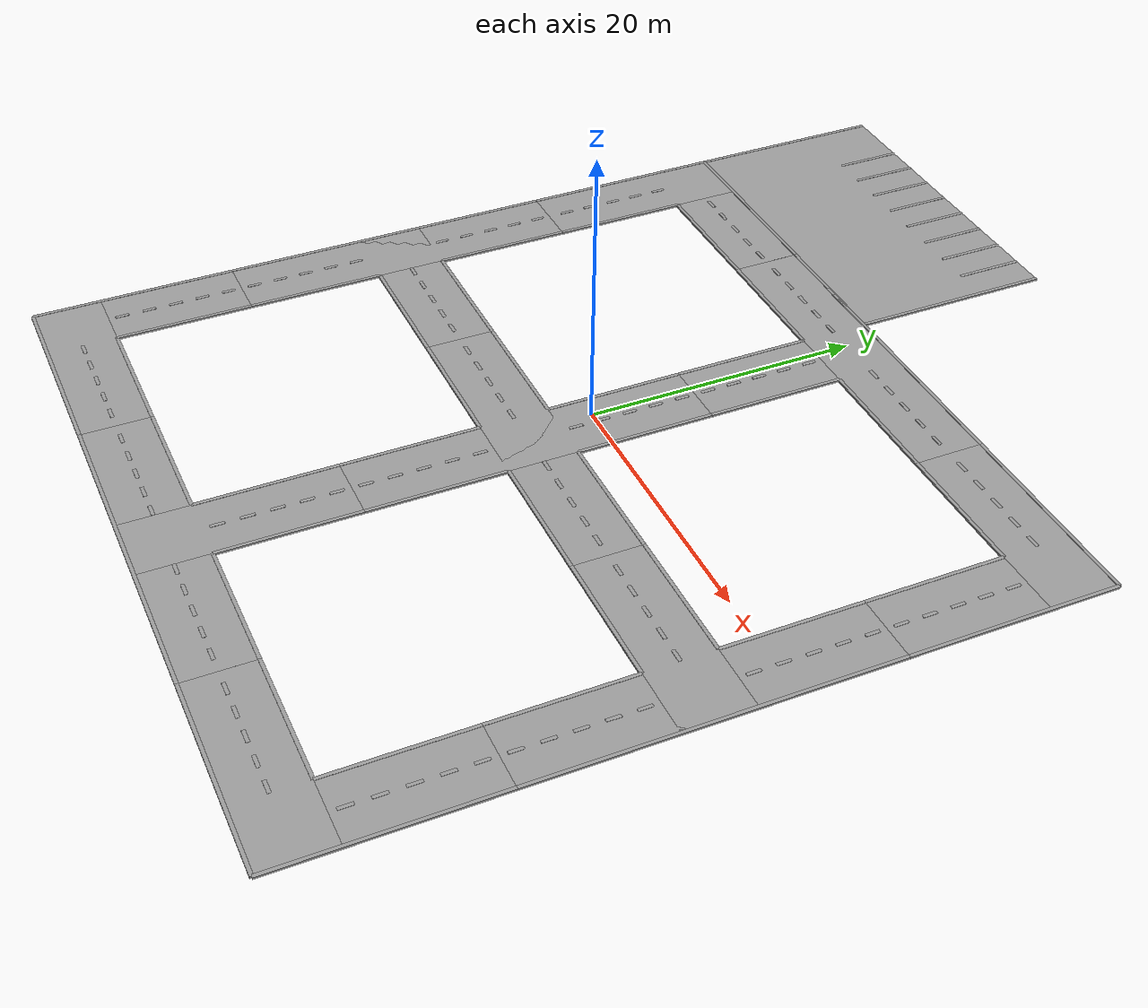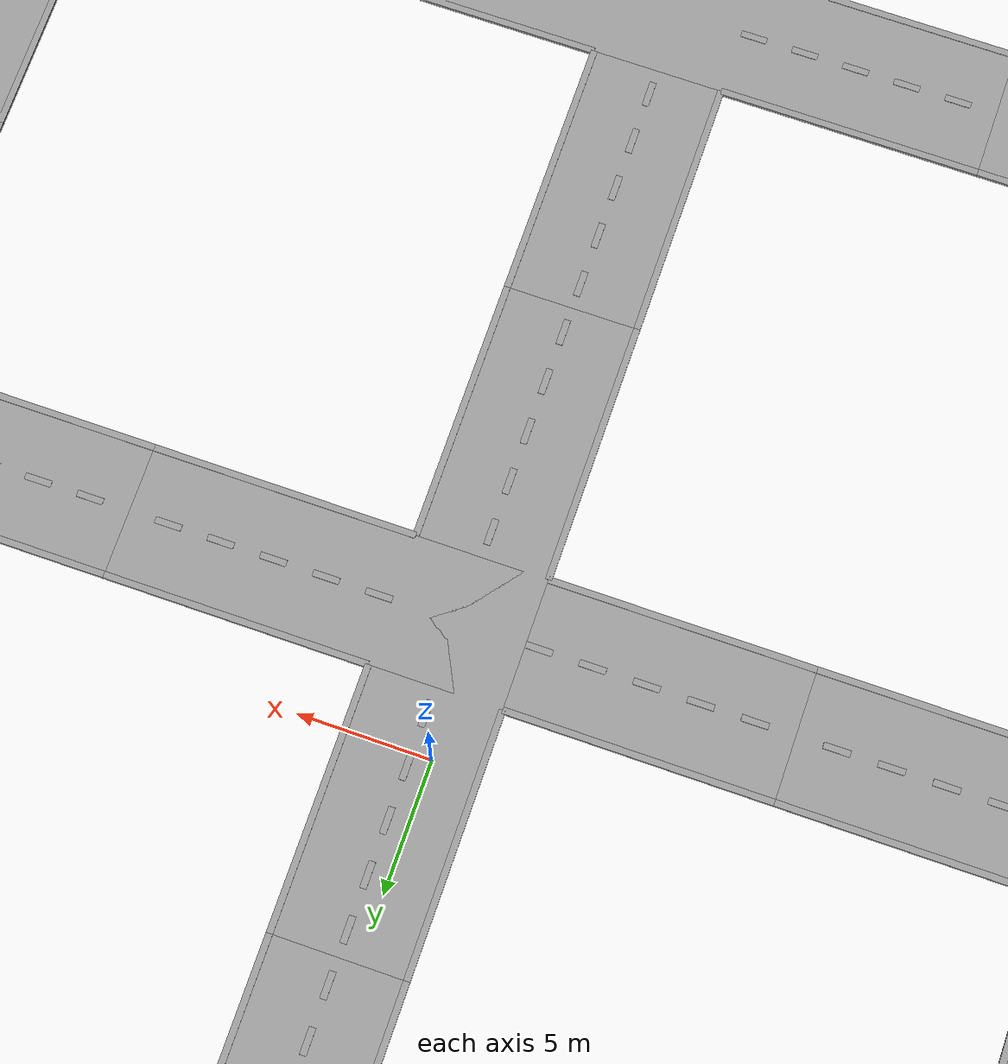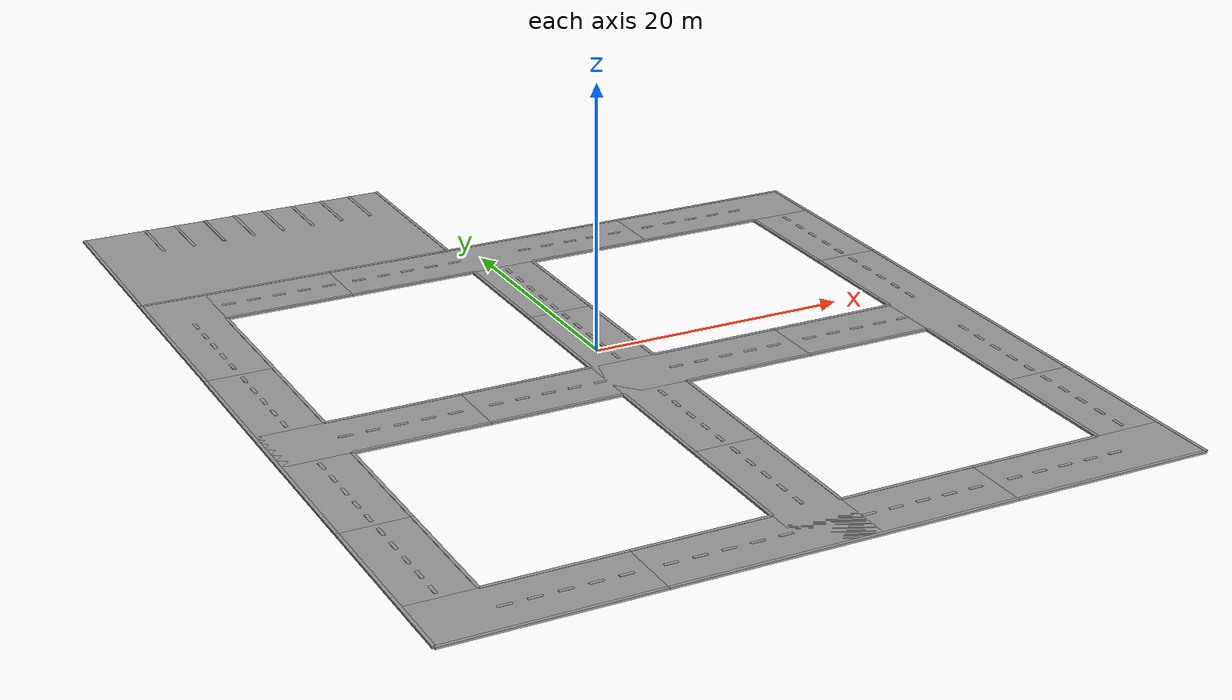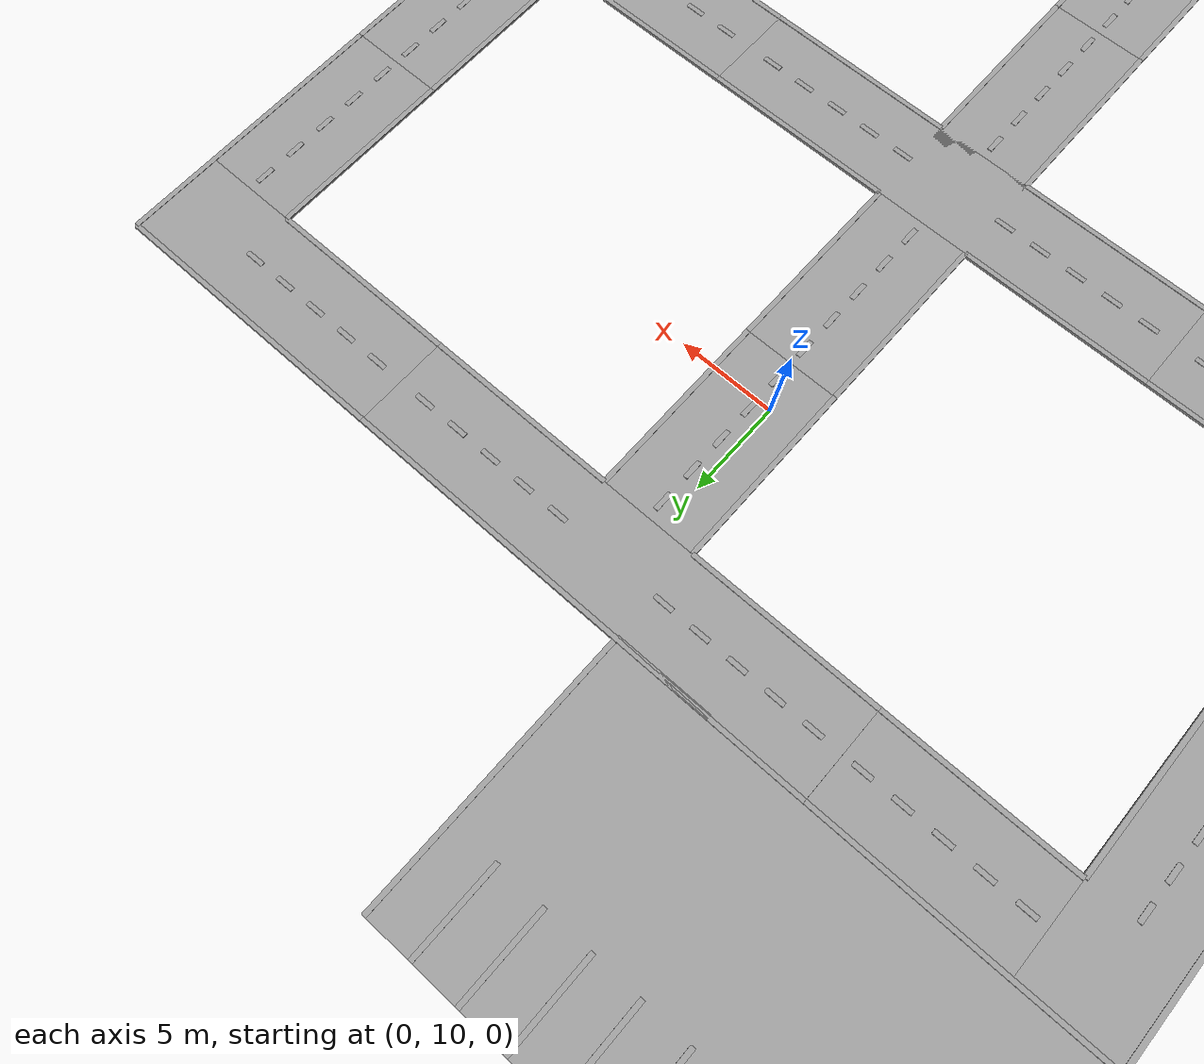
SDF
<?xml version='1.0'?>
<sdf version='1.7'>
  <model name='track_plan'>
    <model name='4_yol'>
      <link name='link_0'>
        <inertial>
          <mass>8812.5</mass>
          <inertia>
            <ixx>73454</ixx>
            <ixy>0</ixy>
            <ixz>0</ixz>
            <iyy>18375.9</iyy>
            <iyz>0</iyz>
            <izz>91796.9</izz>
          </inertia>
          <pose>0 0 0 0 -0 0</pose>
        </inertial>
        <pose>0 0 0 0 -0 0</pose>
        <gravity>1</gravity>
        <self_collide>0</self_collide>
        <kinematic>0</kinematic>
        <enable_wind>0</enable_wind>
        <visual name='ModelPreview_1::link_0::visual_2'>
          <pose>0 7.5 0 0 -0 0</pose>
          <geometry>
            <box>
              <size>25 5 0.1</size>
            </box>
          </geometry>
          <material>
            <lighting>1</lighting>
            <script>
              <uri>file://media/materials/scripts/gazebo.material</uri>
              <name>Gazebo/Grey</name>
            </script>
            <shader type='pixel'>
              <normal_map>__default__</normal_map>
            </shader>
            <ambient>0.008 0.008 0.008 1</ambient>
            <diffuse>0.18 0.204 0.212 1</diffuse>
            <specular>0 0 0 1</specular>
            <emissive>0 0 0 1</emissive>
          </material>
          <transparency>0</transparency>
          <cast_shadows>1</cast_shadows>
        </visual>
        <visual name='ModelPreview_1::link_0::visual_4'>
          <pose>2.5 15 0 0 -0 0</pose>
          <geometry>
            <box>
              <size>0.25 10 0.15</size>
            </box>
          </geometry>
          <material>
            <lighting>1</lighting>
            <script>
              <uri>file://media/materials/scripts/gazebo.material</uri>
              <name>Gazebo/Grey</name>
            </script>
            <shader type='pixel'>
              <normal_map>__default__</normal_map>
            </shader>
            <ambient>1 1 1 1</ambient>
            <diffuse>1 1 1 1</diffuse>
            <specular>1 1 1 1</specular>
            <emissive>1 1 1 1</emissive>
          </material>
          <transparency>0</transparency>
          <cast_shadows>1</cast_shadows>
        </visual>
        <visual name='ModelPreview_1::link_0::visual_5'>
          <pose>-2.5 15 0 0 -0 0</pose>
          <geometry>
            <box>
              <size>0.25 10 0.15</size>
            </box>
          </geometry>
          <material>
            <lighting>1</lighting>
            <script>
              <uri>file://media/materials/scripts/gazebo.material</uri>
              <name>Gazebo/Grey</name>
            </script>
            <shader type='pixel'>
              <normal_map>__default__</normal_map>
            </shader>
            <ambient>1 1 1 1</ambient>
            <diffuse>1 1 1 1</diffuse>
            <specular>1 1 1 1</specular>
            <emissive>1 1 1 1</emissive>
          </material>
          <transparency>0</transparency>
          <cast_shadows>1</cast_shadows>
        </visual>
        <visual name='ModelPreview_1::link_0::visual_3'>
          <pose>2.5 0 0 0 -0 0</pose>
          <geometry>
            <box>
              <size>0.25 10 0.15</size>
            </box>
          </geometry>
          <material>
            <lighting>1</lighting>
            <script>
              <uri>file://media/materials/scripts/gazebo.material</uri>
              <name>Gazebo/Grey</name>
            </script>
            <shader type='pixel'>
              <normal_map>__default__</normal_map>
            </shader>
            <ambient>1 1 1 1</ambient>
            <diffuse>1 1 1 1</diffuse>
            <specular>1 1 1 1</specular>
            <emissive>1 1 1 1</emissive>
          </material>
          <transparency>0</transparency>
          <cast_shadows>1</cast_shadows>
        </visual>
        <visual name='ModelPreview_1::link_0::visual_6'>
          <pose>-2.5 0 0 0 -0 0</pose>
          <geometry>
            <box>
              <size>0.25 10 0.15</size>
            </box>
          </geometry>
          <material>
            <lighting>1</lighting>
            <script>
              <uri>file://media/materials/scripts/gazebo.material</uri>
              <name>Gazebo/Grey</name>
            </script>
            <shader type='pixel'>
              <normal_map>__default__</normal_map>
            </shader>
            <ambient>1 1 1 1</ambient>
            <diffuse>1 1 1 1</diffuse>
            <specular>1 1 1 1</specular>
            <emissive>1 1 1 1</emissive>
          </material>
          <transparency>0</transparency>
          <cast_shadows>1</cast_shadows>
        </visual>
        <visual name='ModelPreview_1::link_0::visual_7'>
          <pose>7.5 5 0 0 -0 0</pose>
          <geometry>
            <box>
              <size>10 0.25 0.15</size>
            </box>
          </geometry>
          <material>
            <lighting>1</lighting>
            <script>
              <uri>file://media/materials/scripts/gazebo.material</uri>
              <name>Gazebo/Grey</name>
            </script>
            <shader type='pixel'>
              <normal_map>__default__</normal_map>
            </shader>
            <ambient>1 1 1 1</ambient>
            <diffuse>1 1 1 1</diffuse>
            <specular>1 1 1 1</specular>
            <emissive>1 1 1 1</emissive>
          </material>
          <transparency>0</transparency>
          <cast_shadows>1</cast_shadows>
        </visual>
        <visual name='ModelPreview_1::link_0::visual_8'>
          <pose>7.5 10 0 0 -0 0</pose>
          <geometry>
            <box>
              <size>10 0.25 0.15</size>
            </box>
          </geometry>
          <material>
            <lighting>1</lighting>
            <script>
              <uri>file://media/materials/scripts/gazebo.material</uri>
              <name>Gazebo/Grey</name>
            </script>
            <shader type='pixel'>
              <normal_map>__default__</normal_map>
            </shader>
            <ambient>1 1 1 1</ambient>
            <diffuse>1 1 1 1</diffuse>
            <specular>1 1 1 1</specular>
            <emissive>1 1 1 1</emissive>
          </material>
          <transparency>0</transparency>
          <cast_shadows>1</cast_shadows>
        </visual>
        <visual name='ModelPreview_1::link_0::visual_9'>
          <pose>-7.5 5 0 0 -0 0</pose>
          <geometry>
            <box>
              <size>10 0.25 0.15</size>
            </box>
          </geometry>
          <material>
            <lighting>1</lighting>
            <script>
              <uri>file://media/materials/scripts/gazebo.material</uri>
              <name>Gazebo/Grey</name>
            </script>
            <shader type='pixel'>
              <normal_map>__default__</normal_map>
            </shader>
            <ambient>1 1 1 1</ambient>
            <diffuse>1 1 1 1</diffuse>
            <specular>1 1 1 1</specular>
            <emissive>1 1 1 1</emissive>
          </material>
          <transparency>0</transparency>
          <cast_shadows>1</cast_shadows>
        </visual>
        <visual name='ModelPreview_1::link_0::visual_10'>
          <pose>-7.5 10 0 0 -0 0</pose>
          <geometry>
            <box>
              <size>10 0.25 0.15</size>
            </box>
          </geometry>
          <material>
            <lighting>1</lighting>
            <script>
              <uri>file://media/materials/scripts/gazebo.material</uri>
              <name>Gazebo/Grey</name>
            </script>
            <shader type='pixel'>
              <normal_map>__default__</normal_map>
            </shader>
            <ambient>1 1 1 1</ambient>
            <diffuse>1 1 1 1</diffuse>
            <specular>1 1 1 1</specular>
            <emissive>1 1 1 1</emissive>
          </material>
          <transparency>0</transparency>
          <cast_shadows>1</cast_shadows>
        </visual>
        <visual name='visual'>
          <pose>0 7.5 0 0 -0 0</pose>
          <geometry>
            <box>
              <size>5 25 0.1</size>
            </box>
          </geometry>
          <material>
            <lighting>1</lighting>
            <script>
              <uri>file://media/materials/scripts/gazebo.material</uri>
              <name>Gazebo/Grey</name>
            </script>
            <shader type='pixel'>
              <normal_map>__default__</normal_map>
            </shader>
            <ambient>0.008 0.008 0.008 1</ambient>
            <diffuse>0.18 0.204 0.212 1</diffuse>
            <specular>0 0 0 1</specular>
            <emissive>0 0 0 1</emissive>
          </material>
          <transparency>0</transparency>
          <cast_shadows>1</cast_shadows>
        </visual>
        <collision name='collision'>
          <laser_retro>0</laser_retro>
          <max_contacts>10</max_contacts>
          <pose>0 7.5 0 0 -0 0</pose>
          <geometry>
            <box>
              <size>5 25 0.15</size>
            </box>
          </geometry>
          <surface>
            <friction>
              <ode>
                <mu>1</mu>
                <mu2>1</mu2>
                <fdir1>0 0 0</fdir1>
                <slip1>0</slip1>
                <slip2>0</slip2>
              </ode>
              <torsional>
                <coefficient>1</coefficient>
                <patch_radius>0</patch_radius>
                <surface_radius>0</surface_radius>
                <use_patch_radius>1</use_patch_radius>
                <ode>
                  <slip>0</slip>
                </ode>
              </torsional>
            </friction>
            <bounce>
              <restitution_coefficient>0</restitution_coefficient>
              <threshold>1e+06</threshold>
            </bounce>
            <contact>
              <collide_without_contact>0</collide_without_contact>
              <collide_without_contact_bitmask>1</collide_without_contact_bitmask>
              <collide_bitmask>1</collide_bitmask>
              <ode>
                <soft_cfm>0</soft_cfm>
                <soft_erp>0.2</soft_erp>
                <kp>1e+13</kp>
                <kd>1</kd>
                <max_vel>0.01</max_vel>
                <min_depth>0</min_depth>
              </ode>
              <bullet>
                <split_impulse>1</split_impulse>
                <split_impulse_penetration_threshold>-0.01</split_impulse_penetration_threshold>
                <soft_cfm>0</soft_cfm>
                <soft_erp>0.2</soft_erp>
                <kp>1e+13</kp>
                <kd>1</kd>
              </bullet>
            </contact>
          </surface>
        </collision>
        <collision name='collision_1'>
          <laser_retro>0</laser_retro>
          <max_contacts>10</max_contacts>
          <pose>0 7.5 0 0 -0 0</pose>
          <geometry>
            <box>
              <size>25 5 0.1</size>
            </box>
          </geometry>
          <surface>
            <friction>
              <ode>
                <mu>1</mu>
                <mu2>1</mu2>
                <fdir1>0 0 0</fdir1>
                <slip1>0</slip1>
                <slip2>0</slip2>
              </ode>
              <torsional>
                <coefficient>1</coefficient>
                <patch_radius>0</patch_radius>
                <surface_radius>0</surface_radius>
                <use_patch_radius>1</use_patch_radius>
                <ode>
                  <slip>0</slip>
                </ode>
              </torsional>
            </friction>
            <bounce>
              <restitution_coefficient>0</restitution_coefficient>
              <threshold>1e+06</threshold>
            </bounce>
            <contact>
              <collide_without_contact>0</collide_without_contact>
              <collide_without_contact_bitmask>1</collide_without_contact_bitmask>
              <collide_bitmask>1</collide_bitmask>
              <ode>
                <soft_cfm>0</soft_cfm>
                <soft_erp>0.2</soft_erp>
                <kp>1e+13</kp>
                <kd>1</kd>
                <max_vel>0.01</max_vel>
                <min_depth>0</min_depth>
              </ode>
              <bullet>
                <split_impulse>1</split_impulse>
                <split_impulse_penetration_threshold>-0.01</split_impulse_penetration_threshold>
                <soft_cfm>0</soft_cfm>
                <soft_erp>0.2</soft_erp>
                <kp>1e+13</kp>
                <kd>1</kd>
              </bullet>
            </contact>
          </surface>
        </collision>
      </link>
      <link name='link_1_clone'>
        <inertial>
          <mass>44.0625</mass>
          <inertia>
            <ixx>3.75449</ixx>
            <ixy>0</ixy>
            <ixz>0</ixz>
            <iyy>0.312109</iyy>
            <iyz>0</iyz>
            <izz>3.90137</izz>
          </inertia>
          <pose>0 0 0 0 -0 0</pose>
        </inertial>
        <pose>0 2 0 0 -0 0</pose>
        <gravity>1</gravity>
        <self_collide>0</self_collide>
        <kinematic>0</kinematic>
        <enable_wind>0</enable_wind>
        <visual name='visual'>
          <pose>0 0 0 0 -0 0</pose>
          <geometry>
            <box>
              <size>0.25 1 0.15</size>
            </box>
          </geometry>
          <material>
            <lighting>1</lighting>
            <script>
              <uri>file://media/materials/scripts/gazebo.material</uri>
              <name>Gazebo/Grey</name>
            </script>
            <shader type='normal_map_object_space'>
              <normal_map>__default__</normal_map>
            </shader>
            <ambient>1 1 1 1</ambient>
            <diffuse>1 1 1 1</diffuse>
            <specular>1 1 1 1</specular>
            <emissive>0 0 0 1</emissive>
          </material>
          <transparency>0</transparency>
          <cast_shadows>1</cast_shadows>
        </visual>
        <collision name='collision_1'>
          <laser_retro>0</laser_retro>
          <max_contacts>10</max_contacts>
          <pose>0 0 0 0 -0 0</pose>
          <geometry>
            <box>
              <size>0.25 1 0.2</size>
            </box>
          </geometry>
          <surface>
            <friction>
              <ode>
                <mu>1</mu>
                <mu2>1</mu2>
                <fdir1>0 0 0</fdir1>
                <slip1>0</slip1>
                <slip2>0</slip2>
              </ode>
              <torsional>
                <coefficient>1</coefficient>
                <patch_radius>0</patch_radius>
                <surface_radius>0</surface_radius>
                <use_patch_radius>1</use_patch_radius>
                <ode>
                  <slip>0</slip>
                </ode>
              </torsional>
            </friction>
            <bounce>
              <restitution_coefficient>0</restitution_coefficient>
              <threshold>1e+06</threshold>
            </bounce>
            <contact>
              <collide_without_contact>0</collide_without_contact>
              <collide_without_contact_bitmask>1</collide_without_contact_bitmask>
              <collide_bitmask>1</collide_bitmask>
              <ode>
                <soft_cfm>0</soft_cfm>
                <soft_erp>0.2</soft_erp>
                <kp>1e+13</kp>
                <kd>1</kd>
                <max_vel>0.01</max_vel>
                <min_depth>0</min_depth>
              </ode>
              <bullet>
                <split_impulse>1</split_impulse>
                <split_impulse_penetration_threshold>-0.01</split_impulse_penetration_threshold>
                <soft_cfm>0</soft_cfm>
                <soft_erp>0.2</soft_erp>
                <kp>1e+13</kp>
                <kd>1</kd>
              </bullet>
            </contact>
          </surface>
        </collision>
      </link>
      <link name='link_1_clone_0'>
        <inertial>
          <mass>44.0625</mass>
          <inertia>
            <ixx>3.75449</ixx>
            <ixy>0</ixy>
            <ixz>0</ixz>
            <iyy>0.312109</iyy>
            <iyz>0</iyz>
            <izz>3.90137</izz>
          </inertia>
          <pose>0 0 0 0 -0 0</pose>
        </inertial>
        <pose>0 0 0 0 -0 0</pose>
        <gravity>1</gravity>
        <self_collide>0</self_collide>
        <kinematic>0</kinematic>
        <enable_wind>0</enable_wind>
        <visual name='visual'>
          <pose>0 0 0 0 -0 0</pose>
          <geometry>
            <box>
              <size>0.25 1 0.15</size>
            </box>
          </geometry>
          <material>
            <lighting>1</lighting>
            <script>
              <uri>file://media/materials/scripts/gazebo.material</uri>
              <name>Gazebo/Grey</name>
            </script>
            <shader type='normal_map_object_space'>
              <normal_map>__default__</normal_map>
            </shader>
            <ambient>1 1 1 1</ambient>
            <diffuse>1 1 1 1</diffuse>
            <specular>1 1 1 1</specular>
            <emissive>0 0 0 1</emissive>
          </material>
          <transparency>0</transparency>
          <cast_shadows>1</cast_shadows>
        </visual>
        <collision name='collision_1'>
          <laser_retro>0</laser_retro>
          <max_contacts>10</max_contacts>
          <pose>0 0 0 0 -0 0</pose>
          <geometry>
            <box>
              <size>0.25 1 0.2</size>
            </box>
          </geometry>
          <surface>
            <friction>
              <ode>
                <mu>1</mu>
                <mu2>1</mu2>
                <fdir1>0 0 0</fdir1>
                <slip1>0</slip1>
                <slip2>0</slip2>
              </ode>
              <torsional>
                <coefficient>1</coefficient>
                <patch_radius>0</patch_radius>
                <surface_radius>0</surface_radius>
                <use_patch_radius>1</use_patch_radius>
                <ode>
                  <slip>0</slip>
                </ode>
              </torsional>
            </friction>
            <bounce>
              <restitution_coefficient>0</restitution_coefficient>
              <threshold>1e+06</threshold>
            </bounce>
            <contact>
              <collide_without_contact>0</collide_without_contact>
              <collide_without_contact_bitmask>1</collide_without_contact_bitmask>
              <collide_bitmask>1</collide_bitmask>
              <ode>
                <soft_cfm>0</soft_cfm>
                <soft_erp>0.2</soft_erp>
                <kp>1e+13</kp>
                <kd>1</kd>
                <max_vel>0.01</max_vel>
                <min_depth>0</min_depth>
              </ode>
              <bullet>
                <split_impulse>1</split_impulse>
                <split_impulse_penetration_threshold>-0.01</split_impulse_penetration_threshold>
                <soft_cfm>0</soft_cfm>
                <soft_erp>0.2</soft_erp>
                <kp>1e+13</kp>
                <kd>1</kd>
              </bullet>
            </contact>
          </surface>
        </collision>
      </link>
      <link name='link_1_clone_1'>
        <inertial>
          <mass>44.0625</mass>
          <inertia>
            <ixx>3.75449</ixx>
            <ixy>0</ixy>
            <ixz>0</ixz>
            <iyy>0.312109</iyy>
            <iyz>0</iyz>
            <izz>3.90137</izz>
          </inertia>
          <pose>0 0 0 0 -0 0</pose>
        </inertial>
        <pose>0 -2 0 0 -0 0</pose>
        <gravity>1</gravity>
        <self_collide>0</self_collide>
        <kinematic>0</kinematic>
        <enable_wind>0</enable_wind>
        <visual name='visual'>
          <pose>0 0 0 0 -0 0</pose>
          <geometry>
            <box>
              <size>0.25 1 0.15</size>
            </box>
          </geometry>
          <material>
            <lighting>1</lighting>
            <script>
              <uri>file://media/materials/scripts/gazebo.material</uri>
              <name>Gazebo/Grey</name>
            </script>
            <shader type='normal_map_object_space'>
              <normal_map>__default__</normal_map>
            </shader>
            <ambient>1 1 1 1</ambient>
            <diffuse>1 1 1 1</diffuse>
            <specular>1 1 1 1</specular>
            <emissive>0 0 0 1</emissive>
          </material>
          <transparency>0</transparency>
          <cast_shadows>1</cast_shadows>
        </visual>
        <collision name='collision_1'>
          <laser_retro>0</laser_retro>
          <max_contacts>10</max_contacts>
          <pose>0 0 0 0 -0 0</pose>
          <geometry>
            <box>
              <size>0.25 1 0.2</size>
            </box>
          </geometry>
          <surface>
            <friction>
              <ode>
                <mu>1</mu>
                <mu2>1</mu2>
                <fdir1>0 0 0</fdir1>
                <slip1>0</slip1>
                <slip2>0</slip2>
              </ode>
              <torsional>
                <coefficient>1</coefficient>
                <patch_radius>0</patch_radius>
                <surface_radius>0</surface_radius>
                <use_patch_radius>1</use_patch_radius>
                <ode>
                  <slip>0</slip>
                </ode>
              </torsional>
            </friction>
            <bounce>
              <restitution_coefficient>0</restitution_coefficient>
              <threshold>1e+06</threshold>
            </bounce>
            <contact>
              <collide_without_contact>0</collide_without_contact>
              <collide_without_contact_bitmask>1</collide_without_contact_bitmask>
              <collide_bitmask>1</collide_bitmask>
              <ode>
                <soft_cfm>0</soft_cfm>
                <soft_erp>0.2</soft_erp>
                <kp>1e+13</kp>
                <kd>1</kd>
                <max_vel>0.01</max_vel>
                <min_depth>0</min_depth>
              </ode>
              <bullet>
                <split_impulse>1</split_impulse>
                <split_impulse_penetration_threshold>-0.01</split_impulse_penetration_threshold>
                <soft_cfm>0</soft_cfm>
                <soft_erp>0.2</soft_erp>
                <kp>1e+13</kp>
                <kd>1</kd>
              </bullet>
            </contact>
          </surface>
        </collision>
      </link>
      <link name='link_1_clone_2'>
        <inertial>
          <mass>44.0625</mass>
          <inertia>
            <ixx>3.75449</ixx>
            <ixy>0</ixy>
            <ixz>0</ixz>
            <iyy>0.312109</iyy>
            <iyz>0</iyz>
            <izz>3.90137</izz>
          </inertia>
          <pose>0 0 0 0 -0 0</pose>
        </inertial>
        <pose>0 4 0 0 -0 0</pose>
        <gravity>1</gravity>
        <self_collide>0</self_collide>
        <kinematic>0</kinematic>
        <enable_wind>0</enable_wind>
        <visual name='visual'>
          <pose>0 0 0 0 -0 0</pose>
          <geometry>
            <box>
              <size>0.25 1 0.15</size>
            </box>
          </geometry>
          <material>
            <lighting>1</lighting>
            <script>
              <uri>file://media/materials/scripts/gazebo.material</uri>
              <name>Gazebo/Grey</name>
            </script>
            <shader type='normal_map_object_space'>
              <normal_map>__default__</normal_map>
            </shader>
            <ambient>1 1 1 1</ambient>
            <diffuse>1 1 1 1</diffuse>
            <specular>1 1 1 1</specular>
            <emissive>0 0 0 1</emissive>
          </material>
          <transparency>0</transparency>
          <cast_shadows>1</cast_shadows>
        </visual>
        <collision name='collision_1'>
          <laser_retro>0</laser_retro>
          <max_contacts>10</max_contacts>
          <pose>0 0 0 0 -0 0</pose>
          <geometry>
            <box>
              <size>0.25 1 0.2</size>
            </box>
          </geometry>
          <surface>
            <friction>
              <ode>
                <mu>1</mu>
                <mu2>1</mu2>
                <fdir1>0 0 0</fdir1>
                <slip1>0</slip1>
                <slip2>0</slip2>
              </ode>
              <torsional>
                <coefficient>1</coefficient>
                <patch_radius>0</patch_radius>
                <surface_radius>0</surface_radius>
                <use_patch_radius>1</use_patch_radius>
                <ode>
                  <slip>0</slip>
                </ode>
              </torsional>
            </friction>
            <bounce>
              <restitution_coefficient>0</restitution_coefficient>
              <threshold>1e+06</threshold>
            </bounce>
            <contact>
              <collide_without_contact>0</collide_without_contact>
              <collide_without_contact_bitmask>1</collide_without_contact_bitmask>
              <collide_bitmask>1</collide_bitmask>
              <ode>
                <soft_cfm>0</soft_cfm>
                <soft_erp>0.2</soft_erp>
                <kp>1e+13</kp>
                <kd>1</kd>
                <max_vel>0.01</max_vel>
                <min_depth>0</min_depth>
              </ode>
              <bullet>
                <split_impulse>1</split_impulse>
                <split_impulse_penetration_threshold>-0.01</split_impulse_penetration_threshold>
                <soft_cfm>0</soft_cfm>
                <soft_erp>0.2</soft_erp>
                <kp>1e+13</kp>
                <kd>1</kd>
              </bullet>
            </contact>
          </surface>
        </collision>
      </link>
      <link name='link_1_clone_2_clone'>
        <inertial>
          <mass>44.0625</mass>
          <inertia>
            <ixx>3.75449</ixx>
            <ixy>0</ixy>
            <ixz>0</ixz>
            <iyy>0.312109</iyy>
            <iyz>0</iyz>
            <izz>3.90137</izz>
          </inertia>
          <pose>0 0 0 0 -0 0</pose>
        </inertial>
        <pose>0 11 0 0 -0 0</pose>
        <gravity>1</gravity>
        <self_collide>0</self_collide>
        <kinematic>0</kinematic>
        <enable_wind>0</enable_wind>
        <visual name='visual'>
          <pose>0 0 0 0 -0 0</pose>
          <geometry>
            <box>
              <size>0.25 1 0.15</size>
            </box>
          </geometry>
          <material>
            <lighting>1</lighting>
            <script>
              <uri>file://media/materials/scripts/gazebo.material</uri>
              <name>Gazebo/Grey</name>
            </script>
            <shader type='normal_map_object_space'>
              <normal_map>__default__</normal_map>
            </shader>
            <ambient>1 1 1 1</ambient>
            <diffuse>1 1 1 1</diffuse>
            <specular>1 1 1 1</specular>
            <emissive>0 0 0 1</emissive>
          </material>
          <transparency>0</transparency>
          <cast_shadows>1</cast_shadows>
        </visual>
        <collision name='collision_1'>
          <laser_retro>0</laser_retro>
          <max_contacts>10</max_contacts>
          <pose>0 0 0 0 -0 0</pose>
          <geometry>
            <box>
              <size>0.25 1 0.2</size>
            </box>
          </geometry>
          <surface>
            <friction>
              <ode>
                <mu>1</mu>
                <mu2>1</mu2>
                <fdir1>0 0 0</fdir1>
                <slip1>0</slip1>
                <slip2>0</slip2>
              </ode>
              <torsional>
                <coefficient>1</coefficient>
                <patch_radius>0</patch_radius>
                <surface_radius>0</surface_radius>
                <use_patch_radius>1</use_patch_radius>
                <ode>
                  <slip>0</slip>
                </ode>
              </torsional>
            </friction>
            <bounce>
              <restitution_coefficient>0</restitution_coefficient>
              <threshold>1e+06</threshold>
            </bounce>
            <contact>
              <collide_without_contact>0</collide_without_contact>
              <collide_without_contact_bitmask>1</collide_without_contact_bitmask>
              <collide_bitmask>1</collide_bitmask>
              <ode>
                <soft_cfm>0</soft_cfm>
                <soft_erp>0.2</soft_erp>
                <kp>1e+13</kp>
                <kd>1</kd>
                <max_vel>0.01</max_vel>
                <min_depth>0</min_depth>
              </ode>
              <bullet>
                <split_impulse>1</split_impulse>
                <split_impulse_penetration_threshold>-0.01</split_impulse_penetration_threshold>
                <soft_cfm>0</soft_cfm>
                <soft_erp>0.2</soft_erp>
                <kp>1e+13</kp>
                <kd>1</kd>
              </bullet>
            </contact>
          </surface>
        </collision>
      </link>
      <link name='link_1_clone_2_clone_0'>
        <inertial>
          <mass>44.0625</mass>
          <inertia>
            <ixx>3.75449</ixx>
            <ixy>0</ixy>
            <ixz>0</ixz>
            <iyy>0.312109</iyy>
            <iyz>0</iyz>
            <izz>3.90137</izz>
          </inertia>
          <pose>0 0 0 0 -0 0</pose>
        </inertial>
        <pose>-3 7.5 0 0 -0 0</pose>
        <gravity>1</gravity>
        <self_collide>0</self_collide>
        <kinematic>0</kinematic>
        <enable_wind>0</enable_wind>
        <visual name='visual'>
          <pose>0 0 0 0 -0 0</pose>
          <geometry>
            <box>
              <size>1 0.25 0.15</size>
            </box>
          </geometry>
          <material>
            <lighting>1</lighting>
            <script>
              <uri>file://media/materials/scripts/gazebo.material</uri>
              <name>Gazebo/Grey</name>
            </script>
            <shader type='normal_map_object_space'>
              <normal_map>__default__</normal_map>
            </shader>
            <ambient>1 1 1 1</ambient>
            <diffuse>1 1 1 1</diffuse>
            <specular>1 1 1 1</specular>
            <emissive>0 0 0 1</emissive>
          </material>
          <transparency>0</transparency>
          <cast_shadows>1</cast_shadows>
        </visual>
        <collision name='collision_1'>
          <laser_retro>0</laser_retro>
          <max_contacts>10</max_contacts>
          <pose>0 0 0 0 -0 0</pose>
          <geometry>
            <box>
              <size>1 0.25 0.2</size>
            </box>
          </geometry>
          <surface>
            <friction>
              <ode>
                <mu>1</mu>
                <mu2>1</mu2>
                <fdir1>0 0 0</fdir1>
                <slip1>0</slip1>
                <slip2>0</slip2>
              </ode>
              <torsional>
                <coefficient>1</coefficient>
                <patch_radius>0</patch_radius>
                <surface_radius>0</surface_radius>
                <use_patch_radius>1</use_patch_radius>
                <ode>
                  <slip>0</slip>
                </ode>
              </torsional>
            </friction>
            <bounce>
              <restitution_coefficient>0</restitution_coefficient>
              <threshold>1e+06</threshold>
            </bounce>
            <contact>
              <collide_without_contact>0</collide_without_contact>
              <collide_without_contact_bitmask>1</collide_without_contact_bitmask>
              <collide_bitmask>1</collide_bitmask>
              <ode>
                <soft_cfm>0</soft_cfm>
                <soft_erp>0.2</soft_erp>
                <kp>1e+13</kp>
                <kd>1</kd>
                <max_vel>0.01</max_vel>
                <min_depth>0</min_depth>
              </ode>
              <bullet>
                <split_impulse>1</split_impulse>
                <split_impulse_penetration_threshold>-0.01</split_impulse_penetration_threshold>
                <soft_cfm>0</soft_cfm>
                <soft_erp>0.2</soft_erp>
                <kp>1e+13</kp>
                <kd>1</kd>
              </bullet>
            </contact>
          </surface>
        </collision>
      </link>
      <link name='link_1_clone_2_clone_0_clone'>
        <inertial>
          <mass>44.0625</mass>
          <inertia>
            <ixx>3.75449</ixx>
            <ixy>0</ixy>
            <ixz>0</ixz>
            <iyy>0.312109</iyy>
            <iyz>0</iyz>
            <izz>3.90137</izz>
          </inertia>
          <pose>0 0 0 0 -0 0</pose>
        </inertial>
        <pose>-5 7.5 0 0 -0 0</pose>
        <gravity>1</gravity>
        <self_collide>0</self_collide>
        <kinematic>0</kinematic>
        <enable_wind>0</enable_wind>
        <visual name='visual'>
          <pose>0 0 0 0 -0 0</pose>
          <geometry>
            <box>
              <size>1 0.25 0.15</size>
            </box>
          </geometry>
          <material>
            <lighting>1</lighting>
            <script>
              <uri>file://media/materials/scripts/gazebo.material</uri>
              <name>Gazebo/Grey</name>
            </script>
            <shader type='normal_map_object_space'>
              <normal_map>__default__</normal_map>
            </shader>
            <ambient>1 1 1 1</ambient>
            <diffuse>1 1 1 1</diffuse>
            <specular>1 1 1 1</specular>
            <emissive>0 0 0 1</emissive>
          </material>
          <transparency>0</transparency>
          <cast_shadows>1</cast_shadows>
        </visual>
        <collision name='collision_1'>
          <laser_retro>0</laser_retro>
          <max_contacts>10</max_contacts>
          <pose>0 0 0 0 -0 0</pose>
          <geometry>
            <box>
              <size>1 0.25 0.2</size>
            </box>
          </geometry>
          <surface>
            <friction>
              <ode>
                <mu>1</mu>
                <mu2>1</mu2>
                <fdir1>0 0 0</fdir1>
                <slip1>0</slip1>
                <slip2>0</slip2>
              </ode>
              <torsional>
                <coefficient>1</coefficient>
                <patch_radius>0</patch_radius>
                <surface_radius>0</surface_radius>
                <use_patch_radius>1</use_patch_radius>
                <ode>
                  <slip>0</slip>
                </ode>
              </torsional>
            </friction>
            <bounce>
              <restitution_coefficient>0</restitution_coefficient>
              <threshold>1e+06</threshold>
            </bounce>
            <contact>
              <collide_without_contact>0</collide_without_contact>
              <collide_without_contact_bitmask>1</collide_without_contact_bitmask>
              <collide_bitmask>1</collide_bitmask>
              <ode>
                <soft_cfm>0</soft_cfm>
                <soft_erp>0.2</soft_erp>
                <kp>1e+13</kp>
                <kd>1</kd>
                <max_vel>0.01</max_vel>
                <min_depth>0</min_depth>
              </ode>
              <bullet>
                <split_impulse>1</split_impulse>
                <split_impulse_penetration_threshold>-0.01</split_impulse_penetration_threshold>
                <soft_cfm>0</soft_cfm>
                <soft_erp>0.2</soft_erp>
                <kp>1e+13</kp>
                <kd>1</kd>
              </bullet>
            </contact>
          </surface>
        </collision>
      </link>
      <link name='link_1_clone_2_clone_0_clone_0'>
        <inertial>
          <mass>44.0625</mass>
          <inertia>
            <ixx>3.75449</ixx>
            <ixy>0</ixy>
            <ixz>0</ixz>
            <iyy>0.312109</iyy>
            <iyz>0</iyz>
            <izz>3.90137</izz>
          </inertia>
          <pose>0 0 0 0 -0 0</pose>
        </inertial>
        <pose>-7 7.5 0 0 -0 0</pose>
        <gravity>1</gravity>
        <self_collide>0</self_collide>
        <kinematic>0</kinematic>
        <enable_wind>0</enable_wind>
        <visual name='visual'>
          <pose>0 0 0 0 -0 0</pose>
          <geometry>
            <box>
              <size>1 0.25 0.15</size>
            </box>
          </geometry>
          <material>
            <lighting>1</lighting>
            <script>
              <uri>file://media/materials/scripts/gazebo.material</uri>
              <name>Gazebo/Grey</name>
            </script>
            <shader type='normal_map_object_space'>
              <normal_map>__default__</normal_map>
            </shader>
            <ambient>1 1 1 1</ambient>
            <diffuse>1 1 1 1</diffuse>
            <specular>1 1 1 1</specular>
            <emissive>0 0 0 1</emissive>
          </material>
          <transparency>0</transparency>
          <cast_shadows>1</cast_shadows>
        </visual>
        <collision name='collision_1'>
          <laser_retro>0</laser_retro>
          <max_contacts>10</max_contacts>
          <pose>0 0 0 0 -0 0</pose>
          <geometry>
            <box>
              <size>1 0.25 0.2</size>
            </box>
          </geometry>
          <surface>
            <friction>
              <ode>
                <mu>1</mu>
                <mu2>1</mu2>
                <fdir1>0 0 0</fdir1>
                <slip1>0</slip1>
                <slip2>0</slip2>
              </ode>
              <torsional>
                <coefficient>1</coefficient>
                <patch_radius>0</patch_radius>
                <surface_radius>0</surface_radius>
                <use_patch_radius>1</use_patch_radius>
                <ode>
                  <slip>0</slip>
                </ode>
              </torsional>
            </friction>
            <bounce>
              <restitution_coefficient>0</restitution_coefficient>
              <threshold>1e+06</threshold>
            </bounce>
            <contact>
              <collide_without_contact>0</collide_without_contact>
              <collide_without_contact_bitmask>1</collide_without_contact_bitmask>
              <collide_bitmask>1</collide_bitmask>
              <ode>
                <soft_cfm>0</soft_cfm>
                <soft_erp>0.2</soft_erp>
                <kp>1e+13</kp>
                <kd>1</kd>
                <max_vel>0.01</max_vel>
                <min_depth>0</min_depth>
              </ode>
              <bullet>
                <split_impulse>1</split_impulse>
                <split_impulse_penetration_threshold>-0.01</split_impulse_penetration_threshold>
                <soft_cfm>0</soft_cfm>
                <soft_erp>0.2</soft_erp>
                <kp>1e+13</kp>
                <kd>1</kd>
              </bullet>
            </contact>
          </surface>
        </collision>
      </link>
      <link name='link_1_clone_2_clone_0_clone_1'>
        <inertial>
          <mass>44.0625</mass>
          <inertia>
            <ixx>3.75449</ixx>
            <ixy>0</ixy>
            <ixz>0</ixz>
            <iyy>0.312109</iyy>
            <iyz>0</iyz>
            <izz>3.90137</izz>
          </inertia>
          <pose>0 0 0 0 -0 0</pose>
        </inertial>
        <pose>-9 7.5 0 0 -0 0</pose>
        <gravity>1</gravity>
        <self_collide>0</self_collide>
        <kinematic>0</kinematic>
        <enable_wind>0</enable_wind>
        <visual name='visual'>
          <pose>0 0 0 0 -0 0</pose>
          <geometry>
            <box>
              <size>1 0.25 0.15</size>
            </box>
          </geometry>
          <material>
            <lighting>1</lighting>
            <script>
              <uri>file://media/materials/scripts/gazebo.material</uri>
              <name>Gazebo/Grey</name>
            </script>
            <shader type='normal_map_object_space'>
              <normal_map>__default__</normal_map>
            </shader>
            <ambient>1 1 1 1</ambient>
            <diffuse>1 1 1 1</diffuse>
            <specular>1 1 1 1</specular>
            <emissive>0 0 0 1</emissive>
          </material>
          <transparency>0</transparency>
          <cast_shadows>1</cast_shadows>
        </visual>
        <collision name='collision_1'>
          <laser_retro>0</laser_retro>
          <max_contacts>10</max_contacts>
          <pose>0 0 0 0 -0 0</pose>
          <geometry>
            <box>
              <size>1 0.25 0.2</size>
            </box>
          </geometry>
          <surface>
            <friction>
              <ode>
                <mu>1</mu>
                <mu2>1</mu2>
                <fdir1>0 0 0</fdir1>
                <slip1>0</slip1>
                <slip2>0</slip2>
              </ode>
              <torsional>
                <coefficient>1</coefficient>
                <patch_radius>0</patch_radius>
                <surface_radius>0</surface_radius>
                <use_patch_radius>1</use_patch_radius>
                <ode>
                  <slip>0</slip>
                </ode>
              </torsional>
            </friction>
            <bounce>
              <restitution_coefficient>0</restitution_coefficient>
              <threshold>1e+06</threshold>
            </bounce>
            <contact>
              <collide_without_contact>0</collide_without_contact>
              <collide_without_contact_bitmask>1</collide_without_contact_bitmask>
              <collide_bitmask>1</collide_bitmask>
              <ode>
                <soft_cfm>0</soft_cfm>
                <soft_erp>0.2</soft_erp>
                <kp>1e+13</kp>
                <kd>1</kd>
                <max_vel>0.01</max_vel>
                <min_depth>0</min_depth>
              </ode>
              <bullet>
                <split_impulse>1</split_impulse>
                <split_impulse_penetration_threshold>-0.01</split_impulse_penetration_threshold>
                <soft_cfm>0</soft_cfm>
                <soft_erp>0.2</soft_erp>
                <kp>1e+13</kp>
                <kd>1</kd>
              </bullet>
            </contact>
          </surface>
        </collision>
      </link>
      <link name='link_1_clone_2_clone_0_clone_1_clone'>
        <inertial>
          <mass>44.0625</mass>
          <inertia>
            <ixx>3.75449</ixx>
            <ixy>0</ixy>
            <ixz>0</ixz>
            <iyy>0.312109</iyy>
            <iyz>0</iyz>
            <izz>3.90137</izz>
          </inertia>
          <pose>0 0 0 0 -0 0</pose>
        </inertial>
        <pose>-11 7.5 0 0 -0 0</pose>
        <gravity>1</gravity>
        <self_collide>0</self_collide>
        <kinematic>0</kinematic>
        <enable_wind>0</enable_wind>
        <visual name='visual'>
          <pose>0 0 0 0 -0 0</pose>
          <geometry>
            <box>
              <size>1 0.25 0.15</size>
            </box>
          </geometry>
          <material>
            <lighting>1</lighting>
            <script>
              <uri>file://media/materials/scripts/gazebo.material</uri>
              <name>Gazebo/Grey</name>
            </script>
            <shader type='normal_map_object_space'>
              <normal_map>__default__</normal_map>
            </shader>
            <ambient>1 1 1 1</ambient>
            <diffuse>1 1 1 1</diffuse>
            <specular>1 1 1 1</specular>
            <emissive>0 0 0 1</emissive>
          </material>
          <transparency>0</transparency>
          <cast_shadows>1</cast_shadows>
        </visual>
        <collision name='collision_1'>
          <laser_retro>0</laser_retro>
          <max_contacts>10</max_contacts>
          <pose>0 0 0 0 -0 0</pose>
          <geometry>
            <box>
              <size>1 0.25 0.2</size>
            </box>
          </geometry>
          <surface>
            <friction>
              <ode>
                <mu>1</mu>
                <mu2>1</mu2>
                <fdir1>0 0 0</fdir1>
                <slip1>0</slip1>
                <slip2>0</slip2>
              </ode>
              <torsional>
                <coefficient>1</coefficient>
                <patch_radius>0</patch_radius>
                <surface_radius>0</surface_radius>
                <use_patch_radius>1</use_patch_radius>
                <ode>
                  <slip>0</slip>
                </ode>
              </torsional>
            </friction>
            <bounce>
              <restitution_coefficient>0</restitution_coefficient>
              <threshold>1e+06</threshold>
            </bounce>
            <contact>
              <collide_without_contact>0</collide_without_contact>
              <collide_without_contact_bitmask>1</collide_without_contact_bitmask>
              <collide_bitmask>1</collide_bitmask>
              <ode>
                <soft_cfm>0</soft_cfm>
                <soft_erp>0.2</soft_erp>
                <kp>1e+13</kp>
                <kd>1</kd>
                <max_vel>0.01</max_vel>
                <min_depth>0</min_depth>
              </ode>
              <bullet>
                <split_impulse>1</split_impulse>
                <split_impulse_penetration_threshold>-0.01</split_impulse_penetration_threshold>
                <soft_cfm>0</soft_cfm>
                <soft_erp>0.2</soft_erp>
                <kp>1e+13</kp>
                <kd>1</kd>
              </bullet>
            </contact>
          </surface>
        </collision>
      </link>
      <link name='link_1_clone_2_clone_0_clone_1_clone_0'>
        <inertial>
          <mass>44.0625</mass>
          <inertia>
            <ixx>3.75449</ixx>
            <ixy>0</ixy>
            <ixz>0</ixz>
            <iyy>0.312109</iyy>
            <iyz>0</iyz>
            <izz>3.90137</izz>
          </inertia>
          <pose>0 0 0 0 -0 0</pose>
        </inertial>
        <pose>11 7.5 0 0 -0 0</pose>
        <gravity>1</gravity>
        <self_collide>0</self_collide>
        <kinematic>0</kinematic>
        <enable_wind>0</enable_wind>
        <visual name='visual'>
          <pose>0 0 0 0 -0 0</pose>
          <geometry>
            <box>
              <size>1 0.25 0.15</size>
            </box>
          </geometry>
          <material>
            <lighting>1</lighting>
            <script>
              <uri>file://media/materials/scripts/gazebo.material</uri>
              <name>Gazebo/Grey</name>
            </script>
            <shader type='normal_map_object_space'>
              <normal_map>__default__</normal_map>
            </shader>
            <ambient>1 1 1 1</ambient>
            <diffuse>1 1 1 1</diffuse>
            <specular>1 1 1 1</specular>
            <emissive>0 0 0 1</emissive>
          </material>
          <transparency>0</transparency>
          <cast_shadows>1</cast_shadows>
        </visual>
        <collision name='collision_1'>
          <laser_retro>0</laser_retro>
          <max_contacts>10</max_contacts>
          <pose>0 0 0 0 -0 0</pose>
          <geometry>
            <box>
              <size>1 0.25 0.2</size>
            </box>
          </geometry>
          <surface>
            <friction>
              <ode>
                <mu>1</mu>
                <mu2>1</mu2>
                <fdir1>0 0 0</fdir1>
                <slip1>0</slip1>
                <slip2>0</slip2>
              </ode>
              <torsional>
                <coefficient>1</coefficient>
                <patch_radius>0</patch_radius>
                <surface_radius>0</surface_radius>
                <use_patch_radius>1</use_patch_radius>
                <ode>
                  <slip>0</slip>
                </ode>
              </torsional>
            </friction>
            <bounce>
              <restitution_coefficient>0</restitution_coefficient>
              <threshold>1e+06</threshold>
            </bounce>
            <contact>
              <collide_without_contact>0</collide_without_contact>
              <collide_without_contact_bitmask>1</collide_without_contact_bitmask>
              <collide_bitmask>1</collide_bitmask>
              <ode>
                <soft_cfm>0</soft_cfm>
                <soft_erp>0.2</soft_erp>
                <kp>1e+13</kp>
                <kd>1</kd>
                <max_vel>0.01</max_vel>
                <min_depth>0</min_depth>
              </ode>
              <bullet>
                <split_impulse>1</split_impulse>
                <split_impulse_penetration_threshold>-0.01</split_impulse_penetration_threshold>
                <soft_cfm>0</soft_cfm>
                <soft_erp>0.2</soft_erp>
                <kp>1e+13</kp>
                <kd>1</kd>
              </bullet>
            </contact>
          </surface>
        </collision>
      </link>
      <link name='link_1_clone_2_clone_0_clone_2'>
        <inertial>
          <mass>44.0625</mass>
          <inertia>
            <ixx>3.75449</ixx>
            <ixy>0</ixy>
            <ixz>0</ixz>
            <iyy>0.312109</iyy>
            <iyz>0</iyz>
            <izz>3.90137</izz>
          </inertia>
          <pose>0 0 0 0 -0 0</pose>
        </inertial>
        <pose>3 7.5 0 0 -0 0</pose>
        <gravity>1</gravity>
        <self_collide>0</self_collide>
        <kinematic>0</kinematic>
        <enable_wind>0</enable_wind>
        <visual name='visual'>
          <pose>0 0 0 0 -0 0</pose>
          <geometry>
            <box>
              <size>1 0.25 0.15</size>
            </box>
          </geometry>
          <material>
            <lighting>1</lighting>
            <script>
              <uri>file://media/materials/scripts/gazebo.material</uri>
              <name>Gazebo/Grey</name>
            </script>
            <shader type='normal_map_object_space'>
              <normal_map>__default__</normal_map>
            </shader>
            <ambient>1 1 1 1</ambient>
            <diffuse>1 1 1 1</diffuse>
            <specular>1 1 1 1</specular>
            <emissive>0 0 0 1</emissive>
          </material>
          <transparency>0</transparency>
          <cast_shadows>1</cast_shadows>
        </visual>
        <collision name='collision_1'>
          <laser_retro>0</laser_retro>
          <max_contacts>10</max_contacts>
          <pose>0 0 0 0 -0 0</pose>
          <geometry>
            <box>
              <size>1 0.25 0.2</size>
            </box>
          </geometry>
          <surface>
            <friction>
              <ode>
                <mu>1</mu>
                <mu2>1</mu2>
                <fdir1>0 0 0</fdir1>
                <slip1>0</slip1>
                <slip2>0</slip2>
              </ode>
              <torsional>
                <coefficient>1</coefficient>
                <patch_radius>0</patch_radius>
                <surface_radius>0</surface_radius>
                <use_patch_radius>1</use_patch_radius>
                <ode>
                  <slip>0</slip>
                </ode>
              </torsional>
            </friction>
            <bounce>
              <restitution_coefficient>0</restitution_coefficient>
              <threshold>1e+06</threshold>
            </bounce>
            <contact>
              <collide_without_contact>0</collide_without_contact>
              <collide_without_contact_bitmask>1</collide_without_contact_bitmask>
              <collide_bitmask>1</collide_bitmask>
              <ode>
                <soft_cfm>0</soft_cfm>
                <soft_erp>0.2</soft_erp>
                <kp>1e+13</kp>
                <kd>1</kd>
                <max_vel>0.01</max_vel>
                <min_depth>0</min_depth>
              </ode>
              <bullet>
                <split_impulse>1</split_impulse>
                <split_impulse_penetration_threshold>-0.01</split_impulse_penetration_threshold>
                <soft_cfm>0</soft_cfm>
                <soft_erp>0.2</soft_erp>
                <kp>1e+13</kp>
                <kd>1</kd>
              </bullet>
            </contact>
          </surface>
        </collision>
      </link>
      <link name='link_1_clone_2_clone_0_clone_2_clone'>
        <inertial>
          <mass>44.0625</mass>
          <inertia>
            <ixx>3.75449</ixx>
            <ixy>0</ixy>
            <ixz>0</ixz>
            <iyy>0.312109</iyy>
            <iyz>0</iyz>
            <izz>3.90137</izz>
          </inertia>
          <pose>0 0 0 0 -0 0</pose>
        </inertial>
        <pose>5 7.5 0 0 -0 0</pose>
        <gravity>1</gravity>
        <self_collide>0</self_collide>
        <kinematic>0</kinematic>
        <enable_wind>0</enable_wind>
        <visual name='visual'>
          <pose>0 0 0 0 -0 0</pose>
          <geometry>
            <box>
              <size>1 0.25 0.15</size>
            </box>
          </geometry>
          <material>
            <lighting>1</lighting>
            <script>
              <uri>file://media/materials/scripts/gazebo.material</uri>
              <name>Gazebo/Grey</name>
            </script>
            <shader type='normal_map_object_space'>
              <normal_map>__default__</normal_map>
            </shader>
            <ambient>1 1 1 1</ambient>
            <diffuse>1 1 1 1</diffuse>
            <specular>1 1 1 1</specular>
            <emissive>0 0 0 1</emissive>
          </material>
          <transparency>0</transparency>
          <cast_shadows>1</cast_shadows>
        </visual>
        <collision name='collision_1'>
          <laser_retro>0</laser_retro>
          <max_contacts>10</max_contacts>
          <pose>0 0 0 0 -0 0</pose>
          <geometry>
            <box>
              <size>1 0.25 0.2</size>
            </box>
          </geometry>
          <surface>
            <friction>
              <ode>
                <mu>1</mu>
                <mu2>1</mu2>
                <fdir1>0 0 0</fdir1>
                <slip1>0</slip1>
                <slip2>0</slip2>
              </ode>
              <torsional>
                <coefficient>1</coefficient>
                <patch_radius>0</patch_radius>
                <surface_radius>0</surface_radius>
                <use_patch_radius>1</use_patch_radius>
                <ode>
                  <slip>0</slip>
                </ode>
              </torsional>
            </friction>
            <bounce>
              <restitution_coefficient>0</restitution_coefficient>
              <threshold>1e+06</threshold>
            </bounce>
            <contact>
              <collide_without_contact>0</collide_without_contact>
              <collide_without_contact_bitmask>1</collide_without_contact_bitmask>
              <collide_bitmask>1</collide_bitmask>
              <ode>
                <soft_cfm>0</soft_cfm>
                <soft_erp>0.2</soft_erp>
                <kp>1e+13</kp>
                <kd>1</kd>
                <max_vel>0.01</max_vel>
                <min_depth>0</min_depth>
              </ode>
              <bullet>
                <split_impulse>1</split_impulse>
                <split_impulse_penetration_threshold>-0.01</split_impulse_penetration_threshold>
                <soft_cfm>0</soft_cfm>
                <soft_erp>0.2</soft_erp>
                <kp>1e+13</kp>
                <kd>1</kd>
              </bullet>
            </contact>
          </surface>
        </collision>
      </link>
      <link name='link_1_clone_2_clone_0_clone_2_clone_0'>
        <inertial>
          <mass>44.0625</mass>
          <inertia>
            <ixx>3.75449</ixx>
            <ixy>0</ixy>
            <ixz>0</ixz>
            <iyy>0.312109</iyy>
            <iyz>0</iyz>
            <izz>3.90137</izz>
          </inertia>
          <pose>0 0 0 0 -0 0</pose>
        </inertial>
        <pose>7 7.5 0 0 -0 0</pose>
        <gravity>1</gravity>
        <self_collide>0</self_collide>
        <kinematic>0</kinematic>
        <enable_wind>0</enable_wind>
        <visual name='visual'>
          <pose>0 0 0 0 -0 0</pose>
          <geometry>
            <box>
              <size>1 0.25 0.15</size>
            </box>
          </geometry>
          <material>
            <lighting>1</lighting>
            <script>
              <uri>file://media/materials/scripts/gazebo.material</uri>
              <name>Gazebo/Grey</name>
            </script>
            <shader type='normal_map_object_space'>
              <normal_map>__default__</normal_map>
            </shader>
            <ambient>1 1 1 1</ambient>
            <diffuse>1 1 1 1</diffuse>
            <specular>1 1 1 1</specular>
            <emissive>0 0 0 1</emissive>
          </material>
          <transparency>0</transparency>
          <cast_shadows>1</cast_shadows>
        </visual>
        <collision name='collision_1'>
          <laser_retro>0</laser_retro>
          <max_contacts>10</max_contacts>
          <pose>0 0 0 0 -0 0</pose>
          <geometry>
            <box>
              <size>1 0.25 0.2</size>
            </box>
          </geometry>
          <surface>
            <friction>
              <ode>
                <mu>1</mu>
                <mu2>1</mu2>
                <fdir1>0 0 0</fdir1>
                <slip1>0</slip1>
                <slip2>0</slip2>
              </ode>
              <torsional>
                <coefficient>1</coefficient>
                <patch_radius>0</patch_radius>
                <surface_radius>0</surface_radius>
                <use_patch_radius>1</use_patch_radius>
                <ode>
                  <slip>0</slip>
                </ode>
              </torsional>
            </friction>
            <bounce>
              <restitution_coefficient>0</restitution_coefficient>
              <threshold>1e+06</threshold>
            </bounce>
            <contact>
              <collide_without_contact>0</collide_without_contact>
              <collide_without_contact_bitmask>1</collide_without_contact_bitmask>
              <collide_bitmask>1</collide_bitmask>
              <ode>
                <soft_cfm>0</soft_cfm>
                <soft_erp>0.2</soft_erp>
                <kp>1e+13</kp>
                <kd>1</kd>
                <max_vel>0.01</max_vel>
                <min_depth>0</min_depth>
              </ode>
              <bullet>
                <split_impulse>1</split_impulse>
                <split_impulse_penetration_threshold>-0.01</split_impulse_penetration_threshold>
                <soft_cfm>0</soft_cfm>
                <soft_erp>0.2</soft_erp>
                <kp>1e+13</kp>
                <kd>1</kd>
              </bullet>
            </contact>
          </surface>
        </collision>
      </link>
      <link name='link_1_clone_2_clone_0_clone_2_clone_1'>
        <inertial>
          <mass>44.0625</mass>
          <inertia>
            <ixx>3.75449</ixx>
            <ixy>0</ixy>
            <ixz>0</ixz>
            <iyy>0.312109</iyy>
            <iyz>0</iyz>
            <izz>3.90137</izz>
          </inertia>
          <pose>0 0 0 0 -0 0</pose>
        </inertial>
        <pose>9 7.5 0 0 -0 0</pose>
        <gravity>1</gravity>
        <self_collide>0</self_collide>
        <kinematic>0</kinematic>
        <enable_wind>0</enable_wind>
        <visual name='visual'>
          <pose>0 0 0 0 -0 0</pose>
          <geometry>
            <box>
              <size>1 0.25 0.15</size>
            </box>
          </geometry>
          <material>
            <lighting>1</lighting>
            <script>
              <uri>file://media/materials/scripts/gazebo.material</uri>
              <name>Gazebo/Grey</name>
            </script>
            <shader type='normal_map_object_space'>
              <normal_map>__default__</normal_map>
            </shader>
            <ambient>1 1 1 1</ambient>
            <diffuse>1 1 1 1</diffuse>
            <specular>1 1 1 1</specular>
            <emissive>0 0 0 1</emissive>
          </material>
          <transparency>0</transparency>
          <cast_shadows>1</cast_shadows>
        </visual>
        <collision name='collision_1'>
          <laser_retro>0</laser_retro>
          <max_contacts>10</max_contacts>
          <pose>0 0 0 0 -0 0</pose>
          <geometry>
            <box>
              <size>1 0.25 0.2</size>
            </box>
          </geometry>
          <surface>
            <friction>
              <ode>
                <mu>1</mu>
                <mu2>1</mu2>
                <fdir1>0 0 0</fdir1>
                <slip1>0</slip1>
                <slip2>0</slip2>
              </ode>
              <torsional>
                <coefficient>1</coefficient>
                <patch_radius>0</patch_radius>
                <surface_radius>0</surface_radius>
                <use_patch_radius>1</use_patch_radius>
                <ode>
                  <slip>0</slip>
                </ode>
              </torsional>
            </friction>
            <bounce>
              <restitution_coefficient>0</restitution_coefficient>
              <threshold>1e+06</threshold>
            </bounce>
            <contact>
              <collide_without_contact>0</collide_without_contact>
              <collide_without_contact_bitmask>1</collide_without_contact_bitmask>
              <collide_bitmask>1</collide_bitmask>
              <ode>
                <soft_cfm>0</soft_cfm>
                <soft_erp>0.2</soft_erp>
                <kp>1e+13</kp>
                <kd>1</kd>
                <max_vel>0.01</max_vel>
                <min_depth>0</min_depth>
              </ode>
              <bullet>
                <split_impulse>1</split_impulse>
                <split_impulse_penetration_threshold>-0.01</split_impulse_penetration_threshold>
                <soft_cfm>0</soft_cfm>
                <soft_erp>0.2</soft_erp>
                <kp>1e+13</kp>
                <kd>1</kd>
              </bullet>
            </contact>
          </surface>
        </collision>
      </link>
      <link name='link_1_clone_2_clone_1'>
        <inertial>
          <mass>44.0625</mass>
          <inertia>
            <ixx>3.75449</ixx>
            <ixy>0</ixy>
            <ixz>0</ixz>
            <iyy>0.312109</iyy>
            <iyz>0</iyz>
            <izz>3.90137</izz>
          </inertia>
          <pose>0 0 0 0 -0 0</pose>
        </inertial>
        <pose>0 13 0 0 -0 0</pose>
        <gravity>1</gravity>
        <self_collide>0</self_collide>
        <kinematic>0</kinematic>
        <enable_wind>0</enable_wind>
        <visual name='visual'>
          <pose>0 0 0 0 -0 0</pose>
          <geometry>
            <box>
              <size>0.25 1 0.15</size>
            </box>
          </geometry>
          <material>
            <lighting>1</lighting>
            <script>
              <uri>file://media/materials/scripts/gazebo.material</uri>
              <name>Gazebo/Grey</name>
            </script>
            <shader type='normal_map_object_space'>
              <normal_map>__default__</normal_map>
            </shader>
            <ambient>1 1 1 1</ambient>
            <diffuse>1 1 1 1</diffuse>
            <specular>1 1 1 1</specular>
            <emissive>0 0 0 1</emissive>
          </material>
          <transparency>0</transparency>
          <cast_shadows>1</cast_shadows>
        </visual>
        <collision name='collision_1'>
          <laser_retro>0</laser_retro>
          <max_contacts>10</max_contacts>
          <pose>0 0 0 0 -0 0</pose>
          <geometry>
            <box>
              <size>0.25 1 0.2</size>
            </box>
          </geometry>
          <surface>
            <friction>
              <ode>
                <mu>1</mu>
                <mu2>1</mu2>
                <fdir1>0 0 0</fdir1>
                <slip1>0</slip1>
                <slip2>0</slip2>
              </ode>
              <torsional>
                <coefficient>1</coefficient>
                <patch_radius>0</patch_radius>
                <surface_radius>0</surface_radius>
                <use_patch_radius>1</use_patch_radius>
                <ode>
                  <slip>0</slip>
                </ode>
              </torsional>
            </friction>
            <bounce>
              <restitution_coefficient>0</restitution_coefficient>
              <threshold>1e+06</threshold>
            </bounce>
            <contact>
              <collide_without_contact>0</collide_without_contact>
              <collide_without_contact_bitmask>1</collide_without_contact_bitmask>
              <collide_bitmask>1</collide_bitmask>
              <ode>
                <soft_cfm>0</soft_cfm>
                <soft_erp>0.2</soft_erp>
                <kp>1e+13</kp>
                <kd>1</kd>
                <max_vel>0.01</max_vel>
                <min_depth>0</min_depth>
              </ode>
              <bullet>
                <split_impulse>1</split_impulse>
                <split_impulse_penetration_threshold>-0.01</split_impulse_penetration_threshold>
                <soft_cfm>0</soft_cfm>
                <soft_erp>0.2</soft_erp>
                <kp>1e+13</kp>
                <kd>1</kd>
              </bullet>
            </contact>
          </surface>
        </collision>
      </link>
      <link name='link_1_clone_2_clone_2'>
        <inertial>
          <mass>44.0625</mass>
          <inertia>
            <ixx>3.75449</ixx>
            <ixy>0</ixy>
            <ixz>0</ixz>
            <iyy>0.312109</iyy>
            <iyz>0</iyz>
            <izz>3.90137</izz>
          </inertia>
          <pose>0 0 0 0 -0 0</pose>
        </inertial>
        <pose>0 15 0 0 -0 0</pose>
        <gravity>1</gravity>
        <self_collide>0</self_collide>
        <kinematic>0</kinematic>
        <enable_wind>0</enable_wind>
        <visual name='visual'>
          <pose>0 0 0 0 -0 0</pose>
          <geometry>
            <box>
              <size>0.25 1 0.15</size>
            </box>
          </geometry>
          <material>
            <lighting>1</lighting>
            <script>
              <uri>file://media/materials/scripts/gazebo.material</uri>
              <name>Gazebo/Grey</name>
            </script>
            <shader type='normal_map_object_space'>
              <normal_map>__default__</normal_map>
            </shader>
            <ambient>1 1 1 1</ambient>
            <diffuse>1 1 1 1</diffuse>
            <specular>1 1 1 1</specular>
            <emissive>0 0 0 1</emissive>
          </material>
          <transparency>0</transparency>
          <cast_shadows>1</cast_shadows>
        </visual>
        <collision name='collision_1'>
          <laser_retro>0</laser_retro>
          <max_contacts>10</max_contacts>
          <pose>0 0 0 0 -0 0</pose>
          <geometry>
            <box>
              <size>0.25 1 0.2</size>
            </box>
          </geometry>
          <surface>
            <friction>
              <ode>
                <mu>1</mu>
                <mu2>1</mu2>
                <fdir1>0 0 0</fdir1>
                <slip1>0</slip1>
                <slip2>0</slip2>
              </ode>
              <torsional>
                <coefficient>1</coefficient>
                <patch_radius>0</patch_radius>
                <surface_radius>0</surface_radius>
                <use_patch_radius>1</use_patch_radius>
                <ode>
                  <slip>0</slip>
                </ode>
              </torsional>
            </friction>
            <bounce>
              <restitution_coefficient>0</restitution_coefficient>
              <threshold>1e+06</threshold>
            </bounce>
            <contact>
              <collide_without_contact>0</collide_without_contact>
              <collide_without_contact_bitmask>1</collide_without_contact_bitmask>
              <collide_bitmask>1</collide_bitmask>
              <ode>
                <soft_cfm>0</soft_cfm>
                <soft_erp>0.2</soft_erp>
                <kp>1e+13</kp>
                <kd>1</kd>
                <max_vel>0.01</max_vel>
                <min_depth>0</min_depth>
              </ode>
              <bullet>
                <split_impulse>1</split_impulse>
                <split_impulse_penetration_threshold>-0.01</split_impulse_penetration_threshold>
                <soft_cfm>0</soft_cfm>
                <soft_erp>0.2</soft_erp>
                <kp>1e+13</kp>
                <kd>1</kd>
              </bullet>
            </contact>
          </surface>
        </collision>
      </link>
      <link name='link_1_clone_2_clone_3'>
        <inertial>
          <mass>44.0625</mass>
          <inertia>
            <ixx>3.75449</ixx>
            <ixy>0</ixy>
            <ixz>0</ixz>
            <iyy>0.312109</iyy>
            <iyz>0</iyz>
            <izz>3.90137</izz>
          </inertia>
          <pose>0 0 0 0 -0 0</pose>
        </inertial>
        <pose>0 17 0 0 -0 0</pose>
        <gravity>1</gravity>
        <self_collide>0</self_collide>
        <kinematic>0</kinematic>
        <enable_wind>0</enable_wind>
        <visual name='visual'>
          <pose>0 0 0 0 -0 0</pose>
          <geometry>
            <box>
              <size>0.25 1 0.15</size>
            </box>
          </geometry>
          <material>
            <lighting>1</lighting>
            <script>
              <uri>file://media/materials/scripts/gazebo.material</uri>
              <name>Gazebo/Grey</name>
            </script>
            <shader type='normal_map_object_space'>
              <normal_map>__default__</normal_map>
            </shader>
            <ambient>1 1 1 1</ambient>
            <diffuse>1 1 1 1</diffuse>
            <specular>1 1 1 1</specular>
            <emissive>0 0 0 1</emissive>
          </material>
          <transparency>0</transparency>
          <cast_shadows>1</cast_shadows>
        </visual>
        <collision name='collision_1'>
          <laser_retro>0</laser_retro>
          <max_contacts>10</max_contacts>
          <pose>0 0 0 0 -0 0</pose>
          <geometry>
            <box>
              <size>0.25 1 0.2</size>
            </box>
          </geometry>
          <surface>
            <friction>
              <ode>
                <mu>1</mu>
                <mu2>1</mu2>
                <fdir1>0 0 0</fdir1>
                <slip1>0</slip1>
                <slip2>0</slip2>
              </ode>
              <torsional>
                <coefficient>1</coefficient>
                <patch_radius>0</patch_radius>
                <surface_radius>0</surface_radius>
                <use_patch_radius>1</use_patch_radius>
                <ode>
                  <slip>0</slip>
                </ode>
              </torsional>
            </friction>
            <bounce>
              <restitution_coefficient>0</restitution_coefficient>
              <threshold>1e+06</threshold>
            </bounce>
            <contact>
              <collide_without_contact>0</collide_without_contact>
              <collide_without_contact_bitmask>1</collide_without_contact_bitmask>
              <collide_bitmask>1</collide_bitmask>
              <ode>
                <soft_cfm>0</soft_cfm>
                <soft_erp>0.2</soft_erp>
                <kp>1e+13</kp>
                <kd>1</kd>
                <max_vel>0.01</max_vel>
                <min_depth>0</min_depth>
              </ode>
              <bullet>
                <split_impulse>1</split_impulse>
                <split_impulse_penetration_threshold>-0.01</split_impulse_penetration_threshold>
                <soft_cfm>0</soft_cfm>
                <soft_erp>0.2</soft_erp>
                <kp>1e+13</kp>
                <kd>1</kd>
              </bullet>
            </contact>
          </surface>
        </collision>
      </link>
      <link name='link_1_clone_2_clone_4'>
        <inertial>
          <mass>44.0625</mass>
          <inertia>
            <ixx>3.75449</ixx>
            <ixy>0</ixy>
            <ixz>0</ixz>
            <iyy>0.312109</iyy>
            <iyz>0</iyz>
            <izz>3.90137</izz>
          </inertia>
          <pose>0 0 0 0 -0 0</pose>
        </inertial>
        <pose>0 19 0 0 -0 0</pose>
        <gravity>1</gravity>
        <self_collide>0</self_collide>
        <kinematic>0</kinematic>
        <enable_wind>0</enable_wind>
        <visual name='visual'>
          <pose>0 0 0 0 -0 0</pose>
          <geometry>
            <box>
              <size>0.25 1 0.15</size>
            </box>
          </geometry>
          <material>
            <lighting>1</lighting>
            <script>
              <uri>file://media/materials/scripts/gazebo.material</uri>
              <name>Gazebo/Grey</name>
            </script>
            <shader type='normal_map_object_space'>
              <normal_map>__default__</normal_map>
            </shader>
            <ambient>1 1 1 1</ambient>
            <diffuse>1 1 1 1</diffuse>
            <specular>1 1 1 1</specular>
            <emissive>0 0 0 1</emissive>
          </material>
          <transparency>0</transparency>
          <cast_shadows>1</cast_shadows>
        </visual>
        <collision name='collision_1'>
          <laser_retro>0</laser_retro>
          <max_contacts>10</max_contacts>
          <pose>0 0 0 0 -0 0</pose>
          <geometry>
            <box>
              <size>0.25 1 0.2</size>
            </box>
          </geometry>
          <surface>
            <friction>
              <ode>
                <mu>1</mu>
                <mu2>1</mu2>
                <fdir1>0 0 0</fdir1>
                <slip1>0</slip1>
                <slip2>0</slip2>
              </ode>
              <torsional>
                <coefficient>1</coefficient>
                <patch_radius>0</patch_radius>
                <surface_radius>0</surface_radius>
                <use_patch_radius>1</use_patch_radius>
                <ode>
                  <slip>0</slip>
                </ode>
              </torsional>
            </friction>
            <bounce>
              <restitution_coefficient>0</restitution_coefficient>
              <threshold>1e+06</threshold>
            </bounce>
            <contact>
              <collide_without_contact>0</collide_without_contact>
              <collide_without_contact_bitmask>1</collide_without_contact_bitmask>
              <collide_bitmask>1</collide_bitmask>
              <ode>
                <soft_cfm>0</soft_cfm>
                <soft_erp>0.2</soft_erp>
                <kp>1e+13</kp>
                <kd>1</kd>
                <max_vel>0.01</max_vel>
                <min_depth>0</min_depth>
              </ode>
              <bullet>
                <split_impulse>1</split_impulse>
                <split_impulse_penetration_threshold>-0.01</split_impulse_penetration_threshold>
                <soft_cfm>0</soft_cfm>
                <soft_erp>0.2</soft_erp>
                <kp>1e+13</kp>
                <kd>1</kd>
              </bullet>
            </contact>
          </surface>
        </collision>
      </link>
      <link name='link_1_clone_3'>
        <inertial>
          <mass>44.0625</mass>
          <inertia>
            <ixx>3.75449</ixx>
            <ixy>0</ixy>
            <ixz>0</ixz>
            <iyy>0.312109</iyy>
            <iyz>0</iyz>
            <izz>3.90137</izz>
          </inertia>
          <pose>0 0 0 0 -0 0</pose>
        </inertial>
        <pose>0 -4 0 0 -0 0</pose>
        <gravity>1</gravity>
        <self_collide>0</self_collide>
        <kinematic>0</kinematic>
        <enable_wind>0</enable_wind>
        <visual name='visual'>
          <pose>0 0 0 0 -0 0</pose>
          <geometry>
            <box>
              <size>0.25 1 0.15</size>
            </box>
          </geometry>
          <material>
            <lighting>1</lighting>
            <script>
              <uri>file://media/materials/scripts/gazebo.material</uri>
              <name>Gazebo/Grey</name>
            </script>
            <shader type='normal_map_object_space'>
              <normal_map>__default__</normal_map>
            </shader>
            <ambient>1 1 1 1</ambient>
            <diffuse>1 1 1 1</diffuse>
            <specular>1 1 1 1</specular>
            <emissive>0 0 0 1</emissive>
          </material>
          <transparency>0</transparency>
          <cast_shadows>1</cast_shadows>
        </visual>
        <collision name='collision_1'>
          <laser_retro>0</laser_retro>
          <max_contacts>10</max_contacts>
          <pose>0 0 0 0 -0 0</pose>
          <geometry>
            <box>
              <size>0.25 1 0.2</size>
            </box>
          </geometry>
          <surface>
            <friction>
              <ode>
                <mu>1</mu>
                <mu2>1</mu2>
                <fdir1>0 0 0</fdir1>
                <slip1>0</slip1>
                <slip2>0</slip2>
              </ode>
              <torsional>
                <coefficient>1</coefficient>
                <patch_radius>0</patch_radius>
                <surface_radius>0</surface_radius>
                <use_patch_radius>1</use_patch_radius>
                <ode>
                  <slip>0</slip>
                </ode>
              </torsional>
            </friction>
            <bounce>
              <restitution_coefficient>0</restitution_coefficient>
              <threshold>1e+06</threshold>
            </bounce>
            <contact>
              <collide_without_contact>0</collide_without_contact>
              <collide_without_contact_bitmask>1</collide_without_contact_bitmask>
              <collide_bitmask>1</collide_bitmask>
              <ode>
                <soft_cfm>0</soft_cfm>
                <soft_erp>0.2</soft_erp>
                <kp>1e+13</kp>
                <kd>1</kd>
                <max_vel>0.01</max_vel>
                <min_depth>0</min_depth>
              </ode>
              <bullet>
                <split_impulse>1</split_impulse>
                <split_impulse_penetration_threshold>-0.01</split_impulse_penetration_threshold>
                <soft_cfm>0</soft_cfm>
                <soft_erp>0.2</soft_erp>
                <kp>1e+13</kp>
                <kd>1</kd>
              </bullet>
            </contact>
          </surface>
        </collision>
      </link>
      <joint name='link_0_JOINT_9' type='fixed'>
        <parent>link_0</parent>
        <child>link_1_clone_0</child>
        <pose>0 0 0 0 -0 0</pose>
        <physics>
          <ode>
            <limit>
              <cfm>0</cfm>
              <erp>0.2</erp>
            </limit>
            <suspension>
              <cfm>0</cfm>
              <erp>0.2</erp>
            </suspension>
          </ode>
        </physics>
      </joint>
      <joint name='link_1_clone_0_JOINT_3' type='fixed'>
        <parent>link_1_clone_0</parent>
        <child>link_1_clone</child>
        <pose>0 0 0 0 -0 0</pose>
        <physics>
          <ode>
            <limit>
              <cfm>0</cfm>
              <erp>0.2</erp>
            </limit>
            <suspension>
              <cfm>0</cfm>
              <erp>0.2</erp>
            </suspension>
          </ode>
        </physics>
      </joint>
      <joint name='link_1_clone_0_JOINT_4' type='fixed'>
        <parent>link_1_clone_0</parent>
        <child>link_1_clone_1</child>
        <pose>0 0 0 0 -0 0</pose>
        <physics>
          <ode>
            <limit>
              <cfm>0</cfm>
              <erp>0.2</erp>
            </limit>
            <suspension>
              <cfm>0</cfm>
              <erp>0.2</erp>
            </suspension>
          </ode>
        </physics>
      </joint>
      <joint name='link_1_clone_0_JOINT_5' type='fixed'>
        <parent>link_1_clone_0</parent>
        <child>link_1_clone_2</child>
        <pose>0 0 0 0 -0 0</pose>
        <physics>
          <ode>
            <limit>
              <cfm>0</cfm>
              <erp>0.2</erp>
            </limit>
            <suspension>
              <cfm>0</cfm>
              <erp>0.2</erp>
            </suspension>
          </ode>
        </physics>
      </joint>
      <joint name='link_1_clone_0_JOINT_6' type='fixed'>
        <parent>link_1_clone_0</parent>
        <child>link_1_clone_3</child>
        <pose>0 0 0 0 -0 0</pose>
        <physics>
          <ode>
            <limit>
              <cfm>0</cfm>
              <erp>0.2</erp>
            </limit>
            <suspension>
              <cfm>0</cfm>
              <erp>0.2</erp>
            </suspension>
          </ode>
        </physics>
      </joint>
      <joint name='link_1_clone_2_JOINT_0' type='fixed'>
        <parent>link_1_clone_2</parent>
        <child>link_1_clone_2_clone_0</child>
        <pose>0 0 0 0 -0 0</pose>
        <physics>
          <ode>
            <limit>
              <cfm>0</cfm>
              <erp>0.2</erp>
            </limit>
            <suspension>
              <cfm>0</cfm>
              <erp>0.2</erp>
            </suspension>
          </ode>
        </physics>
      </joint>
      <joint name='link_1_clone_2_JOINT_1' type='fixed'>
        <parent>link_1_clone_2</parent>
        <child>link_1_clone_2_clone_0_clone_2</child>
        <pose>0 0 0 0 -0 0</pose>
        <physics>
          <ode>
            <limit>
              <cfm>0</cfm>
              <erp>0.2</erp>
            </limit>
            <suspension>
              <cfm>0</cfm>
              <erp>0.2</erp>
            </suspension>
          </ode>
        </physics>
      </joint>
      <joint name='link_1_clone_2_clone_0_JOINT_3' type='fixed'>
        <parent>link_1_clone_2_clone_0</parent>
        <child>link_1_clone_2_clone_0_clone</child>
        <pose>0 0 0 0 -0 0</pose>
        <physics>
          <ode>
            <limit>
              <cfm>0</cfm>
              <erp>0.2</erp>
            </limit>
            <suspension>
              <cfm>0</cfm>
              <erp>0.2</erp>
            </suspension>
          </ode>
        </physics>
      </joint>
      <joint name='link_1_clone_2_clone_0_clone_0_JOINT_5' type='fixed'>
        <parent>link_1_clone_2_clone_0_clone_0</parent>
        <child>link_1_clone_2_clone_0_clone_1</child>
        <pose>0 0 0 0 -0 0</pose>
        <physics>
          <ode>
            <limit>
              <cfm>0</cfm>
              <erp>0.2</erp>
            </limit>
            <suspension>
              <cfm>0</cfm>
              <erp>0.2</erp>
            </suspension>
          </ode>
        </physics>
      </joint>
      <joint name='link_1_clone_2_clone_0_clone_1_JOINT_2' type='revolute'>
        <parent>link_1_clone_2_clone_0_clone_1</parent>
        <child>link_1_clone_2_clone_0_clone_1_clone</child>
        <pose>0 0 0 0 -0 0</pose>
        <axis>
          <xyz>1 0 0</xyz>
          <limit>
            <lower>-1.79769e+308</lower>
            <upper>1.79769e+308</upper>
            <effort>-1</effort>
            <velocity>-1</velocity>
          </limit>
          <dynamics>
            <spring_reference>0</spring_reference>
            <spring_stiffness>0</spring_stiffness>
            <damping>0</damping>
            <friction>0</friction>
          </dynamics>
        </axis>
        <physics>
          <ode>
            <limit>
              <cfm>0</cfm>
              <erp>0.2</erp>
            </limit>
            <suspension>
              <cfm>0</cfm>
              <erp>0.2</erp>
            </suspension>
          </ode>
        </physics>
      </joint>
      <joint name='link_1_clone_2_clone_0_clone_2_JOINT_2' type='fixed'>
        <parent>link_1_clone_2_clone_0_clone_2</parent>
        <child>link_1_clone_2_clone_0_clone_2_clone</child>
        <pose>0 0 0 0 -0 0</pose>
        <physics>
          <ode>
            <limit>
              <cfm>0</cfm>
              <erp>0.2</erp>
            </limit>
            <suspension>
              <cfm>0</cfm>
              <erp>0.2</erp>
            </suspension>
          </ode>
        </physics>
      </joint>
      <joint name='link_1_clone_2_clone_0_clone_2_clone_0_JOINT_4' type='fixed'>
        <parent>link_1_clone_2_clone_0_clone_2_clone_0</parent>
        <child>link_1_clone_2_clone_0_clone_2_clone_1</child>
        <pose>0 0 0 0 -0 0</pose>
        <physics>
          <ode>
            <limit>
              <cfm>0</cfm>
              <erp>0.2</erp>
            </limit>
            <suspension>
              <cfm>0</cfm>
              <erp>0.2</erp>
            </suspension>
          </ode>
        </physics>
      </joint>
      <joint name='link_1_clone_2_clone_0_clone_2_clone_1_JOINT_3' type='revolute'>
        <parent>link_1_clone_2_clone_0_clone_2_clone_1</parent>
        <child>link_1_clone_2_clone_0_clone_1_clone_0</child>
        <pose>0 0 0 0 -0 0</pose>
        <axis>
          <xyz>1 0 0</xyz>
          <limit>
            <lower>-1.79769e+308</lower>
            <upper>1.79769e+308</upper>
            <effort>-1</effort>
            <velocity>-1</velocity>
          </limit>
          <dynamics>
            <spring_reference>0</spring_reference>
            <spring_stiffness>0</spring_stiffness>
            <damping>0</damping>
            <friction>0</friction>
          </dynamics>
        </axis>
        <physics>
          <ode>
            <limit>
              <cfm>0</cfm>
              <erp>0.2</erp>
            </limit>
            <suspension>
              <cfm>0</cfm>
              <erp>0.2</erp>
            </suspension>
          </ode>
        </physics>
      </joint>
      <joint name='link_1_clone_2_clone_0_clone_2_clone_JOINT_3' type='fixed'>
        <parent>link_1_clone_2_clone_0_clone_2_clone</parent>
        <child>link_1_clone_2_clone_0_clone_2_clone_0</child>
        <pose>0 0 0 0 -0 0</pose>
        <physics>
          <ode>
            <limit>
              <cfm>0</cfm>
              <erp>0.2</erp>
            </limit>
            <suspension>
              <cfm>0</cfm>
              <erp>0.2</erp>
            </suspension>
          </ode>
        </physics>
      </joint>
      <joint name='link_1_clone_2_clone_0_clone_JOINT_4' type='fixed'>
        <parent>link_1_clone_2_clone_0_clone</parent>
        <child>link_1_clone_2_clone_0_clone_0</child>
        <pose>0 0 0 0 -0 0</pose>
        <physics>
          <ode>
            <limit>
              <cfm>0</cfm>
              <erp>0.2</erp>
            </limit>
            <suspension>
              <cfm>0</cfm>
              <erp>0.2</erp>
            </suspension>
          </ode>
        </physics>
      </joint>
      <joint name='link_1_clone_2_clone_1_JOINT_9' type='fixed'>
        <parent>link_1_clone_2_clone_1</parent>
        <child>link_1_clone_2_clone_2</child>
        <pose>0 0 0 0 -0 0</pose>
        <physics>
          <ode>
            <limit>
              <cfm>0</cfm>
              <erp>0.2</erp>
            </limit>
            <suspension>
              <cfm>0</cfm>
              <erp>0.2</erp>
            </suspension>
          </ode>
        </physics>
      </joint>
      <joint name='link_1_clone_2_clone_2_JOINT_10' type='fixed'>
        <parent>link_1_clone_2_clone_2</parent>
        <child>link_1_clone_2_clone_3</child>
        <pose>0 0 0 0 -0 0</pose>
        <physics>
          <ode>
            <limit>
              <cfm>0</cfm>
              <erp>0.2</erp>
            </limit>
            <suspension>
              <cfm>0</cfm>
              <erp>0.2</erp>
            </suspension>
          </ode>
        </physics>
      </joint>
      <joint name='link_1_clone_2_clone_3_JOINT_11' type='fixed'>
        <parent>link_1_clone_2_clone_3</parent>
        <child>link_1_clone_2_clone_4</child>
        <pose>0 0 0 0 -0 0</pose>
        <physics>
          <ode>
            <limit>
              <cfm>0</cfm>
              <erp>0.2</erp>
            </limit>
            <suspension>
              <cfm>0</cfm>
              <erp>0.2</erp>
            </suspension>
          </ode>
        </physics>
      </joint>
      <joint name='link_1_clone_2_clone_JOINT_6' type='fixed'>
        <parent>link_1_clone_2_clone</parent>
        <child>link_1_clone_2_clone_0_clone_2</child>
        <pose>0 0 0 0 -0 0</pose>
        <physics>
          <ode>
            <limit>
              <cfm>0</cfm>
              <erp>0.2</erp>
            </limit>
            <suspension>
              <cfm>0</cfm>
              <erp>0.2</erp>
            </suspension>
          </ode>
        </physics>
      </joint>
      <joint name='link_1_clone_2_clone_JOINT_7' type='fixed'>
        <parent>link_1_clone_2_clone</parent>
        <child>link_1_clone_2_clone_0</child>
        <pose>0 0 0 0 -0 0</pose>
        <physics>
          <ode>
            <limit>
              <cfm>0</cfm>
              <erp>0.2</erp>
            </limit>
            <suspension>
              <cfm>0</cfm>
              <erp>0.2</erp>
            </suspension>
          </ode>
        </physics>
      </joint>
      <joint name='link_1_clone_2_clone_JOINT_8' type='fixed'>
        <parent>link_1_clone_2_clone</parent>
        <child>link_1_clone_2_clone_1</child>
        <pose>0 0 0 0 -0 0</pose>
        <physics>
          <ode>
            <limit>
              <cfm>0</cfm>
              <erp>0.2</erp>
            </limit>
            <suspension>
              <cfm>0</cfm>
              <erp>0.2</erp>
            </suspension>
          </ode>
        </physics>
      </joint>
      <static>1</static>
      <allow_auto_disable>1</allow_auto_disable>
      <pose>0.750477 -12.496 0 0 -0 0</pose>
    </model>
    <model name='L_shape'>
      <link name='link_0'>
        <inertial>
          <mass>8812.5</mass>
          <inertia>
            <ixx>73454</ixx>
            <ixy>0</ixy>
            <ixz>0</ixz>
            <iyy>18375.9</iyy>
            <iyz>0</iyz>
            <izz>91796.9</izz>
          </inertia>
          <pose>0 0 0 0 -0 0</pose>
        </inertial>
        <pose>0 0 0 0 -0 0</pose>
        <gravity>1</gravity>
        <self_collide>0</self_collide>
        <kinematic>0</kinematic>
        <enable_wind>0</enable_wind>
        <visual name='visual'>
          <pose>0 0 0 0 -0 0</pose>
          <geometry>
            <box>
              <size>5 10 0.1</size>
            </box>
          </geometry>
          <material>
            <lighting>1</lighting>
            <script>
              <uri>file://media/materials/scripts/gazebo.material</uri>
              <name>Gazebo/Grey</name>
            </script>
            <shader type='pixel'>
              <normal_map>__default__</normal_map>
            </shader>
            <ambient>0.008 0.008 0.008 1</ambient>
            <diffuse>0.18 0.204 0.212 1</diffuse>
            <specular>0 0 0 1</specular>
            <emissive>0 0 0 1</emissive>
          </material>
          <transparency>0</transparency>
          <cast_shadows>1</cast_shadows>
        </visual>
        <visual name='ModelPreview_1::link_0::visual_2'>
          <pose>-5 7.5 0 0 -0 0</pose>
          <geometry>
            <box>
              <size>15 5 0.1</size>
            </box>
          </geometry>
          <material>
            <lighting>1</lighting>
            <script>
              <uri>file://media/materials/scripts/gazebo.material</uri>
              <name>Gazebo/Grey</name>
            </script>
            <shader type='pixel'>
              <normal_map>__default__</normal_map>
            </shader>
            <ambient>0.008 0.008 0.008 1</ambient>
            <diffuse>0.18 0.204 0.212 1</diffuse>
            <specular>0 0 0 1</specular>
            <emissive>0 0 0 1</emissive>
          </material>
          <transparency>0</transparency>
          <cast_shadows>1</cast_shadows>
        </visual>
        <visual name='ModelPreview_10::link_0::visual_3'>
          <pose>-5 10 0 0 -0 0</pose>
          <geometry>
            <box>
              <size>15 0.25 0.15</size>
            </box>
          </geometry>
          <material>
            <lighting>1</lighting>
            <script>
              <uri>file://media/materials/scripts/gazebo.material</uri>
              <name>Gazebo/Grey</name>
            </script>
            <shader type='pixel'>
              <normal_map>__default__</normal_map>
            </shader>
            <ambient>1 1 1 1</ambient>
            <diffuse>1 1 1 1</diffuse>
            <specular>1 1 1 1</specular>
            <emissive>1 1 1 1</emissive>
          </material>
          <transparency>0</transparency>
          <cast_shadows>1</cast_shadows>
        </visual>
        <visual name='ModelPreview_10::link_0::visual_6'>
          <pose>-7.5 5 0 0 -0 0</pose>
          <geometry>
            <box>
              <size>10 0.25 0.15</size>
            </box>
          </geometry>
          <material>
            <lighting>1</lighting>
            <script>
              <uri>file://media/materials/scripts/gazebo.material</uri>
              <name>Gazebo/Grey</name>
            </script>
            <shader type='pixel'>
              <normal_map>__default__</normal_map>
            </shader>
            <ambient>1 1 1 1</ambient>
            <diffuse>1 1 1 1</diffuse>
            <specular>1 1 1 1</specular>
            <emissive>1 1 1 1</emissive>
          </material>
          <transparency>0</transparency>
          <cast_shadows>1</cast_shadows>
        </visual>
        <visual name='ModelPreview_10::link_0::visual_4'>
          <pose>2.5 2.5 0 0 -0 0</pose>
          <geometry>
            <box>
              <size>0.25 15 0.15</size>
            </box>
          </geometry>
          <material>
            <lighting>1</lighting>
            <script>
              <uri>file://media/materials/scripts/gazebo.material</uri>
              <name>Gazebo/Grey</name>
            </script>
            <shader type='pixel'>
              <normal_map>__default__</normal_map>
            </shader>
            <ambient>1 1 1 1</ambient>
            <diffuse>1 1 1 1</diffuse>
            <specular>1 1 1 1</specular>
            <emissive>1 1 1 1</emissive>
          </material>
          <transparency>0</transparency>
          <cast_shadows>1</cast_shadows>
        </visual>
        <visual name='ModelPreview_10::link_0::visual_5'>
          <pose>-2.5 0 0 0 -0 0</pose>
          <geometry>
            <box>
              <size>0.25 10 0.15</size>
            </box>
          </geometry>
          <material>
            <lighting>1</lighting>
            <script>
              <uri>file://media/materials/scripts/gazebo.material</uri>
              <name>Gazebo/Grey</name>
            </script>
            <shader type='pixel'>
              <normal_map>__default__</normal_map>
            </shader>
            <ambient>1 1 1 1</ambient>
            <diffuse>1 1 1 1</diffuse>
            <specular>1 1 1 1</specular>
            <emissive>1 1 1 1</emissive>
          </material>
          <transparency>0</transparency>
          <cast_shadows>1</cast_shadows>
        </visual>
        <collision name='collision'>
          <laser_retro>0</laser_retro>
          <max_contacts>10</max_contacts>
          <pose>0 0 0 0 -0 0</pose>
          <geometry>
            <box>
              <size>5 10 0.15</size>
            </box>
          </geometry>
          <surface>
            <friction>
              <ode>
                <mu>1</mu>
                <mu2>1</mu2>
                <fdir1>0 0 0</fdir1>
                <slip1>0</slip1>
                <slip2>0</slip2>
              </ode>
              <torsional>
                <coefficient>1</coefficient>
                <patch_radius>0</patch_radius>
                <surface_radius>0</surface_radius>
                <use_patch_radius>1</use_patch_radius>
                <ode>
                  <slip>0</slip>
                </ode>
              </torsional>
            </friction>
            <bounce>
              <restitution_coefficient>0</restitution_coefficient>
              <threshold>1e+06</threshold>
            </bounce>
            <contact>
              <collide_without_contact>0</collide_without_contact>
              <collide_without_contact_bitmask>1</collide_without_contact_bitmask>
              <collide_bitmask>1</collide_bitmask>
              <ode>
                <soft_cfm>0</soft_cfm>
                <soft_erp>0.2</soft_erp>
                <kp>1e+13</kp>
                <kd>1</kd>
                <max_vel>0.01</max_vel>
                <min_depth>0</min_depth>
              </ode>
              <bullet>
                <split_impulse>1</split_impulse>
                <split_impulse_penetration_threshold>-0.01</split_impulse_penetration_threshold>
                <soft_cfm>0</soft_cfm>
                <soft_erp>0.2</soft_erp>
                <kp>1e+13</kp>
                <kd>1</kd>
              </bullet>
            </contact>
          </surface>
        </collision>
        <collision name='collision_1'>
          <laser_retro>0</laser_retro>
          <max_contacts>10</max_contacts>
          <pose>-5 7.5 0 0 -0 0</pose>
          <geometry>
            <box>
              <size>15 5 0.1</size>
            </box>
          </geometry>
          <surface>
            <friction>
              <ode>
                <mu>1</mu>
                <mu2>1</mu2>
                <fdir1>0 0 0</fdir1>
                <slip1>0</slip1>
                <slip2>0</slip2>
              </ode>
              <torsional>
                <coefficient>1</coefficient>
                <patch_radius>0</patch_radius>
                <surface_radius>0</surface_radius>
                <use_patch_radius>1</use_patch_radius>
                <ode>
                  <slip>0</slip>
                </ode>
              </torsional>
            </friction>
            <bounce>
              <restitution_coefficient>0</restitution_coefficient>
              <threshold>1e+06</threshold>
            </bounce>
            <contact>
              <collide_without_contact>0</collide_without_contact>
              <collide_without_contact_bitmask>1</collide_without_contact_bitmask>
              <collide_bitmask>1</collide_bitmask>
              <ode>
                <soft_cfm>0</soft_cfm>
                <soft_erp>0.2</soft_erp>
                <kp>1e+13</kp>
                <kd>1</kd>
                <max_vel>0.01</max_vel>
                <min_depth>0</min_depth>
              </ode>
              <bullet>
                <split_impulse>1</split_impulse>
                <split_impulse_penetration_threshold>-0.01</split_impulse_penetration_threshold>
                <soft_cfm>0</soft_cfm>
                <soft_erp>0.2</soft_erp>
                <kp>1e+13</kp>
                <kd>1</kd>
              </bullet>
            </contact>
          </surface>
        </collision>
      </link>
      <link name='link_1_clone'>
        <inertial>
          <mass>44.0625</mass>
          <inertia>
            <ixx>3.75449</ixx>
            <ixy>0</ixy>
            <ixz>0</ixz>
            <iyy>0.312109</iyy>
            <iyz>0</iyz>
            <izz>3.90137</izz>
          </inertia>
          <pose>0 0 0 0 -0 0</pose>
        </inertial>
        <pose>0 2 0 0 -0 0</pose>
        <gravity>1</gravity>
        <self_collide>0</self_collide>
        <kinematic>0</kinematic>
        <enable_wind>0</enable_wind>
        <visual name='visual'>
          <pose>0 0 0 0 -0 0</pose>
          <geometry>
            <box>
              <size>0.25 1 0.15</size>
            </box>
          </geometry>
          <material>
            <lighting>1</lighting>
            <script>
              <uri>file://media/materials/scripts/gazebo.material</uri>
              <name>Gazebo/Grey</name>
            </script>
            <shader type='normal_map_object_space'>
              <normal_map>__default__</normal_map>
            </shader>
            <ambient>1 1 1 1</ambient>
            <diffuse>1 1 1 1</diffuse>
            <specular>1 1 1 1</specular>
            <emissive>0 0 0 1</emissive>
          </material>
          <transparency>0</transparency>
          <cast_shadows>1</cast_shadows>
        </visual>
        <collision name='collision_1'>
          <laser_retro>0</laser_retro>
          <max_contacts>10</max_contacts>
          <pose>0 0 0 0 -0 0</pose>
          <geometry>
            <box>
              <size>0.25 1 0.2</size>
            </box>
          </geometry>
          <surface>
            <friction>
              <ode>
                <mu>1</mu>
                <mu2>1</mu2>
                <fdir1>0 0 0</fdir1>
                <slip1>0</slip1>
                <slip2>0</slip2>
              </ode>
              <torsional>
                <coefficient>1</coefficient>
                <patch_radius>0</patch_radius>
                <surface_radius>0</surface_radius>
                <use_patch_radius>1</use_patch_radius>
                <ode>
                  <slip>0</slip>
                </ode>
              </torsional>
            </friction>
            <bounce>
              <restitution_coefficient>0</restitution_coefficient>
              <threshold>1e+06</threshold>
            </bounce>
            <contact>
              <collide_without_contact>0</collide_without_contact>
              <collide_without_contact_bitmask>1</collide_without_contact_bitmask>
              <collide_bitmask>1</collide_bitmask>
              <ode>
                <soft_cfm>0</soft_cfm>
                <soft_erp>0.2</soft_erp>
                <kp>1e+13</kp>
                <kd>1</kd>
                <max_vel>0.01</max_vel>
                <min_depth>0</min_depth>
              </ode>
              <bullet>
                <split_impulse>1</split_impulse>
                <split_impulse_penetration_threshold>-0.01</split_impulse_penetration_threshold>
                <soft_cfm>0</soft_cfm>
                <soft_erp>0.2</soft_erp>
                <kp>1e+13</kp>
                <kd>1</kd>
              </bullet>
            </contact>
          </surface>
        </collision>
      </link>
      <link name='link_1_clone_0'>
        <inertial>
          <mass>44.0625</mass>
          <inertia>
            <ixx>3.75449</ixx>
            <ixy>0</ixy>
            <ixz>0</ixz>
            <iyy>0.312109</iyy>
            <iyz>0</iyz>
            <izz>3.90137</izz>
          </inertia>
          <pose>0 0 0 0 -0 0</pose>
        </inertial>
        <pose>0 0 0 0 -0 0</pose>
        <gravity>1</gravity>
        <self_collide>0</self_collide>
        <kinematic>0</kinematic>
        <enable_wind>0</enable_wind>
        <visual name='visual'>
          <pose>0 0 0 0 -0 0</pose>
          <geometry>
            <box>
              <size>0.25 1 0.15</size>
            </box>
          </geometry>
          <material>
            <lighting>1</lighting>
            <script>
              <uri>file://media/materials/scripts/gazebo.material</uri>
              <name>Gazebo/Grey</name>
            </script>
            <shader type='normal_map_object_space'>
              <normal_map>__default__</normal_map>
            </shader>
            <ambient>1 1 1 1</ambient>
            <diffuse>1 1 1 1</diffuse>
            <specular>1 1 1 1</specular>
            <emissive>0 0 0 1</emissive>
          </material>
          <transparency>0</transparency>
          <cast_shadows>1</cast_shadows>
        </visual>
        <collision name='collision_1'>
          <laser_retro>0</laser_retro>
          <max_contacts>10</max_contacts>
          <pose>0 0 0 0 -0 0</pose>
          <geometry>
            <box>
              <size>0.25 1 0.2</size>
            </box>
          </geometry>
          <surface>
            <friction>
              <ode>
                <mu>1</mu>
                <mu2>1</mu2>
                <fdir1>0 0 0</fdir1>
                <slip1>0</slip1>
                <slip2>0</slip2>
              </ode>
              <torsional>
                <coefficient>1</coefficient>
                <patch_radius>0</patch_radius>
                <surface_radius>0</surface_radius>
                <use_patch_radius>1</use_patch_radius>
                <ode>
                  <slip>0</slip>
                </ode>
              </torsional>
            </friction>
            <bounce>
              <restitution_coefficient>0</restitution_coefficient>
              <threshold>1e+06</threshold>
            </bounce>
            <contact>
              <collide_without_contact>0</collide_without_contact>
              <collide_without_contact_bitmask>1</collide_without_contact_bitmask>
              <collide_bitmask>1</collide_bitmask>
              <ode>
                <soft_cfm>0</soft_cfm>
                <soft_erp>0.2</soft_erp>
                <kp>1e+13</kp>
                <kd>1</kd>
                <max_vel>0.01</max_vel>
                <min_depth>0</min_depth>
              </ode>
              <bullet>
                <split_impulse>1</split_impulse>
                <split_impulse_penetration_threshold>-0.01</split_impulse_penetration_threshold>
                <soft_cfm>0</soft_cfm>
                <soft_erp>0.2</soft_erp>
                <kp>1e+13</kp>
                <kd>1</kd>
              </bullet>
            </contact>
          </surface>
        </collision>
      </link>
      <link name='link_1_clone_1'>
        <inertial>
          <mass>44.0625</mass>
          <inertia>
            <ixx>3.75449</ixx>
            <ixy>0</ixy>
            <ixz>0</ixz>
            <iyy>0.312109</iyy>
            <iyz>0</iyz>
            <izz>3.90137</izz>
          </inertia>
          <pose>0 0 0 0 -0 0</pose>
        </inertial>
        <pose>0 -2 0 0 -0 0</pose>
        <gravity>1</gravity>
        <self_collide>0</self_collide>
        <kinematic>0</kinematic>
        <enable_wind>0</enable_wind>
        <visual name='visual'>
          <pose>0 0 0 0 -0 0</pose>
          <geometry>
            <box>
              <size>0.25 1 0.15</size>
            </box>
          </geometry>
          <material>
            <lighting>1</lighting>
            <script>
              <uri>file://media/materials/scripts/gazebo.material</uri>
              <name>Gazebo/Grey</name>
            </script>
            <shader type='normal_map_object_space'>
              <normal_map>__default__</normal_map>
            </shader>
            <ambient>1 1 1 1</ambient>
            <diffuse>1 1 1 1</diffuse>
            <specular>1 1 1 1</specular>
            <emissive>0 0 0 1</emissive>
          </material>
          <transparency>0</transparency>
          <cast_shadows>1</cast_shadows>
        </visual>
        <collision name='collision_1'>
          <laser_retro>0</laser_retro>
          <max_contacts>10</max_contacts>
          <pose>0 0 0 0 -0 0</pose>
          <geometry>
            <box>
              <size>0.25 1 0.2</size>
            </box>
          </geometry>
          <surface>
            <friction>
              <ode>
                <mu>1</mu>
                <mu2>1</mu2>
                <fdir1>0 0 0</fdir1>
                <slip1>0</slip1>
                <slip2>0</slip2>
              </ode>
              <torsional>
                <coefficient>1</coefficient>
                <patch_radius>0</patch_radius>
                <surface_radius>0</surface_radius>
                <use_patch_radius>1</use_patch_radius>
                <ode>
                  <slip>0</slip>
                </ode>
              </torsional>
            </friction>
            <bounce>
              <restitution_coefficient>0</restitution_coefficient>
              <threshold>1e+06</threshold>
            </bounce>
            <contact>
              <collide_without_contact>0</collide_without_contact>
              <collide_without_contact_bitmask>1</collide_without_contact_bitmask>
              <collide_bitmask>1</collide_bitmask>
              <ode>
                <soft_cfm>0</soft_cfm>
                <soft_erp>0.2</soft_erp>
                <kp>1e+13</kp>
                <kd>1</kd>
                <max_vel>0.01</max_vel>
                <min_depth>0</min_depth>
              </ode>
              <bullet>
                <split_impulse>1</split_impulse>
                <split_impulse_penetration_threshold>-0.01</split_impulse_penetration_threshold>
                <soft_cfm>0</soft_cfm>
                <soft_erp>0.2</soft_erp>
                <kp>1e+13</kp>
                <kd>1</kd>
              </bullet>
            </contact>
          </surface>
        </collision>
      </link>
      <link name='link_1_clone_2'>
        <inertial>
          <mass>44.0625</mass>
          <inertia>
            <ixx>3.75449</ixx>
            <ixy>0</ixy>
            <ixz>0</ixz>
            <iyy>0.312109</iyy>
            <iyz>0</iyz>
            <izz>3.90137</izz>
          </inertia>
          <pose>0 0 0 0 -0 0</pose>
        </inertial>
        <pose>0 4 0 0 -0 0</pose>
        <gravity>1</gravity>
        <self_collide>0</self_collide>
        <kinematic>0</kinematic>
        <enable_wind>0</enable_wind>
        <visual name='visual'>
          <pose>0 0 0 0 -0 0</pose>
          <geometry>
            <box>
              <size>0.25 1 0.15</size>
            </box>
          </geometry>
          <material>
            <lighting>1</lighting>
            <script>
              <uri>file://media/materials/scripts/gazebo.material</uri>
              <name>Gazebo/Grey</name>
            </script>
            <shader type='normal_map_object_space'>
              <normal_map>__default__</normal_map>
            </shader>
            <ambient>1 1 1 1</ambient>
            <diffuse>1 1 1 1</diffuse>
            <specular>1 1 1 1</specular>
            <emissive>0 0 0 1</emissive>
          </material>
          <transparency>0</transparency>
          <cast_shadows>1</cast_shadows>
        </visual>
        <collision name='collision_1'>
          <laser_retro>0</laser_retro>
          <max_contacts>10</max_contacts>
          <pose>0 0 0 0 -0 0</pose>
          <geometry>
            <box>
              <size>0.25 1 0.2</size>
            </box>
          </geometry>
          <surface>
            <friction>
              <ode>
                <mu>1</mu>
                <mu2>1</mu2>
                <fdir1>0 0 0</fdir1>
                <slip1>0</slip1>
                <slip2>0</slip2>
              </ode>
              <torsional>
                <coefficient>1</coefficient>
                <patch_radius>0</patch_radius>
                <surface_radius>0</surface_radius>
                <use_patch_radius>1</use_patch_radius>
                <ode>
                  <slip>0</slip>
                </ode>
              </torsional>
            </friction>
            <bounce>
              <restitution_coefficient>0</restitution_coefficient>
              <threshold>1e+06</threshold>
            </bounce>
            <contact>
              <collide_without_contact>0</collide_without_contact>
              <collide_without_contact_bitmask>1</collide_without_contact_bitmask>
              <collide_bitmask>1</collide_bitmask>
              <ode>
                <soft_cfm>0</soft_cfm>
                <soft_erp>0.2</soft_erp>
                <kp>1e+13</kp>
                <kd>1</kd>
                <max_vel>0.01</max_vel>
                <min_depth>0</min_depth>
              </ode>
              <bullet>
                <split_impulse>1</split_impulse>
                <split_impulse_penetration_threshold>-0.01</split_impulse_penetration_threshold>
                <soft_cfm>0</soft_cfm>
                <soft_erp>0.2</soft_erp>
                <kp>1e+13</kp>
                <kd>1</kd>
              </bullet>
            </contact>
          </surface>
        </collision>
      </link>
      <link name='link_1_clone_2_clone_0'>
        <inertial>
          <mass>44.0625</mass>
          <inertia>
            <ixx>3.75449</ixx>
            <ixy>0</ixy>
            <ixz>0</ixz>
            <iyy>0.312109</iyy>
            <iyz>0</iyz>
            <izz>3.90137</izz>
          </inertia>
          <pose>0 0 0 0 -0 0</pose>
        </inertial>
        <pose>-3 7.5 0 0 -0 0</pose>
        <gravity>1</gravity>
        <self_collide>0</self_collide>
        <kinematic>0</kinematic>
        <enable_wind>0</enable_wind>
        <visual name='visual'>
          <pose>0 0 0 0 -0 0</pose>
          <geometry>
            <box>
              <size>1 0.25 0.15</size>
            </box>
          </geometry>
          <material>
            <lighting>1</lighting>
            <script>
              <uri>file://media/materials/scripts/gazebo.material</uri>
              <name>Gazebo/Grey</name>
            </script>
            <shader type='normal_map_object_space'>
              <normal_map>__default__</normal_map>
            </shader>
            <ambient>1 1 1 1</ambient>
            <diffuse>1 1 1 1</diffuse>
            <specular>1 1 1 1</specular>
            <emissive>0 0 0 1</emissive>
          </material>
          <transparency>0</transparency>
          <cast_shadows>1</cast_shadows>
        </visual>
        <collision name='collision_1'>
          <laser_retro>0</laser_retro>
          <max_contacts>10</max_contacts>
          <pose>0 0 0 0 -0 0</pose>
          <geometry>
            <box>
              <size>1 0.25 0.2</size>
            </box>
          </geometry>
          <surface>
            <friction>
              <ode>
                <mu>1</mu>
                <mu2>1</mu2>
                <fdir1>0 0 0</fdir1>
                <slip1>0</slip1>
                <slip2>0</slip2>
              </ode>
              <torsional>
                <coefficient>1</coefficient>
                <patch_radius>0</patch_radius>
                <surface_radius>0</surface_radius>
                <use_patch_radius>1</use_patch_radius>
                <ode>
                  <slip>0</slip>
                </ode>
              </torsional>
            </friction>
            <bounce>
              <restitution_coefficient>0</restitution_coefficient>
              <threshold>1e+06</threshold>
            </bounce>
            <contact>
              <collide_without_contact>0</collide_without_contact>
              <collide_without_contact_bitmask>1</collide_without_contact_bitmask>
              <collide_bitmask>1</collide_bitmask>
              <ode>
                <soft_cfm>0</soft_cfm>
                <soft_erp>0.2</soft_erp>
                <kp>1e+13</kp>
                <kd>1</kd>
                <max_vel>0.01</max_vel>
                <min_depth>0</min_depth>
              </ode>
              <bullet>
                <split_impulse>1</split_impulse>
                <split_impulse_penetration_threshold>-0.01</split_impulse_penetration_threshold>
                <soft_cfm>0</soft_cfm>
                <soft_erp>0.2</soft_erp>
                <kp>1e+13</kp>
                <kd>1</kd>
              </bullet>
            </contact>
          </surface>
        </collision>
      </link>
      <link name='link_1_clone_2_clone_0_clone'>
        <inertial>
          <mass>44.0625</mass>
          <inertia>
            <ixx>3.75449</ixx>
            <ixy>0</ixy>
            <ixz>0</ixz>
            <iyy>0.312109</iyy>
            <iyz>0</iyz>
            <izz>3.90137</izz>
          </inertia>
          <pose>0 0 0 0 -0 0</pose>
        </inertial>
        <pose>-5 7.5 0 0 -0 0</pose>
        <gravity>1</gravity>
        <self_collide>0</self_collide>
        <kinematic>0</kinematic>
        <enable_wind>0</enable_wind>
        <visual name='visual'>
          <pose>0 0 0 0 -0 0</pose>
          <geometry>
            <box>
              <size>1 0.25 0.15</size>
            </box>
          </geometry>
          <material>
            <lighting>1</lighting>
            <script>
              <uri>file://media/materials/scripts/gazebo.material</uri>
              <name>Gazebo/Grey</name>
            </script>
            <shader type='normal_map_object_space'>
              <normal_map>__default__</normal_map>
            </shader>
            <ambient>1 1 1 1</ambient>
            <diffuse>1 1 1 1</diffuse>
            <specular>1 1 1 1</specular>
            <emissive>0 0 0 1</emissive>
          </material>
          <transparency>0</transparency>
          <cast_shadows>1</cast_shadows>
        </visual>
        <collision name='collision_1'>
          <laser_retro>0</laser_retro>
          <max_contacts>10</max_contacts>
          <pose>0 0 0 0 -0 0</pose>
          <geometry>
            <box>
              <size>1 0.25 0.2</size>
            </box>
          </geometry>
          <surface>
            <friction>
              <ode>
                <mu>1</mu>
                <mu2>1</mu2>
                <fdir1>0 0 0</fdir1>
                <slip1>0</slip1>
                <slip2>0</slip2>
              </ode>
              <torsional>
                <coefficient>1</coefficient>
                <patch_radius>0</patch_radius>
                <surface_radius>0</surface_radius>
                <use_patch_radius>1</use_patch_radius>
                <ode>
                  <slip>0</slip>
                </ode>
              </torsional>
            </friction>
            <bounce>
              <restitution_coefficient>0</restitution_coefficient>
              <threshold>1e+06</threshold>
            </bounce>
            <contact>
              <collide_without_contact>0</collide_without_contact>
              <collide_without_contact_bitmask>1</collide_without_contact_bitmask>
              <collide_bitmask>1</collide_bitmask>
              <ode>
                <soft_cfm>0</soft_cfm>
                <soft_erp>0.2</soft_erp>
                <kp>1e+13</kp>
                <kd>1</kd>
                <max_vel>0.01</max_vel>
                <min_depth>0</min_depth>
              </ode>
              <bullet>
                <split_impulse>1</split_impulse>
                <split_impulse_penetration_threshold>-0.01</split_impulse_penetration_threshold>
                <soft_cfm>0</soft_cfm>
                <soft_erp>0.2</soft_erp>
                <kp>1e+13</kp>
                <kd>1</kd>
              </bullet>
            </contact>
          </surface>
        </collision>
      </link>
      <link name='link_1_clone_2_clone_0_clone_0'>
        <inertial>
          <mass>44.0625</mass>
          <inertia>
            <ixx>3.75449</ixx>
            <ixy>0</ixy>
            <ixz>0</ixz>
            <iyy>0.312109</iyy>
            <iyz>0</iyz>
            <izz>3.90137</izz>
          </inertia>
          <pose>0 0 0 0 -0 0</pose>
        </inertial>
        <pose>-7 7.5 0 0 -0 0</pose>
        <gravity>1</gravity>
        <self_collide>0</self_collide>
        <kinematic>0</kinematic>
        <enable_wind>0</enable_wind>
        <visual name='visual'>
          <pose>0 0 0 0 -0 0</pose>
          <geometry>
            <box>
              <size>1 0.25 0.15</size>
            </box>
          </geometry>
          <material>
            <lighting>1</lighting>
            <script>
              <uri>file://media/materials/scripts/gazebo.material</uri>
              <name>Gazebo/Grey</name>
            </script>
            <shader type='normal_map_object_space'>
              <normal_map>__default__</normal_map>
            </shader>
            <ambient>1 1 1 1</ambient>
            <diffuse>1 1 1 1</diffuse>
            <specular>1 1 1 1</specular>
            <emissive>0 0 0 1</emissive>
          </material>
          <transparency>0</transparency>
          <cast_shadows>1</cast_shadows>
        </visual>
        <collision name='collision_1'>
          <laser_retro>0</laser_retro>
          <max_contacts>10</max_contacts>
          <pose>0 0 0 0 -0 0</pose>
          <geometry>
            <box>
              <size>1 0.25 0.2</size>
            </box>
          </geometry>
          <surface>
            <friction>
              <ode>
                <mu>1</mu>
                <mu2>1</mu2>
                <fdir1>0 0 0</fdir1>
                <slip1>0</slip1>
                <slip2>0</slip2>
              </ode>
              <torsional>
                <coefficient>1</coefficient>
                <patch_radius>0</patch_radius>
                <surface_radius>0</surface_radius>
                <use_patch_radius>1</use_patch_radius>
                <ode>
                  <slip>0</slip>
                </ode>
              </torsional>
            </friction>
            <bounce>
              <restitution_coefficient>0</restitution_coefficient>
              <threshold>1e+06</threshold>
            </bounce>
            <contact>
              <collide_without_contact>0</collide_without_contact>
              <collide_without_contact_bitmask>1</collide_without_contact_bitmask>
              <collide_bitmask>1</collide_bitmask>
              <ode>
                <soft_cfm>0</soft_cfm>
                <soft_erp>0.2</soft_erp>
                <kp>1e+13</kp>
                <kd>1</kd>
                <max_vel>0.01</max_vel>
                <min_depth>0</min_depth>
              </ode>
              <bullet>
                <split_impulse>1</split_impulse>
                <split_impulse_penetration_threshold>-0.01</split_impulse_penetration_threshold>
                <soft_cfm>0</soft_cfm>
                <soft_erp>0.2</soft_erp>
                <kp>1e+13</kp>
                <kd>1</kd>
              </bullet>
            </contact>
          </surface>
        </collision>
      </link>
      <link name='link_1_clone_2_clone_0_clone_1'>
        <inertial>
          <mass>44.0625</mass>
          <inertia>
            <ixx>3.75449</ixx>
            <ixy>0</ixy>
            <ixz>0</ixz>
            <iyy>0.312109</iyy>
            <iyz>0</iyz>
            <izz>3.90137</izz>
          </inertia>
          <pose>0 0 0 0 -0 0</pose>
        </inertial>
        <pose>-9 7.5 0 0 -0 0</pose>
        <gravity>1</gravity>
        <self_collide>0</self_collide>
        <kinematic>0</kinematic>
        <enable_wind>0</enable_wind>
        <visual name='visual'>
          <pose>0 0 0 0 -0 0</pose>
          <geometry>
            <box>
              <size>1 0.25 0.15</size>
            </box>
          </geometry>
          <material>
            <lighting>1</lighting>
            <script>
              <uri>file://media/materials/scripts/gazebo.material</uri>
              <name>Gazebo/Grey</name>
            </script>
            <shader type='normal_map_object_space'>
              <normal_map>__default__</normal_map>
            </shader>
            <ambient>1 1 1 1</ambient>
            <diffuse>1 1 1 1</diffuse>
            <specular>1 1 1 1</specular>
            <emissive>0 0 0 1</emissive>
          </material>
          <transparency>0</transparency>
          <cast_shadows>1</cast_shadows>
        </visual>
        <collision name='collision_1'>
          <laser_retro>0</laser_retro>
          <max_contacts>10</max_contacts>
          <pose>0 0 0 0 -0 0</pose>
          <geometry>
            <box>
              <size>1 0.25 0.2</size>
            </box>
          </geometry>
          <surface>
            <friction>
              <ode>
                <mu>1</mu>
                <mu2>1</mu2>
                <fdir1>0 0 0</fdir1>
                <slip1>0</slip1>
                <slip2>0</slip2>
              </ode>
              <torsional>
                <coefficient>1</coefficient>
                <patch_radius>0</patch_radius>
                <surface_radius>0</surface_radius>
                <use_patch_radius>1</use_patch_radius>
                <ode>
                  <slip>0</slip>
                </ode>
              </torsional>
            </friction>
            <bounce>
              <restitution_coefficient>0</restitution_coefficient>
              <threshold>1e+06</threshold>
            </bounce>
            <contact>
              <collide_without_contact>0</collide_without_contact>
              <collide_without_contact_bitmask>1</collide_without_contact_bitmask>
              <collide_bitmask>1</collide_bitmask>
              <ode>
                <soft_cfm>0</soft_cfm>
                <soft_erp>0.2</soft_erp>
                <kp>1e+13</kp>
                <kd>1</kd>
                <max_vel>0.01</max_vel>
                <min_depth>0</min_depth>
              </ode>
              <bullet>
                <split_impulse>1</split_impulse>
                <split_impulse_penetration_threshold>-0.01</split_impulse_penetration_threshold>
                <soft_cfm>0</soft_cfm>
                <soft_erp>0.2</soft_erp>
                <kp>1e+13</kp>
                <kd>1</kd>
              </bullet>
            </contact>
          </surface>
        </collision>
      </link>
      <link name='link_1_clone_2_clone_0_clone_2'>
        <inertial>
          <mass>44.0625</mass>
          <inertia>
            <ixx>3.75449</ixx>
            <ixy>0</ixy>
            <ixz>0</ixz>
            <iyy>0.312109</iyy>
            <iyz>0</iyz>
            <izz>3.90137</izz>
          </inertia>
          <pose>0 0 0 0 -0 0</pose>
        </inertial>
        <pose>-11 7.5 0 0 -0 0</pose>
        <gravity>1</gravity>
        <self_collide>0</self_collide>
        <kinematic>0</kinematic>
        <enable_wind>0</enable_wind>
        <visual name='visual'>
          <pose>0 0 0 0 -0 0</pose>
          <geometry>
            <box>
              <size>1 0.25 0.15</size>
            </box>
          </geometry>
          <material>
            <lighting>1</lighting>
            <script>
              <uri>file://media/materials/scripts/gazebo.material</uri>
              <name>Gazebo/Grey</name>
            </script>
            <shader type='normal_map_object_space'>
              <normal_map>__default__</normal_map>
            </shader>
            <ambient>1 1 1 1</ambient>
            <diffuse>1 1 1 1</diffuse>
            <specular>1 1 1 1</specular>
            <emissive>0 0 0 1</emissive>
          </material>
          <transparency>0</transparency>
          <cast_shadows>1</cast_shadows>
        </visual>
        <collision name='collision_1'>
          <laser_retro>0</laser_retro>
          <max_contacts>10</max_contacts>
          <pose>0 0 0 0 -0 0</pose>
          <geometry>
            <box>
              <size>1 0.25 0.2</size>
            </box>
          </geometry>
          <surface>
            <friction>
              <ode>
                <mu>1</mu>
                <mu2>1</mu2>
                <fdir1>0 0 0</fdir1>
                <slip1>0</slip1>
                <slip2>0</slip2>
              </ode>
              <torsional>
                <coefficient>1</coefficient>
                <patch_radius>0</patch_radius>
                <surface_radius>0</surface_radius>
                <use_patch_radius>1</use_patch_radius>
                <ode>
                  <slip>0</slip>
                </ode>
              </torsional>
            </friction>
            <bounce>
              <restitution_coefficient>0</restitution_coefficient>
              <threshold>1e+06</threshold>
            </bounce>
            <contact>
              <collide_without_contact>0</collide_without_contact>
              <collide_without_contact_bitmask>1</collide_without_contact_bitmask>
              <collide_bitmask>1</collide_bitmask>
              <ode>
                <soft_cfm>0</soft_cfm>
                <soft_erp>0.2</soft_erp>
                <kp>1e+13</kp>
                <kd>1</kd>
                <max_vel>0.01</max_vel>
                <min_depth>0</min_depth>
              </ode>
              <bullet>
                <split_impulse>1</split_impulse>
                <split_impulse_penetration_threshold>-0.01</split_impulse_penetration_threshold>
                <soft_cfm>0</soft_cfm>
                <soft_erp>0.2</soft_erp>
                <kp>1e+13</kp>
                <kd>1</kd>
              </bullet>
            </contact>
          </surface>
        </collision>
      </link>
      <link name='link_1_clone_3'>
        <inertial>
          <mass>44.0625</mass>
          <inertia>
            <ixx>3.75449</ixx>
            <ixy>0</ixy>
            <ixz>0</ixz>
            <iyy>0.312109</iyy>
            <iyz>0</iyz>
            <izz>3.90137</izz>
          </inertia>
          <pose>0 0 0 0 -0 0</pose>
        </inertial>
        <pose>0 -4 0 0 -0 0</pose>
        <gravity>1</gravity>
        <self_collide>0</self_collide>
        <kinematic>0</kinematic>
        <enable_wind>0</enable_wind>
        <visual name='visual'>
          <pose>0 0 0 0 -0 0</pose>
          <geometry>
            <box>
              <size>0.25 1 0.15</size>
            </box>
          </geometry>
          <material>
            <lighting>1</lighting>
            <script>
              <uri>file://media/materials/scripts/gazebo.material</uri>
              <name>Gazebo/Grey</name>
            </script>
            <shader type='normal_map_object_space'>
              <normal_map>__default__</normal_map>
            </shader>
            <ambient>1 1 1 1</ambient>
            <diffuse>1 1 1 1</diffuse>
            <specular>1 1 1 1</specular>
            <emissive>0 0 0 1</emissive>
          </material>
          <transparency>0</transparency>
          <cast_shadows>1</cast_shadows>
        </visual>
        <collision name='collision_1'>
          <laser_retro>0</laser_retro>
          <max_contacts>10</max_contacts>
          <pose>0 0 0 0 -0 0</pose>
          <geometry>
            <box>
              <size>0.25 1 0.2</size>
            </box>
          </geometry>
          <surface>
            <friction>
              <ode>
                <mu>1</mu>
                <mu2>1</mu2>
                <fdir1>0 0 0</fdir1>
                <slip1>0</slip1>
                <slip2>0</slip2>
              </ode>
              <torsional>
                <coefficient>1</coefficient>
                <patch_radius>0</patch_radius>
                <surface_radius>0</surface_radius>
                <use_patch_radius>1</use_patch_radius>
                <ode>
                  <slip>0</slip>
                </ode>
              </torsional>
            </friction>
            <bounce>
              <restitution_coefficient>0</restitution_coefficient>
              <threshold>1e+06</threshold>
            </bounce>
            <contact>
              <collide_without_contact>0</collide_without_contact>
              <collide_without_contact_bitmask>1</collide_without_contact_bitmask>
              <collide_bitmask>1</collide_bitmask>
              <ode>
                <soft_cfm>0</soft_cfm>
                <soft_erp>0.2</soft_erp>
                <kp>1e+13</kp>
                <kd>1</kd>
                <max_vel>0.01</max_vel>
                <min_depth>0</min_depth>
              </ode>
              <bullet>
                <split_impulse>1</split_impulse>
                <split_impulse_penetration_threshold>-0.01</split_impulse_penetration_threshold>
                <soft_cfm>0</soft_cfm>
                <soft_erp>0.2</soft_erp>
                <kp>1e+13</kp>
                <kd>1</kd>
              </bullet>
            </contact>
          </surface>
        </collision>
      </link>
      <joint name='link_0_JOINT_9' type='fixed'>
        <parent>link_0</parent>
        <child>link_1_clone_0</child>
        <pose>0 0 0 0 -0 0</pose>
        <physics>
          <ode>
            <limit>
              <cfm>0</cfm>
              <erp>0.2</erp>
            </limit>
            <suspension>
              <cfm>0</cfm>
              <erp>0.2</erp>
            </suspension>
          </ode>
        </physics>
      </joint>
      <joint name='link_1_clone_0_JOINT_3' type='fixed'>
        <parent>link_1_clone_0</parent>
        <child>link_1_clone</child>
        <pose>0 0 0 0 -0 0</pose>
        <physics>
          <ode>
            <limit>
              <cfm>0</cfm>
              <erp>0.2</erp>
            </limit>
            <suspension>
              <cfm>0</cfm>
              <erp>0.2</erp>
            </suspension>
          </ode>
        </physics>
      </joint>
      <joint name='link_1_clone_0_JOINT_4' type='fixed'>
        <parent>link_1_clone_0</parent>
        <child>link_1_clone_1</child>
        <pose>0 0 0 0 -0 0</pose>
        <physics>
          <ode>
            <limit>
              <cfm>0</cfm>
              <erp>0.2</erp>
            </limit>
            <suspension>
              <cfm>0</cfm>
              <erp>0.2</erp>
            </suspension>
          </ode>
        </physics>
      </joint>
      <joint name='link_1_clone_0_JOINT_5' type='fixed'>
        <parent>link_1_clone_0</parent>
        <child>link_1_clone_2</child>
        <pose>0 0 0 0 -0 0</pose>
        <physics>
          <ode>
            <limit>
              <cfm>0</cfm>
              <erp>0.2</erp>
            </limit>
            <suspension>
              <cfm>0</cfm>
              <erp>0.2</erp>
            </suspension>
          </ode>
        </physics>
      </joint>
      <joint name='link_1_clone_0_JOINT_6' type='fixed'>
        <parent>link_1_clone_0</parent>
        <child>link_1_clone_3</child>
        <pose>0 0 0 0 -0 0</pose>
        <physics>
          <ode>
            <limit>
              <cfm>0</cfm>
              <erp>0.2</erp>
            </limit>
            <suspension>
              <cfm>0</cfm>
              <erp>0.2</erp>
            </suspension>
          </ode>
        </physics>
      </joint>
      <joint name='link_1_clone_2_JOINT_0' type='fixed'>
        <parent>link_1_clone_2</parent>
        <child>link_1_clone_2_clone_0</child>
        <pose>0 0 0 0 -0 0</pose>
        <physics>
          <ode>
            <limit>
              <cfm>0</cfm>
              <erp>0.2</erp>
            </limit>
            <suspension>
              <cfm>0</cfm>
              <erp>0.2</erp>
            </suspension>
          </ode>
        </physics>
      </joint>
      <joint name='link_1_clone_2_clone_0_JOINT_3' type='fixed'>
        <parent>link_1_clone_2_clone_0</parent>
        <child>link_1_clone_2_clone_0_clone</child>
        <pose>0 0 0 0 -0 0</pose>
        <physics>
          <ode>
            <limit>
              <cfm>0</cfm>
              <erp>0.2</erp>
            </limit>
            <suspension>
              <cfm>0</cfm>
              <erp>0.2</erp>
            </suspension>
          </ode>
        </physics>
      </joint>
      <joint name='link_1_clone_2_clone_0_clone_0_JOINT_5' type='fixed'>
        <parent>link_1_clone_2_clone_0_clone_0</parent>
        <child>link_1_clone_2_clone_0_clone_1</child>
        <pose>0 0 0 0 -0 0</pose>
        <physics>
          <ode>
            <limit>
              <cfm>0</cfm>
              <erp>0.2</erp>
            </limit>
            <suspension>
              <cfm>0</cfm>
              <erp>0.2</erp>
            </suspension>
          </ode>
        </physics>
      </joint>
      <joint name='link_1_clone_2_clone_0_clone_1_JOINT_6' type='fixed'>
        <parent>link_1_clone_2_clone_0_clone_1</parent>
        <child>link_1_clone_2_clone_0_clone_2</child>
        <pose>0 0 0 0 -0 0</pose>
        <physics>
          <ode>
            <limit>
              <cfm>0</cfm>
              <erp>0.2</erp>
            </limit>
            <suspension>
              <cfm>0</cfm>
              <erp>0.2</erp>
            </suspension>
          </ode>
        </physics>
      </joint>
      <joint name='link_1_clone_2_clone_0_clone_JOINT_4' type='fixed'>
        <parent>link_1_clone_2_clone_0_clone</parent>
        <child>link_1_clone_2_clone_0_clone_0</child>
        <pose>0 0 0 0 -0 0</pose>
        <physics>
          <ode>
            <limit>
              <cfm>0</cfm>
              <erp>0.2</erp>
            </limit>
            <suspension>
              <cfm>0</cfm>
              <erp>0.2</erp>
            </suspension>
          </ode>
        </physics>
      </joint>
      <static>1</static>
      <allow_auto_disable>1</allow_auto_disable>
      <pose>25.7501 12.5042 0 0 -0 0</pose>
    </model>
    <model name='L_shape_0'>
      <link name='link_0'>
        <inertial>
          <mass>8812.5</mass>
          <inertia>
            <ixx>73454</ixx>
            <ixy>0</ixy>
            <ixz>0</ixz>
            <iyy>18375.9</iyy>
            <iyz>0</iyz>
            <izz>91796.9</izz>
          </inertia>
          <pose>0 0 0 0 -0 0</pose>
        </inertial>
        <pose>0 0 0 0 -0 0</pose>
        <gravity>1</gravity>
        <self_collide>0</self_collide>
        <kinematic>0</kinematic>
        <enable_wind>0</enable_wind>
        <visual name='visual'>
          <pose>0 0 0 0 -0 0</pose>
          <geometry>
            <box>
              <size>5 10 0.1</size>
            </box>
          </geometry>
          <material>
            <lighting>1</lighting>
            <script>
              <uri>file://media/materials/scripts/gazebo.material</uri>
              <name>Gazebo/Grey</name>
            </script>
            <shader type='pixel'>
              <normal_map>__default__</normal_map>
            </shader>
            <ambient>0.008 0.008 0.008 1</ambient>
            <diffuse>0.18 0.204 0.212 1</diffuse>
            <specular>0 0 0 1</specular>
            <emissive>0 0 0 1</emissive>
          </material>
          <transparency>0</transparency>
          <cast_shadows>1</cast_shadows>
        </visual>
        <visual name='ModelPreview_1::link_0::visual_2'>
          <pose>-5 7.5 0 0 -0 0</pose>
          <geometry>
            <box>
              <size>15 5 0.1</size>
            </box>
          </geometry>
          <material>
            <lighting>1</lighting>
            <script>
              <uri>file://media/materials/scripts/gazebo.material</uri>
              <name>Gazebo/Grey</name>
            </script>
            <shader type='pixel'>
              <normal_map>__default__</normal_map>
            </shader>
            <ambient>0.008 0.008 0.008 1</ambient>
            <diffuse>0.18 0.204 0.212 1</diffuse>
            <specular>0 0 0 1</specular>
            <emissive>0 0 0 1</emissive>
          </material>
          <transparency>0</transparency>
          <cast_shadows>1</cast_shadows>
        </visual>
        <visual name='ModelPreview_10::link_0::visual_3'>
          <pose>-5 10 0 0 -0 0</pose>
          <geometry>
            <box>
              <size>15 0.25 0.15</size>
            </box>
          </geometry>
          <material>
            <lighting>1</lighting>
            <script>
              <uri>file://media/materials/scripts/gazebo.material</uri>
              <name>Gazebo/Grey</name>
            </script>
            <shader type='pixel'>
              <normal_map>__default__</normal_map>
            </shader>
            <ambient>1 1 1 1</ambient>
            <diffuse>1 1 1 1</diffuse>
            <specular>1 1 1 1</specular>
            <emissive>1 1 1 1</emissive>
          </material>
          <transparency>0</transparency>
          <cast_shadows>1</cast_shadows>
        </visual>
        <visual name='ModelPreview_10::link_0::visual_6'>
          <pose>-7.5 5 0 0 -0 0</pose>
          <geometry>
            <box>
              <size>10 0.25 0.15</size>
            </box>
          </geometry>
          <material>
            <lighting>1</lighting>
            <script>
              <uri>file://media/materials/scripts/gazebo.material</uri>
              <name>Gazebo/Grey</name>
            </script>
            <shader type='pixel'>
              <normal_map>__default__</normal_map>
            </shader>
            <ambient>1 1 1 1</ambient>
            <diffuse>1 1 1 1</diffuse>
            <specular>1 1 1 1</specular>
            <emissive>1 1 1 1</emissive>
          </material>
          <transparency>0</transparency>
          <cast_shadows>1</cast_shadows>
        </visual>
        <visual name='ModelPreview_10::link_0::visual_4'>
          <pose>2.5 2.5 0 0 -0 0</pose>
          <geometry>
            <box>
              <size>0.25 15 0.15</size>
            </box>
          </geometry>
          <material>
            <lighting>1</lighting>
            <script>
              <uri>file://media/materials/scripts/gazebo.material</uri>
              <name>Gazebo/Grey</name>
            </script>
            <shader type='pixel'>
              <normal_map>__default__</normal_map>
            </shader>
            <ambient>1 1 1 1</ambient>
            <diffuse>1 1 1 1</diffuse>
            <specular>1 1 1 1</specular>
            <emissive>1 1 1 1</emissive>
          </material>
          <transparency>0</transparency>
          <cast_shadows>1</cast_shadows>
        </visual>
        <visual name='ModelPreview_10::link_0::visual_5'>
          <pose>-2.5 0 0 0 -0 0</pose>
          <geometry>
            <box>
              <size>0.25 10 0.15</size>
            </box>
          </geometry>
          <material>
            <lighting>1</lighting>
            <script>
              <uri>file://media/materials/scripts/gazebo.material</uri>
              <name>Gazebo/Grey</name>
            </script>
            <shader type='pixel'>
              <normal_map>__default__</normal_map>
            </shader>
            <ambient>1 1 1 1</ambient>
            <diffuse>1 1 1 1</diffuse>
            <specular>1 1 1 1</specular>
            <emissive>1 1 1 1</emissive>
          </material>
          <transparency>0</transparency>
          <cast_shadows>1</cast_shadows>
        </visual>
        <collision name='collision'>
          <laser_retro>0</laser_retro>
          <max_contacts>10</max_contacts>
          <pose>0 0 0 0 -0 0</pose>
          <geometry>
            <box>
              <size>5 10 0.15</size>
            </box>
          </geometry>
          <surface>
            <friction>
              <ode>
                <mu>1</mu>
                <mu2>1</mu2>
                <fdir1>0 0 0</fdir1>
                <slip1>0</slip1>
                <slip2>0</slip2>
              </ode>
              <torsional>
                <coefficient>1</coefficient>
                <patch_radius>0</patch_radius>
                <surface_radius>0</surface_radius>
                <use_patch_radius>1</use_patch_radius>
                <ode>
                  <slip>0</slip>
                </ode>
              </torsional>
            </friction>
            <bounce>
              <restitution_coefficient>0</restitution_coefficient>
              <threshold>1e+06</threshold>
            </bounce>
            <contact>
              <collide_without_contact>0</collide_without_contact>
              <collide_without_contact_bitmask>1</collide_without_contact_bitmask>
              <collide_bitmask>1</collide_bitmask>
              <ode>
                <soft_cfm>0</soft_cfm>
                <soft_erp>0.2</soft_erp>
                <kp>1e+13</kp>
                <kd>1</kd>
                <max_vel>0.01</max_vel>
                <min_depth>0</min_depth>
              </ode>
              <bullet>
                <split_impulse>1</split_impulse>
                <split_impulse_penetration_threshold>-0.01</split_impulse_penetration_threshold>
                <soft_cfm>0</soft_cfm>
                <soft_erp>0.2</soft_erp>
                <kp>1e+13</kp>
                <kd>1</kd>
              </bullet>
            </contact>
          </surface>
        </collision>
        <collision name='collision_1'>
          <laser_retro>0</laser_retro>
          <max_contacts>10</max_contacts>
          <pose>-5 7.5 0 0 -0 0</pose>
          <geometry>
            <box>
              <size>15 5 0.1</size>
            </box>
          </geometry>
          <surface>
            <friction>
              <ode>
                <mu>1</mu>
                <mu2>1</mu2>
                <fdir1>0 0 0</fdir1>
                <slip1>0</slip1>
                <slip2>0</slip2>
              </ode>
              <torsional>
                <coefficient>1</coefficient>
                <patch_radius>0</patch_radius>
                <surface_radius>0</surface_radius>
                <use_patch_radius>1</use_patch_radius>
                <ode>
                  <slip>0</slip>
                </ode>
              </torsional>
            </friction>
            <bounce>
              <restitution_coefficient>0</restitution_coefficient>
              <threshold>1e+06</threshold>
            </bounce>
            <contact>
              <collide_without_contact>0</collide_without_contact>
              <collide_without_contact_bitmask>1</collide_without_contact_bitmask>
              <collide_bitmask>1</collide_bitmask>
              <ode>
                <soft_cfm>0</soft_cfm>
                <soft_erp>0.2</soft_erp>
                <kp>1e+13</kp>
                <kd>1</kd>
                <max_vel>0.01</max_vel>
                <min_depth>0</min_depth>
              </ode>
              <bullet>
                <split_impulse>1</split_impulse>
                <split_impulse_penetration_threshold>-0.01</split_impulse_penetration_threshold>
                <soft_cfm>0</soft_cfm>
                <soft_erp>0.2</soft_erp>
                <kp>1e+13</kp>
                <kd>1</kd>
              </bullet>
            </contact>
          </surface>
        </collision>
      </link>
      <link name='link_1_clone'>
        <inertial>
          <mass>44.0625</mass>
          <inertia>
            <ixx>3.75449</ixx>
            <ixy>0</ixy>
            <ixz>0</ixz>
            <iyy>0.312109</iyy>
            <iyz>0</iyz>
            <izz>3.90137</izz>
          </inertia>
          <pose>0 0 0 0 -0 0</pose>
        </inertial>
        <pose>0 2 0 0 -0 0</pose>
        <gravity>1</gravity>
        <self_collide>0</self_collide>
        <kinematic>0</kinematic>
        <enable_wind>0</enable_wind>
        <visual name='visual'>
          <pose>0 0 0 0 -0 0</pose>
          <geometry>
            <box>
              <size>0.25 1 0.15</size>
            </box>
          </geometry>
          <material>
            <lighting>1</lighting>
            <script>
              <uri>file://media/materials/scripts/gazebo.material</uri>
              <name>Gazebo/Grey</name>
            </script>
            <shader type='normal_map_object_space'>
              <normal_map>__default__</normal_map>
            </shader>
            <ambient>1 1 1 1</ambient>
            <diffuse>1 1 1 1</diffuse>
            <specular>1 1 1 1</specular>
            <emissive>0 0 0 1</emissive>
          </material>
          <transparency>0</transparency>
          <cast_shadows>1</cast_shadows>
        </visual>
        <collision name='collision_1'>
          <laser_retro>0</laser_retro>
          <max_contacts>10</max_contacts>
          <pose>0 0 0 0 -0 0</pose>
          <geometry>
            <box>
              <size>0.25 1 0.2</size>
            </box>
          </geometry>
          <surface>
            <friction>
              <ode>
                <mu>1</mu>
                <mu2>1</mu2>
                <fdir1>0 0 0</fdir1>
                <slip1>0</slip1>
                <slip2>0</slip2>
              </ode>
              <torsional>
                <coefficient>1</coefficient>
                <patch_radius>0</patch_radius>
                <surface_radius>0</surface_radius>
                <use_patch_radius>1</use_patch_radius>
                <ode>
                  <slip>0</slip>
                </ode>
              </torsional>
            </friction>
            <bounce>
              <restitution_coefficient>0</restitution_coefficient>
              <threshold>1e+06</threshold>
            </bounce>
            <contact>
              <collide_without_contact>0</collide_without_contact>
              <collide_without_contact_bitmask>1</collide_without_contact_bitmask>
              <collide_bitmask>1</collide_bitmask>
              <ode>
                <soft_cfm>0</soft_cfm>
                <soft_erp>0.2</soft_erp>
                <kp>1e+13</kp>
                <kd>1</kd>
                <max_vel>0.01</max_vel>
                <min_depth>0</min_depth>
              </ode>
              <bullet>
                <split_impulse>1</split_impulse>
                <split_impulse_penetration_threshold>-0.01</split_impulse_penetration_threshold>
                <soft_cfm>0</soft_cfm>
                <soft_erp>0.2</soft_erp>
                <kp>1e+13</kp>
                <kd>1</kd>
              </bullet>
            </contact>
          </surface>
        </collision>
      </link>
      <link name='link_1_clone_0'>
        <inertial>
          <mass>44.0625</mass>
          <inertia>
            <ixx>3.75449</ixx>
            <ixy>0</ixy>
            <ixz>0</ixz>
            <iyy>0.312109</iyy>
            <iyz>0</iyz>
            <izz>3.90137</izz>
          </inertia>
          <pose>0 0 0 0 -0 0</pose>
        </inertial>
        <pose>0 0 0 0 -0 0</pose>
        <gravity>1</gravity>
        <self_collide>0</self_collide>
        <kinematic>0</kinematic>
        <enable_wind>0</enable_wind>
        <visual name='visual'>
          <pose>0 0 0 0 -0 0</pose>
          <geometry>
            <box>
              <size>0.25 1 0.15</size>
            </box>
          </geometry>
          <material>
            <lighting>1</lighting>
            <script>
              <uri>file://media/materials/scripts/gazebo.material</uri>
              <name>Gazebo/Grey</name>
            </script>
            <shader type='normal_map_object_space'>
              <normal_map>__default__</normal_map>
            </shader>
            <ambient>1 1 1 1</ambient>
            <diffuse>1 1 1 1</diffuse>
            <specular>1 1 1 1</specular>
            <emissive>0 0 0 1</emissive>
          </material>
          <transparency>0</transparency>
          <cast_shadows>1</cast_shadows>
        </visual>
        <collision name='collision_1'>
          <laser_retro>0</laser_retro>
          <max_contacts>10</max_contacts>
          <pose>0 0 0 0 -0 0</pose>
          <geometry>
            <box>
              <size>0.25 1 0.2</size>
            </box>
          </geometry>
          <surface>
            <friction>
              <ode>
                <mu>1</mu>
                <mu2>1</mu2>
                <fdir1>0 0 0</fdir1>
                <slip1>0</slip1>
                <slip2>0</slip2>
              </ode>
              <torsional>
                <coefficient>1</coefficient>
                <patch_radius>0</patch_radius>
                <surface_radius>0</surface_radius>
                <use_patch_radius>1</use_patch_radius>
                <ode>
                  <slip>0</slip>
                </ode>
              </torsional>
            </friction>
            <bounce>
              <restitution_coefficient>0</restitution_coefficient>
              <threshold>1e+06</threshold>
            </bounce>
            <contact>
              <collide_without_contact>0</collide_without_contact>
              <collide_without_contact_bitmask>1</collide_without_contact_bitmask>
              <collide_bitmask>1</collide_bitmask>
              <ode>
                <soft_cfm>0</soft_cfm>
                <soft_erp>0.2</soft_erp>
                <kp>1e+13</kp>
                <kd>1</kd>
                <max_vel>0.01</max_vel>
                <min_depth>0</min_depth>
              </ode>
              <bullet>
                <split_impulse>1</split_impulse>
                <split_impulse_penetration_threshold>-0.01</split_impulse_penetration_threshold>
                <soft_cfm>0</soft_cfm>
                <soft_erp>0.2</soft_erp>
                <kp>1e+13</kp>
                <kd>1</kd>
              </bullet>
            </contact>
          </surface>
        </collision>
      </link>
      <link name='link_1_clone_1'>
        <inertial>
          <mass>44.0625</mass>
          <inertia>
            <ixx>3.75449</ixx>
            <ixy>0</ixy>
            <ixz>0</ixz>
            <iyy>0.312109</iyy>
            <iyz>0</iyz>
            <izz>3.90137</izz>
          </inertia>
          <pose>0 0 0 0 -0 0</pose>
        </inertial>
        <pose>0 -2 0 0 -0 0</pose>
        <gravity>1</gravity>
        <self_collide>0</self_collide>
        <kinematic>0</kinematic>
        <enable_wind>0</enable_wind>
        <visual name='visual'>
          <pose>0 0 0 0 -0 0</pose>
          <geometry>
            <box>
              <size>0.25 1 0.15</size>
            </box>
          </geometry>
          <material>
            <lighting>1</lighting>
            <script>
              <uri>file://media/materials/scripts/gazebo.material</uri>
              <name>Gazebo/Grey</name>
            </script>
            <shader type='normal_map_object_space'>
              <normal_map>__default__</normal_map>
            </shader>
            <ambient>1 1 1 1</ambient>
            <diffuse>1 1 1 1</diffuse>
            <specular>1 1 1 1</specular>
            <emissive>0 0 0 1</emissive>
          </material>
          <transparency>0</transparency>
          <cast_shadows>1</cast_shadows>
        </visual>
        <collision name='collision_1'>
          <laser_retro>0</laser_retro>
          <max_contacts>10</max_contacts>
          <pose>0 0 0 0 -0 0</pose>
          <geometry>
            <box>
              <size>0.25 1 0.2</size>
            </box>
          </geometry>
          <surface>
            <friction>
              <ode>
                <mu>1</mu>
                <mu2>1</mu2>
                <fdir1>0 0 0</fdir1>
                <slip1>0</slip1>
                <slip2>0</slip2>
              </ode>
              <torsional>
                <coefficient>1</coefficient>
                <patch_radius>0</patch_radius>
                <surface_radius>0</surface_radius>
                <use_patch_radius>1</use_patch_radius>
                <ode>
                  <slip>0</slip>
                </ode>
              </torsional>
            </friction>
            <bounce>
              <restitution_coefficient>0</restitution_coefficient>
              <threshold>1e+06</threshold>
            </bounce>
            <contact>
              <collide_without_contact>0</collide_without_contact>
              <collide_without_contact_bitmask>1</collide_without_contact_bitmask>
              <collide_bitmask>1</collide_bitmask>
              <ode>
                <soft_cfm>0</soft_cfm>
                <soft_erp>0.2</soft_erp>
                <kp>1e+13</kp>
                <kd>1</kd>
                <max_vel>0.01</max_vel>
                <min_depth>0</min_depth>
              </ode>
              <bullet>
                <split_impulse>1</split_impulse>
                <split_impulse_penetration_threshold>-0.01</split_impulse_penetration_threshold>
                <soft_cfm>0</soft_cfm>
                <soft_erp>0.2</soft_erp>
                <kp>1e+13</kp>
                <kd>1</kd>
              </bullet>
            </contact>
          </surface>
        </collision>
      </link>
      <link name='link_1_clone_2'>
        <inertial>
          <mass>44.0625</mass>
          <inertia>
            <ixx>3.75449</ixx>
            <ixy>0</ixy>
            <ixz>0</ixz>
            <iyy>0.312109</iyy>
            <iyz>0</iyz>
            <izz>3.90137</izz>
          </inertia>
          <pose>0 0 0 0 -0 0</pose>
        </inertial>
        <pose>0 4 0 0 -0 0</pose>
        <gravity>1</gravity>
        <self_collide>0</self_collide>
        <kinematic>0</kinematic>
        <enable_wind>0</enable_wind>
        <visual name='visual'>
          <pose>0 0 0 0 -0 0</pose>
          <geometry>
            <box>
              <size>0.25 1 0.15</size>
            </box>
          </geometry>
          <material>
            <lighting>1</lighting>
            <script>
              <uri>file://media/materials/scripts/gazebo.material</uri>
              <name>Gazebo/Grey</name>
            </script>
            <shader type='normal_map_object_space'>
              <normal_map>__default__</normal_map>
            </shader>
            <ambient>1 1 1 1</ambient>
            <diffuse>1 1 1 1</diffuse>
            <specular>1 1 1 1</specular>
            <emissive>0 0 0 1</emissive>
          </material>
          <transparency>0</transparency>
          <cast_shadows>1</cast_shadows>
        </visual>
        <collision name='collision_1'>
          <laser_retro>0</laser_retro>
          <max_contacts>10</max_contacts>
          <pose>0 0 0 0 -0 0</pose>
          <geometry>
            <box>
              <size>0.25 1 0.2</size>
            </box>
          </geometry>
          <surface>
            <friction>
              <ode>
                <mu>1</mu>
                <mu2>1</mu2>
                <fdir1>0 0 0</fdir1>
                <slip1>0</slip1>
                <slip2>0</slip2>
              </ode>
              <torsional>
                <coefficient>1</coefficient>
                <patch_radius>0</patch_radius>
                <surface_radius>0</surface_radius>
                <use_patch_radius>1</use_patch_radius>
                <ode>
                  <slip>0</slip>
                </ode>
              </torsional>
            </friction>
            <bounce>
              <restitution_coefficient>0</restitution_coefficient>
              <threshold>1e+06</threshold>
            </bounce>
            <contact>
              <collide_without_contact>0</collide_without_contact>
              <collide_without_contact_bitmask>1</collide_without_contact_bitmask>
              <collide_bitmask>1</collide_bitmask>
              <ode>
                <soft_cfm>0</soft_cfm>
                <soft_erp>0.2</soft_erp>
                <kp>1e+13</kp>
                <kd>1</kd>
                <max_vel>0.01</max_vel>
                <min_depth>0</min_depth>
              </ode>
              <bullet>
                <split_impulse>1</split_impulse>
                <split_impulse_penetration_threshold>-0.01</split_impulse_penetration_threshold>
                <soft_cfm>0</soft_cfm>
                <soft_erp>0.2</soft_erp>
                <kp>1e+13</kp>
                <kd>1</kd>
              </bullet>
            </contact>
          </surface>
        </collision>
      </link>
      <link name='link_1_clone_2_clone_0'>
        <inertial>
          <mass>44.0625</mass>
          <inertia>
            <ixx>3.75449</ixx>
            <ixy>0</ixy>
            <ixz>0</ixz>
            <iyy>0.312109</iyy>
            <iyz>0</iyz>
            <izz>3.90137</izz>
          </inertia>
          <pose>0 0 0 0 -0 0</pose>
        </inertial>
        <pose>-3 7.5 0 0 -0 0</pose>
        <gravity>1</gravity>
        <self_collide>0</self_collide>
        <kinematic>0</kinematic>
        <enable_wind>0</enable_wind>
        <visual name='visual'>
          <pose>0 0 0 0 -0 0</pose>
          <geometry>
            <box>
              <size>1 0.25 0.15</size>
            </box>
          </geometry>
          <material>
            <lighting>1</lighting>
            <script>
              <uri>file://media/materials/scripts/gazebo.material</uri>
              <name>Gazebo/Grey</name>
            </script>
            <shader type='normal_map_object_space'>
              <normal_map>__default__</normal_map>
            </shader>
            <ambient>1 1 1 1</ambient>
            <diffuse>1 1 1 1</diffuse>
            <specular>1 1 1 1</specular>
            <emissive>0 0 0 1</emissive>
          </material>
          <transparency>0</transparency>
          <cast_shadows>1</cast_shadows>
        </visual>
        <collision name='collision_1'>
          <laser_retro>0</laser_retro>
          <max_contacts>10</max_contacts>
          <pose>0 0 0 0 -0 0</pose>
          <geometry>
            <box>
              <size>1 0.25 0.2</size>
            </box>
          </geometry>
          <surface>
            <friction>
              <ode>
                <mu>1</mu>
                <mu2>1</mu2>
                <fdir1>0 0 0</fdir1>
                <slip1>0</slip1>
                <slip2>0</slip2>
              </ode>
              <torsional>
                <coefficient>1</coefficient>
                <patch_radius>0</patch_radius>
                <surface_radius>0</surface_radius>
                <use_patch_radius>1</use_patch_radius>
                <ode>
                  <slip>0</slip>
                </ode>
              </torsional>
            </friction>
            <bounce>
              <restitution_coefficient>0</restitution_coefficient>
              <threshold>1e+06</threshold>
            </bounce>
            <contact>
              <collide_without_contact>0</collide_without_contact>
              <collide_without_contact_bitmask>1</collide_without_contact_bitmask>
              <collide_bitmask>1</collide_bitmask>
              <ode>
                <soft_cfm>0</soft_cfm>
                <soft_erp>0.2</soft_erp>
                <kp>1e+13</kp>
                <kd>1</kd>
                <max_vel>0.01</max_vel>
                <min_depth>0</min_depth>
              </ode>
              <bullet>
                <split_impulse>1</split_impulse>
                <split_impulse_penetration_threshold>-0.01</split_impulse_penetration_threshold>
                <soft_cfm>0</soft_cfm>
                <soft_erp>0.2</soft_erp>
                <kp>1e+13</kp>
                <kd>1</kd>
              </bullet>
            </contact>
          </surface>
        </collision>
      </link>
      <link name='link_1_clone_2_clone_0_clone'>
        <inertial>
          <mass>44.0625</mass>
          <inertia>
            <ixx>3.75449</ixx>
            <ixy>0</ixy>
            <ixz>0</ixz>
            <iyy>0.312109</iyy>
            <iyz>0</iyz>
            <izz>3.90137</izz>
          </inertia>
          <pose>0 0 0 0 -0 0</pose>
        </inertial>
        <pose>-5 7.5 0 0 -0 0</pose>
        <gravity>1</gravity>
        <self_collide>0</self_collide>
        <kinematic>0</kinematic>
        <enable_wind>0</enable_wind>
        <visual name='visual'>
          <pose>0 0 0 0 -0 0</pose>
          <geometry>
            <box>
              <size>1 0.25 0.15</size>
            </box>
          </geometry>
          <material>
            <lighting>1</lighting>
            <script>
              <uri>file://media/materials/scripts/gazebo.material</uri>
              <name>Gazebo/Grey</name>
            </script>
            <shader type='normal_map_object_space'>
              <normal_map>__default__</normal_map>
            </shader>
            <ambient>1 1 1 1</ambient>
            <diffuse>1 1 1 1</diffuse>
            <specular>1 1 1 1</specular>
            <emissive>0 0 0 1</emissive>
          </material>
          <transparency>0</transparency>
          <cast_shadows>1</cast_shadows>
        </visual>
        <collision name='collision_1'>
          <laser_retro>0</laser_retro>
          <max_contacts>10</max_contacts>
          <pose>0 0 0 0 -0 0</pose>
          <geometry>
            <box>
              <size>1 0.25 0.2</size>
            </box>
          </geometry>
          <surface>
            <friction>
              <ode>
                <mu>1</mu>
                <mu2>1</mu2>
                <fdir1>0 0 0</fdir1>
                <slip1>0</slip1>
                <slip2>0</slip2>
              </ode>
              <torsional>
                <coefficient>1</coefficient>
                <patch_radius>0</patch_radius>
                <surface_radius>0</surface_radius>
                <use_patch_radius>1</use_patch_radius>
                <ode>
                  <slip>0</slip>
                </ode>
              </torsional>
            </friction>
            <bounce>
              <restitution_coefficient>0</restitution_coefficient>
              <threshold>1e+06</threshold>
            </bounce>
            <contact>
              <collide_without_contact>0</collide_without_contact>
              <collide_without_contact_bitmask>1</collide_without_contact_bitmask>
              <collide_bitmask>1</collide_bitmask>
              <ode>
                <soft_cfm>0</soft_cfm>
                <soft_erp>0.2</soft_erp>
                <kp>1e+13</kp>
                <kd>1</kd>
                <max_vel>0.01</max_vel>
                <min_depth>0</min_depth>
              </ode>
              <bullet>
                <split_impulse>1</split_impulse>
                <split_impulse_penetration_threshold>-0.01</split_impulse_penetration_threshold>
                <soft_cfm>0</soft_cfm>
                <soft_erp>0.2</soft_erp>
                <kp>1e+13</kp>
                <kd>1</kd>
              </bullet>
            </contact>
          </surface>
        </collision>
      </link>
      <link name='link_1_clone_2_clone_0_clone_0'>
        <inertial>
          <mass>44.0625</mass>
          <inertia>
            <ixx>3.75449</ixx>
            <ixy>0</ixy>
            <ixz>0</ixz>
            <iyy>0.312109</iyy>
            <iyz>0</iyz>
            <izz>3.90137</izz>
          </inertia>
          <pose>0 0 0 0 -0 0</pose>
        </inertial>
        <pose>-7 7.5 0 0 -0 0</pose>
        <gravity>1</gravity>
        <self_collide>0</self_collide>
        <kinematic>0</kinematic>
        <enable_wind>0</enable_wind>
        <visual name='visual'>
          <pose>0 0 0 0 -0 0</pose>
          <geometry>
            <box>
              <size>1 0.25 0.15</size>
            </box>
          </geometry>
          <material>
            <lighting>1</lighting>
            <script>
              <uri>file://media/materials/scripts/gazebo.material</uri>
              <name>Gazebo/Grey</name>
            </script>
            <shader type='normal_map_object_space'>
              <normal_map>__default__</normal_map>
            </shader>
            <ambient>1 1 1 1</ambient>
            <diffuse>1 1 1 1</diffuse>
            <specular>1 1 1 1</specular>
            <emissive>0 0 0 1</emissive>
          </material>
          <transparency>0</transparency>
          <cast_shadows>1</cast_shadows>
        </visual>
        <collision name='collision_1'>
          <laser_retro>0</laser_retro>
          <max_contacts>10</max_contacts>
          <pose>0 0 0 0 -0 0</pose>
          <geometry>
            <box>
              <size>1 0.25 0.2</size>
            </box>
          </geometry>
          <surface>
            <friction>
              <ode>
                <mu>1</mu>
                <mu2>1</mu2>
                <fdir1>0 0 0</fdir1>
                <slip1>0</slip1>
                <slip2>0</slip2>
              </ode>
              <torsional>
                <coefficient>1</coefficient>
                <patch_radius>0</patch_radius>
                <surface_radius>0</surface_radius>
                <use_patch_radius>1</use_patch_radius>
                <ode>
                  <slip>0</slip>
                </ode>
              </torsional>
            </friction>
            <bounce>
              <restitution_coefficient>0</restitution_coefficient>
              <threshold>1e+06</threshold>
            </bounce>
            <contact>
              <collide_without_contact>0</collide_without_contact>
              <collide_without_contact_bitmask>1</collide_without_contact_bitmask>
              <collide_bitmask>1</collide_bitmask>
              <ode>
                <soft_cfm>0</soft_cfm>
                <soft_erp>0.2</soft_erp>
                <kp>1e+13</kp>
                <kd>1</kd>
                <max_vel>0.01</max_vel>
                <min_depth>0</min_depth>
              </ode>
              <bullet>
                <split_impulse>1</split_impulse>
                <split_impulse_penetration_threshold>-0.01</split_impulse_penetration_threshold>
                <soft_cfm>0</soft_cfm>
                <soft_erp>0.2</soft_erp>
                <kp>1e+13</kp>
                <kd>1</kd>
              </bullet>
            </contact>
          </surface>
        </collision>
      </link>
      <link name='link_1_clone_2_clone_0_clone_1'>
        <inertial>
          <mass>44.0625</mass>
          <inertia>
            <ixx>3.75449</ixx>
            <ixy>0</ixy>
            <ixz>0</ixz>
            <iyy>0.312109</iyy>
            <iyz>0</iyz>
            <izz>3.90137</izz>
          </inertia>
          <pose>0 0 0 0 -0 0</pose>
        </inertial>
        <pose>-9 7.5 0 0 -0 0</pose>
        <gravity>1</gravity>
        <self_collide>0</self_collide>
        <kinematic>0</kinematic>
        <enable_wind>0</enable_wind>
        <visual name='visual'>
          <pose>0 0 0 0 -0 0</pose>
          <geometry>
            <box>
              <size>1 0.25 0.15</size>
            </box>
          </geometry>
          <material>
            <lighting>1</lighting>
            <script>
              <uri>file://media/materials/scripts/gazebo.material</uri>
              <name>Gazebo/Grey</name>
            </script>
            <shader type='normal_map_object_space'>
              <normal_map>__default__</normal_map>
            </shader>
            <ambient>1 1 1 1</ambient>
            <diffuse>1 1 1 1</diffuse>
            <specular>1 1 1 1</specular>
            <emissive>0 0 0 1</emissive>
          </material>
          <transparency>0</transparency>
          <cast_shadows>1</cast_shadows>
        </visual>
        <collision name='collision_1'>
          <laser_retro>0</laser_retro>
          <max_contacts>10</max_contacts>
          <pose>0 0 0 0 -0 0</pose>
          <geometry>
            <box>
              <size>1 0.25 0.2</size>
            </box>
          </geometry>
          <surface>
            <friction>
              <ode>
                <mu>1</mu>
                <mu2>1</mu2>
                <fdir1>0 0 0</fdir1>
                <slip1>0</slip1>
                <slip2>0</slip2>
              </ode>
              <torsional>
                <coefficient>1</coefficient>
                <patch_radius>0</patch_radius>
                <surface_radius>0</surface_radius>
                <use_patch_radius>1</use_patch_radius>
                <ode>
                  <slip>0</slip>
                </ode>
              </torsional>
            </friction>
            <bounce>
              <restitution_coefficient>0</restitution_coefficient>
              <threshold>1e+06</threshold>
            </bounce>
            <contact>
              <collide_without_contact>0</collide_without_contact>
              <collide_without_contact_bitmask>1</collide_without_contact_bitmask>
              <collide_bitmask>1</collide_bitmask>
              <ode>
                <soft_cfm>0</soft_cfm>
                <soft_erp>0.2</soft_erp>
                <kp>1e+13</kp>
                <kd>1</kd>
                <max_vel>0.01</max_vel>
                <min_depth>0</min_depth>
              </ode>
              <bullet>
                <split_impulse>1</split_impulse>
                <split_impulse_penetration_threshold>-0.01</split_impulse_penetration_threshold>
                <soft_cfm>0</soft_cfm>
                <soft_erp>0.2</soft_erp>
                <kp>1e+13</kp>
                <kd>1</kd>
              </bullet>
            </contact>
          </surface>
        </collision>
      </link>
      <link name='link_1_clone_2_clone_0_clone_2'>
        <inertial>
          <mass>44.0625</mass>
          <inertia>
            <ixx>3.75449</ixx>
            <ixy>0</ixy>
            <ixz>0</ixz>
            <iyy>0.312109</iyy>
            <iyz>0</iyz>
            <izz>3.90137</izz>
          </inertia>
          <pose>0 0 0 0 -0 0</pose>
        </inertial>
        <pose>-11 7.5 0 0 -0 0</pose>
        <gravity>1</gravity>
        <self_collide>0</self_collide>
        <kinematic>0</kinematic>
        <enable_wind>0</enable_wind>
        <visual name='visual'>
          <pose>0 0 0 0 -0 0</pose>
          <geometry>
            <box>
              <size>1 0.25 0.15</size>
            </box>
          </geometry>
          <material>
            <lighting>1</lighting>
            <script>
              <uri>file://media/materials/scripts/gazebo.material</uri>
              <name>Gazebo/Grey</name>
            </script>
            <shader type='normal_map_object_space'>
              <normal_map>__default__</normal_map>
            </shader>
            <ambient>1 1 1 1</ambient>
            <diffuse>1 1 1 1</diffuse>
            <specular>1 1 1 1</specular>
            <emissive>0 0 0 1</emissive>
          </material>
          <transparency>0</transparency>
          <cast_shadows>1</cast_shadows>
        </visual>
        <collision name='collision_1'>
          <laser_retro>0</laser_retro>
          <max_contacts>10</max_contacts>
          <pose>0 0 0 0 -0 0</pose>
          <geometry>
            <box>
              <size>1 0.25 0.2</size>
            </box>
          </geometry>
          <surface>
            <friction>
              <ode>
                <mu>1</mu>
                <mu2>1</mu2>
                <fdir1>0 0 0</fdir1>
                <slip1>0</slip1>
                <slip2>0</slip2>
              </ode>
              <torsional>
                <coefficient>1</coefficient>
                <patch_radius>0</patch_radius>
                <surface_radius>0</surface_radius>
                <use_patch_radius>1</use_patch_radius>
                <ode>
                  <slip>0</slip>
                </ode>
              </torsional>
            </friction>
            <bounce>
              <restitution_coefficient>0</restitution_coefficient>
              <threshold>1e+06</threshold>
            </bounce>
            <contact>
              <collide_without_contact>0</collide_without_contact>
              <collide_without_contact_bitmask>1</collide_without_contact_bitmask>
              <collide_bitmask>1</collide_bitmask>
              <ode>
                <soft_cfm>0</soft_cfm>
                <soft_erp>0.2</soft_erp>
                <kp>1e+13</kp>
                <kd>1</kd>
                <max_vel>0.01</max_vel>
                <min_depth>0</min_depth>
              </ode>
              <bullet>
                <split_impulse>1</split_impulse>
                <split_impulse_penetration_threshold>-0.01</split_impulse_penetration_threshold>
                <soft_cfm>0</soft_cfm>
                <soft_erp>0.2</soft_erp>
                <kp>1e+13</kp>
                <kd>1</kd>
              </bullet>
            </contact>
          </surface>
        </collision>
      </link>
      <link name='link_1_clone_3'>
        <inertial>
          <mass>44.0625</mass>
          <inertia>
            <ixx>3.75449</ixx>
            <ixy>0</ixy>
            <ixz>0</ixz>
            <iyy>0.312109</iyy>
            <iyz>0</iyz>
            <izz>3.90137</izz>
          </inertia>
          <pose>0 0 0 0 -0 0</pose>
        </inertial>
        <pose>0 -4 0 0 -0 0</pose>
        <gravity>1</gravity>
        <self_collide>0</self_collide>
        <kinematic>0</kinematic>
        <enable_wind>0</enable_wind>
        <visual name='visual'>
          <pose>0 0 0 0 -0 0</pose>
          <geometry>
            <box>
              <size>0.25 1 0.15</size>
            </box>
          </geometry>
          <material>
            <lighting>1</lighting>
            <script>
              <uri>file://media/materials/scripts/gazebo.material</uri>
              <name>Gazebo/Grey</name>
            </script>
            <shader type='normal_map_object_space'>
              <normal_map>__default__</normal_map>
            </shader>
            <ambient>1 1 1 1</ambient>
            <diffuse>1 1 1 1</diffuse>
            <specular>1 1 1 1</specular>
            <emissive>0 0 0 1</emissive>
          </material>
          <transparency>0</transparency>
          <cast_shadows>1</cast_shadows>
        </visual>
        <collision name='collision_1'>
          <laser_retro>0</laser_retro>
          <max_contacts>10</max_contacts>
          <pose>0 0 0 0 -0 0</pose>
          <geometry>
            <box>
              <size>0.25 1 0.2</size>
            </box>
          </geometry>
          <surface>
            <friction>
              <ode>
                <mu>1</mu>
                <mu2>1</mu2>
                <fdir1>0 0 0</fdir1>
                <slip1>0</slip1>
                <slip2>0</slip2>
              </ode>
              <torsional>
                <coefficient>1</coefficient>
                <patch_radius>0</patch_radius>
                <surface_radius>0</surface_radius>
                <use_patch_radius>1</use_patch_radius>
                <ode>
                  <slip>0</slip>
                </ode>
              </torsional>
            </friction>
            <bounce>
              <restitution_coefficient>0</restitution_coefficient>
              <threshold>1e+06</threshold>
            </bounce>
            <contact>
              <collide_without_contact>0</collide_without_contact>
              <collide_without_contact_bitmask>1</collide_without_contact_bitmask>
              <collide_bitmask>1</collide_bitmask>
              <ode>
                <soft_cfm>0</soft_cfm>
                <soft_erp>0.2</soft_erp>
                <kp>1e+13</kp>
                <kd>1</kd>
                <max_vel>0.01</max_vel>
                <min_depth>0</min_depth>
              </ode>
              <bullet>
                <split_impulse>1</split_impulse>
                <split_impulse_penetration_threshold>-0.01</split_impulse_penetration_threshold>
                <soft_cfm>0</soft_cfm>
                <soft_erp>0.2</soft_erp>
                <kp>1e+13</kp>
                <kd>1</kd>
              </bullet>
            </contact>
          </surface>
        </collision>
      </link>
      <joint name='link_0_JOINT_9' type='fixed'>
        <parent>link_0</parent>
        <child>link_1_clone_0</child>
        <pose>0 0 0 0 -0 0</pose>
        <physics>
          <ode>
            <limit>
              <cfm>0</cfm>
              <erp>0.2</erp>
            </limit>
            <suspension>
              <cfm>0</cfm>
              <erp>0.2</erp>
            </suspension>
          </ode>
        </physics>
      </joint>
      <joint name='link_1_clone_0_JOINT_3' type='fixed'>
        <parent>link_1_clone_0</parent>
        <child>link_1_clone</child>
        <pose>0 0 0 0 -0 0</pose>
        <physics>
          <ode>
            <limit>
              <cfm>0</cfm>
              <erp>0.2</erp>
            </limit>
            <suspension>
              <cfm>0</cfm>
              <erp>0.2</erp>
            </suspension>
          </ode>
        </physics>
      </joint>
      <joint name='link_1_clone_0_JOINT_4' type='fixed'>
        <parent>link_1_clone_0</parent>
        <child>link_1_clone_1</child>
        <pose>0 0 0 0 -0 0</pose>
        <physics>
          <ode>
            <limit>
              <cfm>0</cfm>
              <erp>0.2</erp>
            </limit>
            <suspension>
              <cfm>0</cfm>
              <erp>0.2</erp>
            </suspension>
          </ode>
        </physics>
      </joint>
      <joint name='link_1_clone_0_JOINT_5' type='fixed'>
        <parent>link_1_clone_0</parent>
        <child>link_1_clone_2</child>
        <pose>0 0 0 0 -0 0</pose>
        <physics>
          <ode>
            <limit>
              <cfm>0</cfm>
              <erp>0.2</erp>
            </limit>
            <suspension>
              <cfm>0</cfm>
              <erp>0.2</erp>
            </suspension>
          </ode>
        </physics>
      </joint>
      <joint name='link_1_clone_0_JOINT_6' type='fixed'>
        <parent>link_1_clone_0</parent>
        <child>link_1_clone_3</child>
        <pose>0 0 0 0 -0 0</pose>
        <physics>
          <ode>
            <limit>
              <cfm>0</cfm>
              <erp>0.2</erp>
            </limit>
            <suspension>
              <cfm>0</cfm>
              <erp>0.2</erp>
            </suspension>
          </ode>
        </physics>
      </joint>
      <joint name='link_1_clone_2_JOINT_0' type='fixed'>
        <parent>link_1_clone_2</parent>
        <child>link_1_clone_2_clone_0</child>
        <pose>0 0 0 0 -0 0</pose>
        <physics>
          <ode>
            <limit>
              <cfm>0</cfm>
              <erp>0.2</erp>
            </limit>
            <suspension>
              <cfm>0</cfm>
              <erp>0.2</erp>
            </suspension>
          </ode>
        </physics>
      </joint>
      <joint name='link_1_clone_2_clone_0_JOINT_3' type='fixed'>
        <parent>link_1_clone_2_clone_0</parent>
        <child>link_1_clone_2_clone_0_clone</child>
        <pose>0 0 0 0 -0 0</pose>
        <physics>
          <ode>
            <limit>
              <cfm>0</cfm>
              <erp>0.2</erp>
            </limit>
            <suspension>
              <cfm>0</cfm>
              <erp>0.2</erp>
            </suspension>
          </ode>
        </physics>
      </joint>
      <joint name='link_1_clone_2_clone_0_clone_0_JOINT_5' type='fixed'>
        <parent>link_1_clone_2_clone_0_clone_0</parent>
        <child>link_1_clone_2_clone_0_clone_1</child>
        <pose>0 0 0 0 -0 0</pose>
        <physics>
          <ode>
            <limit>
              <cfm>0</cfm>
              <erp>0.2</erp>
            </limit>
            <suspension>
              <cfm>0</cfm>
              <erp>0.2</erp>
            </suspension>
          </ode>
        </physics>
      </joint>
      <joint name='link_1_clone_2_clone_0_clone_1_JOINT_6' type='fixed'>
        <parent>link_1_clone_2_clone_0_clone_1</parent>
        <child>link_1_clone_2_clone_0_clone_2</child>
        <pose>0 0 0 0 -0 0</pose>
        <physics>
          <ode>
            <limit>
              <cfm>0</cfm>
              <erp>0.2</erp>
            </limit>
            <suspension>
              <cfm>0</cfm>
              <erp>0.2</erp>
            </suspension>
          </ode>
        </physics>
      </joint>
      <joint name='link_1_clone_2_clone_0_clone_JOINT_4' type='fixed'>
        <parent>link_1_clone_2_clone_0_clone</parent>
        <child>link_1_clone_2_clone_0_clone_0</child>
        <pose>0 0 0 0 -0 0</pose>
        <physics>
          <ode>
            <limit>
              <cfm>0</cfm>
              <erp>0.2</erp>
            </limit>
            <suspension>
              <cfm>0</cfm>
              <erp>0.2</erp>
            </suspension>
          </ode>
        </physics>
      </joint>
      <static>1</static>
      <allow_auto_disable>1</allow_auto_disable>
      <pose>-16.7526 19.9976 0 0 -0 1.5722</pose>
    </model>
    <model name='L_shape_left'>
      <link name='link_0'>
        <inertial>
          <mass>8812.5</mass>
          <inertia>
            <ixx>73454</ixx>
            <ixy>0</ixy>
            <ixz>0</ixz>
            <iyy>18375.9</iyy>
            <iyz>0</iyz>
            <izz>91796.9</izz>
          </inertia>
          <pose>0 0 0 0 -0 0</pose>
        </inertial>
        <pose>0 0 0 0 -0 0</pose>
        <gravity>1</gravity>
        <self_collide>0</self_collide>
        <kinematic>0</kinematic>
        <enable_wind>0</enable_wind>
        <visual name='ModelPreview_13::link_0::visual_3'>
          <pose>2.5 -2.5 0 0 -0 0</pose>
          <geometry>
            <box>
              <size>0.25 15 0.15</size>
            </box>
          </geometry>
          <material>
            <lighting>1</lighting>
            <script>
              <uri>file://media/materials/scripts/gazebo.material</uri>
              <name>Gazebo/Grey</name>
            </script>
            <shader type='pixel'>
              <normal_map>__default__</normal_map>
            </shader>
            <ambient>1 1 1 1</ambient>
            <diffuse>1 1 1 1</diffuse>
            <specular>1 1 1 1</specular>
            <emissive>1 1 1 1</emissive>
          </material>
          <transparency>0</transparency>
          <cast_shadows>1</cast_shadows>
        </visual>
        <visual name='ModelPreview_4::link_0::visual_1'>
          <pose>-5 -7.5 0 0 -0 0</pose>
          <geometry>
            <box>
              <size>15 5 0.1</size>
            </box>
          </geometry>
          <material>
            <lighting>1</lighting>
            <script>
              <uri>file://media/materials/scripts/gazebo.material</uri>
              <name>Gazebo/Grey</name>
            </script>
            <shader type='pixel'>
              <normal_map>__default__</normal_map>
            </shader>
            <ambient>0.008 0.008 0.008 1</ambient>
            <diffuse>0.18 0.204 0.212 1</diffuse>
            <specular>0 0 0 1</specular>
            <emissive>0 0 0 1</emissive>
          </material>
          <transparency>0</transparency>
          <cast_shadows>1</cast_shadows>
        </visual>
        <visual name='ModelPreview_13::link_0::visual_5'>
          <pose>-5 -10 0 0 -0 0</pose>
          <geometry>
            <box>
              <size>15 0.25 0.15</size>
            </box>
          </geometry>
          <material>
            <lighting>1</lighting>
            <script>
              <uri>file://media/materials/scripts/gazebo.material</uri>
              <name>Gazebo/Grey</name>
            </script>
            <shader type='pixel'>
              <normal_map>__default__</normal_map>
            </shader>
            <ambient>1 1 1 1</ambient>
            <diffuse>1 1 1 1</diffuse>
            <specular>1 1 1 1</specular>
            <emissive>1 1 1 1</emissive>
          </material>
          <transparency>0</transparency>
          <cast_shadows>1</cast_shadows>
        </visual>
        <visual name='visual'>
          <pose>0 0 0 0 -0 0</pose>
          <geometry>
            <box>
              <size>5 10 0.1</size>
            </box>
          </geometry>
          <material>
            <lighting>1</lighting>
            <script>
              <uri>file://media/materials/scripts/gazebo.material</uri>
              <name>Gazebo/Grey</name>
            </script>
            <shader type='pixel'>
              <normal_map>__default__</normal_map>
            </shader>
            <ambient>0.008 0.008 0.008 1</ambient>
            <diffuse>0.18 0.204 0.212 1</diffuse>
            <specular>0 0 0 1</specular>
            <emissive>0 0 0 1</emissive>
          </material>
          <transparency>0</transparency>
          <cast_shadows>1</cast_shadows>
        </visual>
        <visual name='ModelPreview_13::link_0::visual_2'>
          <pose>-2.5 0 0 0 -0 0</pose>
          <geometry>
            <box>
              <size>0.25 10 0.15</size>
            </box>
          </geometry>
          <material>
            <lighting>1</lighting>
            <script>
              <uri>file://media/materials/scripts/gazebo.material</uri>
              <name>Gazebo/Grey</name>
            </script>
            <shader type='pixel'>
              <normal_map>__default__</normal_map>
            </shader>
            <ambient>1 1 1 1</ambient>
            <diffuse>1 1 1 1</diffuse>
            <specular>1 1 1 1</specular>
            <emissive>1 1 1 1</emissive>
          </material>
          <transparency>0</transparency>
          <cast_shadows>1</cast_shadows>
        </visual>
        <visual name='ModelPreview_13::link_0::visual_4'>
          <pose>-7.5 -5 0 0 -0 0</pose>
          <geometry>
            <box>
              <size>10 0.25 0.15</size>
            </box>
          </geometry>
          <material>
            <lighting>1</lighting>
            <script>
              <uri>file://media/materials/scripts/gazebo.material</uri>
              <name>Gazebo/Grey</name>
            </script>
            <shader type='pixel'>
              <normal_map>__default__</normal_map>
            </shader>
            <ambient>1 1 1 1</ambient>
            <diffuse>1 1 1 1</diffuse>
            <specular>1 1 1 1</specular>
            <emissive>1 1 1 1</emissive>
          </material>
          <transparency>0</transparency>
          <cast_shadows>1</cast_shadows>
        </visual>
        <collision name='collision_1'>
          <laser_retro>0</laser_retro>
          <max_contacts>10</max_contacts>
          <pose>-5 -7.5 0 0 -0 0</pose>
          <geometry>
            <box>
              <size>15 5 0.1</size>
            </box>
          </geometry>
          <surface>
            <friction>
              <ode>
                <mu>1</mu>
                <mu2>1</mu2>
                <fdir1>0 0 0</fdir1>
                <slip1>0</slip1>
                <slip2>0</slip2>
              </ode>
              <torsional>
                <coefficient>1</coefficient>
                <patch_radius>0</patch_radius>
                <surface_radius>0</surface_radius>
                <use_patch_radius>1</use_patch_radius>
                <ode>
                  <slip>0</slip>
                </ode>
              </torsional>
            </friction>
            <bounce>
              <restitution_coefficient>0</restitution_coefficient>
              <threshold>1e+06</threshold>
            </bounce>
            <contact>
              <collide_without_contact>0</collide_without_contact>
              <collide_without_contact_bitmask>1</collide_without_contact_bitmask>
              <collide_bitmask>1</collide_bitmask>
              <ode>
                <soft_cfm>0</soft_cfm>
                <soft_erp>0.2</soft_erp>
                <kp>1e+13</kp>
                <kd>1</kd>
                <max_vel>0.01</max_vel>
                <min_depth>0</min_depth>
              </ode>
              <bullet>
                <split_impulse>1</split_impulse>
                <split_impulse_penetration_threshold>-0.01</split_impulse_penetration_threshold>
                <soft_cfm>0</soft_cfm>
                <soft_erp>0.2</soft_erp>
                <kp>1e+13</kp>
                <kd>1</kd>
              </bullet>
            </contact>
          </surface>
        </collision>
        <collision name='collision'>
          <laser_retro>0</laser_retro>
          <max_contacts>10</max_contacts>
          <pose>0 0 0 0 -0 0</pose>
          <geometry>
            <box>
              <size>5 10 0.15</size>
            </box>
          </geometry>
          <surface>
            <friction>
              <ode>
                <mu>1</mu>
                <mu2>1</mu2>
                <fdir1>0 0 0</fdir1>
                <slip1>0</slip1>
                <slip2>0</slip2>
              </ode>
              <torsional>
                <coefficient>1</coefficient>
                <patch_radius>0</patch_radius>
                <surface_radius>0</surface_radius>
                <use_patch_radius>1</use_patch_radius>
                <ode>
                  <slip>0</slip>
                </ode>
              </torsional>
            </friction>
            <bounce>
              <restitution_coefficient>0</restitution_coefficient>
              <threshold>1e+06</threshold>
            </bounce>
            <contact>
              <collide_without_contact>0</collide_without_contact>
              <collide_without_contact_bitmask>1</collide_without_contact_bitmask>
              <collide_bitmask>1</collide_bitmask>
              <ode>
                <soft_cfm>0</soft_cfm>
                <soft_erp>0.2</soft_erp>
                <kp>1e+13</kp>
                <kd>1</kd>
                <max_vel>0.01</max_vel>
                <min_depth>0</min_depth>
              </ode>
              <bullet>
                <split_impulse>1</split_impulse>
                <split_impulse_penetration_threshold>-0.01</split_impulse_penetration_threshold>
                <soft_cfm>0</soft_cfm>
                <soft_erp>0.2</soft_erp>
                <kp>1e+13</kp>
                <kd>1</kd>
              </bullet>
            </contact>
          </surface>
        </collision>
      </link>
      <link name='link_1_clone'>
        <inertial>
          <mass>44.0625</mass>
          <inertia>
            <ixx>3.75449</ixx>
            <ixy>0</ixy>
            <ixz>0</ixz>
            <iyy>0.312109</iyy>
            <iyz>0</iyz>
            <izz>3.90137</izz>
          </inertia>
          <pose>0 0 0 0 -0 0</pose>
        </inertial>
        <pose>0 2 0 0 -0 0</pose>
        <gravity>1</gravity>
        <self_collide>0</self_collide>
        <kinematic>0</kinematic>
        <enable_wind>0</enable_wind>
        <visual name='visual'>
          <pose>0 0 0 0 -0 0</pose>
          <geometry>
            <box>
              <size>0.25 1 0.15</size>
            </box>
          </geometry>
          <material>
            <lighting>1</lighting>
            <script>
              <uri>file://media/materials/scripts/gazebo.material</uri>
              <name>Gazebo/Grey</name>
            </script>
            <shader type='normal_map_object_space'>
              <normal_map>__default__</normal_map>
            </shader>
            <ambient>1 1 1 1</ambient>
            <diffuse>1 1 1 1</diffuse>
            <specular>1 1 1 1</specular>
            <emissive>0 0 0 1</emissive>
          </material>
          <transparency>0</transparency>
          <cast_shadows>1</cast_shadows>
        </visual>
        <collision name='collision_1'>
          <laser_retro>0</laser_retro>
          <max_contacts>10</max_contacts>
          <pose>0 0 0 0 -0 0</pose>
          <geometry>
            <box>
              <size>0.25 1 0.2</size>
            </box>
          </geometry>
          <surface>
            <friction>
              <ode>
                <mu>1</mu>
                <mu2>1</mu2>
                <fdir1>0 0 0</fdir1>
                <slip1>0</slip1>
                <slip2>0</slip2>
              </ode>
              <torsional>
                <coefficient>1</coefficient>
                <patch_radius>0</patch_radius>
                <surface_radius>0</surface_radius>
                <use_patch_radius>1</use_patch_radius>
                <ode>
                  <slip>0</slip>
                </ode>
              </torsional>
            </friction>
            <bounce>
              <restitution_coefficient>0</restitution_coefficient>
              <threshold>1e+06</threshold>
            </bounce>
            <contact>
              <collide_without_contact>0</collide_without_contact>
              <collide_without_contact_bitmask>1</collide_without_contact_bitmask>
              <collide_bitmask>1</collide_bitmask>
              <ode>
                <soft_cfm>0</soft_cfm>
                <soft_erp>0.2</soft_erp>
                <kp>1e+13</kp>
                <kd>1</kd>
                <max_vel>0.01</max_vel>
                <min_depth>0</min_depth>
              </ode>
              <bullet>
                <split_impulse>1</split_impulse>
                <split_impulse_penetration_threshold>-0.01</split_impulse_penetration_threshold>
                <soft_cfm>0</soft_cfm>
                <soft_erp>0.2</soft_erp>
                <kp>1e+13</kp>
                <kd>1</kd>
              </bullet>
            </contact>
          </surface>
        </collision>
      </link>
      <link name='link_1_clone_0'>
        <inertial>
          <mass>44.0625</mass>
          <inertia>
            <ixx>3.75449</ixx>
            <ixy>0</ixy>
            <ixz>0</ixz>
            <iyy>0.312109</iyy>
            <iyz>0</iyz>
            <izz>3.90137</izz>
          </inertia>
          <pose>0 0 0 0 -0 0</pose>
        </inertial>
        <pose>0 0 0 0 -0 0</pose>
        <gravity>1</gravity>
        <self_collide>0</self_collide>
        <kinematic>0</kinematic>
        <enable_wind>0</enable_wind>
        <visual name='visual'>
          <pose>0 0 0 0 -0 0</pose>
          <geometry>
            <box>
              <size>0.25 1 0.15</size>
            </box>
          </geometry>
          <material>
            <lighting>1</lighting>
            <script>
              <uri>file://media/materials/scripts/gazebo.material</uri>
              <name>Gazebo/Grey</name>
            </script>
            <shader type='normal_map_object_space'>
              <normal_map>__default__</normal_map>
            </shader>
            <ambient>1 1 1 1</ambient>
            <diffuse>1 1 1 1</diffuse>
            <specular>1 1 1 1</specular>
            <emissive>0 0 0 1</emissive>
          </material>
          <transparency>0</transparency>
          <cast_shadows>1</cast_shadows>
        </visual>
        <collision name='collision_1'>
          <laser_retro>0</laser_retro>
          <max_contacts>10</max_contacts>
          <pose>0 0 0 0 -0 0</pose>
          <geometry>
            <box>
              <size>0.25 1 0.2</size>
            </box>
          </geometry>
          <surface>
            <friction>
              <ode>
                <mu>1</mu>
                <mu2>1</mu2>
                <fdir1>0 0 0</fdir1>
                <slip1>0</slip1>
                <slip2>0</slip2>
              </ode>
              <torsional>
                <coefficient>1</coefficient>
                <patch_radius>0</patch_radius>
                <surface_radius>0</surface_radius>
                <use_patch_radius>1</use_patch_radius>
                <ode>
                  <slip>0</slip>
                </ode>
              </torsional>
            </friction>
            <bounce>
              <restitution_coefficient>0</restitution_coefficient>
              <threshold>1e+06</threshold>
            </bounce>
            <contact>
              <collide_without_contact>0</collide_without_contact>
              <collide_without_contact_bitmask>1</collide_without_contact_bitmask>
              <collide_bitmask>1</collide_bitmask>
              <ode>
                <soft_cfm>0</soft_cfm>
                <soft_erp>0.2</soft_erp>
                <kp>1e+13</kp>
                <kd>1</kd>
                <max_vel>0.01</max_vel>
                <min_depth>0</min_depth>
              </ode>
              <bullet>
                <split_impulse>1</split_impulse>
                <split_impulse_penetration_threshold>-0.01</split_impulse_penetration_threshold>
                <soft_cfm>0</soft_cfm>
                <soft_erp>0.2</soft_erp>
                <kp>1e+13</kp>
                <kd>1</kd>
              </bullet>
            </contact>
          </surface>
        </collision>
      </link>
      <link name='link_1_clone_1'>
        <inertial>
          <mass>44.0625</mass>
          <inertia>
            <ixx>3.75449</ixx>
            <ixy>0</ixy>
            <ixz>0</ixz>
            <iyy>0.312109</iyy>
            <iyz>0</iyz>
            <izz>3.90137</izz>
          </inertia>
          <pose>0 0 0 0 -0 0</pose>
        </inertial>
        <pose>0 -2 0 0 -0 0</pose>
        <gravity>1</gravity>
        <self_collide>0</self_collide>
        <kinematic>0</kinematic>
        <enable_wind>0</enable_wind>
        <visual name='visual'>
          <pose>0 0 0 0 -0 0</pose>
          <geometry>
            <box>
              <size>0.25 1 0.15</size>
            </box>
          </geometry>
          <material>
            <lighting>1</lighting>
            <script>
              <uri>file://media/materials/scripts/gazebo.material</uri>
              <name>Gazebo/Grey</name>
            </script>
            <shader type='normal_map_object_space'>
              <normal_map>__default__</normal_map>
            </shader>
            <ambient>1 1 1 1</ambient>
            <diffuse>1 1 1 1</diffuse>
            <specular>1 1 1 1</specular>
            <emissive>0 0 0 1</emissive>
          </material>
          <transparency>0</transparency>
          <cast_shadows>1</cast_shadows>
        </visual>
        <collision name='collision_1'>
          <laser_retro>0</laser_retro>
          <max_contacts>10</max_contacts>
          <pose>0 0 0 0 -0 0</pose>
          <geometry>
            <box>
              <size>0.25 1 0.2</size>
            </box>
          </geometry>
          <surface>
            <friction>
              <ode>
                <mu>1</mu>
                <mu2>1</mu2>
                <fdir1>0 0 0</fdir1>
                <slip1>0</slip1>
                <slip2>0</slip2>
              </ode>
              <torsional>
                <coefficient>1</coefficient>
                <patch_radius>0</patch_radius>
                <surface_radius>0</surface_radius>
                <use_patch_radius>1</use_patch_radius>
                <ode>
                  <slip>0</slip>
                </ode>
              </torsional>
            </friction>
            <bounce>
              <restitution_coefficient>0</restitution_coefficient>
              <threshold>1e+06</threshold>
            </bounce>
            <contact>
              <collide_without_contact>0</collide_without_contact>
              <collide_without_contact_bitmask>1</collide_without_contact_bitmask>
              <collide_bitmask>1</collide_bitmask>
              <ode>
                <soft_cfm>0</soft_cfm>
                <soft_erp>0.2</soft_erp>
                <kp>1e+13</kp>
                <kd>1</kd>
                <max_vel>0.01</max_vel>
                <min_depth>0</min_depth>
              </ode>
              <bullet>
                <split_impulse>1</split_impulse>
                <split_impulse_penetration_threshold>-0.01</split_impulse_penetration_threshold>
                <soft_cfm>0</soft_cfm>
                <soft_erp>0.2</soft_erp>
                <kp>1e+13</kp>
                <kd>1</kd>
              </bullet>
            </contact>
          </surface>
        </collision>
      </link>
      <link name='link_1_clone_2'>
        <inertial>
          <mass>44.0625</mass>
          <inertia>
            <ixx>3.75449</ixx>
            <ixy>0</ixy>
            <ixz>0</ixz>
            <iyy>0.312109</iyy>
            <iyz>0</iyz>
            <izz>3.90137</izz>
          </inertia>
          <pose>0 0 0 0 -0 0</pose>
        </inertial>
        <pose>0 4 0 0 -0 0</pose>
        <gravity>1</gravity>
        <self_collide>0</self_collide>
        <kinematic>0</kinematic>
        <enable_wind>0</enable_wind>
        <visual name='visual'>
          <pose>0 0 0 0 -0 0</pose>
          <geometry>
            <box>
              <size>0.25 1 0.15</size>
            </box>
          </geometry>
          <material>
            <lighting>1</lighting>
            <script>
              <uri>file://media/materials/scripts/gazebo.material</uri>
              <name>Gazebo/Grey</name>
            </script>
            <shader type='normal_map_object_space'>
              <normal_map>__default__</normal_map>
            </shader>
            <ambient>1 1 1 1</ambient>
            <diffuse>1 1 1 1</diffuse>
            <specular>1 1 1 1</specular>
            <emissive>0 0 0 1</emissive>
          </material>
          <transparency>0</transparency>
          <cast_shadows>1</cast_shadows>
        </visual>
        <collision name='collision_1'>
          <laser_retro>0</laser_retro>
          <max_contacts>10</max_contacts>
          <pose>0 0 0 0 -0 0</pose>
          <geometry>
            <box>
              <size>0.25 1 0.2</size>
            </box>
          </geometry>
          <surface>
            <friction>
              <ode>
                <mu>1</mu>
                <mu2>1</mu2>
                <fdir1>0 0 0</fdir1>
                <slip1>0</slip1>
                <slip2>0</slip2>
              </ode>
              <torsional>
                <coefficient>1</coefficient>
                <patch_radius>0</patch_radius>
                <surface_radius>0</surface_radius>
                <use_patch_radius>1</use_patch_radius>
                <ode>
                  <slip>0</slip>
                </ode>
              </torsional>
            </friction>
            <bounce>
              <restitution_coefficient>0</restitution_coefficient>
              <threshold>1e+06</threshold>
            </bounce>
            <contact>
              <collide_without_contact>0</collide_without_contact>
              <collide_without_contact_bitmask>1</collide_without_contact_bitmask>
              <collide_bitmask>1</collide_bitmask>
              <ode>
                <soft_cfm>0</soft_cfm>
                <soft_erp>0.2</soft_erp>
                <kp>1e+13</kp>
                <kd>1</kd>
                <max_vel>0.01</max_vel>
                <min_depth>0</min_depth>
              </ode>
              <bullet>
                <split_impulse>1</split_impulse>
                <split_impulse_penetration_threshold>-0.01</split_impulse_penetration_threshold>
                <soft_cfm>0</soft_cfm>
                <soft_erp>0.2</soft_erp>
                <kp>1e+13</kp>
                <kd>1</kd>
              </bullet>
            </contact>
          </surface>
        </collision>
      </link>
      <link name='link_1_clone_3'>
        <inertial>
          <mass>44.0625</mass>
          <inertia>
            <ixx>3.75449</ixx>
            <ixy>0</ixy>
            <ixz>0</ixz>
            <iyy>0.312109</iyy>
            <iyz>0</iyz>
            <izz>3.90137</izz>
          </inertia>
          <pose>0 0 0 0 -0 0</pose>
        </inertial>
        <pose>0 -4 0 0 -0 0</pose>
        <gravity>1</gravity>
        <self_collide>0</self_collide>
        <kinematic>0</kinematic>
        <enable_wind>0</enable_wind>
        <visual name='visual'>
          <pose>0 0 0 0 -0 0</pose>
          <geometry>
            <box>
              <size>0.25 1 0.15</size>
            </box>
          </geometry>
          <material>
            <lighting>1</lighting>
            <script>
              <uri>file://media/materials/scripts/gazebo.material</uri>
              <name>Gazebo/Grey</name>
            </script>
            <shader type='normal_map_object_space'>
              <normal_map>__default__</normal_map>
            </shader>
            <ambient>1 1 1 1</ambient>
            <diffuse>1 1 1 1</diffuse>
            <specular>1 1 1 1</specular>
            <emissive>0 0 0 1</emissive>
          </material>
          <transparency>0</transparency>
          <cast_shadows>1</cast_shadows>
        </visual>
        <collision name='collision_1'>
          <laser_retro>0</laser_retro>
          <max_contacts>10</max_contacts>
          <pose>0 0 0 0 -0 0</pose>
          <geometry>
            <box>
              <size>0.25 1 0.2</size>
            </box>
          </geometry>
          <surface>
            <friction>
              <ode>
                <mu>1</mu>
                <mu2>1</mu2>
                <fdir1>0 0 0</fdir1>
                <slip1>0</slip1>
                <slip2>0</slip2>
              </ode>
              <torsional>
                <coefficient>1</coefficient>
                <patch_radius>0</patch_radius>
                <surface_radius>0</surface_radius>
                <use_patch_radius>1</use_patch_radius>
                <ode>
                  <slip>0</slip>
                </ode>
              </torsional>
            </friction>
            <bounce>
              <restitution_coefficient>0</restitution_coefficient>
              <threshold>1e+06</threshold>
            </bounce>
            <contact>
              <collide_without_contact>0</collide_without_contact>
              <collide_without_contact_bitmask>1</collide_without_contact_bitmask>
              <collide_bitmask>1</collide_bitmask>
              <ode>
                <soft_cfm>0</soft_cfm>
                <soft_erp>0.2</soft_erp>
                <kp>1e+13</kp>
                <kd>1</kd>
                <max_vel>0.01</max_vel>
                <min_depth>0</min_depth>
              </ode>
              <bullet>
                <split_impulse>1</split_impulse>
                <split_impulse_penetration_threshold>-0.01</split_impulse_penetration_threshold>
                <soft_cfm>0</soft_cfm>
                <soft_erp>0.2</soft_erp>
                <kp>1e+13</kp>
                <kd>1</kd>
              </bullet>
            </contact>
          </surface>
        </collision>
      </link>
      <link name='link_1_clone_3_clone'>
        <inertial>
          <mass>44.0625</mass>
          <inertia>
            <ixx>3.75449</ixx>
            <ixy>0</ixy>
            <ixz>0</ixz>
            <iyy>0.312109</iyy>
            <iyz>0</iyz>
            <izz>3.90137</izz>
          </inertia>
          <pose>0 0 0 0 -0 0</pose>
        </inertial>
        <pose>-3 -7.5 0 0 -0 0</pose>
        <gravity>1</gravity>
        <self_collide>0</self_collide>
        <kinematic>0</kinematic>
        <enable_wind>0</enable_wind>
        <visual name='visual'>
          <pose>0 0 0 0 -0 0</pose>
          <geometry>
            <box>
              <size>1 0.25 0.15</size>
            </box>
          </geometry>
          <material>
            <lighting>1</lighting>
            <script>
              <uri>file://media/materials/scripts/gazebo.material</uri>
              <name>Gazebo/Grey</name>
            </script>
            <shader type='normal_map_object_space'>
              <normal_map>__default__</normal_map>
            </shader>
            <ambient>1 1 1 1</ambient>
            <diffuse>1 1 1 1</diffuse>
            <specular>1 1 1 1</specular>
            <emissive>0 0 0 1</emissive>
          </material>
          <transparency>0</transparency>
          <cast_shadows>1</cast_shadows>
        </visual>
        <collision name='collision_1'>
          <laser_retro>0</laser_retro>
          <max_contacts>10</max_contacts>
          <pose>0 0 0 0 -0 0</pose>
          <geometry>
            <box>
              <size>1 0.25 0.2</size>
            </box>
          </geometry>
          <surface>
            <friction>
              <ode>
                <mu>1</mu>
                <mu2>1</mu2>
                <fdir1>0 0 0</fdir1>
                <slip1>0</slip1>
                <slip2>0</slip2>
              </ode>
              <torsional>
                <coefficient>1</coefficient>
                <patch_radius>0</patch_radius>
                <surface_radius>0</surface_radius>
                <use_patch_radius>1</use_patch_radius>
                <ode>
                  <slip>0</slip>
                </ode>
              </torsional>
            </friction>
            <bounce>
              <restitution_coefficient>0</restitution_coefficient>
              <threshold>1e+06</threshold>
            </bounce>
            <contact>
              <collide_without_contact>0</collide_without_contact>
              <collide_without_contact_bitmask>1</collide_without_contact_bitmask>
              <collide_bitmask>1</collide_bitmask>
              <ode>
                <soft_cfm>0</soft_cfm>
                <soft_erp>0.2</soft_erp>
                <kp>1e+13</kp>
                <kd>1</kd>
                <max_vel>0.01</max_vel>
                <min_depth>0</min_depth>
              </ode>
              <bullet>
                <split_impulse>1</split_impulse>
                <split_impulse_penetration_threshold>-0.01</split_impulse_penetration_threshold>
                <soft_cfm>0</soft_cfm>
                <soft_erp>0.2</soft_erp>
                <kp>1e+13</kp>
                <kd>1</kd>
              </bullet>
            </contact>
          </surface>
        </collision>
      </link>
      <link name='link_1_clone_3_clone_clone'>
        <inertial>
          <mass>44.0625</mass>
          <inertia>
            <ixx>3.75449</ixx>
            <ixy>0</ixy>
            <ixz>0</ixz>
            <iyy>0.312109</iyy>
            <iyz>0</iyz>
            <izz>3.90137</izz>
          </inertia>
          <pose>0 0 0 0 -0 0</pose>
        </inertial>
        <pose>-5 -7.5 0 0 -0 0</pose>
        <gravity>1</gravity>
        <self_collide>0</self_collide>
        <kinematic>0</kinematic>
        <enable_wind>0</enable_wind>
        <visual name='visual'>
          <pose>0 0 0 0 -0 0</pose>
          <geometry>
            <box>
              <size>1 0.25 0.15</size>
            </box>
          </geometry>
          <material>
            <lighting>1</lighting>
            <script>
              <uri>file://media/materials/scripts/gazebo.material</uri>
              <name>Gazebo/Grey</name>
            </script>
            <shader type='normal_map_object_space'>
              <normal_map>__default__</normal_map>
            </shader>
            <ambient>1 1 1 1</ambient>
            <diffuse>1 1 1 1</diffuse>
            <specular>1 1 1 1</specular>
            <emissive>0 0 0 1</emissive>
          </material>
          <transparency>0</transparency>
          <cast_shadows>1</cast_shadows>
        </visual>
        <collision name='collision_1'>
          <laser_retro>0</laser_retro>
          <max_contacts>10</max_contacts>
          <pose>0 0 0 0 -0 0</pose>
          <geometry>
            <box>
              <size>1 0.25 0.2</size>
            </box>
          </geometry>
          <surface>
            <friction>
              <ode>
                <mu>1</mu>
                <mu2>1</mu2>
                <fdir1>0 0 0</fdir1>
                <slip1>0</slip1>
                <slip2>0</slip2>
              </ode>
              <torsional>
                <coefficient>1</coefficient>
                <patch_radius>0</patch_radius>
                <surface_radius>0</surface_radius>
                <use_patch_radius>1</use_patch_radius>
                <ode>
                  <slip>0</slip>
                </ode>
              </torsional>
            </friction>
            <bounce>
              <restitution_coefficient>0</restitution_coefficient>
              <threshold>1e+06</threshold>
            </bounce>
            <contact>
              <collide_without_contact>0</collide_without_contact>
              <collide_without_contact_bitmask>1</collide_without_contact_bitmask>
              <collide_bitmask>1</collide_bitmask>
              <ode>
                <soft_cfm>0</soft_cfm>
                <soft_erp>0.2</soft_erp>
                <kp>1e+13</kp>
                <kd>1</kd>
                <max_vel>0.01</max_vel>
                <min_depth>0</min_depth>
              </ode>
              <bullet>
                <split_impulse>1</split_impulse>
                <split_impulse_penetration_threshold>-0.01</split_impulse_penetration_threshold>
                <soft_cfm>0</soft_cfm>
                <soft_erp>0.2</soft_erp>
                <kp>1e+13</kp>
                <kd>1</kd>
              </bullet>
            </contact>
          </surface>
        </collision>
      </link>
      <link name='link_1_clone_3_clone_clone_0'>
        <inertial>
          <mass>44.0625</mass>
          <inertia>
            <ixx>3.75449</ixx>
            <ixy>0</ixy>
            <ixz>0</ixz>
            <iyy>0.312109</iyy>
            <iyz>0</iyz>
            <izz>3.90137</izz>
          </inertia>
          <pose>0 0 0 0 -0 0</pose>
        </inertial>
        <pose>-7 -7.5 0 0 -0 0</pose>
        <gravity>1</gravity>
        <self_collide>0</self_collide>
        <kinematic>0</kinematic>
        <enable_wind>0</enable_wind>
        <visual name='visual'>
          <pose>0 0 0 0 -0 0</pose>
          <geometry>
            <box>
              <size>1 0.25 0.15</size>
            </box>
          </geometry>
          <material>
            <lighting>1</lighting>
            <script>
              <uri>file://media/materials/scripts/gazebo.material</uri>
              <name>Gazebo/Grey</name>
            </script>
            <shader type='normal_map_object_space'>
              <normal_map>__default__</normal_map>
            </shader>
            <ambient>1 1 1 1</ambient>
            <diffuse>1 1 1 1</diffuse>
            <specular>1 1 1 1</specular>
            <emissive>0 0 0 1</emissive>
          </material>
          <transparency>0</transparency>
          <cast_shadows>1</cast_shadows>
        </visual>
        <collision name='collision_1'>
          <laser_retro>0</laser_retro>
          <max_contacts>10</max_contacts>
          <pose>0 0 0 0 -0 0</pose>
          <geometry>
            <box>
              <size>1 0.25 0.2</size>
            </box>
          </geometry>
          <surface>
            <friction>
              <ode>
                <mu>1</mu>
                <mu2>1</mu2>
                <fdir1>0 0 0</fdir1>
                <slip1>0</slip1>
                <slip2>0</slip2>
              </ode>
              <torsional>
                <coefficient>1</coefficient>
                <patch_radius>0</patch_radius>
                <surface_radius>0</surface_radius>
                <use_patch_radius>1</use_patch_radius>
                <ode>
                  <slip>0</slip>
                </ode>
              </torsional>
            </friction>
            <bounce>
              <restitution_coefficient>0</restitution_coefficient>
              <threshold>1e+06</threshold>
            </bounce>
            <contact>
              <collide_without_contact>0</collide_without_contact>
              <collide_without_contact_bitmask>1</collide_without_contact_bitmask>
              <collide_bitmask>1</collide_bitmask>
              <ode>
                <soft_cfm>0</soft_cfm>
                <soft_erp>0.2</soft_erp>
                <kp>1e+13</kp>
                <kd>1</kd>
                <max_vel>0.01</max_vel>
                <min_depth>0</min_depth>
              </ode>
              <bullet>
                <split_impulse>1</split_impulse>
                <split_impulse_penetration_threshold>-0.01</split_impulse_penetration_threshold>
                <soft_cfm>0</soft_cfm>
                <soft_erp>0.2</soft_erp>
                <kp>1e+13</kp>
                <kd>1</kd>
              </bullet>
            </contact>
          </surface>
        </collision>
      </link>
      <link name='link_1_clone_3_clone_clone_1'>
        <inertial>
          <mass>44.0625</mass>
          <inertia>
            <ixx>3.75449</ixx>
            <ixy>0</ixy>
            <ixz>0</ixz>
            <iyy>0.312109</iyy>
            <iyz>0</iyz>
            <izz>3.90137</izz>
          </inertia>
          <pose>0 0 0 0 -0 0</pose>
        </inertial>
        <pose>-9 -7.5 0 0 -0 0</pose>
        <gravity>1</gravity>
        <self_collide>0</self_collide>
        <kinematic>0</kinematic>
        <enable_wind>0</enable_wind>
        <visual name='visual'>
          <pose>0 0 0 0 -0 0</pose>
          <geometry>
            <box>
              <size>1 0.25 0.15</size>
            </box>
          </geometry>
          <material>
            <lighting>1</lighting>
            <script>
              <uri>file://media/materials/scripts/gazebo.material</uri>
              <name>Gazebo/Grey</name>
            </script>
            <shader type='normal_map_object_space'>
              <normal_map>__default__</normal_map>
            </shader>
            <ambient>1 1 1 1</ambient>
            <diffuse>1 1 1 1</diffuse>
            <specular>1 1 1 1</specular>
            <emissive>0 0 0 1</emissive>
          </material>
          <transparency>0</transparency>
          <cast_shadows>1</cast_shadows>
        </visual>
        <collision name='collision_1'>
          <laser_retro>0</laser_retro>
          <max_contacts>10</max_contacts>
          <pose>0 0 0 0 -0 0</pose>
          <geometry>
            <box>
              <size>1 0.25 0.2</size>
            </box>
          </geometry>
          <surface>
            <friction>
              <ode>
                <mu>1</mu>
                <mu2>1</mu2>
                <fdir1>0 0 0</fdir1>
                <slip1>0</slip1>
                <slip2>0</slip2>
              </ode>
              <torsional>
                <coefficient>1</coefficient>
                <patch_radius>0</patch_radius>
                <surface_radius>0</surface_radius>
                <use_patch_radius>1</use_patch_radius>
                <ode>
                  <slip>0</slip>
                </ode>
              </torsional>
            </friction>
            <bounce>
              <restitution_coefficient>0</restitution_coefficient>
              <threshold>1e+06</threshold>
            </bounce>
            <contact>
              <collide_without_contact>0</collide_without_contact>
              <collide_without_contact_bitmask>1</collide_without_contact_bitmask>
              <collide_bitmask>1</collide_bitmask>
              <ode>
                <soft_cfm>0</soft_cfm>
                <soft_erp>0.2</soft_erp>
                <kp>1e+13</kp>
                <kd>1</kd>
                <max_vel>0.01</max_vel>
                <min_depth>0</min_depth>
              </ode>
              <bullet>
                <split_impulse>1</split_impulse>
                <split_impulse_penetration_threshold>-0.01</split_impulse_penetration_threshold>
                <soft_cfm>0</soft_cfm>
                <soft_erp>0.2</soft_erp>
                <kp>1e+13</kp>
                <kd>1</kd>
              </bullet>
            </contact>
          </surface>
        </collision>
      </link>
      <link name='link_1_clone_3_clone_clone_2'>
        <inertial>
          <mass>44.0625</mass>
          <inertia>
            <ixx>3.75449</ixx>
            <ixy>0</ixy>
            <ixz>0</ixz>
            <iyy>0.312109</iyy>
            <iyz>0</iyz>
            <izz>3.90137</izz>
          </inertia>
          <pose>0 0 0 0 -0 0</pose>
        </inertial>
        <pose>-11 -7.5 0 0 -0 0</pose>
        <gravity>1</gravity>
        <self_collide>0</self_collide>
        <kinematic>0</kinematic>
        <enable_wind>0</enable_wind>
        <visual name='visual'>
          <pose>0 0 0 0 -0 0</pose>
          <geometry>
            <box>
              <size>1 0.25 0.15</size>
            </box>
          </geometry>
          <material>
            <lighting>1</lighting>
            <script>
              <uri>file://media/materials/scripts/gazebo.material</uri>
              <name>Gazebo/Grey</name>
            </script>
            <shader type='normal_map_object_space'>
              <normal_map>__default__</normal_map>
            </shader>
            <ambient>1 1 1 1</ambient>
            <diffuse>1 1 1 1</diffuse>
            <specular>1 1 1 1</specular>
            <emissive>0 0 0 1</emissive>
          </material>
          <transparency>0</transparency>
          <cast_shadows>1</cast_shadows>
        </visual>
        <collision name='collision_1'>
          <laser_retro>0</laser_retro>
          <max_contacts>10</max_contacts>
          <pose>0 0 0 0 -0 0</pose>
          <geometry>
            <box>
              <size>1 0.25 0.2</size>
            </box>
          </geometry>
          <surface>
            <friction>
              <ode>
                <mu>1</mu>
                <mu2>1</mu2>
                <fdir1>0 0 0</fdir1>
                <slip1>0</slip1>
                <slip2>0</slip2>
              </ode>
              <torsional>
                <coefficient>1</coefficient>
                <patch_radius>0</patch_radius>
                <surface_radius>0</surface_radius>
                <use_patch_radius>1</use_patch_radius>
                <ode>
                  <slip>0</slip>
                </ode>
              </torsional>
            </friction>
            <bounce>
              <restitution_coefficient>0</restitution_coefficient>
              <threshold>1e+06</threshold>
            </bounce>
            <contact>
              <collide_without_contact>0</collide_without_contact>
              <collide_without_contact_bitmask>1</collide_without_contact_bitmask>
              <collide_bitmask>1</collide_bitmask>
              <ode>
                <soft_cfm>0</soft_cfm>
                <soft_erp>0.2</soft_erp>
                <kp>1e+13</kp>
                <kd>1</kd>
                <max_vel>0.01</max_vel>
                <min_depth>0</min_depth>
              </ode>
              <bullet>
                <split_impulse>1</split_impulse>
                <split_impulse_penetration_threshold>-0.01</split_impulse_penetration_threshold>
                <soft_cfm>0</soft_cfm>
                <soft_erp>0.2</soft_erp>
                <kp>1e+13</kp>
                <kd>1</kd>
              </bullet>
            </contact>
          </surface>
        </collision>
      </link>
      <joint name='link_0_JOINT_9' type='fixed'>
        <parent>link_0</parent>
        <child>link_1_clone_0</child>
        <pose>0 0 0 0 -0 0</pose>
        <physics>
          <ode>
            <limit>
              <cfm>0</cfm>
              <erp>0.2</erp>
            </limit>
            <suspension>
              <cfm>0</cfm>
              <erp>0.2</erp>
            </suspension>
          </ode>
        </physics>
      </joint>
      <joint name='link_1_clone_0_JOINT_3' type='fixed'>
        <parent>link_1_clone_0</parent>
        <child>link_1_clone</child>
        <pose>0 0 0 0 -0 0</pose>
        <physics>
          <ode>
            <limit>
              <cfm>0</cfm>
              <erp>0.2</erp>
            </limit>
            <suspension>
              <cfm>0</cfm>
              <erp>0.2</erp>
            </suspension>
          </ode>
        </physics>
      </joint>
      <joint name='link_1_clone_0_JOINT_4' type='fixed'>
        <parent>link_1_clone_0</parent>
        <child>link_1_clone_1</child>
        <pose>0 0 0 0 -0 0</pose>
        <physics>
          <ode>
            <limit>
              <cfm>0</cfm>
              <erp>0.2</erp>
            </limit>
            <suspension>
              <cfm>0</cfm>
              <erp>0.2</erp>
            </suspension>
          </ode>
        </physics>
      </joint>
      <joint name='link_1_clone_0_JOINT_5' type='fixed'>
        <parent>link_1_clone_0</parent>
        <child>link_1_clone_2</child>
        <pose>0 0 0 0 -0 0</pose>
        <physics>
          <ode>
            <limit>
              <cfm>0</cfm>
              <erp>0.2</erp>
            </limit>
            <suspension>
              <cfm>0</cfm>
              <erp>0.2</erp>
            </suspension>
          </ode>
        </physics>
      </joint>
      <joint name='link_1_clone_0_JOINT_6' type='fixed'>
        <parent>link_1_clone_0</parent>
        <child>link_1_clone_3</child>
        <pose>0 0 0 0 -0 0</pose>
        <physics>
          <ode>
            <limit>
              <cfm>0</cfm>
              <erp>0.2</erp>
            </limit>
            <suspension>
              <cfm>0</cfm>
              <erp>0.2</erp>
            </suspension>
          </ode>
        </physics>
      </joint>
      <joint name='link_1_clone_3_JOINT_12' type='fixed'>
        <parent>link_1_clone_3</parent>
        <child>link_1_clone_3_clone</child>
        <pose>0 0 0 0 -0 0</pose>
        <physics>
          <ode>
            <limit>
              <cfm>0</cfm>
              <erp>0.2</erp>
            </limit>
            <suspension>
              <cfm>0</cfm>
              <erp>0.2</erp>
            </suspension>
          </ode>
        </physics>
      </joint>
      <joint name='link_1_clone_3_clone_JOINT_14' type='fixed'>
        <parent>link_1_clone_3_clone</parent>
        <child>link_1_clone_3_clone_clone</child>
        <pose>0 0 0 0 -0 0</pose>
        <physics>
          <ode>
            <limit>
              <cfm>0</cfm>
              <erp>0.2</erp>
            </limit>
            <suspension>
              <cfm>0</cfm>
              <erp>0.2</erp>
            </suspension>
          </ode>
        </physics>
      </joint>
      <joint name='link_1_clone_3_clone_clone_0_JOINT_16' type='fixed'>
        <parent>link_1_clone_3_clone_clone_0</parent>
        <child>link_1_clone_3_clone_clone_1</child>
        <pose>0 0 0 0 -0 0</pose>
        <physics>
          <ode>
            <limit>
              <cfm>0</cfm>
              <erp>0.2</erp>
            </limit>
            <suspension>
              <cfm>0</cfm>
              <erp>0.2</erp>
            </suspension>
          </ode>
        </physics>
      </joint>
      <joint name='link_1_clone_3_clone_clone_1_JOINT_17' type='fixed'>
        <parent>link_1_clone_3_clone_clone_1</parent>
        <child>link_1_clone_3_clone_clone_2</child>
        <pose>0 0 0 0 -0 0</pose>
        <physics>
          <ode>
            <limit>
              <cfm>0</cfm>
              <erp>0.2</erp>
            </limit>
            <suspension>
              <cfm>0</cfm>
              <erp>0.2</erp>
            </suspension>
          </ode>
        </physics>
      </joint>
      <joint name='link_1_clone_3_clone_clone_JOINT_15' type='fixed'>
        <parent>link_1_clone_3_clone_clone</parent>
        <child>link_1_clone_3_clone_clone_0</child>
        <pose>0 0 0 0 -0 0</pose>
        <physics>
          <ode>
            <limit>
              <cfm>0</cfm>
              <erp>0.2</erp>
            </limit>
            <suspension>
              <cfm>0</cfm>
              <erp>0.2</erp>
            </suspension>
          </ode>
        </physics>
      </joint>
      <static>1</static>
      <allow_auto_disable>1</allow_auto_disable>
      <pose>25.7491 -22.4951 0 0 -0 0</pose>
    </model>
    <model name='L_shape_ters'>
      <link name='link_0'>
        <inertial>
          <mass>8812.5</mass>
          <inertia>
            <ixx>73454</ixx>
            <ixy>0</ixy>
            <ixz>0</ixz>
            <iyy>18375.9</iyy>
            <iyz>0</iyz>
            <izz>91796.9</izz>
          </inertia>
          <pose>0 0 0 0 -0 0</pose>
        </inertial>
        <pose>0 0 0 0 -0 0</pose>
        <gravity>1</gravity>
        <self_collide>0</self_collide>
        <kinematic>0</kinematic>
        <enable_wind>0</enable_wind>
        <visual name='ModelPreview_7::link_0::visual_3'>
          <pose>5 -10 0 0 -0 0</pose>
          <geometry>
            <box>
              <size>15 0.25 0.15</size>
            </box>
          </geometry>
          <material>
            <lighting>1</lighting>
            <script>
              <uri>file://media/materials/scripts/gazebo.material</uri>
              <name>Gazebo/Grey</name>
            </script>
            <shader type='pixel'>
              <normal_map>__default__</normal_map>
            </shader>
            <ambient>1 1 1 1</ambient>
            <diffuse>1 1 1 1</diffuse>
            <specular>1 1 1 1</specular>
            <emissive>1 1 1 1</emissive>
          </material>
          <transparency>0</transparency>
          <cast_shadows>1</cast_shadows>
        </visual>
        <visual name='visual'>
          <pose>0 0 0 0 -0 0</pose>
          <geometry>
            <box>
              <size>5 10 0.1</size>
            </box>
          </geometry>
          <material>
            <lighting>1</lighting>
            <script>
              <uri>file://media/materials/scripts/gazebo.material</uri>
              <name>Gazebo/Grey</name>
            </script>
            <shader type='pixel'>
              <normal_map>__default__</normal_map>
            </shader>
            <ambient>0.008 0.008 0.008 1</ambient>
            <diffuse>0.18 0.204 0.212 1</diffuse>
            <specular>0 0 0 1</specular>
            <emissive>0 0 0 1</emissive>
          </material>
          <transparency>0</transparency>
          <cast_shadows>1</cast_shadows>
        </visual>
        <visual name='ModelPreview_7::link_0::visual_6'>
          <pose>2.5 0 0 0 -0 0</pose>
          <geometry>
            <box>
              <size>0.25 10 0.15</size>
            </box>
          </geometry>
          <material>
            <lighting>1</lighting>
            <script>
              <uri>file://media/materials/scripts/gazebo.material</uri>
              <name>Gazebo/Grey</name>
            </script>
            <shader type='pixel'>
              <normal_map>__default__</normal_map>
            </shader>
            <ambient>1 1 1 1</ambient>
            <diffuse>1 1 1 1</diffuse>
            <specular>1 1 1 1</specular>
            <emissive>1 1 1 1</emissive>
          </material>
          <transparency>0</transparency>
          <cast_shadows>1</cast_shadows>
        </visual>
        <visual name='ModelPreview_7::link_0::visual_4'>
          <pose>7.5 -5 0 0 -0 0</pose>
          <geometry>
            <box>
              <size>10 0.25 0.15</size>
            </box>
          </geometry>
          <material>
            <lighting>1</lighting>
            <script>
              <uri>file://media/materials/scripts/gazebo.material</uri>
              <name>Gazebo/Grey</name>
            </script>
            <shader type='pixel'>
              <normal_map>__default__</normal_map>
            </shader>
            <ambient>1 1 1 1</ambient>
            <diffuse>1 1 1 1</diffuse>
            <specular>1 1 1 1</specular>
            <emissive>1 1 1 1</emissive>
          </material>
          <transparency>0</transparency>
          <cast_shadows>1</cast_shadows>
        </visual>
        <visual name='ModelPreview_7::link_0::visual_5'>
          <pose>-2.5 -2.5 0 0 -0 0</pose>
          <geometry>
            <box>
              <size>0.25 15 0.15</size>
            </box>
          </geometry>
          <material>
            <lighting>1</lighting>
            <script>
              <uri>file://media/materials/scripts/gazebo.material</uri>
              <name>Gazebo/Grey</name>
            </script>
            <shader type='pixel'>
              <normal_map>__default__</normal_map>
            </shader>
            <ambient>1 1 1 1</ambient>
            <diffuse>1 1 1 1</diffuse>
            <specular>1 1 1 1</specular>
            <emissive>1 1 1 1</emissive>
          </material>
          <transparency>0</transparency>
          <cast_shadows>1</cast_shadows>
        </visual>
        <visual name='ModelPreview_1::link_0::visual_2'>
          <pose>5 -7.5 0 0 -0 0</pose>
          <geometry>
            <box>
              <size>15 5 0.1</size>
            </box>
          </geometry>
          <material>
            <lighting>1</lighting>
            <script>
              <uri>file://media/materials/scripts/gazebo.material</uri>
              <name>Gazebo/Grey</name>
            </script>
            <shader type='pixel'>
              <normal_map>__default__</normal_map>
            </shader>
            <ambient>0.008 0.008 0.008 1</ambient>
            <diffuse>0.18 0.204 0.212 1</diffuse>
            <specular>0 0 0 1</specular>
            <emissive>0 0 0 1</emissive>
          </material>
          <transparency>0</transparency>
          <cast_shadows>1</cast_shadows>
        </visual>
        <collision name='collision_1'>
          <laser_retro>0</laser_retro>
          <max_contacts>10</max_contacts>
          <pose>5 -7.5 0 0 -0 0</pose>
          <geometry>
            <box>
              <size>15 5 0.1</size>
            </box>
          </geometry>
          <surface>
            <friction>
              <ode>
                <mu>1</mu>
                <mu2>1</mu2>
                <fdir1>0 0 0</fdir1>
                <slip1>0</slip1>
                <slip2>0</slip2>
              </ode>
              <torsional>
                <coefficient>1</coefficient>
                <patch_radius>0</patch_radius>
                <surface_radius>0</surface_radius>
                <use_patch_radius>1</use_patch_radius>
                <ode>
                  <slip>0</slip>
                </ode>
              </torsional>
            </friction>
            <bounce>
              <restitution_coefficient>0</restitution_coefficient>
              <threshold>1e+06</threshold>
            </bounce>
            <contact>
              <collide_without_contact>0</collide_without_contact>
              <collide_without_contact_bitmask>1</collide_without_contact_bitmask>
              <collide_bitmask>1</collide_bitmask>
              <ode>
                <soft_cfm>0</soft_cfm>
                <soft_erp>0.2</soft_erp>
                <kp>1e+13</kp>
                <kd>1</kd>
                <max_vel>0.01</max_vel>
                <min_depth>0</min_depth>
              </ode>
              <bullet>
                <split_impulse>1</split_impulse>
                <split_impulse_penetration_threshold>-0.01</split_impulse_penetration_threshold>
                <soft_cfm>0</soft_cfm>
                <soft_erp>0.2</soft_erp>
                <kp>1e+13</kp>
                <kd>1</kd>
              </bullet>
            </contact>
          </surface>
        </collision>
        <collision name='collision'>
          <laser_retro>0</laser_retro>
          <max_contacts>10</max_contacts>
          <pose>0 0 0 0 -0 0</pose>
          <geometry>
            <box>
              <size>5 10 0.15</size>
            </box>
          </geometry>
          <surface>
            <friction>
              <ode>
                <mu>1</mu>
                <mu2>1</mu2>
                <fdir1>0 0 0</fdir1>
                <slip1>0</slip1>
                <slip2>0</slip2>
              </ode>
              <torsional>
                <coefficient>1</coefficient>
                <patch_radius>0</patch_radius>
                <surface_radius>0</surface_radius>
                <use_patch_radius>1</use_patch_radius>
                <ode>
                  <slip>0</slip>
                </ode>
              </torsional>
            </friction>
            <bounce>
              <restitution_coefficient>0</restitution_coefficient>
              <threshold>1e+06</threshold>
            </bounce>
            <contact>
              <collide_without_contact>0</collide_without_contact>
              <collide_without_contact_bitmask>1</collide_without_contact_bitmask>
              <collide_bitmask>1</collide_bitmask>
              <ode>
                <soft_cfm>0</soft_cfm>
                <soft_erp>0.2</soft_erp>
                <kp>1e+13</kp>
                <kd>1</kd>
                <max_vel>0.01</max_vel>
                <min_depth>0</min_depth>
              </ode>
              <bullet>
                <split_impulse>1</split_impulse>
                <split_impulse_penetration_threshold>-0.01</split_impulse_penetration_threshold>
                <soft_cfm>0</soft_cfm>
                <soft_erp>0.2</soft_erp>
                <kp>1e+13</kp>
                <kd>1</kd>
              </bullet>
            </contact>
          </surface>
        </collision>
      </link>
      <link name='link_1_clone'>
        <inertial>
          <mass>44.0625</mass>
          <inertia>
            <ixx>3.75449</ixx>
            <ixy>0</ixy>
            <ixz>0</ixz>
            <iyy>0.312109</iyy>
            <iyz>0</iyz>
            <izz>3.90137</izz>
          </inertia>
          <pose>0 0 0 0 -0 0</pose>
        </inertial>
        <pose>0 2 0 0 -0 0</pose>
        <gravity>1</gravity>
        <self_collide>0</self_collide>
        <kinematic>0</kinematic>
        <enable_wind>0</enable_wind>
        <visual name='visual'>
          <pose>0 0 0 0 -0 0</pose>
          <geometry>
            <box>
              <size>0.25 1 0.15</size>
            </box>
          </geometry>
          <material>
            <lighting>1</lighting>
            <script>
              <uri>file://media/materials/scripts/gazebo.material</uri>
              <name>Gazebo/Grey</name>
            </script>
            <shader type='normal_map_object_space'>
              <normal_map>__default__</normal_map>
            </shader>
            <ambient>1 1 1 1</ambient>
            <diffuse>1 1 1 1</diffuse>
            <specular>1 1 1 1</specular>
            <emissive>0 0 0 1</emissive>
          </material>
          <transparency>0</transparency>
          <cast_shadows>1</cast_shadows>
        </visual>
        <collision name='collision_1'>
          <laser_retro>0</laser_retro>
          <max_contacts>10</max_contacts>
          <pose>0 0 0 0 -0 0</pose>
          <geometry>
            <box>
              <size>0.25 1 0.2</size>
            </box>
          </geometry>
          <surface>
            <friction>
              <ode>
                <mu>1</mu>
                <mu2>1</mu2>
                <fdir1>0 0 0</fdir1>
                <slip1>0</slip1>
                <slip2>0</slip2>
              </ode>
              <torsional>
                <coefficient>1</coefficient>
                <patch_radius>0</patch_radius>
                <surface_radius>0</surface_radius>
                <use_patch_radius>1</use_patch_radius>
                <ode>
                  <slip>0</slip>
                </ode>
              </torsional>
            </friction>
            <bounce>
              <restitution_coefficient>0</restitution_coefficient>
              <threshold>1e+06</threshold>
            </bounce>
            <contact>
              <collide_without_contact>0</collide_without_contact>
              <collide_without_contact_bitmask>1</collide_without_contact_bitmask>
              <collide_bitmask>1</collide_bitmask>
              <ode>
                <soft_cfm>0</soft_cfm>
                <soft_erp>0.2</soft_erp>
                <kp>1e+13</kp>
                <kd>1</kd>
                <max_vel>0.01</max_vel>
                <min_depth>0</min_depth>
              </ode>
              <bullet>
                <split_impulse>1</split_impulse>
                <split_impulse_penetration_threshold>-0.01</split_impulse_penetration_threshold>
                <soft_cfm>0</soft_cfm>
                <soft_erp>0.2</soft_erp>
                <kp>1e+13</kp>
                <kd>1</kd>
              </bullet>
            </contact>
          </surface>
        </collision>
      </link>
      <link name='link_1_clone_0'>
        <inertial>
          <mass>44.0625</mass>
          <inertia>
            <ixx>3.75449</ixx>
            <ixy>0</ixy>
            <ixz>0</ixz>
            <iyy>0.312109</iyy>
            <iyz>0</iyz>
            <izz>3.90137</izz>
          </inertia>
          <pose>0 0 0 0 -0 0</pose>
        </inertial>
        <pose>0 0 0 0 -0 0</pose>
        <gravity>1</gravity>
        <self_collide>0</self_collide>
        <kinematic>0</kinematic>
        <enable_wind>0</enable_wind>
        <visual name='visual'>
          <pose>0 0 0 0 -0 0</pose>
          <geometry>
            <box>
              <size>0.25 1 0.15</size>
            </box>
          </geometry>
          <material>
            <lighting>1</lighting>
            <script>
              <uri>file://media/materials/scripts/gazebo.material</uri>
              <name>Gazebo/Grey</name>
            </script>
            <shader type='normal_map_object_space'>
              <normal_map>__default__</normal_map>
            </shader>
            <ambient>1 1 1 1</ambient>
            <diffuse>1 1 1 1</diffuse>
            <specular>1 1 1 1</specular>
            <emissive>0 0 0 1</emissive>
          </material>
          <transparency>0</transparency>
          <cast_shadows>1</cast_shadows>
        </visual>
        <collision name='collision_1'>
          <laser_retro>0</laser_retro>
          <max_contacts>10</max_contacts>
          <pose>0 0 0 0 -0 0</pose>
          <geometry>
            <box>
              <size>0.25 1 0.2</size>
            </box>
          </geometry>
          <surface>
            <friction>
              <ode>
                <mu>1</mu>
                <mu2>1</mu2>
                <fdir1>0 0 0</fdir1>
                <slip1>0</slip1>
                <slip2>0</slip2>
              </ode>
              <torsional>
                <coefficient>1</coefficient>
                <patch_radius>0</patch_radius>
                <surface_radius>0</surface_radius>
                <use_patch_radius>1</use_patch_radius>
                <ode>
                  <slip>0</slip>
                </ode>
              </torsional>
            </friction>
            <bounce>
              <restitution_coefficient>0</restitution_coefficient>
              <threshold>1e+06</threshold>
            </bounce>
            <contact>
              <collide_without_contact>0</collide_without_contact>
              <collide_without_contact_bitmask>1</collide_without_contact_bitmask>
              <collide_bitmask>1</collide_bitmask>
              <ode>
                <soft_cfm>0</soft_cfm>
                <soft_erp>0.2</soft_erp>
                <kp>1e+13</kp>
                <kd>1</kd>
                <max_vel>0.01</max_vel>
                <min_depth>0</min_depth>
              </ode>
              <bullet>
                <split_impulse>1</split_impulse>
                <split_impulse_penetration_threshold>-0.01</split_impulse_penetration_threshold>
                <soft_cfm>0</soft_cfm>
                <soft_erp>0.2</soft_erp>
                <kp>1e+13</kp>
                <kd>1</kd>
              </bullet>
            </contact>
          </surface>
        </collision>
      </link>
      <link name='link_1_clone_1'>
        <inertial>
          <mass>44.0625</mass>
          <inertia>
            <ixx>3.75449</ixx>
            <ixy>0</ixy>
            <ixz>0</ixz>
            <iyy>0.312109</iyy>
            <iyz>0</iyz>
            <izz>3.90137</izz>
          </inertia>
          <pose>0 0 0 0 -0 0</pose>
        </inertial>
        <pose>0 -2 0 0 -0 0</pose>
        <gravity>1</gravity>
        <self_collide>0</self_collide>
        <kinematic>0</kinematic>
        <enable_wind>0</enable_wind>
        <visual name='visual'>
          <pose>0 0 0 0 -0 0</pose>
          <geometry>
            <box>
              <size>0.25 1 0.15</size>
            </box>
          </geometry>
          <material>
            <lighting>1</lighting>
            <script>
              <uri>file://media/materials/scripts/gazebo.material</uri>
              <name>Gazebo/Grey</name>
            </script>
            <shader type='normal_map_object_space'>
              <normal_map>__default__</normal_map>
            </shader>
            <ambient>1 1 1 1</ambient>
            <diffuse>1 1 1 1</diffuse>
            <specular>1 1 1 1</specular>
            <emissive>0 0 0 1</emissive>
          </material>
          <transparency>0</transparency>
          <cast_shadows>1</cast_shadows>
        </visual>
        <collision name='collision_1'>
          <laser_retro>0</laser_retro>
          <max_contacts>10</max_contacts>
          <pose>0 0 0 0 -0 0</pose>
          <geometry>
            <box>
              <size>0.25 1 0.2</size>
            </box>
          </geometry>
          <surface>
            <friction>
              <ode>
                <mu>1</mu>
                <mu2>1</mu2>
                <fdir1>0 0 0</fdir1>
                <slip1>0</slip1>
                <slip2>0</slip2>
              </ode>
              <torsional>
                <coefficient>1</coefficient>
                <patch_radius>0</patch_radius>
                <surface_radius>0</surface_radius>
                <use_patch_radius>1</use_patch_radius>
                <ode>
                  <slip>0</slip>
                </ode>
              </torsional>
            </friction>
            <bounce>
              <restitution_coefficient>0</restitution_coefficient>
              <threshold>1e+06</threshold>
            </bounce>
            <contact>
              <collide_without_contact>0</collide_without_contact>
              <collide_without_contact_bitmask>1</collide_without_contact_bitmask>
              <collide_bitmask>1</collide_bitmask>
              <ode>
                <soft_cfm>0</soft_cfm>
                <soft_erp>0.2</soft_erp>
                <kp>1e+13</kp>
                <kd>1</kd>
                <max_vel>0.01</max_vel>
                <min_depth>0</min_depth>
              </ode>
              <bullet>
                <split_impulse>1</split_impulse>
                <split_impulse_penetration_threshold>-0.01</split_impulse_penetration_threshold>
                <soft_cfm>0</soft_cfm>
                <soft_erp>0.2</soft_erp>
                <kp>1e+13</kp>
                <kd>1</kd>
              </bullet>
            </contact>
          </surface>
        </collision>
      </link>
      <link name='link_1_clone_2'>
        <inertial>
          <mass>44.0625</mass>
          <inertia>
            <ixx>3.75449</ixx>
            <ixy>0</ixy>
            <ixz>0</ixz>
            <iyy>0.312109</iyy>
            <iyz>0</iyz>
            <izz>3.90137</izz>
          </inertia>
          <pose>0 0 0 0 -0 0</pose>
        </inertial>
        <pose>0 4 0 0 -0 0</pose>
        <gravity>1</gravity>
        <self_collide>0</self_collide>
        <kinematic>0</kinematic>
        <enable_wind>0</enable_wind>
        <visual name='visual'>
          <pose>0 0 0 0 -0 0</pose>
          <geometry>
            <box>
              <size>0.25 1 0.15</size>
            </box>
          </geometry>
          <material>
            <lighting>1</lighting>
            <script>
              <uri>file://media/materials/scripts/gazebo.material</uri>
              <name>Gazebo/Grey</name>
            </script>
            <shader type='normal_map_object_space'>
              <normal_map>__default__</normal_map>
            </shader>
            <ambient>1 1 1 1</ambient>
            <diffuse>1 1 1 1</diffuse>
            <specular>1 1 1 1</specular>
            <emissive>0 0 0 1</emissive>
          </material>
          <transparency>0</transparency>
          <cast_shadows>1</cast_shadows>
        </visual>
        <collision name='collision_1'>
          <laser_retro>0</laser_retro>
          <max_contacts>10</max_contacts>
          <pose>0 0 0 0 -0 0</pose>
          <geometry>
            <box>
              <size>0.25 1 0.2</size>
            </box>
          </geometry>
          <surface>
            <friction>
              <ode>
                <mu>1</mu>
                <mu2>1</mu2>
                <fdir1>0 0 0</fdir1>
                <slip1>0</slip1>
                <slip2>0</slip2>
              </ode>
              <torsional>
                <coefficient>1</coefficient>
                <patch_radius>0</patch_radius>
                <surface_radius>0</surface_radius>
                <use_patch_radius>1</use_patch_radius>
                <ode>
                  <slip>0</slip>
                </ode>
              </torsional>
            </friction>
            <bounce>
              <restitution_coefficient>0</restitution_coefficient>
              <threshold>1e+06</threshold>
            </bounce>
            <contact>
              <collide_without_contact>0</collide_without_contact>
              <collide_without_contact_bitmask>1</collide_without_contact_bitmask>
              <collide_bitmask>1</collide_bitmask>
              <ode>
                <soft_cfm>0</soft_cfm>
                <soft_erp>0.2</soft_erp>
                <kp>1e+13</kp>
                <kd>1</kd>
                <max_vel>0.01</max_vel>
                <min_depth>0</min_depth>
              </ode>
              <bullet>
                <split_impulse>1</split_impulse>
                <split_impulse_penetration_threshold>-0.01</split_impulse_penetration_threshold>
                <soft_cfm>0</soft_cfm>
                <soft_erp>0.2</soft_erp>
                <kp>1e+13</kp>
                <kd>1</kd>
              </bullet>
            </contact>
          </surface>
        </collision>
      </link>
      <link name='link_1_clone_2_clone_0'>
        <inertial>
          <mass>44.0625</mass>
          <inertia>
            <ixx>3.75449</ixx>
            <ixy>0</ixy>
            <ixz>0</ixz>
            <iyy>0.312109</iyy>
            <iyz>0</iyz>
            <izz>3.90137</izz>
          </inertia>
          <pose>0 0 0 0 -0 0</pose>
        </inertial>
        <pose>3 -7.5 0 0 -0 0</pose>
        <gravity>1</gravity>
        <self_collide>0</self_collide>
        <kinematic>0</kinematic>
        <enable_wind>0</enable_wind>
        <visual name='visual'>
          <pose>0 0 0 0 -0 0</pose>
          <geometry>
            <box>
              <size>1 0.25 0.15</size>
            </box>
          </geometry>
          <material>
            <lighting>1</lighting>
            <script>
              <uri>file://media/materials/scripts/gazebo.material</uri>
              <name>Gazebo/Grey</name>
            </script>
            <shader type='normal_map_object_space'>
              <normal_map>__default__</normal_map>
            </shader>
            <ambient>1 1 1 1</ambient>
            <diffuse>1 1 1 1</diffuse>
            <specular>1 1 1 1</specular>
            <emissive>0 0 0 1</emissive>
          </material>
          <transparency>0</transparency>
          <cast_shadows>1</cast_shadows>
        </visual>
        <collision name='collision_1'>
          <laser_retro>0</laser_retro>
          <max_contacts>10</max_contacts>
          <pose>0 0 0 0 -0 0</pose>
          <geometry>
            <box>
              <size>1 0.25 0.2</size>
            </box>
          </geometry>
          <surface>
            <friction>
              <ode>
                <mu>1</mu>
                <mu2>1</mu2>
                <fdir1>0 0 0</fdir1>
                <slip1>0</slip1>
                <slip2>0</slip2>
              </ode>
              <torsional>
                <coefficient>1</coefficient>
                <patch_radius>0</patch_radius>
                <surface_radius>0</surface_radius>
                <use_patch_radius>1</use_patch_radius>
                <ode>
                  <slip>0</slip>
                </ode>
              </torsional>
            </friction>
            <bounce>
              <restitution_coefficient>0</restitution_coefficient>
              <threshold>1e+06</threshold>
            </bounce>
            <contact>
              <collide_without_contact>0</collide_without_contact>
              <collide_without_contact_bitmask>1</collide_without_contact_bitmask>
              <collide_bitmask>1</collide_bitmask>
              <ode>
                <soft_cfm>0</soft_cfm>
                <soft_erp>0.2</soft_erp>
                <kp>1e+13</kp>
                <kd>1</kd>
                <max_vel>0.01</max_vel>
                <min_depth>0</min_depth>
              </ode>
              <bullet>
                <split_impulse>1</split_impulse>
                <split_impulse_penetration_threshold>-0.01</split_impulse_penetration_threshold>
                <soft_cfm>0</soft_cfm>
                <soft_erp>0.2</soft_erp>
                <kp>1e+13</kp>
                <kd>1</kd>
              </bullet>
            </contact>
          </surface>
        </collision>
      </link>
      <link name='link_1_clone_2_clone_0_clone'>
        <inertial>
          <mass>44.0625</mass>
          <inertia>
            <ixx>3.75449</ixx>
            <ixy>0</ixy>
            <ixz>0</ixz>
            <iyy>0.312109</iyy>
            <iyz>0</iyz>
            <izz>3.90137</izz>
          </inertia>
          <pose>0 0 0 0 -0 0</pose>
        </inertial>
        <pose>5 -7.5 0 0 -0 0</pose>
        <gravity>1</gravity>
        <self_collide>0</self_collide>
        <kinematic>0</kinematic>
        <enable_wind>0</enable_wind>
        <visual name='visual'>
          <pose>0 0 0 0 -0 0</pose>
          <geometry>
            <box>
              <size>1 0.25 0.15</size>
            </box>
          </geometry>
          <material>
            <lighting>1</lighting>
            <script>
              <uri>file://media/materials/scripts/gazebo.material</uri>
              <name>Gazebo/Grey</name>
            </script>
            <shader type='normal_map_object_space'>
              <normal_map>__default__</normal_map>
            </shader>
            <ambient>1 1 1 1</ambient>
            <diffuse>1 1 1 1</diffuse>
            <specular>1 1 1 1</specular>
            <emissive>0 0 0 1</emissive>
          </material>
          <transparency>0</transparency>
          <cast_shadows>1</cast_shadows>
        </visual>
        <collision name='collision_1'>
          <laser_retro>0</laser_retro>
          <max_contacts>10</max_contacts>
          <pose>0 0 0 0 -0 0</pose>
          <geometry>
            <box>
              <size>1 0.25 0.2</size>
            </box>
          </geometry>
          <surface>
            <friction>
              <ode>
                <mu>1</mu>
                <mu2>1</mu2>
                <fdir1>0 0 0</fdir1>
                <slip1>0</slip1>
                <slip2>0</slip2>
              </ode>
              <torsional>
                <coefficient>1</coefficient>
                <patch_radius>0</patch_radius>
                <surface_radius>0</surface_radius>
                <use_patch_radius>1</use_patch_radius>
                <ode>
                  <slip>0</slip>
                </ode>
              </torsional>
            </friction>
            <bounce>
              <restitution_coefficient>0</restitution_coefficient>
              <threshold>1e+06</threshold>
            </bounce>
            <contact>
              <collide_without_contact>0</collide_without_contact>
              <collide_without_contact_bitmask>1</collide_without_contact_bitmask>
              <collide_bitmask>1</collide_bitmask>
              <ode>
                <soft_cfm>0</soft_cfm>
                <soft_erp>0.2</soft_erp>
                <kp>1e+13</kp>
                <kd>1</kd>
                <max_vel>0.01</max_vel>
                <min_depth>0</min_depth>
              </ode>
              <bullet>
                <split_impulse>1</split_impulse>
                <split_impulse_penetration_threshold>-0.01</split_impulse_penetration_threshold>
                <soft_cfm>0</soft_cfm>
                <soft_erp>0.2</soft_erp>
                <kp>1e+13</kp>
                <kd>1</kd>
              </bullet>
            </contact>
          </surface>
        </collision>
      </link>
      <link name='link_1_clone_2_clone_0_clone_0'>
        <inertial>
          <mass>44.0625</mass>
          <inertia>
            <ixx>3.75449</ixx>
            <ixy>0</ixy>
            <ixz>0</ixz>
            <iyy>0.312109</iyy>
            <iyz>0</iyz>
            <izz>3.90137</izz>
          </inertia>
          <pose>0 0 0 0 -0 0</pose>
        </inertial>
        <pose>7 -7.5 0 0 -0 0</pose>
        <gravity>1</gravity>
        <self_collide>0</self_collide>
        <kinematic>0</kinematic>
        <enable_wind>0</enable_wind>
        <visual name='visual'>
          <pose>0 0 0 0 -0 0</pose>
          <geometry>
            <box>
              <size>1 0.25 0.15</size>
            </box>
          </geometry>
          <material>
            <lighting>1</lighting>
            <script>
              <uri>file://media/materials/scripts/gazebo.material</uri>
              <name>Gazebo/Grey</name>
            </script>
            <shader type='normal_map_object_space'>
              <normal_map>__default__</normal_map>
            </shader>
            <ambient>1 1 1 1</ambient>
            <diffuse>1 1 1 1</diffuse>
            <specular>1 1 1 1</specular>
            <emissive>0 0 0 1</emissive>
          </material>
          <transparency>0</transparency>
          <cast_shadows>1</cast_shadows>
        </visual>
        <collision name='collision_1'>
          <laser_retro>0</laser_retro>
          <max_contacts>10</max_contacts>
          <pose>0 0 0 0 -0 0</pose>
          <geometry>
            <box>
              <size>1 0.25 0.2</size>
            </box>
          </geometry>
          <surface>
            <friction>
              <ode>
                <mu>1</mu>
                <mu2>1</mu2>
                <fdir1>0 0 0</fdir1>
                <slip1>0</slip1>
                <slip2>0</slip2>
              </ode>
              <torsional>
                <coefficient>1</coefficient>
                <patch_radius>0</patch_radius>
                <surface_radius>0</surface_radius>
                <use_patch_radius>1</use_patch_radius>
                <ode>
                  <slip>0</slip>
                </ode>
              </torsional>
            </friction>
            <bounce>
              <restitution_coefficient>0</restitution_coefficient>
              <threshold>1e+06</threshold>
            </bounce>
            <contact>
              <collide_without_contact>0</collide_without_contact>
              <collide_without_contact_bitmask>1</collide_without_contact_bitmask>
              <collide_bitmask>1</collide_bitmask>
              <ode>
                <soft_cfm>0</soft_cfm>
                <soft_erp>0.2</soft_erp>
                <kp>1e+13</kp>
                <kd>1</kd>
                <max_vel>0.01</max_vel>
                <min_depth>0</min_depth>
              </ode>
              <bullet>
                <split_impulse>1</split_impulse>
                <split_impulse_penetration_threshold>-0.01</split_impulse_penetration_threshold>
                <soft_cfm>0</soft_cfm>
                <soft_erp>0.2</soft_erp>
                <kp>1e+13</kp>
                <kd>1</kd>
              </bullet>
            </contact>
          </surface>
        </collision>
      </link>
      <link name='link_1_clone_2_clone_0_clone_1'>
        <inertial>
          <mass>44.0625</mass>
          <inertia>
            <ixx>3.75449</ixx>
            <ixy>0</ixy>
            <ixz>0</ixz>
            <iyy>0.312109</iyy>
            <iyz>0</iyz>
            <izz>3.90137</izz>
          </inertia>
          <pose>0 0 0 0 -0 0</pose>
        </inertial>
        <pose>9 -7.5 0 0 -0 0</pose>
        <gravity>1</gravity>
        <self_collide>0</self_collide>
        <kinematic>0</kinematic>
        <enable_wind>0</enable_wind>
        <visual name='visual'>
          <pose>0 0 0 0 -0 0</pose>
          <geometry>
            <box>
              <size>1 0.25 0.15</size>
            </box>
          </geometry>
          <material>
            <lighting>1</lighting>
            <script>
              <uri>file://media/materials/scripts/gazebo.material</uri>
              <name>Gazebo/Grey</name>
            </script>
            <shader type='normal_map_object_space'>
              <normal_map>__default__</normal_map>
            </shader>
            <ambient>1 1 1 1</ambient>
            <diffuse>1 1 1 1</diffuse>
            <specular>1 1 1 1</specular>
            <emissive>0 0 0 1</emissive>
          </material>
          <transparency>0</transparency>
          <cast_shadows>1</cast_shadows>
        </visual>
        <collision name='collision_1'>
          <laser_retro>0</laser_retro>
          <max_contacts>10</max_contacts>
          <pose>0 0 0 0 -0 0</pose>
          <geometry>
            <box>
              <size>1 0.25 0.2</size>
            </box>
          </geometry>
          <surface>
            <friction>
              <ode>
                <mu>1</mu>
                <mu2>1</mu2>
                <fdir1>0 0 0</fdir1>
                <slip1>0</slip1>
                <slip2>0</slip2>
              </ode>
              <torsional>
                <coefficient>1</coefficient>
                <patch_radius>0</patch_radius>
                <surface_radius>0</surface_radius>
                <use_patch_radius>1</use_patch_radius>
                <ode>
                  <slip>0</slip>
                </ode>
              </torsional>
            </friction>
            <bounce>
              <restitution_coefficient>0</restitution_coefficient>
              <threshold>1e+06</threshold>
            </bounce>
            <contact>
              <collide_without_contact>0</collide_without_contact>
              <collide_without_contact_bitmask>1</collide_without_contact_bitmask>
              <collide_bitmask>1</collide_bitmask>
              <ode>
                <soft_cfm>0</soft_cfm>
                <soft_erp>0.2</soft_erp>
                <kp>1e+13</kp>
                <kd>1</kd>
                <max_vel>0.01</max_vel>
                <min_depth>0</min_depth>
              </ode>
              <bullet>
                <split_impulse>1</split_impulse>
                <split_impulse_penetration_threshold>-0.01</split_impulse_penetration_threshold>
                <soft_cfm>0</soft_cfm>
                <soft_erp>0.2</soft_erp>
                <kp>1e+13</kp>
                <kd>1</kd>
              </bullet>
            </contact>
          </surface>
        </collision>
      </link>
      <link name='link_1_clone_2_clone_0_clone_2'>
        <inertial>
          <mass>44.0625</mass>
          <inertia>
            <ixx>3.75449</ixx>
            <ixy>0</ixy>
            <ixz>0</ixz>
            <iyy>0.312109</iyy>
            <iyz>0</iyz>
            <izz>3.90137</izz>
          </inertia>
          <pose>0 0 0 0 -0 0</pose>
        </inertial>
        <pose>11 -7.5 0 0 -0 0</pose>
        <gravity>1</gravity>
        <self_collide>0</self_collide>
        <kinematic>0</kinematic>
        <enable_wind>0</enable_wind>
        <visual name='visual'>
          <pose>0 0 0 0 -0 0</pose>
          <geometry>
            <box>
              <size>1 0.25 0.15</size>
            </box>
          </geometry>
          <material>
            <lighting>1</lighting>
            <script>
              <uri>file://media/materials/scripts/gazebo.material</uri>
              <name>Gazebo/Grey</name>
            </script>
            <shader type='normal_map_object_space'>
              <normal_map>__default__</normal_map>
            </shader>
            <ambient>1 1 1 1</ambient>
            <diffuse>1 1 1 1</diffuse>
            <specular>1 1 1 1</specular>
            <emissive>0 0 0 1</emissive>
          </material>
          <transparency>0</transparency>
          <cast_shadows>1</cast_shadows>
        </visual>
        <collision name='collision_1'>
          <laser_retro>0</laser_retro>
          <max_contacts>10</max_contacts>
          <pose>0 0 0 0 -0 0</pose>
          <geometry>
            <box>
              <size>1 0.25 0.2</size>
            </box>
          </geometry>
          <surface>
            <friction>
              <ode>
                <mu>1</mu>
                <mu2>1</mu2>
                <fdir1>0 0 0</fdir1>
                <slip1>0</slip1>
                <slip2>0</slip2>
              </ode>
              <torsional>
                <coefficient>1</coefficient>
                <patch_radius>0</patch_radius>
                <surface_radius>0</surface_radius>
                <use_patch_radius>1</use_patch_radius>
                <ode>
                  <slip>0</slip>
                </ode>
              </torsional>
            </friction>
            <bounce>
              <restitution_coefficient>0</restitution_coefficient>
              <threshold>1e+06</threshold>
            </bounce>
            <contact>
              <collide_without_contact>0</collide_without_contact>
              <collide_without_contact_bitmask>1</collide_without_contact_bitmask>
              <collide_bitmask>1</collide_bitmask>
              <ode>
                <soft_cfm>0</soft_cfm>
                <soft_erp>0.2</soft_erp>
                <kp>1e+13</kp>
                <kd>1</kd>
                <max_vel>0.01</max_vel>
                <min_depth>0</min_depth>
              </ode>
              <bullet>
                <split_impulse>1</split_impulse>
                <split_impulse_penetration_threshold>-0.01</split_impulse_penetration_threshold>
                <soft_cfm>0</soft_cfm>
                <soft_erp>0.2</soft_erp>
                <kp>1e+13</kp>
                <kd>1</kd>
              </bullet>
            </contact>
          </surface>
        </collision>
      </link>
      <link name='link_1_clone_3'>
        <inertial>
          <mass>44.0625</mass>
          <inertia>
            <ixx>3.75449</ixx>
            <ixy>0</ixy>
            <ixz>0</ixz>
            <iyy>0.312109</iyy>
            <iyz>0</iyz>
            <izz>3.90137</izz>
          </inertia>
          <pose>0 0 0 0 -0 0</pose>
        </inertial>
        <pose>0 -4 0 0 -0 0</pose>
        <gravity>1</gravity>
        <self_collide>0</self_collide>
        <kinematic>0</kinematic>
        <enable_wind>0</enable_wind>
        <visual name='visual'>
          <pose>0 0 0 0 -0 0</pose>
          <geometry>
            <box>
              <size>0.25 1 0.15</size>
            </box>
          </geometry>
          <material>
            <lighting>1</lighting>
            <script>
              <uri>file://media/materials/scripts/gazebo.material</uri>
              <name>Gazebo/Grey</name>
            </script>
            <shader type='normal_map_object_space'>
              <normal_map>__default__</normal_map>
            </shader>
            <ambient>1 1 1 1</ambient>
            <diffuse>1 1 1 1</diffuse>
            <specular>1 1 1 1</specular>
            <emissive>0 0 0 1</emissive>
          </material>
          <transparency>0</transparency>
          <cast_shadows>1</cast_shadows>
        </visual>
        <collision name='collision_1'>
          <laser_retro>0</laser_retro>
          <max_contacts>10</max_contacts>
          <pose>0 0 0 0 -0 0</pose>
          <geometry>
            <box>
              <size>0.25 1 0.2</size>
            </box>
          </geometry>
          <surface>
            <friction>
              <ode>
                <mu>1</mu>
                <mu2>1</mu2>
                <fdir1>0 0 0</fdir1>
                <slip1>0</slip1>
                <slip2>0</slip2>
              </ode>
              <torsional>
                <coefficient>1</coefficient>
                <patch_radius>0</patch_radius>
                <surface_radius>0</surface_radius>
                <use_patch_radius>1</use_patch_radius>
                <ode>
                  <slip>0</slip>
                </ode>
              </torsional>
            </friction>
            <bounce>
              <restitution_coefficient>0</restitution_coefficient>
              <threshold>1e+06</threshold>
            </bounce>
            <contact>
              <collide_without_contact>0</collide_without_contact>
              <collide_without_contact_bitmask>1</collide_without_contact_bitmask>
              <collide_bitmask>1</collide_bitmask>
              <ode>
                <soft_cfm>0</soft_cfm>
                <soft_erp>0.2</soft_erp>
                <kp>1e+13</kp>
                <kd>1</kd>
                <max_vel>0.01</max_vel>
                <min_depth>0</min_depth>
              </ode>
              <bullet>
                <split_impulse>1</split_impulse>
                <split_impulse_penetration_threshold>-0.01</split_impulse_penetration_threshold>
                <soft_cfm>0</soft_cfm>
                <soft_erp>0.2</soft_erp>
                <kp>1e+13</kp>
                <kd>1</kd>
              </bullet>
            </contact>
          </surface>
        </collision>
      </link>
      <joint name='link_0_JOINT_9' type='fixed'>
        <parent>link_0</parent>
        <child>link_1_clone_0</child>
        <pose>0 0 0 0 -0 0</pose>
        <physics>
          <ode>
            <limit>
              <cfm>0</cfm>
              <erp>0.2</erp>
            </limit>
            <suspension>
              <cfm>0</cfm>
              <erp>0.2</erp>
            </suspension>
          </ode>
        </physics>
      </joint>
      <joint name='link_1_clone_0_JOINT_3' type='fixed'>
        <parent>link_1_clone_0</parent>
        <child>link_1_clone</child>
        <pose>0 0 0 0 -0 0</pose>
        <physics>
          <ode>
            <limit>
              <cfm>0</cfm>
              <erp>0.2</erp>
            </limit>
            <suspension>
              <cfm>0</cfm>
              <erp>0.2</erp>
            </suspension>
          </ode>
        </physics>
      </joint>
      <joint name='link_1_clone_0_JOINT_4' type='fixed'>
        <parent>link_1_clone_0</parent>
        <child>link_1_clone_1</child>
        <pose>0 0 0 0 -0 0</pose>
        <physics>
          <ode>
            <limit>
              <cfm>0</cfm>
              <erp>0.2</erp>
            </limit>
            <suspension>
              <cfm>0</cfm>
              <erp>0.2</erp>
            </suspension>
          </ode>
        </physics>
      </joint>
      <joint name='link_1_clone_0_JOINT_5' type='fixed'>
        <parent>link_1_clone_0</parent>
        <child>link_1_clone_2</child>
        <pose>0 0 0 0 -0 0</pose>
        <physics>
          <ode>
            <limit>
              <cfm>0</cfm>
              <erp>0.2</erp>
            </limit>
            <suspension>
              <cfm>0</cfm>
              <erp>0.2</erp>
            </suspension>
          </ode>
        </physics>
      </joint>
      <joint name='link_1_clone_0_JOINT_6' type='fixed'>
        <parent>link_1_clone_0</parent>
        <child>link_1_clone_3</child>
        <pose>0 0 0 0 -0 0</pose>
        <physics>
          <ode>
            <limit>
              <cfm>0</cfm>
              <erp>0.2</erp>
            </limit>
            <suspension>
              <cfm>0</cfm>
              <erp>0.2</erp>
            </suspension>
          </ode>
        </physics>
      </joint>
      <joint name='link_1_clone_2_clone_0_JOINT_3' type='fixed'>
        <parent>link_1_clone_2_clone_0</parent>
        <child>link_1_clone_2_clone_0_clone</child>
        <pose>0 0 0 0 -0 0</pose>
        <physics>
          <ode>
            <limit>
              <cfm>0</cfm>
              <erp>0.2</erp>
            </limit>
            <suspension>
              <cfm>0</cfm>
              <erp>0.2</erp>
            </suspension>
          </ode>
        </physics>
      </joint>
      <joint name='link_1_clone_2_clone_0_JOINT_4' type='revolute'>
        <parent>link_1_clone_2_clone_0</parent>
        <child>link_1_clone_3</child>
        <pose>0 0 0 0 -0 0</pose>
        <axis>
          <xyz>1 0 0</xyz>
          <limit>
            <lower>-1.79769e+308</lower>
            <upper>1.79769e+308</upper>
            <effort>-1</effort>
            <velocity>-1</velocity>
          </limit>
          <dynamics>
            <spring_reference>0</spring_reference>
            <spring_stiffness>0</spring_stiffness>
            <damping>0</damping>
            <friction>0</friction>
          </dynamics>
        </axis>
        <physics>
          <ode>
            <limit>
              <cfm>0</cfm>
              <erp>0.2</erp>
            </limit>
            <suspension>
              <cfm>0</cfm>
              <erp>0.2</erp>
            </suspension>
          </ode>
        </physics>
      </joint>
      <joint name='link_1_clone_2_clone_0_clone_0_JOINT_5' type='fixed'>
        <parent>link_1_clone_2_clone_0_clone_0</parent>
        <child>link_1_clone_2_clone_0_clone_1</child>
        <pose>0 0 0 0 -0 0</pose>
        <physics>
          <ode>
            <limit>
              <cfm>0</cfm>
              <erp>0.2</erp>
            </limit>
            <suspension>
              <cfm>0</cfm>
              <erp>0.2</erp>
            </suspension>
          </ode>
        </physics>
      </joint>
      <joint name='link_1_clone_2_clone_0_clone_1_JOINT_6' type='fixed'>
        <parent>link_1_clone_2_clone_0_clone_1</parent>
        <child>link_1_clone_2_clone_0_clone_2</child>
        <pose>0 0 0 0 -0 0</pose>
        <physics>
          <ode>
            <limit>
              <cfm>0</cfm>
              <erp>0.2</erp>
            </limit>
            <suspension>
              <cfm>0</cfm>
              <erp>0.2</erp>
            </suspension>
          </ode>
        </physics>
      </joint>
      <joint name='link_1_clone_2_clone_0_clone_JOINT_4' type='fixed'>
        <parent>link_1_clone_2_clone_0_clone</parent>
        <child>link_1_clone_2_clone_0_clone_0</child>
        <pose>0 0 0 0 -0 0</pose>
        <physics>
          <ode>
            <limit>
              <cfm>0</cfm>
              <erp>0.2</erp>
            </limit>
            <suspension>
              <cfm>0</cfm>
              <erp>0.2</erp>
            </suspension>
          </ode>
        </physics>
      </joint>
      <static>1</static>
      <allow_auto_disable>1</allow_auto_disable>
      <pose>-24.248 -22.4958 0 0 -0 0</pose>
    </model>
    <model name='T_shape'>
      <link name='link_0'>
        <inertial>
          <mass>8812.5</mass>
          <inertia>
            <ixx>73454</ixx>
            <ixy>0</ixy>
            <ixz>0</ixz>
            <iyy>18375.9</iyy>
            <iyz>0</iyz>
            <izz>91796.9</izz>
          </inertia>
          <pose>0 0 0 0 -0 0</pose>
        </inertial>
        <pose>0 0 0 0 -0 0</pose>
        <gravity>1</gravity>
        <self_collide>0</self_collide>
        <kinematic>0</kinematic>
        <enable_wind>0</enable_wind>
        <visual name='ModelPreview_1::link_0::visual_2'>
          <pose>0 7.5 0 0 -0 0</pose>
          <geometry>
            <box>
              <size>25 5 0.1</size>
            </box>
          </geometry>
          <material>
            <lighting>1</lighting>
            <script>
              <uri>file://media/materials/scripts/gazebo.material</uri>
              <name>Gazebo/Grey</name>
            </script>
            <shader type='pixel'>
              <normal_map>__default__</normal_map>
            </shader>
            <ambient>0.008 0.008 0.008 1</ambient>
            <diffuse>0.18 0.204 0.212 1</diffuse>
            <specular>0 0 0 1</specular>
            <emissive>0 0 0 1</emissive>
          </material>
          <transparency>0</transparency>
          <cast_shadows>1</cast_shadows>
        </visual>
        <visual name='visual'>
          <pose>0 0 0 0 -0 0</pose>
          <geometry>
            <box>
              <size>5 10 0.1</size>
            </box>
          </geometry>
          <material>
            <lighting>1</lighting>
            <script>
              <uri>file://media/materials/scripts/gazebo.material</uri>
              <name>Gazebo/Grey</name>
            </script>
            <shader type='pixel'>
              <normal_map>__default__</normal_map>
            </shader>
            <ambient>0.008 0.008 0.008 1</ambient>
            <diffuse>0.18 0.204 0.212 1</diffuse>
            <specular>0 0 0 1</specular>
            <emissive>0 0 0 1</emissive>
          </material>
          <transparency>0</transparency>
          <cast_shadows>1</cast_shadows>
        </visual>
        <visual name='ModelPreview_28::link_0::visual_7'>
          <pose>7.5 5 0 0 -0 0</pose>
          <geometry>
            <box>
              <size>10 0.25 0.15</size>
            </box>
          </geometry>
          <material>
            <lighting>1</lighting>
            <script>
              <uri>file://media/materials/scripts/gazebo.material</uri>
              <name>Gazebo/Grey</name>
            </script>
            <shader type='pixel'>
              <normal_map>__default__</normal_map>
            </shader>
            <ambient>1 1 1 1</ambient>
            <diffuse>1 1 1 1</diffuse>
            <specular>1 1 1 1</specular>
            <emissive>1 1 1 1</emissive>
          </material>
          <transparency>0</transparency>
          <cast_shadows>1</cast_shadows>
        </visual>
        <visual name='ModelPreview_28::link_0::visual_9'>
          <pose>0 10 0 0 -0 0</pose>
          <geometry>
            <box>
              <size>25 0.25 0.15</size>
            </box>
          </geometry>
          <material>
            <lighting>1</lighting>
            <script>
              <uri>file://media/materials/scripts/gazebo.material</uri>
              <name>Gazebo/Grey</name>
            </script>
            <shader type='pixel'>
              <normal_map>__default__</normal_map>
            </shader>
            <ambient>1 1 1 1</ambient>
            <diffuse>1 1 1 1</diffuse>
            <specular>1 1 1 1</specular>
            <emissive>1 1 1 1</emissive>
          </material>
          <transparency>0</transparency>
          <cast_shadows>1</cast_shadows>
        </visual>
        <visual name='ModelPreview_28::link_0::visual_4'>
          <pose>2.5 0 0 0 -0 0</pose>
          <geometry>
            <box>
              <size>0.25 10 0.15</size>
            </box>
          </geometry>
          <material>
            <lighting>1</lighting>
            <script>
              <uri>file://media/materials/scripts/gazebo.material</uri>
              <name>Gazebo/Grey</name>
            </script>
            <shader type='pixel'>
              <normal_map>__default__</normal_map>
            </shader>
            <ambient>1 1 1 1</ambient>
            <diffuse>1 1 1 1</diffuse>
            <specular>1 1 1 1</specular>
            <emissive>1 1 1 1</emissive>
          </material>
          <transparency>0</transparency>
          <cast_shadows>1</cast_shadows>
        </visual>
        <visual name='ModelPreview_28::link_0::visual_8'>
          <pose>-7.5 5 0 0 -0 0</pose>
          <geometry>
            <box>
              <size>10 0.25 0.15</size>
            </box>
          </geometry>
          <material>
            <lighting>1</lighting>
            <script>
              <uri>file://media/materials/scripts/gazebo.material</uri>
              <name>Gazebo/Grey</name>
            </script>
            <shader type='pixel'>
              <normal_map>__default__</normal_map>
            </shader>
            <ambient>1 1 1 1</ambient>
            <diffuse>1 1 1 1</diffuse>
            <specular>1 1 1 1</specular>
            <emissive>1 1 1 1</emissive>
          </material>
          <transparency>0</transparency>
          <cast_shadows>1</cast_shadows>
        </visual>
        <visual name='ModelPreview_28::link_0::visual_5'>
          <pose>-2.5 0 0 0 -0 0</pose>
          <geometry>
            <box>
              <size>0.25 10 0.15</size>
            </box>
          </geometry>
          <material>
            <lighting>1</lighting>
            <script>
              <uri>file://media/materials/scripts/gazebo.material</uri>
              <name>Gazebo/Grey</name>
            </script>
            <shader type='pixel'>
              <normal_map>__default__</normal_map>
            </shader>
            <ambient>1 1 1 1</ambient>
            <diffuse>1 1 1 1</diffuse>
            <specular>1 1 1 1</specular>
            <emissive>1 1 1 1</emissive>
          </material>
          <transparency>0</transparency>
          <cast_shadows>1</cast_shadows>
        </visual>
        <collision name='collision_1'>
          <laser_retro>0</laser_retro>
          <max_contacts>10</max_contacts>
          <pose>0 7.5 0 0 -0 0</pose>
          <geometry>
            <box>
              <size>25 5 0.1</size>
            </box>
          </geometry>
          <surface>
            <friction>
              <ode>
                <mu>1</mu>
                <mu2>1</mu2>
                <fdir1>0 0 0</fdir1>
                <slip1>0</slip1>
                <slip2>0</slip2>
              </ode>
              <torsional>
                <coefficient>1</coefficient>
                <patch_radius>0</patch_radius>
                <surface_radius>0</surface_radius>
                <use_patch_radius>1</use_patch_radius>
                <ode>
                  <slip>0</slip>
                </ode>
              </torsional>
            </friction>
            <bounce>
              <restitution_coefficient>0</restitution_coefficient>
              <threshold>1e+06</threshold>
            </bounce>
            <contact>
              <collide_without_contact>0</collide_without_contact>
              <collide_without_contact_bitmask>1</collide_without_contact_bitmask>
              <collide_bitmask>1</collide_bitmask>
              <ode>
                <soft_cfm>0</soft_cfm>
                <soft_erp>0.2</soft_erp>
                <kp>1e+13</kp>
                <kd>1</kd>
                <max_vel>0.01</max_vel>
                <min_depth>0</min_depth>
              </ode>
              <bullet>
                <split_impulse>1</split_impulse>
                <split_impulse_penetration_threshold>-0.01</split_impulse_penetration_threshold>
                <soft_cfm>0</soft_cfm>
                <soft_erp>0.2</soft_erp>
                <kp>1e+13</kp>
                <kd>1</kd>
              </bullet>
            </contact>
          </surface>
        </collision>
        <collision name='collision'>
          <laser_retro>0</laser_retro>
          <max_contacts>10</max_contacts>
          <pose>0 0 0 0 -0 0</pose>
          <geometry>
            <box>
              <size>5 10 0.15</size>
            </box>
          </geometry>
          <surface>
            <friction>
              <ode>
                <mu>1</mu>
                <mu2>1</mu2>
                <fdir1>0 0 0</fdir1>
                <slip1>0</slip1>
                <slip2>0</slip2>
              </ode>
              <torsional>
                <coefficient>1</coefficient>
                <patch_radius>0</patch_radius>
                <surface_radius>0</surface_radius>
                <use_patch_radius>1</use_patch_radius>
                <ode>
                  <slip>0</slip>
                </ode>
              </torsional>
            </friction>
            <bounce>
              <restitution_coefficient>0</restitution_coefficient>
              <threshold>1e+06</threshold>
            </bounce>
            <contact>
              <collide_without_contact>0</collide_without_contact>
              <collide_without_contact_bitmask>1</collide_without_contact_bitmask>
              <collide_bitmask>1</collide_bitmask>
              <ode>
                <soft_cfm>0</soft_cfm>
                <soft_erp>0.2</soft_erp>
                <kp>1e+13</kp>
                <kd>1</kd>
                <max_vel>0.01</max_vel>
                <min_depth>0</min_depth>
              </ode>
              <bullet>
                <split_impulse>1</split_impulse>
                <split_impulse_penetration_threshold>-0.01</split_impulse_penetration_threshold>
                <soft_cfm>0</soft_cfm>
                <soft_erp>0.2</soft_erp>
                <kp>1e+13</kp>
                <kd>1</kd>
              </bullet>
            </contact>
          </surface>
        </collision>
      </link>
      <link name='link_1_clone'>
        <inertial>
          <mass>44.0625</mass>
          <inertia>
            <ixx>3.75449</ixx>
            <ixy>0</ixy>
            <ixz>0</ixz>
            <iyy>0.312109</iyy>
            <iyz>0</iyz>
            <izz>3.90137</izz>
          </inertia>
          <pose>0 0 0 0 -0 0</pose>
        </inertial>
        <pose>0 2 0 0 -0 0</pose>
        <gravity>1</gravity>
        <self_collide>0</self_collide>
        <kinematic>0</kinematic>
        <enable_wind>0</enable_wind>
        <visual name='visual'>
          <pose>0 0 0 0 -0 0</pose>
          <geometry>
            <box>
              <size>0.25 1 0.15</size>
            </box>
          </geometry>
          <material>
            <lighting>1</lighting>
            <script>
              <uri>file://media/materials/scripts/gazebo.material</uri>
              <name>Gazebo/Grey</name>
            </script>
            <shader type='normal_map_object_space'>
              <normal_map>__default__</normal_map>
            </shader>
            <ambient>1 1 1 1</ambient>
            <diffuse>1 1 1 1</diffuse>
            <specular>1 1 1 1</specular>
            <emissive>0 0 0 1</emissive>
          </material>
          <transparency>0</transparency>
          <cast_shadows>1</cast_shadows>
        </visual>
        <collision name='collision_1'>
          <laser_retro>0</laser_retro>
          <max_contacts>10</max_contacts>
          <pose>0 0 0 0 -0 0</pose>
          <geometry>
            <box>
              <size>0.25 1 0.2</size>
            </box>
          </geometry>
          <surface>
            <friction>
              <ode>
                <mu>1</mu>
                <mu2>1</mu2>
                <fdir1>0 0 0</fdir1>
                <slip1>0</slip1>
                <slip2>0</slip2>
              </ode>
              <torsional>
                <coefficient>1</coefficient>
                <patch_radius>0</patch_radius>
                <surface_radius>0</surface_radius>
                <use_patch_radius>1</use_patch_radius>
                <ode>
                  <slip>0</slip>
                </ode>
              </torsional>
            </friction>
            <bounce>
              <restitution_coefficient>0</restitution_coefficient>
              <threshold>1e+06</threshold>
            </bounce>
            <contact>
              <collide_without_contact>0</collide_without_contact>
              <collide_without_contact_bitmask>1</collide_without_contact_bitmask>
              <collide_bitmask>1</collide_bitmask>
              <ode>
                <soft_cfm>0</soft_cfm>
                <soft_erp>0.2</soft_erp>
                <kp>1e+13</kp>
                <kd>1</kd>
                <max_vel>0.01</max_vel>
                <min_depth>0</min_depth>
              </ode>
              <bullet>
                <split_impulse>1</split_impulse>
                <split_impulse_penetration_threshold>-0.01</split_impulse_penetration_threshold>
                <soft_cfm>0</soft_cfm>
                <soft_erp>0.2</soft_erp>
                <kp>1e+13</kp>
                <kd>1</kd>
              </bullet>
            </contact>
          </surface>
        </collision>
      </link>
      <link name='link_1_clone_0'>
        <inertial>
          <mass>44.0625</mass>
          <inertia>
            <ixx>3.75449</ixx>
            <ixy>0</ixy>
            <ixz>0</ixz>
            <iyy>0.312109</iyy>
            <iyz>0</iyz>
            <izz>3.90137</izz>
          </inertia>
          <pose>0 0 0 0 -0 0</pose>
        </inertial>
        <pose>0 0 0 0 -0 0</pose>
        <gravity>1</gravity>
        <self_collide>0</self_collide>
        <kinematic>0</kinematic>
        <enable_wind>0</enable_wind>
        <visual name='visual'>
          <pose>0 0 0 0 -0 0</pose>
          <geometry>
            <box>
              <size>0.25 1 0.15</size>
            </box>
          </geometry>
          <material>
            <lighting>1</lighting>
            <script>
              <uri>file://media/materials/scripts/gazebo.material</uri>
              <name>Gazebo/Grey</name>
            </script>
            <shader type='normal_map_object_space'>
              <normal_map>__default__</normal_map>
            </shader>
            <ambient>1 1 1 1</ambient>
            <diffuse>1 1 1 1</diffuse>
            <specular>1 1 1 1</specular>
            <emissive>0 0 0 1</emissive>
          </material>
          <transparency>0</transparency>
          <cast_shadows>1</cast_shadows>
        </visual>
        <collision name='collision_1'>
          <laser_retro>0</laser_retro>
          <max_contacts>10</max_contacts>
          <pose>0 0 0 0 -0 0</pose>
          <geometry>
            <box>
              <size>0.25 1 0.2</size>
            </box>
          </geometry>
          <surface>
            <friction>
              <ode>
                <mu>1</mu>
                <mu2>1</mu2>
                <fdir1>0 0 0</fdir1>
                <slip1>0</slip1>
                <slip2>0</slip2>
              </ode>
              <torsional>
                <coefficient>1</coefficient>
                <patch_radius>0</patch_radius>
                <surface_radius>0</surface_radius>
                <use_patch_radius>1</use_patch_radius>
                <ode>
                  <slip>0</slip>
                </ode>
              </torsional>
            </friction>
            <bounce>
              <restitution_coefficient>0</restitution_coefficient>
              <threshold>1e+06</threshold>
            </bounce>
            <contact>
              <collide_without_contact>0</collide_without_contact>
              <collide_without_contact_bitmask>1</collide_without_contact_bitmask>
              <collide_bitmask>1</collide_bitmask>
              <ode>
                <soft_cfm>0</soft_cfm>
                <soft_erp>0.2</soft_erp>
                <kp>1e+13</kp>
                <kd>1</kd>
                <max_vel>0.01</max_vel>
                <min_depth>0</min_depth>
              </ode>
              <bullet>
                <split_impulse>1</split_impulse>
                <split_impulse_penetration_threshold>-0.01</split_impulse_penetration_threshold>
                <soft_cfm>0</soft_cfm>
                <soft_erp>0.2</soft_erp>
                <kp>1e+13</kp>
                <kd>1</kd>
              </bullet>
            </contact>
          </surface>
        </collision>
      </link>
      <link name='link_1_clone_1'>
        <inertial>
          <mass>44.0625</mass>
          <inertia>
            <ixx>3.75449</ixx>
            <ixy>0</ixy>
            <ixz>0</ixz>
            <iyy>0.312109</iyy>
            <iyz>0</iyz>
            <izz>3.90137</izz>
          </inertia>
          <pose>0 0 0 0 -0 0</pose>
        </inertial>
        <pose>0 -2 0 0 -0 0</pose>
        <gravity>1</gravity>
        <self_collide>0</self_collide>
        <kinematic>0</kinematic>
        <enable_wind>0</enable_wind>
        <visual name='visual'>
          <pose>0 0 0 0 -0 0</pose>
          <geometry>
            <box>
              <size>0.25 1 0.15</size>
            </box>
          </geometry>
          <material>
            <lighting>1</lighting>
            <script>
              <uri>file://media/materials/scripts/gazebo.material</uri>
              <name>Gazebo/Grey</name>
            </script>
            <shader type='normal_map_object_space'>
              <normal_map>__default__</normal_map>
            </shader>
            <ambient>1 1 1 1</ambient>
            <diffuse>1 1 1 1</diffuse>
            <specular>1 1 1 1</specular>
            <emissive>0 0 0 1</emissive>
          </material>
          <transparency>0</transparency>
          <cast_shadows>1</cast_shadows>
        </visual>
        <collision name='collision_1'>
          <laser_retro>0</laser_retro>
          <max_contacts>10</max_contacts>
          <pose>0 0 0 0 -0 0</pose>
          <geometry>
            <box>
              <size>0.25 1 0.2</size>
            </box>
          </geometry>
          <surface>
            <friction>
              <ode>
                <mu>1</mu>
                <mu2>1</mu2>
                <fdir1>0 0 0</fdir1>
                <slip1>0</slip1>
                <slip2>0</slip2>
              </ode>
              <torsional>
                <coefficient>1</coefficient>
                <patch_radius>0</patch_radius>
                <surface_radius>0</surface_radius>
                <use_patch_radius>1</use_patch_radius>
                <ode>
                  <slip>0</slip>
                </ode>
              </torsional>
            </friction>
            <bounce>
              <restitution_coefficient>0</restitution_coefficient>
              <threshold>1e+06</threshold>
            </bounce>
            <contact>
              <collide_without_contact>0</collide_without_contact>
              <collide_without_contact_bitmask>1</collide_without_contact_bitmask>
              <collide_bitmask>1</collide_bitmask>
              <ode>
                <soft_cfm>0</soft_cfm>
                <soft_erp>0.2</soft_erp>
                <kp>1e+13</kp>
                <kd>1</kd>
                <max_vel>0.01</max_vel>
                <min_depth>0</min_depth>
              </ode>
              <bullet>
                <split_impulse>1</split_impulse>
                <split_impulse_penetration_threshold>-0.01</split_impulse_penetration_threshold>
                <soft_cfm>0</soft_cfm>
                <soft_erp>0.2</soft_erp>
                <kp>1e+13</kp>
                <kd>1</kd>
              </bullet>
            </contact>
          </surface>
        </collision>
      </link>
      <link name='link_1_clone_2'>
        <inertial>
          <mass>44.0625</mass>
          <inertia>
            <ixx>3.75449</ixx>
            <ixy>0</ixy>
            <ixz>0</ixz>
            <iyy>0.312109</iyy>
            <iyz>0</iyz>
            <izz>3.90137</izz>
          </inertia>
          <pose>0 0 0 0 -0 0</pose>
        </inertial>
        <pose>0 4 0 0 -0 0</pose>
        <gravity>1</gravity>
        <self_collide>0</self_collide>
        <kinematic>0</kinematic>
        <enable_wind>0</enable_wind>
        <visual name='visual'>
          <pose>0 0 0 0 -0 0</pose>
          <geometry>
            <box>
              <size>0.25 1 0.15</size>
            </box>
          </geometry>
          <material>
            <lighting>1</lighting>
            <script>
              <uri>file://media/materials/scripts/gazebo.material</uri>
              <name>Gazebo/Grey</name>
            </script>
            <shader type='normal_map_object_space'>
              <normal_map>__default__</normal_map>
            </shader>
            <ambient>1 1 1 1</ambient>
            <diffuse>1 1 1 1</diffuse>
            <specular>1 1 1 1</specular>
            <emissive>0 0 0 1</emissive>
          </material>
          <transparency>0</transparency>
          <cast_shadows>1</cast_shadows>
        </visual>
        <collision name='collision_1'>
          <laser_retro>0</laser_retro>
          <max_contacts>10</max_contacts>
          <pose>0 0 0 0 -0 0</pose>
          <geometry>
            <box>
              <size>0.25 1 0.2</size>
            </box>
          </geometry>
          <surface>
            <friction>
              <ode>
                <mu>1</mu>
                <mu2>1</mu2>
                <fdir1>0 0 0</fdir1>
                <slip1>0</slip1>
                <slip2>0</slip2>
              </ode>
              <torsional>
                <coefficient>1</coefficient>
                <patch_radius>0</patch_radius>
                <surface_radius>0</surface_radius>
                <use_patch_radius>1</use_patch_radius>
                <ode>
                  <slip>0</slip>
                </ode>
              </torsional>
            </friction>
            <bounce>
              <restitution_coefficient>0</restitution_coefficient>
              <threshold>1e+06</threshold>
            </bounce>
            <contact>
              <collide_without_contact>0</collide_without_contact>
              <collide_without_contact_bitmask>1</collide_without_contact_bitmask>
              <collide_bitmask>1</collide_bitmask>
              <ode>
                <soft_cfm>0</soft_cfm>
                <soft_erp>0.2</soft_erp>
                <kp>1e+13</kp>
                <kd>1</kd>
                <max_vel>0.01</max_vel>
                <min_depth>0</min_depth>
              </ode>
              <bullet>
                <split_impulse>1</split_impulse>
                <split_impulse_penetration_threshold>-0.01</split_impulse_penetration_threshold>
                <soft_cfm>0</soft_cfm>
                <soft_erp>0.2</soft_erp>
                <kp>1e+13</kp>
                <kd>1</kd>
              </bullet>
            </contact>
          </surface>
        </collision>
      </link>
      <link name='link_1_clone_2_clone_0'>
        <inertial>
          <mass>44.0625</mass>
          <inertia>
            <ixx>3.75449</ixx>
            <ixy>0</ixy>
            <ixz>0</ixz>
            <iyy>0.312109</iyy>
            <iyz>0</iyz>
            <izz>3.90137</izz>
          </inertia>
          <pose>0 0 0 0 -0 0</pose>
        </inertial>
        <pose>-3 7.5 0 0 -0 0</pose>
        <gravity>1</gravity>
        <self_collide>0</self_collide>
        <kinematic>0</kinematic>
        <enable_wind>0</enable_wind>
        <visual name='visual'>
          <pose>0 0 0 0 -0 0</pose>
          <geometry>
            <box>
              <size>1 0.25 0.15</size>
            </box>
          </geometry>
          <material>
            <lighting>1</lighting>
            <script>
              <uri>file://media/materials/scripts/gazebo.material</uri>
              <name>Gazebo/Grey</name>
            </script>
            <shader type='normal_map_object_space'>
              <normal_map>__default__</normal_map>
            </shader>
            <ambient>1 1 1 1</ambient>
            <diffuse>1 1 1 1</diffuse>
            <specular>1 1 1 1</specular>
            <emissive>0 0 0 1</emissive>
          </material>
          <transparency>0</transparency>
          <cast_shadows>1</cast_shadows>
        </visual>
        <collision name='collision_1'>
          <laser_retro>0</laser_retro>
          <max_contacts>10</max_contacts>
          <pose>0 0 0 0 -0 0</pose>
          <geometry>
            <box>
              <size>1 0.25 0.2</size>
            </box>
          </geometry>
          <surface>
            <friction>
              <ode>
                <mu>1</mu>
                <mu2>1</mu2>
                <fdir1>0 0 0</fdir1>
                <slip1>0</slip1>
                <slip2>0</slip2>
              </ode>
              <torsional>
                <coefficient>1</coefficient>
                <patch_radius>0</patch_radius>
                <surface_radius>0</surface_radius>
                <use_patch_radius>1</use_patch_radius>
                <ode>
                  <slip>0</slip>
                </ode>
              </torsional>
            </friction>
            <bounce>
              <restitution_coefficient>0</restitution_coefficient>
              <threshold>1e+06</threshold>
            </bounce>
            <contact>
              <collide_without_contact>0</collide_without_contact>
              <collide_without_contact_bitmask>1</collide_without_contact_bitmask>
              <collide_bitmask>1</collide_bitmask>
              <ode>
                <soft_cfm>0</soft_cfm>
                <soft_erp>0.2</soft_erp>
                <kp>1e+13</kp>
                <kd>1</kd>
                <max_vel>0.01</max_vel>
                <min_depth>0</min_depth>
              </ode>
              <bullet>
                <split_impulse>1</split_impulse>
                <split_impulse_penetration_threshold>-0.01</split_impulse_penetration_threshold>
                <soft_cfm>0</soft_cfm>
                <soft_erp>0.2</soft_erp>
                <kp>1e+13</kp>
                <kd>1</kd>
              </bullet>
            </contact>
          </surface>
        </collision>
      </link>
      <link name='link_1_clone_2_clone_0_clone'>
        <inertial>
          <mass>44.0625</mass>
          <inertia>
            <ixx>3.75449</ixx>
            <ixy>0</ixy>
            <ixz>0</ixz>
            <iyy>0.312109</iyy>
            <iyz>0</iyz>
            <izz>3.90137</izz>
          </inertia>
          <pose>0 0 0 0 -0 0</pose>
        </inertial>
        <pose>-5 7.5 0 0 -0 0</pose>
        <gravity>1</gravity>
        <self_collide>0</self_collide>
        <kinematic>0</kinematic>
        <enable_wind>0</enable_wind>
        <visual name='visual'>
          <pose>0 0 0 0 -0 0</pose>
          <geometry>
            <box>
              <size>1 0.25 0.15</size>
            </box>
          </geometry>
          <material>
            <lighting>1</lighting>
            <script>
              <uri>file://media/materials/scripts/gazebo.material</uri>
              <name>Gazebo/Grey</name>
            </script>
            <shader type='normal_map_object_space'>
              <normal_map>__default__</normal_map>
            </shader>
            <ambient>1 1 1 1</ambient>
            <diffuse>1 1 1 1</diffuse>
            <specular>1 1 1 1</specular>
            <emissive>0 0 0 1</emissive>
          </material>
          <transparency>0</transparency>
          <cast_shadows>1</cast_shadows>
        </visual>
        <collision name='collision_1'>
          <laser_retro>0</laser_retro>
          <max_contacts>10</max_contacts>
          <pose>0 0 0 0 -0 0</pose>
          <geometry>
            <box>
              <size>1 0.25 0.2</size>
            </box>
          </geometry>
          <surface>
            <friction>
              <ode>
                <mu>1</mu>
                <mu2>1</mu2>
                <fdir1>0 0 0</fdir1>
                <slip1>0</slip1>
                <slip2>0</slip2>
              </ode>
              <torsional>
                <coefficient>1</coefficient>
                <patch_radius>0</patch_radius>
                <surface_radius>0</surface_radius>
                <use_patch_radius>1</use_patch_radius>
                <ode>
                  <slip>0</slip>
                </ode>
              </torsional>
            </friction>
            <bounce>
              <restitution_coefficient>0</restitution_coefficient>
              <threshold>1e+06</threshold>
            </bounce>
            <contact>
              <collide_without_contact>0</collide_without_contact>
              <collide_without_contact_bitmask>1</collide_without_contact_bitmask>
              <collide_bitmask>1</collide_bitmask>
              <ode>
                <soft_cfm>0</soft_cfm>
                <soft_erp>0.2</soft_erp>
                <kp>1e+13</kp>
                <kd>1</kd>
                <max_vel>0.01</max_vel>
                <min_depth>0</min_depth>
              </ode>
              <bullet>
                <split_impulse>1</split_impulse>
                <split_impulse_penetration_threshold>-0.01</split_impulse_penetration_threshold>
                <soft_cfm>0</soft_cfm>
                <soft_erp>0.2</soft_erp>
                <kp>1e+13</kp>
                <kd>1</kd>
              </bullet>
            </contact>
          </surface>
        </collision>
      </link>
      <link name='link_1_clone_2_clone_0_clone_0'>
        <inertial>
          <mass>44.0625</mass>
          <inertia>
            <ixx>3.75449</ixx>
            <ixy>0</ixy>
            <ixz>0</ixz>
            <iyy>0.312109</iyy>
            <iyz>0</iyz>
            <izz>3.90137</izz>
          </inertia>
          <pose>0 0 0 0 -0 0</pose>
        </inertial>
        <pose>-7 7.5 0 0 -0 0</pose>
        <gravity>1</gravity>
        <self_collide>0</self_collide>
        <kinematic>0</kinematic>
        <enable_wind>0</enable_wind>
        <visual name='visual'>
          <pose>0 0 0 0 -0 0</pose>
          <geometry>
            <box>
              <size>1 0.25 0.15</size>
            </box>
          </geometry>
          <material>
            <lighting>1</lighting>
            <script>
              <uri>file://media/materials/scripts/gazebo.material</uri>
              <name>Gazebo/Grey</name>
            </script>
            <shader type='normal_map_object_space'>
              <normal_map>__default__</normal_map>
            </shader>
            <ambient>1 1 1 1</ambient>
            <diffuse>1 1 1 1</diffuse>
            <specular>1 1 1 1</specular>
            <emissive>0 0 0 1</emissive>
          </material>
          <transparency>0</transparency>
          <cast_shadows>1</cast_shadows>
        </visual>
        <collision name='collision_1'>
          <laser_retro>0</laser_retro>
          <max_contacts>10</max_contacts>
          <pose>0 0 0 0 -0 0</pose>
          <geometry>
            <box>
              <size>1 0.25 0.2</size>
            </box>
          </geometry>
          <surface>
            <friction>
              <ode>
                <mu>1</mu>
                <mu2>1</mu2>
                <fdir1>0 0 0</fdir1>
                <slip1>0</slip1>
                <slip2>0</slip2>
              </ode>
              <torsional>
                <coefficient>1</coefficient>
                <patch_radius>0</patch_radius>
                <surface_radius>0</surface_radius>
                <use_patch_radius>1</use_patch_radius>
                <ode>
                  <slip>0</slip>
                </ode>
              </torsional>
            </friction>
            <bounce>
              <restitution_coefficient>0</restitution_coefficient>
              <threshold>1e+06</threshold>
            </bounce>
            <contact>
              <collide_without_contact>0</collide_without_contact>
              <collide_without_contact_bitmask>1</collide_without_contact_bitmask>
              <collide_bitmask>1</collide_bitmask>
              <ode>
                <soft_cfm>0</soft_cfm>
                <soft_erp>0.2</soft_erp>
                <kp>1e+13</kp>
                <kd>1</kd>
                <max_vel>0.01</max_vel>
                <min_depth>0</min_depth>
              </ode>
              <bullet>
                <split_impulse>1</split_impulse>
                <split_impulse_penetration_threshold>-0.01</split_impulse_penetration_threshold>
                <soft_cfm>0</soft_cfm>
                <soft_erp>0.2</soft_erp>
                <kp>1e+13</kp>
                <kd>1</kd>
              </bullet>
            </contact>
          </surface>
        </collision>
      </link>
      <link name='link_1_clone_2_clone_0_clone_1'>
        <inertial>
          <mass>44.0625</mass>
          <inertia>
            <ixx>3.75449</ixx>
            <ixy>0</ixy>
            <ixz>0</ixz>
            <iyy>0.312109</iyy>
            <iyz>0</iyz>
            <izz>3.90137</izz>
          </inertia>
          <pose>0 0 0 0 -0 0</pose>
        </inertial>
        <pose>-9 7.5 0 0 -0 0</pose>
        <gravity>1</gravity>
        <self_collide>0</self_collide>
        <kinematic>0</kinematic>
        <enable_wind>0</enable_wind>
        <visual name='visual'>
          <pose>0 0 0 0 -0 0</pose>
          <geometry>
            <box>
              <size>1 0.25 0.15</size>
            </box>
          </geometry>
          <material>
            <lighting>1</lighting>
            <script>
              <uri>file://media/materials/scripts/gazebo.material</uri>
              <name>Gazebo/Grey</name>
            </script>
            <shader type='normal_map_object_space'>
              <normal_map>__default__</normal_map>
            </shader>
            <ambient>1 1 1 1</ambient>
            <diffuse>1 1 1 1</diffuse>
            <specular>1 1 1 1</specular>
            <emissive>0 0 0 1</emissive>
          </material>
          <transparency>0</transparency>
          <cast_shadows>1</cast_shadows>
        </visual>
        <collision name='collision_1'>
          <laser_retro>0</laser_retro>
          <max_contacts>10</max_contacts>
          <pose>0 0 0 0 -0 0</pose>
          <geometry>
            <box>
              <size>1 0.25 0.2</size>
            </box>
          </geometry>
          <surface>
            <friction>
              <ode>
                <mu>1</mu>
                <mu2>1</mu2>
                <fdir1>0 0 0</fdir1>
                <slip1>0</slip1>
                <slip2>0</slip2>
              </ode>
              <torsional>
                <coefficient>1</coefficient>
                <patch_radius>0</patch_radius>
                <surface_radius>0</surface_radius>
                <use_patch_radius>1</use_patch_radius>
                <ode>
                  <slip>0</slip>
                </ode>
              </torsional>
            </friction>
            <bounce>
              <restitution_coefficient>0</restitution_coefficient>
              <threshold>1e+06</threshold>
            </bounce>
            <contact>
              <collide_without_contact>0</collide_without_contact>
              <collide_without_contact_bitmask>1</collide_without_contact_bitmask>
              <collide_bitmask>1</collide_bitmask>
              <ode>
                <soft_cfm>0</soft_cfm>
                <soft_erp>0.2</soft_erp>
                <kp>1e+13</kp>
                <kd>1</kd>
                <max_vel>0.01</max_vel>
                <min_depth>0</min_depth>
              </ode>
              <bullet>
                <split_impulse>1</split_impulse>
                <split_impulse_penetration_threshold>-0.01</split_impulse_penetration_threshold>
                <soft_cfm>0</soft_cfm>
                <soft_erp>0.2</soft_erp>
                <kp>1e+13</kp>
                <kd>1</kd>
              </bullet>
            </contact>
          </surface>
        </collision>
      </link>
      <link name='link_1_clone_2_clone_0_clone_1_clone'>
        <inertial>
          <mass>44.0625</mass>
          <inertia>
            <ixx>3.75449</ixx>
            <ixy>0</ixy>
            <ixz>0</ixz>
            <iyy>0.312109</iyy>
            <iyz>0</iyz>
            <izz>3.90137</izz>
          </inertia>
          <pose>0 0 0 0 -0 0</pose>
        </inertial>
        <pose>-11 7.5 0 0 -0 0</pose>
        <gravity>1</gravity>
        <self_collide>0</self_collide>
        <kinematic>0</kinematic>
        <enable_wind>0</enable_wind>
        <visual name='visual'>
          <pose>0 0 0 0 -0 0</pose>
          <geometry>
            <box>
              <size>1 0.25 0.15</size>
            </box>
          </geometry>
          <material>
            <lighting>1</lighting>
            <script>
              <uri>file://media/materials/scripts/gazebo.material</uri>
              <name>Gazebo/Grey</name>
            </script>
            <shader type='normal_map_object_space'>
              <normal_map>__default__</normal_map>
            </shader>
            <ambient>1 1 1 1</ambient>
            <diffuse>1 1 1 1</diffuse>
            <specular>1 1 1 1</specular>
            <emissive>0 0 0 1</emissive>
          </material>
          <transparency>0</transparency>
          <cast_shadows>1</cast_shadows>
        </visual>
        <collision name='collision_1'>
          <laser_retro>0</laser_retro>
          <max_contacts>10</max_contacts>
          <pose>0 0 0 0 -0 0</pose>
          <geometry>
            <box>
              <size>1 0.25 0.2</size>
            </box>
          </geometry>
          <surface>
            <friction>
              <ode>
                <mu>1</mu>
                <mu2>1</mu2>
                <fdir1>0 0 0</fdir1>
                <slip1>0</slip1>
                <slip2>0</slip2>
              </ode>
              <torsional>
                <coefficient>1</coefficient>
                <patch_radius>0</patch_radius>
                <surface_radius>0</surface_radius>
                <use_patch_radius>1</use_patch_radius>
                <ode>
                  <slip>0</slip>
                </ode>
              </torsional>
            </friction>
            <bounce>
              <restitution_coefficient>0</restitution_coefficient>
              <threshold>1e+06</threshold>
            </bounce>
            <contact>
              <collide_without_contact>0</collide_without_contact>
              <collide_without_contact_bitmask>1</collide_without_contact_bitmask>
              <collide_bitmask>1</collide_bitmask>
              <ode>
                <soft_cfm>0</soft_cfm>
                <soft_erp>0.2</soft_erp>
                <kp>1e+13</kp>
                <kd>1</kd>
                <max_vel>0.01</max_vel>
                <min_depth>0</min_depth>
              </ode>
              <bullet>
                <split_impulse>1</split_impulse>
                <split_impulse_penetration_threshold>-0.01</split_impulse_penetration_threshold>
                <soft_cfm>0</soft_cfm>
                <soft_erp>0.2</soft_erp>
                <kp>1e+13</kp>
                <kd>1</kd>
              </bullet>
            </contact>
          </surface>
        </collision>
      </link>
      <link name='link_1_clone_2_clone_0_clone_1_clone_0'>
        <inertial>
          <mass>44.0625</mass>
          <inertia>
            <ixx>3.75449</ixx>
            <ixy>0</ixy>
            <ixz>0</ixz>
            <iyy>0.312109</iyy>
            <iyz>0</iyz>
            <izz>3.90137</izz>
          </inertia>
          <pose>0 0 0 0 -0 0</pose>
        </inertial>
        <pose>11 7.5 0 0 -0 0</pose>
        <gravity>1</gravity>
        <self_collide>0</self_collide>
        <kinematic>0</kinematic>
        <enable_wind>0</enable_wind>
        <visual name='visual'>
          <pose>0 0 0 0 -0 0</pose>
          <geometry>
            <box>
              <size>1 0.25 0.15</size>
            </box>
          </geometry>
          <material>
            <lighting>1</lighting>
            <script>
              <uri>file://media/materials/scripts/gazebo.material</uri>
              <name>Gazebo/Grey</name>
            </script>
            <shader type='normal_map_object_space'>
              <normal_map>__default__</normal_map>
            </shader>
            <ambient>1 1 1 1</ambient>
            <diffuse>1 1 1 1</diffuse>
            <specular>1 1 1 1</specular>
            <emissive>0 0 0 1</emissive>
          </material>
          <transparency>0</transparency>
          <cast_shadows>1</cast_shadows>
        </visual>
        <collision name='collision_1'>
          <laser_retro>0</laser_retro>
          <max_contacts>10</max_contacts>
          <pose>0 0 0 0 -0 0</pose>
          <geometry>
            <box>
              <size>1 0.25 0.2</size>
            </box>
          </geometry>
          <surface>
            <friction>
              <ode>
                <mu>1</mu>
                <mu2>1</mu2>
                <fdir1>0 0 0</fdir1>
                <slip1>0</slip1>
                <slip2>0</slip2>
              </ode>
              <torsional>
                <coefficient>1</coefficient>
                <patch_radius>0</patch_radius>
                <surface_radius>0</surface_radius>
                <use_patch_radius>1</use_patch_radius>
                <ode>
                  <slip>0</slip>
                </ode>
              </torsional>
            </friction>
            <bounce>
              <restitution_coefficient>0</restitution_coefficient>
              <threshold>1e+06</threshold>
            </bounce>
            <contact>
              <collide_without_contact>0</collide_without_contact>
              <collide_without_contact_bitmask>1</collide_without_contact_bitmask>
              <collide_bitmask>1</collide_bitmask>
              <ode>
                <soft_cfm>0</soft_cfm>
                <soft_erp>0.2</soft_erp>
                <kp>1e+13</kp>
                <kd>1</kd>
                <max_vel>0.01</max_vel>
                <min_depth>0</min_depth>
              </ode>
              <bullet>
                <split_impulse>1</split_impulse>
                <split_impulse_penetration_threshold>-0.01</split_impulse_penetration_threshold>
                <soft_cfm>0</soft_cfm>
                <soft_erp>0.2</soft_erp>
                <kp>1e+13</kp>
                <kd>1</kd>
              </bullet>
            </contact>
          </surface>
        </collision>
      </link>
      <link name='link_1_clone_2_clone_0_clone_2'>
        <inertial>
          <mass>44.0625</mass>
          <inertia>
            <ixx>3.75449</ixx>
            <ixy>0</ixy>
            <ixz>0</ixz>
            <iyy>0.312109</iyy>
            <iyz>0</iyz>
            <izz>3.90137</izz>
          </inertia>
          <pose>0 0 0 0 -0 0</pose>
        </inertial>
        <pose>3 7.5 0 0 -0 0</pose>
        <gravity>1</gravity>
        <self_collide>0</self_collide>
        <kinematic>0</kinematic>
        <enable_wind>0</enable_wind>
        <visual name='visual'>
          <pose>0 0 0 0 -0 0</pose>
          <geometry>
            <box>
              <size>1 0.25 0.15</size>
            </box>
          </geometry>
          <material>
            <lighting>1</lighting>
            <script>
              <uri>file://media/materials/scripts/gazebo.material</uri>
              <name>Gazebo/Grey</name>
            </script>
            <shader type='normal_map_object_space'>
              <normal_map>__default__</normal_map>
            </shader>
            <ambient>1 1 1 1</ambient>
            <diffuse>1 1 1 1</diffuse>
            <specular>1 1 1 1</specular>
            <emissive>0 0 0 1</emissive>
          </material>
          <transparency>0</transparency>
          <cast_shadows>1</cast_shadows>
        </visual>
        <collision name='collision_1'>
          <laser_retro>0</laser_retro>
          <max_contacts>10</max_contacts>
          <pose>0 0 0 0 -0 0</pose>
          <geometry>
            <box>
              <size>1 0.25 0.2</size>
            </box>
          </geometry>
          <surface>
            <friction>
              <ode>
                <mu>1</mu>
                <mu2>1</mu2>
                <fdir1>0 0 0</fdir1>
                <slip1>0</slip1>
                <slip2>0</slip2>
              </ode>
              <torsional>
                <coefficient>1</coefficient>
                <patch_radius>0</patch_radius>
                <surface_radius>0</surface_radius>
                <use_patch_radius>1</use_patch_radius>
                <ode>
                  <slip>0</slip>
                </ode>
              </torsional>
            </friction>
            <bounce>
              <restitution_coefficient>0</restitution_coefficient>
              <threshold>1e+06</threshold>
            </bounce>
            <contact>
              <collide_without_contact>0</collide_without_contact>
              <collide_without_contact_bitmask>1</collide_without_contact_bitmask>
              <collide_bitmask>1</collide_bitmask>
              <ode>
                <soft_cfm>0</soft_cfm>
                <soft_erp>0.2</soft_erp>
                <kp>1e+13</kp>
                <kd>1</kd>
                <max_vel>0.01</max_vel>
                <min_depth>0</min_depth>
              </ode>
              <bullet>
                <split_impulse>1</split_impulse>
                <split_impulse_penetration_threshold>-0.01</split_impulse_penetration_threshold>
                <soft_cfm>0</soft_cfm>
                <soft_erp>0.2</soft_erp>
                <kp>1e+13</kp>
                <kd>1</kd>
              </bullet>
            </contact>
          </surface>
        </collision>
      </link>
      <link name='link_1_clone_2_clone_0_clone_2_clone'>
        <inertial>
          <mass>44.0625</mass>
          <inertia>
            <ixx>3.75449</ixx>
            <ixy>0</ixy>
            <ixz>0</ixz>
            <iyy>0.312109</iyy>
            <iyz>0</iyz>
            <izz>3.90137</izz>
          </inertia>
          <pose>0 0 0 0 -0 0</pose>
        </inertial>
        <pose>5 7.5 0 0 -0 0</pose>
        <gravity>1</gravity>
        <self_collide>0</self_collide>
        <kinematic>0</kinematic>
        <enable_wind>0</enable_wind>
        <visual name='visual'>
          <pose>0 0 0 0 -0 0</pose>
          <geometry>
            <box>
              <size>1 0.25 0.15</size>
            </box>
          </geometry>
          <material>
            <lighting>1</lighting>
            <script>
              <uri>file://media/materials/scripts/gazebo.material</uri>
              <name>Gazebo/Grey</name>
            </script>
            <shader type='normal_map_object_space'>
              <normal_map>__default__</normal_map>
            </shader>
            <ambient>1 1 1 1</ambient>
            <diffuse>1 1 1 1</diffuse>
            <specular>1 1 1 1</specular>
            <emissive>0 0 0 1</emissive>
          </material>
          <transparency>0</transparency>
          <cast_shadows>1</cast_shadows>
        </visual>
        <collision name='collision_1'>
          <laser_retro>0</laser_retro>
          <max_contacts>10</max_contacts>
          <pose>0 0 0 0 -0 0</pose>
          <geometry>
            <box>
              <size>1 0.25 0.2</size>
            </box>
          </geometry>
          <surface>
            <friction>
              <ode>
                <mu>1</mu>
                <mu2>1</mu2>
                <fdir1>0 0 0</fdir1>
                <slip1>0</slip1>
                <slip2>0</slip2>
              </ode>
              <torsional>
                <coefficient>1</coefficient>
                <patch_radius>0</patch_radius>
                <surface_radius>0</surface_radius>
                <use_patch_radius>1</use_patch_radius>
                <ode>
                  <slip>0</slip>
                </ode>
              </torsional>
            </friction>
            <bounce>
              <restitution_coefficient>0</restitution_coefficient>
              <threshold>1e+06</threshold>
            </bounce>
            <contact>
              <collide_without_contact>0</collide_without_contact>
              <collide_without_contact_bitmask>1</collide_without_contact_bitmask>
              <collide_bitmask>1</collide_bitmask>
              <ode>
                <soft_cfm>0</soft_cfm>
                <soft_erp>0.2</soft_erp>
                <kp>1e+13</kp>
                <kd>1</kd>
                <max_vel>0.01</max_vel>
                <min_depth>0</min_depth>
              </ode>
              <bullet>
                <split_impulse>1</split_impulse>
                <split_impulse_penetration_threshold>-0.01</split_impulse_penetration_threshold>
                <soft_cfm>0</soft_cfm>
                <soft_erp>0.2</soft_erp>
                <kp>1e+13</kp>
                <kd>1</kd>
              </bullet>
            </contact>
          </surface>
        </collision>
      </link>
      <link name='link_1_clone_2_clone_0_clone_2_clone_0'>
        <inertial>
          <mass>44.0625</mass>
          <inertia>
            <ixx>3.75449</ixx>
            <ixy>0</ixy>
            <ixz>0</ixz>
            <iyy>0.312109</iyy>
            <iyz>0</iyz>
            <izz>3.90137</izz>
          </inertia>
          <pose>0 0 0 0 -0 0</pose>
        </inertial>
        <pose>7 7.5 0 0 -0 0</pose>
        <gravity>1</gravity>
        <self_collide>0</self_collide>
        <kinematic>0</kinematic>
        <enable_wind>0</enable_wind>
        <visual name='visual'>
          <pose>0 0 0 0 -0 0</pose>
          <geometry>
            <box>
              <size>1 0.25 0.15</size>
            </box>
          </geometry>
          <material>
            <lighting>1</lighting>
            <script>
              <uri>file://media/materials/scripts/gazebo.material</uri>
              <name>Gazebo/Grey</name>
            </script>
            <shader type='normal_map_object_space'>
              <normal_map>__default__</normal_map>
            </shader>
            <ambient>1 1 1 1</ambient>
            <diffuse>1 1 1 1</diffuse>
            <specular>1 1 1 1</specular>
            <emissive>0 0 0 1</emissive>
          </material>
          <transparency>0</transparency>
          <cast_shadows>1</cast_shadows>
        </visual>
        <collision name='collision_1'>
          <laser_retro>0</laser_retro>
          <max_contacts>10</max_contacts>
          <pose>0 0 0 0 -0 0</pose>
          <geometry>
            <box>
              <size>1 0.25 0.2</size>
            </box>
          </geometry>
          <surface>
            <friction>
              <ode>
                <mu>1</mu>
                <mu2>1</mu2>
                <fdir1>0 0 0</fdir1>
                <slip1>0</slip1>
                <slip2>0</slip2>
              </ode>
              <torsional>
                <coefficient>1</coefficient>
                <patch_radius>0</patch_radius>
                <surface_radius>0</surface_radius>
                <use_patch_radius>1</use_patch_radius>
                <ode>
                  <slip>0</slip>
                </ode>
              </torsional>
            </friction>
            <bounce>
              <restitution_coefficient>0</restitution_coefficient>
              <threshold>1e+06</threshold>
            </bounce>
            <contact>
              <collide_without_contact>0</collide_without_contact>
              <collide_without_contact_bitmask>1</collide_without_contact_bitmask>
              <collide_bitmask>1</collide_bitmask>
              <ode>
                <soft_cfm>0</soft_cfm>
                <soft_erp>0.2</soft_erp>
                <kp>1e+13</kp>
                <kd>1</kd>
                <max_vel>0.01</max_vel>
                <min_depth>0</min_depth>
              </ode>
              <bullet>
                <split_impulse>1</split_impulse>
                <split_impulse_penetration_threshold>-0.01</split_impulse_penetration_threshold>
                <soft_cfm>0</soft_cfm>
                <soft_erp>0.2</soft_erp>
                <kp>1e+13</kp>
                <kd>1</kd>
              </bullet>
            </contact>
          </surface>
        </collision>
      </link>
      <link name='link_1_clone_2_clone_0_clone_2_clone_1'>
        <inertial>
          <mass>44.0625</mass>
          <inertia>
            <ixx>3.75449</ixx>
            <ixy>0</ixy>
            <ixz>0</ixz>
            <iyy>0.312109</iyy>
            <iyz>0</iyz>
            <izz>3.90137</izz>
          </inertia>
          <pose>0 0 0 0 -0 0</pose>
        </inertial>
        <pose>9 7.5 0 0 -0 0</pose>
        <gravity>1</gravity>
        <self_collide>0</self_collide>
        <kinematic>0</kinematic>
        <enable_wind>0</enable_wind>
        <visual name='visual'>
          <pose>0 0 0 0 -0 0</pose>
          <geometry>
            <box>
              <size>1 0.25 0.15</size>
            </box>
          </geometry>
          <material>
            <lighting>1</lighting>
            <script>
              <uri>file://media/materials/scripts/gazebo.material</uri>
              <name>Gazebo/Grey</name>
            </script>
            <shader type='normal_map_object_space'>
              <normal_map>__default__</normal_map>
            </shader>
            <ambient>1 1 1 1</ambient>
            <diffuse>1 1 1 1</diffuse>
            <specular>1 1 1 1</specular>
            <emissive>0 0 0 1</emissive>
          </material>
          <transparency>0</transparency>
          <cast_shadows>1</cast_shadows>
        </visual>
        <collision name='collision_1'>
          <laser_retro>0</laser_retro>
          <max_contacts>10</max_contacts>
          <pose>0 0 0 0 -0 0</pose>
          <geometry>
            <box>
              <size>1 0.25 0.2</size>
            </box>
          </geometry>
          <surface>
            <friction>
              <ode>
                <mu>1</mu>
                <mu2>1</mu2>
                <fdir1>0 0 0</fdir1>
                <slip1>0</slip1>
                <slip2>0</slip2>
              </ode>
              <torsional>
                <coefficient>1</coefficient>
                <patch_radius>0</patch_radius>
                <surface_radius>0</surface_radius>
                <use_patch_radius>1</use_patch_radius>
                <ode>
                  <slip>0</slip>
                </ode>
              </torsional>
            </friction>
            <bounce>
              <restitution_coefficient>0</restitution_coefficient>
              <threshold>1e+06</threshold>
            </bounce>
            <contact>
              <collide_without_contact>0</collide_without_contact>
              <collide_without_contact_bitmask>1</collide_without_contact_bitmask>
              <collide_bitmask>1</collide_bitmask>
              <ode>
                <soft_cfm>0</soft_cfm>
                <soft_erp>0.2</soft_erp>
                <kp>1e+13</kp>
                <kd>1</kd>
                <max_vel>0.01</max_vel>
                <min_depth>0</min_depth>
              </ode>
              <bullet>
                <split_impulse>1</split_impulse>
                <split_impulse_penetration_threshold>-0.01</split_impulse_penetration_threshold>
                <soft_cfm>0</soft_cfm>
                <soft_erp>0.2</soft_erp>
                <kp>1e+13</kp>
                <kd>1</kd>
              </bullet>
            </contact>
          </surface>
        </collision>
      </link>
      <link name='link_1_clone_3'>
        <inertial>
          <mass>44.0625</mass>
          <inertia>
            <ixx>3.75449</ixx>
            <ixy>0</ixy>
            <ixz>0</ixz>
            <iyy>0.312109</iyy>
            <iyz>0</iyz>
            <izz>3.90137</izz>
          </inertia>
          <pose>0 0 0 0 -0 0</pose>
        </inertial>
        <pose>0 -4 0 0 -0 0</pose>
        <gravity>1</gravity>
        <self_collide>0</self_collide>
        <kinematic>0</kinematic>
        <enable_wind>0</enable_wind>
        <visual name='visual'>
          <pose>0 0 0 0 -0 0</pose>
          <geometry>
            <box>
              <size>0.25 1 0.15</size>
            </box>
          </geometry>
          <material>
            <lighting>1</lighting>
            <script>
              <uri>file://media/materials/scripts/gazebo.material</uri>
              <name>Gazebo/Grey</name>
            </script>
            <shader type='normal_map_object_space'>
              <normal_map>__default__</normal_map>
            </shader>
            <ambient>1 1 1 1</ambient>
            <diffuse>1 1 1 1</diffuse>
            <specular>1 1 1 1</specular>
            <emissive>0 0 0 1</emissive>
          </material>
          <transparency>0</transparency>
          <cast_shadows>1</cast_shadows>
        </visual>
        <collision name='collision_1'>
          <laser_retro>0</laser_retro>
          <max_contacts>10</max_contacts>
          <pose>0 0 0 0 -0 0</pose>
          <geometry>
            <box>
              <size>0.25 1 0.2</size>
            </box>
          </geometry>
          <surface>
            <friction>
              <ode>
                <mu>1</mu>
                <mu2>1</mu2>
                <fdir1>0 0 0</fdir1>
                <slip1>0</slip1>
                <slip2>0</slip2>
              </ode>
              <torsional>
                <coefficient>1</coefficient>
                <patch_radius>0</patch_radius>
                <surface_radius>0</surface_radius>
                <use_patch_radius>1</use_patch_radius>
                <ode>
                  <slip>0</slip>
                </ode>
              </torsional>
            </friction>
            <bounce>
              <restitution_coefficient>0</restitution_coefficient>
              <threshold>1e+06</threshold>
            </bounce>
            <contact>
              <collide_without_contact>0</collide_without_contact>
              <collide_without_contact_bitmask>1</collide_without_contact_bitmask>
              <collide_bitmask>1</collide_bitmask>
              <ode>
                <soft_cfm>0</soft_cfm>
                <soft_erp>0.2</soft_erp>
                <kp>1e+13</kp>
                <kd>1</kd>
                <max_vel>0.01</max_vel>
                <min_depth>0</min_depth>
              </ode>
              <bullet>
                <split_impulse>1</split_impulse>
                <split_impulse_penetration_threshold>-0.01</split_impulse_penetration_threshold>
                <soft_cfm>0</soft_cfm>
                <soft_erp>0.2</soft_erp>
                <kp>1e+13</kp>
                <kd>1</kd>
              </bullet>
            </contact>
          </surface>
        </collision>
      </link>
      <joint name='link_0_JOINT_9' type='fixed'>
        <parent>link_0</parent>
        <child>link_1_clone_0</child>
        <pose>0 0 0 0 -0 0</pose>
        <physics>
          <ode>
            <limit>
              <cfm>0</cfm>
              <erp>0.2</erp>
            </limit>
            <suspension>
              <cfm>0</cfm>
              <erp>0.2</erp>
            </suspension>
          </ode>
        </physics>
      </joint>
      <joint name='link_1_clone_0_JOINT_3' type='fixed'>
        <parent>link_1_clone_0</parent>
        <child>link_1_clone</child>
        <pose>0 0 0 0 -0 0</pose>
        <physics>
          <ode>
            <limit>
              <cfm>0</cfm>
              <erp>0.2</erp>
            </limit>
            <suspension>
              <cfm>0</cfm>
              <erp>0.2</erp>
            </suspension>
          </ode>
        </physics>
      </joint>
      <joint name='link_1_clone_0_JOINT_4' type='fixed'>
        <parent>link_1_clone_0</parent>
        <child>link_1_clone_1</child>
        <pose>0 0 0 0 -0 0</pose>
        <physics>
          <ode>
            <limit>
              <cfm>0</cfm>
              <erp>0.2</erp>
            </limit>
            <suspension>
              <cfm>0</cfm>
              <erp>0.2</erp>
            </suspension>
          </ode>
        </physics>
      </joint>
      <joint name='link_1_clone_0_JOINT_5' type='fixed'>
        <parent>link_1_clone_0</parent>
        <child>link_1_clone_2</child>
        <pose>0 0 0 0 -0 0</pose>
        <physics>
          <ode>
            <limit>
              <cfm>0</cfm>
              <erp>0.2</erp>
            </limit>
            <suspension>
              <cfm>0</cfm>
              <erp>0.2</erp>
            </suspension>
          </ode>
        </physics>
      </joint>
      <joint name='link_1_clone_0_JOINT_6' type='fixed'>
        <parent>link_1_clone_0</parent>
        <child>link_1_clone_3</child>
        <pose>0 0 0 0 -0 0</pose>
        <physics>
          <ode>
            <limit>
              <cfm>0</cfm>
              <erp>0.2</erp>
            </limit>
            <suspension>
              <cfm>0</cfm>
              <erp>0.2</erp>
            </suspension>
          </ode>
        </physics>
      </joint>
      <joint name='link_1_clone_2_JOINT_0' type='fixed'>
        <parent>link_1_clone_2</parent>
        <child>link_1_clone_2_clone_0</child>
        <pose>0 0 0 0 -0 0</pose>
        <physics>
          <ode>
            <limit>
              <cfm>0</cfm>
              <erp>0.2</erp>
            </limit>
            <suspension>
              <cfm>0</cfm>
              <erp>0.2</erp>
            </suspension>
          </ode>
        </physics>
      </joint>
      <joint name='link_1_clone_2_JOINT_1' type='fixed'>
        <parent>link_1_clone_2</parent>
        <child>link_1_clone_2_clone_0_clone_2</child>
        <pose>0 0 0 0 -0 0</pose>
        <physics>
          <ode>
            <limit>
              <cfm>0</cfm>
              <erp>0.2</erp>
            </limit>
            <suspension>
              <cfm>0</cfm>
              <erp>0.2</erp>
            </suspension>
          </ode>
        </physics>
      </joint>
      <joint name='link_1_clone_2_clone_0_JOINT_3' type='fixed'>
        <parent>link_1_clone_2_clone_0</parent>
        <child>link_1_clone_2_clone_0_clone</child>
        <pose>0 0 0 0 -0 0</pose>
        <physics>
          <ode>
            <limit>
              <cfm>0</cfm>
              <erp>0.2</erp>
            </limit>
            <suspension>
              <cfm>0</cfm>
              <erp>0.2</erp>
            </suspension>
          </ode>
        </physics>
      </joint>
      <joint name='link_1_clone_2_clone_0_clone_0_JOINT_5' type='fixed'>
        <parent>link_1_clone_2_clone_0_clone_0</parent>
        <child>link_1_clone_2_clone_0_clone_1</child>
        <pose>0 0 0 0 -0 0</pose>
        <physics>
          <ode>
            <limit>
              <cfm>0</cfm>
              <erp>0.2</erp>
            </limit>
            <suspension>
              <cfm>0</cfm>
              <erp>0.2</erp>
            </suspension>
          </ode>
        </physics>
      </joint>
      <joint name='link_1_clone_2_clone_0_clone_1_JOINT_0' type='revolute'>
        <parent>link_1_clone_2_clone_0_clone_1</parent>
        <child>link_1_clone_2_clone_0_clone_1_clone</child>
        <pose>0 0 0 0 -0 0</pose>
        <axis>
          <xyz>1 0 0</xyz>
          <limit>
            <lower>-1.79769e+308</lower>
            <upper>1.79769e+308</upper>
            <effort>-1</effort>
            <velocity>-1</velocity>
          </limit>
          <dynamics>
            <spring_reference>0</spring_reference>
            <spring_stiffness>0</spring_stiffness>
            <damping>0</damping>
            <friction>0</friction>
          </dynamics>
        </axis>
        <physics>
          <ode>
            <limit>
              <cfm>0</cfm>
              <erp>0.2</erp>
            </limit>
            <suspension>
              <cfm>0</cfm>
              <erp>0.2</erp>
            </suspension>
          </ode>
        </physics>
      </joint>
      <joint name='link_1_clone_2_clone_0_clone_2_JOINT_2' type='fixed'>
        <parent>link_1_clone_2_clone_0_clone_2</parent>
        <child>link_1_clone_2_clone_0_clone_2_clone</child>
        <pose>0 0 0 0 -0 0</pose>
        <physics>
          <ode>
            <limit>
              <cfm>0</cfm>
              <erp>0.2</erp>
            </limit>
            <suspension>
              <cfm>0</cfm>
              <erp>0.2</erp>
            </suspension>
          </ode>
        </physics>
      </joint>
      <joint name='link_1_clone_2_clone_0_clone_2_clone_0_JOINT_4' type='fixed'>
        <parent>link_1_clone_2_clone_0_clone_2_clone_0</parent>
        <child>link_1_clone_2_clone_0_clone_2_clone_1</child>
        <pose>0 0 0 0 -0 0</pose>
        <physics>
          <ode>
            <limit>
              <cfm>0</cfm>
              <erp>0.2</erp>
            </limit>
            <suspension>
              <cfm>0</cfm>
              <erp>0.2</erp>
            </suspension>
          </ode>
        </physics>
      </joint>
      <joint name='link_1_clone_2_clone_0_clone_2_clone_1_JOINT_1' type='revolute'>
        <parent>link_1_clone_2_clone_0_clone_2_clone_1</parent>
        <child>link_1_clone_2_clone_0_clone_1_clone_0</child>
        <pose>0 0 0 0 -0 0</pose>
        <axis>
          <xyz>1 0 0</xyz>
          <limit>
            <lower>-1.79769e+308</lower>
            <upper>1.79769e+308</upper>
            <effort>-1</effort>
            <velocity>-1</velocity>
          </limit>
          <dynamics>
            <spring_reference>0</spring_reference>
            <spring_stiffness>0</spring_stiffness>
            <damping>0</damping>
            <friction>0</friction>
          </dynamics>
        </axis>
        <physics>
          <ode>
            <limit>
              <cfm>0</cfm>
              <erp>0.2</erp>
            </limit>
            <suspension>
              <cfm>0</cfm>
              <erp>0.2</erp>
            </suspension>
          </ode>
        </physics>
      </joint>
      <joint name='link_1_clone_2_clone_0_clone_2_clone_JOINT_3' type='fixed'>
        <parent>link_1_clone_2_clone_0_clone_2_clone</parent>
        <child>link_1_clone_2_clone_0_clone_2_clone_0</child>
        <pose>0 0 0 0 -0 0</pose>
        <physics>
          <ode>
            <limit>
              <cfm>0</cfm>
              <erp>0.2</erp>
            </limit>
            <suspension>
              <cfm>0</cfm>
              <erp>0.2</erp>
            </suspension>
          </ode>
        </physics>
      </joint>
      <joint name='link_1_clone_2_clone_0_clone_JOINT_4' type='fixed'>
        <parent>link_1_clone_2_clone_0_clone</parent>
        <child>link_1_clone_2_clone_0_clone_0</child>
        <pose>0 0 0 0 -0 0</pose>
        <physics>
          <ode>
            <limit>
              <cfm>0</cfm>
              <erp>0.2</erp>
            </limit>
            <suspension>
              <cfm>0</cfm>
              <erp>0.2</erp>
            </suspension>
          </ode>
        </physics>
      </joint>
      <static>1</static>
      <allow_auto_disable>1</allow_auto_disable>
      <pose>0.750181 12.5039 0 0 -0 0</pose>
    </model>
    <model name='T_shape_left'>
      <link name='link_0'>
        <inertial>
          <mass>8812.5</mass>
          <inertia>
            <ixx>73454</ixx>
            <ixy>0</ixy>
            <ixz>0</ixz>
            <iyy>18375.9</iyy>
            <iyz>0</iyz>
            <izz>91796.9</izz>
          </inertia>
          <pose>0 0 0 0 -0 0</pose>
        </inertial>
        <pose>0 0 0 0 -0 0</pose>
        <gravity>1</gravity>
        <self_collide>0</self_collide>
        <kinematic>0</kinematic>
        <enable_wind>0</enable_wind>
        <visual name='ModelPreview_22::link_0::visual_3'>
          <pose>-2.5 0 0 0 -0 0</pose>
          <geometry>
            <box>
              <size>0.25 10 0.15</size>
            </box>
          </geometry>
          <material>
            <lighting>1</lighting>
            <script>
              <uri>file://media/materials/scripts/gazebo.material</uri>
              <name>Gazebo/Grey</name>
            </script>
            <shader type='pixel'>
              <normal_map>__default__</normal_map>
            </shader>
            <ambient>1 1 1 1</ambient>
            <diffuse>1 1 1 1</diffuse>
            <specular>1 1 1 1</specular>
            <emissive>1 1 1 1</emissive>
          </material>
          <transparency>0</transparency>
          <cast_shadows>1</cast_shadows>
        </visual>
        <visual name='ModelPreview_4::link_0::visual_1'>
          <pose>-5 -7.5 0 0 -0 0</pose>
          <geometry>
            <box>
              <size>15 5 0.1</size>
            </box>
          </geometry>
          <material>
            <lighting>1</lighting>
            <script>
              <uri>file://media/materials/scripts/gazebo.material</uri>
              <name>Gazebo/Grey</name>
            </script>
            <shader type='pixel'>
              <normal_map>__default__</normal_map>
            </shader>
            <ambient>0.008 0.008 0.008 1</ambient>
            <diffuse>0.18 0.204 0.212 1</diffuse>
            <specular>0 0 0 1</specular>
            <emissive>0 0 0 1</emissive>
          </material>
          <transparency>0</transparency>
          <cast_shadows>1</cast_shadows>
        </visual>
        <visual name='ModelPreview_22::link_0::visual_6'>
          <pose>-7.5 -10 0 0 -0 0</pose>
          <geometry>
            <box>
              <size>10 0.25 0.15</size>
            </box>
          </geometry>
          <material>
            <lighting>1</lighting>
            <script>
              <uri>file://media/materials/scripts/gazebo.material</uri>
              <name>Gazebo/Grey</name>
            </script>
            <shader type='pixel'>
              <normal_map>__default__</normal_map>
            </shader>
            <ambient>1 1 1 1</ambient>
            <diffuse>1 1 1 1</diffuse>
            <specular>1 1 1 1</specular>
            <emissive>1 1 1 1</emissive>
          </material>
          <transparency>0</transparency>
          <cast_shadows>1</cast_shadows>
        </visual>
        <visual name='ModelPreview_22::link_0::visual_4'>
          <pose>-2.5 -15 0 0 -0 0</pose>
          <geometry>
            <box>
              <size>0.25 10 0.15</size>
            </box>
          </geometry>
          <material>
            <lighting>1</lighting>
            <script>
              <uri>file://media/materials/scripts/gazebo.material</uri>
              <name>Gazebo/Grey</name>
            </script>
            <shader type='pixel'>
              <normal_map>__default__</normal_map>
            </shader>
            <ambient>1 1 1 1</ambient>
            <diffuse>1 1 1 1</diffuse>
            <specular>1 1 1 1</specular>
            <emissive>1 1 1 1</emissive>
          </material>
          <transparency>0</transparency>
          <cast_shadows>1</cast_shadows>
        </visual>
        <visual name='visual'>
          <pose>0 -7.5 0 0 -0 0</pose>
          <geometry>
            <box>
              <size>5 25 0.1</size>
            </box>
          </geometry>
          <material>
            <lighting>1</lighting>
            <script>
              <uri>file://media/materials/scripts/gazebo.material</uri>
              <name>Gazebo/Grey</name>
            </script>
            <shader type='pixel'>
              <normal_map>__default__</normal_map>
            </shader>
            <ambient>0.008 0.008 0.008 1</ambient>
            <diffuse>0.18 0.204 0.212 1</diffuse>
            <specular>0 0 0 1</specular>
            <emissive>0 0 0 1</emissive>
          </material>
          <transparency>0</transparency>
          <cast_shadows>1</cast_shadows>
        </visual>
        <visual name='ModelPreview_22::link_0::visual_2'>
          <pose>2.5 -7.5 0 0 -0 0</pose>
          <geometry>
            <box>
              <size>0.25 25 0.15</size>
            </box>
          </geometry>
          <material>
            <lighting>1</lighting>
            <script>
              <uri>file://media/materials/scripts/gazebo.material</uri>
              <name>Gazebo/Grey</name>
            </script>
            <shader type='pixel'>
              <normal_map>__default__</normal_map>
            </shader>
            <ambient>1 1 1 1</ambient>
            <diffuse>1 1 1 1</diffuse>
            <specular>1 1 1 1</specular>
            <emissive>1 1 1 1</emissive>
          </material>
          <transparency>0</transparency>
          <cast_shadows>1</cast_shadows>
        </visual>
        <visual name='ModelPreview_22::link_0::visual_5'>
          <pose>-7.5 -5 0 0 -0 0</pose>
          <geometry>
            <box>
              <size>10 0.25 0.15</size>
            </box>
          </geometry>
          <material>
            <lighting>1</lighting>
            <script>
              <uri>file://media/materials/scripts/gazebo.material</uri>
              <name>Gazebo/Grey</name>
            </script>
            <shader type='pixel'>
              <normal_map>__default__</normal_map>
            </shader>
            <ambient>1 1 1 1</ambient>
            <diffuse>1 1 1 1</diffuse>
            <specular>1 1 1 1</specular>
            <emissive>1 1 1 1</emissive>
          </material>
          <transparency>0</transparency>
          <cast_shadows>1</cast_shadows>
        </visual>
        <collision name='collision'>
          <laser_retro>0</laser_retro>
          <max_contacts>10</max_contacts>
          <pose>0 -7.5 0 0 -0 0</pose>
          <geometry>
            <box>
              <size>5 25 0.15</size>
            </box>
          </geometry>
          <surface>
            <friction>
              <ode>
                <mu>1</mu>
                <mu2>1</mu2>
                <fdir1>0 0 0</fdir1>
                <slip1>0</slip1>
                <slip2>0</slip2>
              </ode>
              <torsional>
                <coefficient>1</coefficient>
                <patch_radius>0</patch_radius>
                <surface_radius>0</surface_radius>
                <use_patch_radius>1</use_patch_radius>
                <ode>
                  <slip>0</slip>
                </ode>
              </torsional>
            </friction>
            <bounce>
              <restitution_coefficient>0</restitution_coefficient>
              <threshold>1e+06</threshold>
            </bounce>
            <contact>
              <collide_without_contact>0</collide_without_contact>
              <collide_without_contact_bitmask>1</collide_without_contact_bitmask>
              <collide_bitmask>1</collide_bitmask>
              <ode>
                <soft_cfm>0</soft_cfm>
                <soft_erp>0.2</soft_erp>
                <kp>1e+13</kp>
                <kd>1</kd>
                <max_vel>0.01</max_vel>
                <min_depth>0</min_depth>
              </ode>
              <bullet>
                <split_impulse>1</split_impulse>
                <split_impulse_penetration_threshold>-0.01</split_impulse_penetration_threshold>
                <soft_cfm>0</soft_cfm>
                <soft_erp>0.2</soft_erp>
                <kp>1e+13</kp>
                <kd>1</kd>
              </bullet>
            </contact>
          </surface>
        </collision>
        <collision name='collision_1'>
          <laser_retro>0</laser_retro>
          <max_contacts>10</max_contacts>
          <pose>-5 -7.5 0 0 -0 0</pose>
          <geometry>
            <box>
              <size>15 5 0.1</size>
            </box>
          </geometry>
          <surface>
            <friction>
              <ode>
                <mu>1</mu>
                <mu2>1</mu2>
                <fdir1>0 0 0</fdir1>
                <slip1>0</slip1>
                <slip2>0</slip2>
              </ode>
              <torsional>
                <coefficient>1</coefficient>
                <patch_radius>0</patch_radius>
                <surface_radius>0</surface_radius>
                <use_patch_radius>1</use_patch_radius>
                <ode>
                  <slip>0</slip>
                </ode>
              </torsional>
            </friction>
            <bounce>
              <restitution_coefficient>0</restitution_coefficient>
              <threshold>1e+06</threshold>
            </bounce>
            <contact>
              <collide_without_contact>0</collide_without_contact>
              <collide_without_contact_bitmask>1</collide_without_contact_bitmask>
              <collide_bitmask>1</collide_bitmask>
              <ode>
                <soft_cfm>0</soft_cfm>
                <soft_erp>0.2</soft_erp>
                <kp>1e+13</kp>
                <kd>1</kd>
                <max_vel>0.01</max_vel>
                <min_depth>0</min_depth>
              </ode>
              <bullet>
                <split_impulse>1</split_impulse>
                <split_impulse_penetration_threshold>-0.01</split_impulse_penetration_threshold>
                <soft_cfm>0</soft_cfm>
                <soft_erp>0.2</soft_erp>
                <kp>1e+13</kp>
                <kd>1</kd>
              </bullet>
            </contact>
          </surface>
        </collision>
      </link>
      <link name='link_1_clone'>
        <inertial>
          <mass>44.0625</mass>
          <inertia>
            <ixx>3.75449</ixx>
            <ixy>0</ixy>
            <ixz>0</ixz>
            <iyy>0.312109</iyy>
            <iyz>0</iyz>
            <izz>3.90137</izz>
          </inertia>
          <pose>0 0 0 0 -0 0</pose>
        </inertial>
        <pose>0 2 0 0 -0 0</pose>
        <gravity>1</gravity>
        <self_collide>0</self_collide>
        <kinematic>0</kinematic>
        <enable_wind>0</enable_wind>
        <visual name='visual'>
          <pose>0 0 0 0 -0 0</pose>
          <geometry>
            <box>
              <size>0.25 1 0.15</size>
            </box>
          </geometry>
          <material>
            <lighting>1</lighting>
            <script>
              <uri>file://media/materials/scripts/gazebo.material</uri>
              <name>Gazebo/Grey</name>
            </script>
            <shader type='normal_map_object_space'>
              <normal_map>__default__</normal_map>
            </shader>
            <ambient>1 1 1 1</ambient>
            <diffuse>1 1 1 1</diffuse>
            <specular>1 1 1 1</specular>
            <emissive>0 0 0 1</emissive>
          </material>
          <transparency>0</transparency>
          <cast_shadows>1</cast_shadows>
        </visual>
        <collision name='collision_1'>
          <laser_retro>0</laser_retro>
          <max_contacts>10</max_contacts>
          <pose>0 0 0 0 -0 0</pose>
          <geometry>
            <box>
              <size>0.25 1 0.2</size>
            </box>
          </geometry>
          <surface>
            <friction>
              <ode>
                <mu>1</mu>
                <mu2>1</mu2>
                <fdir1>0 0 0</fdir1>
                <slip1>0</slip1>
                <slip2>0</slip2>
              </ode>
              <torsional>
                <coefficient>1</coefficient>
                <patch_radius>0</patch_radius>
                <surface_radius>0</surface_radius>
                <use_patch_radius>1</use_patch_radius>
                <ode>
                  <slip>0</slip>
                </ode>
              </torsional>
            </friction>
            <bounce>
              <restitution_coefficient>0</restitution_coefficient>
              <threshold>1e+06</threshold>
            </bounce>
            <contact>
              <collide_without_contact>0</collide_without_contact>
              <collide_without_contact_bitmask>1</collide_without_contact_bitmask>
              <collide_bitmask>1</collide_bitmask>
              <ode>
                <soft_cfm>0</soft_cfm>
                <soft_erp>0.2</soft_erp>
                <kp>1e+13</kp>
                <kd>1</kd>
                <max_vel>0.01</max_vel>
                <min_depth>0</min_depth>
              </ode>
              <bullet>
                <split_impulse>1</split_impulse>
                <split_impulse_penetration_threshold>-0.01</split_impulse_penetration_threshold>
                <soft_cfm>0</soft_cfm>
                <soft_erp>0.2</soft_erp>
                <kp>1e+13</kp>
                <kd>1</kd>
              </bullet>
            </contact>
          </surface>
        </collision>
      </link>
      <link name='link_1_clone_0'>
        <inertial>
          <mass>44.0625</mass>
          <inertia>
            <ixx>3.75449</ixx>
            <ixy>0</ixy>
            <ixz>0</ixz>
            <iyy>0.312109</iyy>
            <iyz>0</iyz>
            <izz>3.90137</izz>
          </inertia>
          <pose>0 0 0 0 -0 0</pose>
        </inertial>
        <pose>0 0 0 0 -0 0</pose>
        <gravity>1</gravity>
        <self_collide>0</self_collide>
        <kinematic>0</kinematic>
        <enable_wind>0</enable_wind>
        <visual name='visual'>
          <pose>0 0 0 0 -0 0</pose>
          <geometry>
            <box>
              <size>0.25 1 0.15</size>
            </box>
          </geometry>
          <material>
            <lighting>1</lighting>
            <script>
              <uri>file://media/materials/scripts/gazebo.material</uri>
              <name>Gazebo/Grey</name>
            </script>
            <shader type='normal_map_object_space'>
              <normal_map>__default__</normal_map>
            </shader>
            <ambient>1 1 1 1</ambient>
            <diffuse>1 1 1 1</diffuse>
            <specular>1 1 1 1</specular>
            <emissive>0 0 0 1</emissive>
          </material>
          <transparency>0</transparency>
          <cast_shadows>1</cast_shadows>
        </visual>
        <collision name='collision_1'>
          <laser_retro>0</laser_retro>
          <max_contacts>10</max_contacts>
          <pose>0 0 0 0 -0 0</pose>
          <geometry>
            <box>
              <size>0.25 1 0.2</size>
            </box>
          </geometry>
          <surface>
            <friction>
              <ode>
                <mu>1</mu>
                <mu2>1</mu2>
                <fdir1>0 0 0</fdir1>
                <slip1>0</slip1>
                <slip2>0</slip2>
              </ode>
              <torsional>
                <coefficient>1</coefficient>
                <patch_radius>0</patch_radius>
                <surface_radius>0</surface_radius>
                <use_patch_radius>1</use_patch_radius>
                <ode>
                  <slip>0</slip>
                </ode>
              </torsional>
            </friction>
            <bounce>
              <restitution_coefficient>0</restitution_coefficient>
              <threshold>1e+06</threshold>
            </bounce>
            <contact>
              <collide_without_contact>0</collide_without_contact>
              <collide_without_contact_bitmask>1</collide_without_contact_bitmask>
              <collide_bitmask>1</collide_bitmask>
              <ode>
                <soft_cfm>0</soft_cfm>
                <soft_erp>0.2</soft_erp>
                <kp>1e+13</kp>
                <kd>1</kd>
                <max_vel>0.01</max_vel>
                <min_depth>0</min_depth>
              </ode>
              <bullet>
                <split_impulse>1</split_impulse>
                <split_impulse_penetration_threshold>-0.01</split_impulse_penetration_threshold>
                <soft_cfm>0</soft_cfm>
                <soft_erp>0.2</soft_erp>
                <kp>1e+13</kp>
                <kd>1</kd>
              </bullet>
            </contact>
          </surface>
        </collision>
      </link>
      <link name='link_1_clone_1'>
        <inertial>
          <mass>44.0625</mass>
          <inertia>
            <ixx>3.75449</ixx>
            <ixy>0</ixy>
            <ixz>0</ixz>
            <iyy>0.312109</iyy>
            <iyz>0</iyz>
            <izz>3.90137</izz>
          </inertia>
          <pose>0 0 0 0 -0 0</pose>
        </inertial>
        <pose>0 -2 0 0 -0 0</pose>
        <gravity>1</gravity>
        <self_collide>0</self_collide>
        <kinematic>0</kinematic>
        <enable_wind>0</enable_wind>
        <visual name='visual'>
          <pose>0 0 0 0 -0 0</pose>
          <geometry>
            <box>
              <size>0.25 1 0.15</size>
            </box>
          </geometry>
          <material>
            <lighting>1</lighting>
            <script>
              <uri>file://media/materials/scripts/gazebo.material</uri>
              <name>Gazebo/Grey</name>
            </script>
            <shader type='normal_map_object_space'>
              <normal_map>__default__</normal_map>
            </shader>
            <ambient>1 1 1 1</ambient>
            <diffuse>1 1 1 1</diffuse>
            <specular>1 1 1 1</specular>
            <emissive>0 0 0 1</emissive>
          </material>
          <transparency>0</transparency>
          <cast_shadows>1</cast_shadows>
        </visual>
        <collision name='collision_1'>
          <laser_retro>0</laser_retro>
          <max_contacts>10</max_contacts>
          <pose>0 0 0 0 -0 0</pose>
          <geometry>
            <box>
              <size>0.25 1 0.2</size>
            </box>
          </geometry>
          <surface>
            <friction>
              <ode>
                <mu>1</mu>
                <mu2>1</mu2>
                <fdir1>0 0 0</fdir1>
                <slip1>0</slip1>
                <slip2>0</slip2>
              </ode>
              <torsional>
                <coefficient>1</coefficient>
                <patch_radius>0</patch_radius>
                <surface_radius>0</surface_radius>
                <use_patch_radius>1</use_patch_radius>
                <ode>
                  <slip>0</slip>
                </ode>
              </torsional>
            </friction>
            <bounce>
              <restitution_coefficient>0</restitution_coefficient>
              <threshold>1e+06</threshold>
            </bounce>
            <contact>
              <collide_without_contact>0</collide_without_contact>
              <collide_without_contact_bitmask>1</collide_without_contact_bitmask>
              <collide_bitmask>1</collide_bitmask>
              <ode>
                <soft_cfm>0</soft_cfm>
                <soft_erp>0.2</soft_erp>
                <kp>1e+13</kp>
                <kd>1</kd>
                <max_vel>0.01</max_vel>
                <min_depth>0</min_depth>
              </ode>
              <bullet>
                <split_impulse>1</split_impulse>
                <split_impulse_penetration_threshold>-0.01</split_impulse_penetration_threshold>
                <soft_cfm>0</soft_cfm>
                <soft_erp>0.2</soft_erp>
                <kp>1e+13</kp>
                <kd>1</kd>
              </bullet>
            </contact>
          </surface>
        </collision>
      </link>
      <link name='link_1_clone_2'>
        <inertial>
          <mass>44.0625</mass>
          <inertia>
            <ixx>3.75449</ixx>
            <ixy>0</ixy>
            <ixz>0</ixz>
            <iyy>0.312109</iyy>
            <iyz>0</iyz>
            <izz>3.90137</izz>
          </inertia>
          <pose>0 0 0 0 -0 0</pose>
        </inertial>
        <pose>0 4 0 0 -0 0</pose>
        <gravity>1</gravity>
        <self_collide>0</self_collide>
        <kinematic>0</kinematic>
        <enable_wind>0</enable_wind>
        <visual name='visual'>
          <pose>0 0 0 0 -0 0</pose>
          <geometry>
            <box>
              <size>0.25 1 0.15</size>
            </box>
          </geometry>
          <material>
            <lighting>1</lighting>
            <script>
              <uri>file://media/materials/scripts/gazebo.material</uri>
              <name>Gazebo/Grey</name>
            </script>
            <shader type='normal_map_object_space'>
              <normal_map>__default__</normal_map>
            </shader>
            <ambient>1 1 1 1</ambient>
            <diffuse>1 1 1 1</diffuse>
            <specular>1 1 1 1</specular>
            <emissive>0 0 0 1</emissive>
          </material>
          <transparency>0</transparency>
          <cast_shadows>1</cast_shadows>
        </visual>
        <collision name='collision_1'>
          <laser_retro>0</laser_retro>
          <max_contacts>10</max_contacts>
          <pose>0 0 0 0 -0 0</pose>
          <geometry>
            <box>
              <size>0.25 1 0.2</size>
            </box>
          </geometry>
          <surface>
            <friction>
              <ode>
                <mu>1</mu>
                <mu2>1</mu2>
                <fdir1>0 0 0</fdir1>
                <slip1>0</slip1>
                <slip2>0</slip2>
              </ode>
              <torsional>
                <coefficient>1</coefficient>
                <patch_radius>0</patch_radius>
                <surface_radius>0</surface_radius>
                <use_patch_radius>1</use_patch_radius>
                <ode>
                  <slip>0</slip>
                </ode>
              </torsional>
            </friction>
            <bounce>
              <restitution_coefficient>0</restitution_coefficient>
              <threshold>1e+06</threshold>
            </bounce>
            <contact>
              <collide_without_contact>0</collide_without_contact>
              <collide_without_contact_bitmask>1</collide_without_contact_bitmask>
              <collide_bitmask>1</collide_bitmask>
              <ode>
                <soft_cfm>0</soft_cfm>
                <soft_erp>0.2</soft_erp>
                <kp>1e+13</kp>
                <kd>1</kd>
                <max_vel>0.01</max_vel>
                <min_depth>0</min_depth>
              </ode>
              <bullet>
                <split_impulse>1</split_impulse>
                <split_impulse_penetration_threshold>-0.01</split_impulse_penetration_threshold>
                <soft_cfm>0</soft_cfm>
                <soft_erp>0.2</soft_erp>
                <kp>1e+13</kp>
                <kd>1</kd>
              </bullet>
            </contact>
          </surface>
        </collision>
      </link>
      <link name='link_1_clone_3'>
        <inertial>
          <mass>44.0625</mass>
          <inertia>
            <ixx>3.75449</ixx>
            <ixy>0</ixy>
            <ixz>0</ixz>
            <iyy>0.312109</iyy>
            <iyz>0</iyz>
            <izz>3.90137</izz>
          </inertia>
          <pose>0 0 0 0 -0 0</pose>
        </inertial>
        <pose>0 -4 0 0 -0 0</pose>
        <gravity>1</gravity>
        <self_collide>0</self_collide>
        <kinematic>0</kinematic>
        <enable_wind>0</enable_wind>
        <visual name='visual'>
          <pose>0 0 0 0 -0 0</pose>
          <geometry>
            <box>
              <size>0.25 1 0.15</size>
            </box>
          </geometry>
          <material>
            <lighting>1</lighting>
            <script>
              <uri>file://media/materials/scripts/gazebo.material</uri>
              <name>Gazebo/Grey</name>
            </script>
            <shader type='normal_map_object_space'>
              <normal_map>__default__</normal_map>
            </shader>
            <ambient>1 1 1 1</ambient>
            <diffuse>1 1 1 1</diffuse>
            <specular>1 1 1 1</specular>
            <emissive>0 0 0 1</emissive>
          </material>
          <transparency>0</transparency>
          <cast_shadows>1</cast_shadows>
        </visual>
        <collision name='collision_1'>
          <laser_retro>0</laser_retro>
          <max_contacts>10</max_contacts>
          <pose>0 0 0 0 -0 0</pose>
          <geometry>
            <box>
              <size>0.25 1 0.2</size>
            </box>
          </geometry>
          <surface>
            <friction>
              <ode>
                <mu>1</mu>
                <mu2>1</mu2>
                <fdir1>0 0 0</fdir1>
                <slip1>0</slip1>
                <slip2>0</slip2>
              </ode>
              <torsional>
                <coefficient>1</coefficient>
                <patch_radius>0</patch_radius>
                <surface_radius>0</surface_radius>
                <use_patch_radius>1</use_patch_radius>
                <ode>
                  <slip>0</slip>
                </ode>
              </torsional>
            </friction>
            <bounce>
              <restitution_coefficient>0</restitution_coefficient>
              <threshold>1e+06</threshold>
            </bounce>
            <contact>
              <collide_without_contact>0</collide_without_contact>
              <collide_without_contact_bitmask>1</collide_without_contact_bitmask>
              <collide_bitmask>1</collide_bitmask>
              <ode>
                <soft_cfm>0</soft_cfm>
                <soft_erp>0.2</soft_erp>
                <kp>1e+13</kp>
                <kd>1</kd>
                <max_vel>0.01</max_vel>
                <min_depth>0</min_depth>
              </ode>
              <bullet>
                <split_impulse>1</split_impulse>
                <split_impulse_penetration_threshold>-0.01</split_impulse_penetration_threshold>
                <soft_cfm>0</soft_cfm>
                <soft_erp>0.2</soft_erp>
                <kp>1e+13</kp>
                <kd>1</kd>
              </bullet>
            </contact>
          </surface>
        </collision>
      </link>
      <link name='link_1_clone_3_clone'>
        <inertial>
          <mass>44.0625</mass>
          <inertia>
            <ixx>3.75449</ixx>
            <ixy>0</ixy>
            <ixz>0</ixz>
            <iyy>0.312109</iyy>
            <iyz>0</iyz>
            <izz>3.90137</izz>
          </inertia>
          <pose>0 0 0 0 -0 0</pose>
        </inertial>
        <pose>-3 -7.5 0 0 -0 0</pose>
        <gravity>1</gravity>
        <self_collide>0</self_collide>
        <kinematic>0</kinematic>
        <enable_wind>0</enable_wind>
        <visual name='visual'>
          <pose>0 0 0 0 -0 0</pose>
          <geometry>
            <box>
              <size>1 0.25 0.15</size>
            </box>
          </geometry>
          <material>
            <lighting>1</lighting>
            <script>
              <uri>file://media/materials/scripts/gazebo.material</uri>
              <name>Gazebo/Grey</name>
            </script>
            <shader type='normal_map_object_space'>
              <normal_map>__default__</normal_map>
            </shader>
            <ambient>1 1 1 1</ambient>
            <diffuse>1 1 1 1</diffuse>
            <specular>1 1 1 1</specular>
            <emissive>0 0 0 1</emissive>
          </material>
          <transparency>0</transparency>
          <cast_shadows>1</cast_shadows>
        </visual>
        <collision name='collision_1'>
          <laser_retro>0</laser_retro>
          <max_contacts>10</max_contacts>
          <pose>0 0 0 0 -0 0</pose>
          <geometry>
            <box>
              <size>1 0.25 0.2</size>
            </box>
          </geometry>
          <surface>
            <friction>
              <ode>
                <mu>1</mu>
                <mu2>1</mu2>
                <fdir1>0 0 0</fdir1>
                <slip1>0</slip1>
                <slip2>0</slip2>
              </ode>
              <torsional>
                <coefficient>1</coefficient>
                <patch_radius>0</patch_radius>
                <surface_radius>0</surface_radius>
                <use_patch_radius>1</use_patch_radius>
                <ode>
                  <slip>0</slip>
                </ode>
              </torsional>
            </friction>
            <bounce>
              <restitution_coefficient>0</restitution_coefficient>
              <threshold>1e+06</threshold>
            </bounce>
            <contact>
              <collide_without_contact>0</collide_without_contact>
              <collide_without_contact_bitmask>1</collide_without_contact_bitmask>
              <collide_bitmask>1</collide_bitmask>
              <ode>
                <soft_cfm>0</soft_cfm>
                <soft_erp>0.2</soft_erp>
                <kp>1e+13</kp>
                <kd>1</kd>
                <max_vel>0.01</max_vel>
                <min_depth>0</min_depth>
              </ode>
              <bullet>
                <split_impulse>1</split_impulse>
                <split_impulse_penetration_threshold>-0.01</split_impulse_penetration_threshold>
                <soft_cfm>0</soft_cfm>
                <soft_erp>0.2</soft_erp>
                <kp>1e+13</kp>
                <kd>1</kd>
              </bullet>
            </contact>
          </surface>
        </collision>
      </link>
      <link name='link_1_clone_3_clone_0'>
        <inertial>
          <mass>44.0625</mass>
          <inertia>
            <ixx>3.75449</ixx>
            <ixy>0</ixy>
            <ixz>0</ixz>
            <iyy>0.312109</iyy>
            <iyz>0</iyz>
            <izz>3.90137</izz>
          </inertia>
          <pose>0 0 0 0 -0 0</pose>
        </inertial>
        <pose>0 -11 0 0 -0 0</pose>
        <gravity>1</gravity>
        <self_collide>0</self_collide>
        <kinematic>0</kinematic>
        <enable_wind>0</enable_wind>
        <visual name='visual'>
          <pose>0 0 0 0 -0 0</pose>
          <geometry>
            <box>
              <size>0.25 1 0.15</size>
            </box>
          </geometry>
          <material>
            <lighting>1</lighting>
            <script>
              <uri>file://media/materials/scripts/gazebo.material</uri>
              <name>Gazebo/Grey</name>
            </script>
            <shader type='normal_map_object_space'>
              <normal_map>__default__</normal_map>
            </shader>
            <ambient>1 1 1 1</ambient>
            <diffuse>1 1 1 1</diffuse>
            <specular>1 1 1 1</specular>
            <emissive>0 0 0 1</emissive>
          </material>
          <transparency>0</transparency>
          <cast_shadows>1</cast_shadows>
        </visual>
        <collision name='collision_1'>
          <laser_retro>0</laser_retro>
          <max_contacts>10</max_contacts>
          <pose>0 0 0 0 -0 0</pose>
          <geometry>
            <box>
              <size>0.25 1 0.2</size>
            </box>
          </geometry>
          <surface>
            <friction>
              <ode>
                <mu>1</mu>
                <mu2>1</mu2>
                <fdir1>0 0 0</fdir1>
                <slip1>0</slip1>
                <slip2>0</slip2>
              </ode>
              <torsional>
                <coefficient>1</coefficient>
                <patch_radius>0</patch_radius>
                <surface_radius>0</surface_radius>
                <use_patch_radius>1</use_patch_radius>
                <ode>
                  <slip>0</slip>
                </ode>
              </torsional>
            </friction>
            <bounce>
              <restitution_coefficient>0</restitution_coefficient>
              <threshold>1e+06</threshold>
            </bounce>
            <contact>
              <collide_without_contact>0</collide_without_contact>
              <collide_without_contact_bitmask>1</collide_without_contact_bitmask>
              <collide_bitmask>1</collide_bitmask>
              <ode>
                <soft_cfm>0</soft_cfm>
                <soft_erp>0.2</soft_erp>
                <kp>1e+13</kp>
                <kd>1</kd>
                <max_vel>0.01</max_vel>
                <min_depth>0</min_depth>
              </ode>
              <bullet>
                <split_impulse>1</split_impulse>
                <split_impulse_penetration_threshold>-0.01</split_impulse_penetration_threshold>
                <soft_cfm>0</soft_cfm>
                <soft_erp>0.2</soft_erp>
                <kp>1e+13</kp>
                <kd>1</kd>
              </bullet>
            </contact>
          </surface>
        </collision>
      </link>
      <link name='link_1_clone_3_clone_1'>
        <inertial>
          <mass>44.0625</mass>
          <inertia>
            <ixx>3.75449</ixx>
            <ixy>0</ixy>
            <ixz>0</ixz>
            <iyy>0.312109</iyy>
            <iyz>0</iyz>
            <izz>3.90137</izz>
          </inertia>
          <pose>0 0 0 0 -0 0</pose>
        </inertial>
        <pose>0 -13 0 0 -0 0</pose>
        <gravity>1</gravity>
        <self_collide>0</self_collide>
        <kinematic>0</kinematic>
        <enable_wind>0</enable_wind>
        <visual name='visual'>
          <pose>0 0 0 0 -0 0</pose>
          <geometry>
            <box>
              <size>0.25 1 0.15</size>
            </box>
          </geometry>
          <material>
            <lighting>1</lighting>
            <script>
              <uri>file://media/materials/scripts/gazebo.material</uri>
              <name>Gazebo/Grey</name>
            </script>
            <shader type='normal_map_object_space'>
              <normal_map>__default__</normal_map>
            </shader>
            <ambient>1 1 1 1</ambient>
            <diffuse>1 1 1 1</diffuse>
            <specular>1 1 1 1</specular>
            <emissive>0 0 0 1</emissive>
          </material>
          <transparency>0</transparency>
          <cast_shadows>1</cast_shadows>
        </visual>
        <collision name='collision_1'>
          <laser_retro>0</laser_retro>
          <max_contacts>10</max_contacts>
          <pose>0 0 0 0 -0 0</pose>
          <geometry>
            <box>
              <size>0.25 1 0.2</size>
            </box>
          </geometry>
          <surface>
            <friction>
              <ode>
                <mu>1</mu>
                <mu2>1</mu2>
                <fdir1>0 0 0</fdir1>
                <slip1>0</slip1>
                <slip2>0</slip2>
              </ode>
              <torsional>
                <coefficient>1</coefficient>
                <patch_radius>0</patch_radius>
                <surface_radius>0</surface_radius>
                <use_patch_radius>1</use_patch_radius>
                <ode>
                  <slip>0</slip>
                </ode>
              </torsional>
            </friction>
            <bounce>
              <restitution_coefficient>0</restitution_coefficient>
              <threshold>1e+06</threshold>
            </bounce>
            <contact>
              <collide_without_contact>0</collide_without_contact>
              <collide_without_contact_bitmask>1</collide_without_contact_bitmask>
              <collide_bitmask>1</collide_bitmask>
              <ode>
                <soft_cfm>0</soft_cfm>
                <soft_erp>0.2</soft_erp>
                <kp>1e+13</kp>
                <kd>1</kd>
                <max_vel>0.01</max_vel>
                <min_depth>0</min_depth>
              </ode>
              <bullet>
                <split_impulse>1</split_impulse>
                <split_impulse_penetration_threshold>-0.01</split_impulse_penetration_threshold>
                <soft_cfm>0</soft_cfm>
                <soft_erp>0.2</soft_erp>
                <kp>1e+13</kp>
                <kd>1</kd>
              </bullet>
            </contact>
          </surface>
        </collision>
      </link>
      <link name='link_1_clone_3_clone_2'>
        <inertial>
          <mass>44.0625</mass>
          <inertia>
            <ixx>3.75449</ixx>
            <ixy>0</ixy>
            <ixz>0</ixz>
            <iyy>0.312109</iyy>
            <iyz>0</iyz>
            <izz>3.90137</izz>
          </inertia>
          <pose>0 0 0 0 -0 0</pose>
        </inertial>
        <pose>0 -15 0 0 -0 0</pose>
        <gravity>1</gravity>
        <self_collide>0</self_collide>
        <kinematic>0</kinematic>
        <enable_wind>0</enable_wind>
        <visual name='visual'>
          <pose>0 0 0 0 -0 0</pose>
          <geometry>
            <box>
              <size>0.25 1 0.15</size>
            </box>
          </geometry>
          <material>
            <lighting>1</lighting>
            <script>
              <uri>file://media/materials/scripts/gazebo.material</uri>
              <name>Gazebo/Grey</name>
            </script>
            <shader type='normal_map_object_space'>
              <normal_map>__default__</normal_map>
            </shader>
            <ambient>1 1 1 1</ambient>
            <diffuse>1 1 1 1</diffuse>
            <specular>1 1 1 1</specular>
            <emissive>0 0 0 1</emissive>
          </material>
          <transparency>0</transparency>
          <cast_shadows>1</cast_shadows>
        </visual>
        <collision name='collision_1'>
          <laser_retro>0</laser_retro>
          <max_contacts>10</max_contacts>
          <pose>0 0 0 0 -0 0</pose>
          <geometry>
            <box>
              <size>0.25 1 0.2</size>
            </box>
          </geometry>
          <surface>
            <friction>
              <ode>
                <mu>1</mu>
                <mu2>1</mu2>
                <fdir1>0 0 0</fdir1>
                <slip1>0</slip1>
                <slip2>0</slip2>
              </ode>
              <torsional>
                <coefficient>1</coefficient>
                <patch_radius>0</patch_radius>
                <surface_radius>0</surface_radius>
                <use_patch_radius>1</use_patch_radius>
                <ode>
                  <slip>0</slip>
                </ode>
              </torsional>
            </friction>
            <bounce>
              <restitution_coefficient>0</restitution_coefficient>
              <threshold>1e+06</threshold>
            </bounce>
            <contact>
              <collide_without_contact>0</collide_without_contact>
              <collide_without_contact_bitmask>1</collide_without_contact_bitmask>
              <collide_bitmask>1</collide_bitmask>
              <ode>
                <soft_cfm>0</soft_cfm>
                <soft_erp>0.2</soft_erp>
                <kp>1e+13</kp>
                <kd>1</kd>
                <max_vel>0.01</max_vel>
                <min_depth>0</min_depth>
              </ode>
              <bullet>
                <split_impulse>1</split_impulse>
                <split_impulse_penetration_threshold>-0.01</split_impulse_penetration_threshold>
                <soft_cfm>0</soft_cfm>
                <soft_erp>0.2</soft_erp>
                <kp>1e+13</kp>
                <kd>1</kd>
              </bullet>
            </contact>
          </surface>
        </collision>
      </link>
      <link name='link_1_clone_3_clone_3'>
        <inertial>
          <mass>44.0625</mass>
          <inertia>
            <ixx>3.75449</ixx>
            <ixy>0</ixy>
            <ixz>0</ixz>
            <iyy>0.312109</iyy>
            <iyz>0</iyz>
            <izz>3.90137</izz>
          </inertia>
          <pose>0 0 0 0 -0 0</pose>
        </inertial>
        <pose>0 -17 0 0 -0 0</pose>
        <gravity>1</gravity>
        <self_collide>0</self_collide>
        <kinematic>0</kinematic>
        <enable_wind>0</enable_wind>
        <visual name='visual'>
          <pose>0 0 0 0 -0 0</pose>
          <geometry>
            <box>
              <size>0.25 1 0.15</size>
            </box>
          </geometry>
          <material>
            <lighting>1</lighting>
            <script>
              <uri>file://media/materials/scripts/gazebo.material</uri>
              <name>Gazebo/Grey</name>
            </script>
            <shader type='normal_map_object_space'>
              <normal_map>__default__</normal_map>
            </shader>
            <ambient>1 1 1 1</ambient>
            <diffuse>1 1 1 1</diffuse>
            <specular>1 1 1 1</specular>
            <emissive>0 0 0 1</emissive>
          </material>
          <transparency>0</transparency>
          <cast_shadows>1</cast_shadows>
        </visual>
        <collision name='collision_1'>
          <laser_retro>0</laser_retro>
          <max_contacts>10</max_contacts>
          <pose>0 0 0 0 -0 0</pose>
          <geometry>
            <box>
              <size>0.25 1 0.2</size>
            </box>
          </geometry>
          <surface>
            <friction>
              <ode>
                <mu>1</mu>
                <mu2>1</mu2>
                <fdir1>0 0 0</fdir1>
                <slip1>0</slip1>
                <slip2>0</slip2>
              </ode>
              <torsional>
                <coefficient>1</coefficient>
                <patch_radius>0</patch_radius>
                <surface_radius>0</surface_radius>
                <use_patch_radius>1</use_patch_radius>
                <ode>
                  <slip>0</slip>
                </ode>
              </torsional>
            </friction>
            <bounce>
              <restitution_coefficient>0</restitution_coefficient>
              <threshold>1e+06</threshold>
            </bounce>
            <contact>
              <collide_without_contact>0</collide_without_contact>
              <collide_without_contact_bitmask>1</collide_without_contact_bitmask>
              <collide_bitmask>1</collide_bitmask>
              <ode>
                <soft_cfm>0</soft_cfm>
                <soft_erp>0.2</soft_erp>
                <kp>1e+13</kp>
                <kd>1</kd>
                <max_vel>0.01</max_vel>
                <min_depth>0</min_depth>
              </ode>
              <bullet>
                <split_impulse>1</split_impulse>
                <split_impulse_penetration_threshold>-0.01</split_impulse_penetration_threshold>
                <soft_cfm>0</soft_cfm>
                <soft_erp>0.2</soft_erp>
                <kp>1e+13</kp>
                <kd>1</kd>
              </bullet>
            </contact>
          </surface>
        </collision>
      </link>
      <link name='link_1_clone_3_clone_4'>
        <inertial>
          <mass>44.0625</mass>
          <inertia>
            <ixx>3.75449</ixx>
            <ixy>0</ixy>
            <ixz>0</ixz>
            <iyy>0.312109</iyy>
            <iyz>0</iyz>
            <izz>3.90137</izz>
          </inertia>
          <pose>0 0 0 0 -0 0</pose>
        </inertial>
        <pose>0 -19 0 0 -0 0</pose>
        <gravity>1</gravity>
        <self_collide>0</self_collide>
        <kinematic>0</kinematic>
        <enable_wind>0</enable_wind>
        <visual name='visual'>
          <pose>0 0 0 0 -0 0</pose>
          <geometry>
            <box>
              <size>0.25 1 0.15</size>
            </box>
          </geometry>
          <material>
            <lighting>1</lighting>
            <script>
              <uri>file://media/materials/scripts/gazebo.material</uri>
              <name>Gazebo/Grey</name>
            </script>
            <shader type='normal_map_object_space'>
              <normal_map>__default__</normal_map>
            </shader>
            <ambient>1 1 1 1</ambient>
            <diffuse>1 1 1 1</diffuse>
            <specular>1 1 1 1</specular>
            <emissive>0 0 0 1</emissive>
          </material>
          <transparency>0</transparency>
          <cast_shadows>1</cast_shadows>
        </visual>
        <collision name='collision_1'>
          <laser_retro>0</laser_retro>
          <max_contacts>10</max_contacts>
          <pose>0 0 0 0 -0 0</pose>
          <geometry>
            <box>
              <size>0.25 1 0.2</size>
            </box>
          </geometry>
          <surface>
            <friction>
              <ode>
                <mu>1</mu>
                <mu2>1</mu2>
                <fdir1>0 0 0</fdir1>
                <slip1>0</slip1>
                <slip2>0</slip2>
              </ode>
              <torsional>
                <coefficient>1</coefficient>
                <patch_radius>0</patch_radius>
                <surface_radius>0</surface_radius>
                <use_patch_radius>1</use_patch_radius>
                <ode>
                  <slip>0</slip>
                </ode>
              </torsional>
            </friction>
            <bounce>
              <restitution_coefficient>0</restitution_coefficient>
              <threshold>1e+06</threshold>
            </bounce>
            <contact>
              <collide_without_contact>0</collide_without_contact>
              <collide_without_contact_bitmask>1</collide_without_contact_bitmask>
              <collide_bitmask>1</collide_bitmask>
              <ode>
                <soft_cfm>0</soft_cfm>
                <soft_erp>0.2</soft_erp>
                <kp>1e+13</kp>
                <kd>1</kd>
                <max_vel>0.01</max_vel>
                <min_depth>0</min_depth>
              </ode>
              <bullet>
                <split_impulse>1</split_impulse>
                <split_impulse_penetration_threshold>-0.01</split_impulse_penetration_threshold>
                <soft_cfm>0</soft_cfm>
                <soft_erp>0.2</soft_erp>
                <kp>1e+13</kp>
                <kd>1</kd>
              </bullet>
            </contact>
          </surface>
        </collision>
      </link>
      <link name='link_1_clone_3_clone_clone'>
        <inertial>
          <mass>44.0625</mass>
          <inertia>
            <ixx>3.75449</ixx>
            <ixy>0</ixy>
            <ixz>0</ixz>
            <iyy>0.312109</iyy>
            <iyz>0</iyz>
            <izz>3.90137</izz>
          </inertia>
          <pose>0 0 0 0 -0 0</pose>
        </inertial>
        <pose>-5 -7.5 0 0 -0 0</pose>
        <gravity>1</gravity>
        <self_collide>0</self_collide>
        <kinematic>0</kinematic>
        <enable_wind>0</enable_wind>
        <visual name='visual'>
          <pose>0 0 0 0 -0 0</pose>
          <geometry>
            <box>
              <size>1 0.25 0.15</size>
            </box>
          </geometry>
          <material>
            <lighting>1</lighting>
            <script>
              <uri>file://media/materials/scripts/gazebo.material</uri>
              <name>Gazebo/Grey</name>
            </script>
            <shader type='normal_map_object_space'>
              <normal_map>__default__</normal_map>
            </shader>
            <ambient>1 1 1 1</ambient>
            <diffuse>1 1 1 1</diffuse>
            <specular>1 1 1 1</specular>
            <emissive>0 0 0 1</emissive>
          </material>
          <transparency>0</transparency>
          <cast_shadows>1</cast_shadows>
        </visual>
        <collision name='collision_1'>
          <laser_retro>0</laser_retro>
          <max_contacts>10</max_contacts>
          <pose>0 0 0 0 -0 0</pose>
          <geometry>
            <box>
              <size>1 0.25 0.2</size>
            </box>
          </geometry>
          <surface>
            <friction>
              <ode>
                <mu>1</mu>
                <mu2>1</mu2>
                <fdir1>0 0 0</fdir1>
                <slip1>0</slip1>
                <slip2>0</slip2>
              </ode>
              <torsional>
                <coefficient>1</coefficient>
                <patch_radius>0</patch_radius>
                <surface_radius>0</surface_radius>
                <use_patch_radius>1</use_patch_radius>
                <ode>
                  <slip>0</slip>
                </ode>
              </torsional>
            </friction>
            <bounce>
              <restitution_coefficient>0</restitution_coefficient>
              <threshold>1e+06</threshold>
            </bounce>
            <contact>
              <collide_without_contact>0</collide_without_contact>
              <collide_without_contact_bitmask>1</collide_without_contact_bitmask>
              <collide_bitmask>1</collide_bitmask>
              <ode>
                <soft_cfm>0</soft_cfm>
                <soft_erp>0.2</soft_erp>
                <kp>1e+13</kp>
                <kd>1</kd>
                <max_vel>0.01</max_vel>
                <min_depth>0</min_depth>
              </ode>
              <bullet>
                <split_impulse>1</split_impulse>
                <split_impulse_penetration_threshold>-0.01</split_impulse_penetration_threshold>
                <soft_cfm>0</soft_cfm>
                <soft_erp>0.2</soft_erp>
                <kp>1e+13</kp>
                <kd>1</kd>
              </bullet>
            </contact>
          </surface>
        </collision>
      </link>
      <link name='link_1_clone_3_clone_clone_0'>
        <inertial>
          <mass>44.0625</mass>
          <inertia>
            <ixx>3.75449</ixx>
            <ixy>0</ixy>
            <ixz>0</ixz>
            <iyy>0.312109</iyy>
            <iyz>0</iyz>
            <izz>3.90137</izz>
          </inertia>
          <pose>0 0 0 0 -0 0</pose>
        </inertial>
        <pose>-7 -7.5 0 0 -0 0</pose>
        <gravity>1</gravity>
        <self_collide>0</self_collide>
        <kinematic>0</kinematic>
        <enable_wind>0</enable_wind>
        <visual name='visual'>
          <pose>0 0 0 0 -0 0</pose>
          <geometry>
            <box>
              <size>1 0.25 0.15</size>
            </box>
          </geometry>
          <material>
            <lighting>1</lighting>
            <script>
              <uri>file://media/materials/scripts/gazebo.material</uri>
              <name>Gazebo/Grey</name>
            </script>
            <shader type='normal_map_object_space'>
              <normal_map>__default__</normal_map>
            </shader>
            <ambient>1 1 1 1</ambient>
            <diffuse>1 1 1 1</diffuse>
            <specular>1 1 1 1</specular>
            <emissive>0 0 0 1</emissive>
          </material>
          <transparency>0</transparency>
          <cast_shadows>1</cast_shadows>
        </visual>
        <collision name='collision_1'>
          <laser_retro>0</laser_retro>
          <max_contacts>10</max_contacts>
          <pose>0 0 0 0 -0 0</pose>
          <geometry>
            <box>
              <size>1 0.25 0.2</size>
            </box>
          </geometry>
          <surface>
            <friction>
              <ode>
                <mu>1</mu>
                <mu2>1</mu2>
                <fdir1>0 0 0</fdir1>
                <slip1>0</slip1>
                <slip2>0</slip2>
              </ode>
              <torsional>
                <coefficient>1</coefficient>
                <patch_radius>0</patch_radius>
                <surface_radius>0</surface_radius>
                <use_patch_radius>1</use_patch_radius>
                <ode>
                  <slip>0</slip>
                </ode>
              </torsional>
            </friction>
            <bounce>
              <restitution_coefficient>0</restitution_coefficient>
              <threshold>1e+06</threshold>
            </bounce>
            <contact>
              <collide_without_contact>0</collide_without_contact>
              <collide_without_contact_bitmask>1</collide_without_contact_bitmask>
              <collide_bitmask>1</collide_bitmask>
              <ode>
                <soft_cfm>0</soft_cfm>
                <soft_erp>0.2</soft_erp>
                <kp>1e+13</kp>
                <kd>1</kd>
                <max_vel>0.01</max_vel>
                <min_depth>0</min_depth>
              </ode>
              <bullet>
                <split_impulse>1</split_impulse>
                <split_impulse_penetration_threshold>-0.01</split_impulse_penetration_threshold>
                <soft_cfm>0</soft_cfm>
                <soft_erp>0.2</soft_erp>
                <kp>1e+13</kp>
                <kd>1</kd>
              </bullet>
            </contact>
          </surface>
        </collision>
      </link>
      <link name='link_1_clone_3_clone_clone_1'>
        <inertial>
          <mass>44.0625</mass>
          <inertia>
            <ixx>3.75449</ixx>
            <ixy>0</ixy>
            <ixz>0</ixz>
            <iyy>0.312109</iyy>
            <iyz>0</iyz>
            <izz>3.90137</izz>
          </inertia>
          <pose>0 0 0 0 -0 0</pose>
        </inertial>
        <pose>-9 -7.5 0 0 -0 0</pose>
        <gravity>1</gravity>
        <self_collide>0</self_collide>
        <kinematic>0</kinematic>
        <enable_wind>0</enable_wind>
        <visual name='visual'>
          <pose>0 0 0 0 -0 0</pose>
          <geometry>
            <box>
              <size>1 0.25 0.15</size>
            </box>
          </geometry>
          <material>
            <lighting>1</lighting>
            <script>
              <uri>file://media/materials/scripts/gazebo.material</uri>
              <name>Gazebo/Grey</name>
            </script>
            <shader type='normal_map_object_space'>
              <normal_map>__default__</normal_map>
            </shader>
            <ambient>1 1 1 1</ambient>
            <diffuse>1 1 1 1</diffuse>
            <specular>1 1 1 1</specular>
            <emissive>0 0 0 1</emissive>
          </material>
          <transparency>0</transparency>
          <cast_shadows>1</cast_shadows>
        </visual>
        <collision name='collision_1'>
          <laser_retro>0</laser_retro>
          <max_contacts>10</max_contacts>
          <pose>0 0 0 0 -0 0</pose>
          <geometry>
            <box>
              <size>1 0.25 0.2</size>
            </box>
          </geometry>
          <surface>
            <friction>
              <ode>
                <mu>1</mu>
                <mu2>1</mu2>
                <fdir1>0 0 0</fdir1>
                <slip1>0</slip1>
                <slip2>0</slip2>
              </ode>
              <torsional>
                <coefficient>1</coefficient>
                <patch_radius>0</patch_radius>
                <surface_radius>0</surface_radius>
                <use_patch_radius>1</use_patch_radius>
                <ode>
                  <slip>0</slip>
                </ode>
              </torsional>
            </friction>
            <bounce>
              <restitution_coefficient>0</restitution_coefficient>
              <threshold>1e+06</threshold>
            </bounce>
            <contact>
              <collide_without_contact>0</collide_without_contact>
              <collide_without_contact_bitmask>1</collide_without_contact_bitmask>
              <collide_bitmask>1</collide_bitmask>
              <ode>
                <soft_cfm>0</soft_cfm>
                <soft_erp>0.2</soft_erp>
                <kp>1e+13</kp>
                <kd>1</kd>
                <max_vel>0.01</max_vel>
                <min_depth>0</min_depth>
              </ode>
              <bullet>
                <split_impulse>1</split_impulse>
                <split_impulse_penetration_threshold>-0.01</split_impulse_penetration_threshold>
                <soft_cfm>0</soft_cfm>
                <soft_erp>0.2</soft_erp>
                <kp>1e+13</kp>
                <kd>1</kd>
              </bullet>
            </contact>
          </surface>
        </collision>
      </link>
      <link name='link_1_clone_3_clone_clone_2'>
        <inertial>
          <mass>44.0625</mass>
          <inertia>
            <ixx>3.75449</ixx>
            <ixy>0</ixy>
            <ixz>0</ixz>
            <iyy>0.312109</iyy>
            <iyz>0</iyz>
            <izz>3.90137</izz>
          </inertia>
          <pose>0 0 0 0 -0 0</pose>
        </inertial>
        <pose>-11 -7.5 0 0 -0 0</pose>
        <gravity>1</gravity>
        <self_collide>0</self_collide>
        <kinematic>0</kinematic>
        <enable_wind>0</enable_wind>
        <visual name='visual'>
          <pose>0 0 0 0 -0 0</pose>
          <geometry>
            <box>
              <size>1 0.25 0.15</size>
            </box>
          </geometry>
          <material>
            <lighting>1</lighting>
            <script>
              <uri>file://media/materials/scripts/gazebo.material</uri>
              <name>Gazebo/Grey</name>
            </script>
            <shader type='normal_map_object_space'>
              <normal_map>__default__</normal_map>
            </shader>
            <ambient>1 1 1 1</ambient>
            <diffuse>1 1 1 1</diffuse>
            <specular>1 1 1 1</specular>
            <emissive>0 0 0 1</emissive>
          </material>
          <transparency>0</transparency>
          <cast_shadows>1</cast_shadows>
        </visual>
        <collision name='collision_1'>
          <laser_retro>0</laser_retro>
          <max_contacts>10</max_contacts>
          <pose>0 0 0 0 -0 0</pose>
          <geometry>
            <box>
              <size>1 0.25 0.2</size>
            </box>
          </geometry>
          <surface>
            <friction>
              <ode>
                <mu>1</mu>
                <mu2>1</mu2>
                <fdir1>0 0 0</fdir1>
                <slip1>0</slip1>
                <slip2>0</slip2>
              </ode>
              <torsional>
                <coefficient>1</coefficient>
                <patch_radius>0</patch_radius>
                <surface_radius>0</surface_radius>
                <use_patch_radius>1</use_patch_radius>
                <ode>
                  <slip>0</slip>
                </ode>
              </torsional>
            </friction>
            <bounce>
              <restitution_coefficient>0</restitution_coefficient>
              <threshold>1e+06</threshold>
            </bounce>
            <contact>
              <collide_without_contact>0</collide_without_contact>
              <collide_without_contact_bitmask>1</collide_without_contact_bitmask>
              <collide_bitmask>1</collide_bitmask>
              <ode>
                <soft_cfm>0</soft_cfm>
                <soft_erp>0.2</soft_erp>
                <kp>1e+13</kp>
                <kd>1</kd>
                <max_vel>0.01</max_vel>
                <min_depth>0</min_depth>
              </ode>
              <bullet>
                <split_impulse>1</split_impulse>
                <split_impulse_penetration_threshold>-0.01</split_impulse_penetration_threshold>
                <soft_cfm>0</soft_cfm>
                <soft_erp>0.2</soft_erp>
                <kp>1e+13</kp>
                <kd>1</kd>
              </bullet>
            </contact>
          </surface>
        </collision>
      </link>
      <joint name='link_0_JOINT_9' type='fixed'>
        <parent>link_0</parent>
        <child>link_1_clone_0</child>
        <pose>0 0 0 0 -0 0</pose>
        <physics>
          <ode>
            <limit>
              <cfm>0</cfm>
              <erp>0.2</erp>
            </limit>
            <suspension>
              <cfm>0</cfm>
              <erp>0.2</erp>
            </suspension>
          </ode>
        </physics>
      </joint>
      <joint name='link_1_clone_0_JOINT_3' type='fixed'>
        <parent>link_1_clone_0</parent>
        <child>link_1_clone</child>
        <pose>0 0 0 0 -0 0</pose>
        <physics>
          <ode>
            <limit>
              <cfm>0</cfm>
              <erp>0.2</erp>
            </limit>
            <suspension>
              <cfm>0</cfm>
              <erp>0.2</erp>
            </suspension>
          </ode>
        </physics>
      </joint>
      <joint name='link_1_clone_0_JOINT_4' type='fixed'>
        <parent>link_1_clone_0</parent>
        <child>link_1_clone_1</child>
        <pose>0 0 0 0 -0 0</pose>
        <physics>
          <ode>
            <limit>
              <cfm>0</cfm>
              <erp>0.2</erp>
            </limit>
            <suspension>
              <cfm>0</cfm>
              <erp>0.2</erp>
            </suspension>
          </ode>
        </physics>
      </joint>
      <joint name='link_1_clone_0_JOINT_5' type='fixed'>
        <parent>link_1_clone_0</parent>
        <child>link_1_clone_2</child>
        <pose>0 0 0 0 -0 0</pose>
        <physics>
          <ode>
            <limit>
              <cfm>0</cfm>
              <erp>0.2</erp>
            </limit>
            <suspension>
              <cfm>0</cfm>
              <erp>0.2</erp>
            </suspension>
          </ode>
        </physics>
      </joint>
      <joint name='link_1_clone_0_JOINT_6' type='fixed'>
        <parent>link_1_clone_0</parent>
        <child>link_1_clone_3</child>
        <pose>0 0 0 0 -0 0</pose>
        <physics>
          <ode>
            <limit>
              <cfm>0</cfm>
              <erp>0.2</erp>
            </limit>
            <suspension>
              <cfm>0</cfm>
              <erp>0.2</erp>
            </suspension>
          </ode>
        </physics>
      </joint>
      <joint name='link_1_clone_3_JOINT_12' type='fixed'>
        <parent>link_1_clone_3</parent>
        <child>link_1_clone_3_clone</child>
        <pose>0 0 0 0 -0 0</pose>
        <physics>
          <ode>
            <limit>
              <cfm>0</cfm>
              <erp>0.2</erp>
            </limit>
            <suspension>
              <cfm>0</cfm>
              <erp>0.2</erp>
            </suspension>
          </ode>
        </physics>
      </joint>
      <joint name='link_1_clone_3_clone_0_JOINT_19' type='fixed'>
        <parent>link_1_clone_3_clone_0</parent>
        <child>link_1_clone_3_clone_1</child>
        <pose>0 0 0 0 -0 0</pose>
        <physics>
          <ode>
            <limit>
              <cfm>0</cfm>
              <erp>0.2</erp>
            </limit>
            <suspension>
              <cfm>0</cfm>
              <erp>0.2</erp>
            </suspension>
          </ode>
        </physics>
      </joint>
      <joint name='link_1_clone_3_clone_1_JOINT_20' type='fixed'>
        <parent>link_1_clone_3_clone_1</parent>
        <child>link_1_clone_3_clone_2</child>
        <pose>0 0 0 0 -0 0</pose>
        <physics>
          <ode>
            <limit>
              <cfm>0</cfm>
              <erp>0.2</erp>
            </limit>
            <suspension>
              <cfm>0</cfm>
              <erp>0.2</erp>
            </suspension>
          </ode>
        </physics>
      </joint>
      <joint name='link_1_clone_3_clone_2_JOINT_21' type='fixed'>
        <parent>link_1_clone_3_clone_2</parent>
        <child>link_1_clone_3_clone_3</child>
        <pose>0 0 0 0 -0 0</pose>
        <physics>
          <ode>
            <limit>
              <cfm>0</cfm>
              <erp>0.2</erp>
            </limit>
            <suspension>
              <cfm>0</cfm>
              <erp>0.2</erp>
            </suspension>
          </ode>
        </physics>
      </joint>
      <joint name='link_1_clone_3_clone_3_JOINT_22' type='fixed'>
        <parent>link_1_clone_3_clone_3</parent>
        <child>link_1_clone_3_clone_4</child>
        <pose>0 0 0 0 -0 0</pose>
        <physics>
          <ode>
            <limit>
              <cfm>0</cfm>
              <erp>0.2</erp>
            </limit>
            <suspension>
              <cfm>0</cfm>
              <erp>0.2</erp>
            </suspension>
          </ode>
        </physics>
      </joint>
      <joint name='link_1_clone_3_clone_JOINT_14' type='fixed'>
        <parent>link_1_clone_3_clone</parent>
        <child>link_1_clone_3_clone_clone</child>
        <pose>0 0 0 0 -0 0</pose>
        <physics>
          <ode>
            <limit>
              <cfm>0</cfm>
              <erp>0.2</erp>
            </limit>
            <suspension>
              <cfm>0</cfm>
              <erp>0.2</erp>
            </suspension>
          </ode>
        </physics>
      </joint>
      <joint name='link_1_clone_3_clone_JOINT_18' type='fixed'>
        <parent>link_1_clone_3_clone</parent>
        <child>link_1_clone_3_clone_0</child>
        <pose>0 0 0 0 -0 0</pose>
        <physics>
          <ode>
            <limit>
              <cfm>0</cfm>
              <erp>0.2</erp>
            </limit>
            <suspension>
              <cfm>0</cfm>
              <erp>0.2</erp>
            </suspension>
          </ode>
        </physics>
      </joint>
      <joint name='link_1_clone_3_clone_clone_0_JOINT_16' type='fixed'>
        <parent>link_1_clone_3_clone_clone_0</parent>
        <child>link_1_clone_3_clone_clone_1</child>
        <pose>0 0 0 0 -0 0</pose>
        <physics>
          <ode>
            <limit>
              <cfm>0</cfm>
              <erp>0.2</erp>
            </limit>
            <suspension>
              <cfm>0</cfm>
              <erp>0.2</erp>
            </suspension>
          </ode>
        </physics>
      </joint>
      <joint name='link_1_clone_3_clone_clone_1_JOINT_17' type='fixed'>
        <parent>link_1_clone_3_clone_clone_1</parent>
        <child>link_1_clone_3_clone_clone_2</child>
        <pose>0 0 0 0 -0 0</pose>
        <physics>
          <ode>
            <limit>
              <cfm>0</cfm>
              <erp>0.2</erp>
            </limit>
            <suspension>
              <cfm>0</cfm>
              <erp>0.2</erp>
            </suspension>
          </ode>
        </physics>
      </joint>
      <joint name='link_1_clone_3_clone_clone_JOINT_15' type='fixed'>
        <parent>link_1_clone_3_clone_clone</parent>
        <child>link_1_clone_3_clone_clone_0</child>
        <pose>0 0 0 0 -0 0</pose>
        <physics>
          <ode>
            <limit>
              <cfm>0</cfm>
              <erp>0.2</erp>
            </limit>
            <suspension>
              <cfm>0</cfm>
              <erp>0.2</erp>
            </suspension>
          </ode>
        </physics>
      </joint>
      <static>1</static>
      <allow_auto_disable>1</allow_auto_disable>
      <pose>25.749 2.50508 0 0 -0 0</pose>
    </model>
    <model name='T_shape_right'>
      <link name='link_0'>
        <inertial>
          <mass>8812.5</mass>
          <inertia>
            <ixx>73454</ixx>
            <ixy>0</ixy>
            <ixz>0</ixz>
            <iyy>18375.9</iyy>
            <iyz>0</iyz>
            <izz>91796.9</izz>
          </inertia>
          <pose>0 0 0 0 -0 0</pose>
        </inertial>
        <pose>0 0 0 0 -0 0</pose>
        <gravity>1</gravity>
        <self_collide>0</self_collide>
        <kinematic>0</kinematic>
        <enable_wind>0</enable_wind>
        <visual name='ModelPreview_25::link_0::visual_5'>
          <pose>7.5 -5 0 0 -0 0</pose>
          <geometry>
            <box>
              <size>10 0.25 0.15</size>
            </box>
          </geometry>
          <material>
            <lighting>1</lighting>
            <script>
              <uri>file://media/materials/scripts/gazebo.material</uri>
              <name>Gazebo/Grey</name>
            </script>
            <shader type='pixel'>
              <normal_map>__default__</normal_map>
            </shader>
            <ambient>1 1 1 1</ambient>
            <diffuse>1 1 1 1</diffuse>
            <specular>1 1 1 1</specular>
            <emissive>1 1 1 1</emissive>
          </material>
          <transparency>0</transparency>
          <cast_shadows>1</cast_shadows>
        </visual>
        <visual name='ModelPreview_25::link_0::visual_2'>
          <pose>-2.5 -7.5 0 0 -0 0</pose>
          <geometry>
            <box>
              <size>0.25 25 0.15</size>
            </box>
          </geometry>
          <material>
            <lighting>1</lighting>
            <script>
              <uri>file://media/materials/scripts/gazebo.material</uri>
              <name>Gazebo/Grey</name>
            </script>
            <shader type='pixel'>
              <normal_map>__default__</normal_map>
            </shader>
            <ambient>1 1 1 1</ambient>
            <diffuse>1 1 1 1</diffuse>
            <specular>1 1 1 1</specular>
            <emissive>1 1 1 1</emissive>
          </material>
          <transparency>0</transparency>
          <cast_shadows>1</cast_shadows>
        </visual>
        <visual name='ModelPreview_25::link_0::visual_4'>
          <pose>2.5 0 0 0 -0 0</pose>
          <geometry>
            <box>
              <size>0.25 10 0.15</size>
            </box>
          </geometry>
          <material>
            <lighting>1</lighting>
            <script>
              <uri>file://media/materials/scripts/gazebo.material</uri>
              <name>Gazebo/Grey</name>
            </script>
            <shader type='pixel'>
              <normal_map>__default__</normal_map>
            </shader>
            <ambient>1 1 1 1</ambient>
            <diffuse>1 1 1 1</diffuse>
            <specular>1 1 1 1</specular>
            <emissive>1 1 1 1</emissive>
          </material>
          <transparency>0</transparency>
          <cast_shadows>1</cast_shadows>
        </visual>
        <visual name='ModelPreview_25::link_0::visual_3'>
          <pose>2.5 -15 0 0 -0 0</pose>
          <geometry>
            <box>
              <size>0.25 10 0.15</size>
            </box>
          </geometry>
          <material>
            <lighting>1</lighting>
            <script>
              <uri>file://media/materials/scripts/gazebo.material</uri>
              <name>Gazebo/Grey</name>
            </script>
            <shader type='pixel'>
              <normal_map>__default__</normal_map>
            </shader>
            <ambient>1 1 1 1</ambient>
            <diffuse>1 1 1 1</diffuse>
            <specular>1 1 1 1</specular>
            <emissive>1 1 1 1</emissive>
          </material>
          <transparency>0</transparency>
          <cast_shadows>1</cast_shadows>
        </visual>
        <visual name='ModelPreview_4::link_0::visual_1'>
          <pose>5 -7.5 0 0 -0 0</pose>
          <geometry>
            <box>
              <size>15 5 0.1</size>
            </box>
          </geometry>
          <material>
            <lighting>1</lighting>
            <script>
              <uri>file://media/materials/scripts/gazebo.material</uri>
              <name>Gazebo/Grey</name>
            </script>
            <shader type='pixel'>
              <normal_map>__default__</normal_map>
            </shader>
            <ambient>0.008 0.008 0.008 1</ambient>
            <diffuse>0.18 0.204 0.212 1</diffuse>
            <specular>0 0 0 1</specular>
            <emissive>0 0 0 1</emissive>
          </material>
          <transparency>0</transparency>
          <cast_shadows>1</cast_shadows>
        </visual>
        <visual name='visual'>
          <pose>0 -7.5 0 0 -0 0</pose>
          <geometry>
            <box>
              <size>5 25 0.1</size>
            </box>
          </geometry>
          <material>
            <lighting>1</lighting>
            <script>
              <uri>file://media/materials/scripts/gazebo.material</uri>
              <name>Gazebo/Grey</name>
            </script>
            <shader type='pixel'>
              <normal_map>__default__</normal_map>
            </shader>
            <ambient>0.008 0.008 0.008 1</ambient>
            <diffuse>0.18 0.204 0.212 1</diffuse>
            <specular>0 0 0 1</specular>
            <emissive>0 0 0 1</emissive>
          </material>
          <transparency>0</transparency>
          <cast_shadows>1</cast_shadows>
        </visual>
        <visual name='ModelPreview_25::link_0::visual_6'>
          <pose>7.5 -10 0 0 -0 0</pose>
          <geometry>
            <box>
              <size>10 0.25 0.15</size>
            </box>
          </geometry>
          <material>
            <lighting>1</lighting>
            <script>
              <uri>file://media/materials/scripts/gazebo.material</uri>
              <name>Gazebo/Grey</name>
            </script>
            <shader type='pixel'>
              <normal_map>__default__</normal_map>
            </shader>
            <ambient>1 1 1 1</ambient>
            <diffuse>1 1 1 1</diffuse>
            <specular>1 1 1 1</specular>
            <emissive>1 1 1 1</emissive>
          </material>
          <transparency>0</transparency>
          <cast_shadows>1</cast_shadows>
        </visual>
        <collision name='collision_1'>
          <laser_retro>0</laser_retro>
          <max_contacts>10</max_contacts>
          <pose>5 -7.5 0 0 -0 0</pose>
          <geometry>
            <box>
              <size>15 5 0.1</size>
            </box>
          </geometry>
          <surface>
            <friction>
              <ode>
                <mu>1</mu>
                <mu2>1</mu2>
                <fdir1>0 0 0</fdir1>
                <slip1>0</slip1>
                <slip2>0</slip2>
              </ode>
              <torsional>
                <coefficient>1</coefficient>
                <patch_radius>0</patch_radius>
                <surface_radius>0</surface_radius>
                <use_patch_radius>1</use_patch_radius>
                <ode>
                  <slip>0</slip>
                </ode>
              </torsional>
            </friction>
            <bounce>
              <restitution_coefficient>0</restitution_coefficient>
              <threshold>1e+06</threshold>
            </bounce>
            <contact>
              <collide_without_contact>0</collide_without_contact>
              <collide_without_contact_bitmask>1</collide_without_contact_bitmask>
              <collide_bitmask>1</collide_bitmask>
              <ode>
                <soft_cfm>0</soft_cfm>
                <soft_erp>0.2</soft_erp>
                <kp>1e+13</kp>
                <kd>1</kd>
                <max_vel>0.01</max_vel>
                <min_depth>0</min_depth>
              </ode>
              <bullet>
                <split_impulse>1</split_impulse>
                <split_impulse_penetration_threshold>-0.01</split_impulse_penetration_threshold>
                <soft_cfm>0</soft_cfm>
                <soft_erp>0.2</soft_erp>
                <kp>1e+13</kp>
                <kd>1</kd>
              </bullet>
            </contact>
          </surface>
        </collision>
        <collision name='collision'>
          <laser_retro>0</laser_retro>
          <max_contacts>10</max_contacts>
          <pose>0 -7.5 0 0 -0 0</pose>
          <geometry>
            <box>
              <size>5 25 0.15</size>
            </box>
          </geometry>
          <surface>
            <friction>
              <ode>
                <mu>1</mu>
                <mu2>1</mu2>
                <fdir1>0 0 0</fdir1>
                <slip1>0</slip1>
                <slip2>0</slip2>
              </ode>
              <torsional>
                <coefficient>1</coefficient>
                <patch_radius>0</patch_radius>
                <surface_radius>0</surface_radius>
                <use_patch_radius>1</use_patch_radius>
                <ode>
                  <slip>0</slip>
                </ode>
              </torsional>
            </friction>
            <bounce>
              <restitution_coefficient>0</restitution_coefficient>
              <threshold>1e+06</threshold>
            </bounce>
            <contact>
              <collide_without_contact>0</collide_without_contact>
              <collide_without_contact_bitmask>1</collide_without_contact_bitmask>
              <collide_bitmask>1</collide_bitmask>
              <ode>
                <soft_cfm>0</soft_cfm>
                <soft_erp>0.2</soft_erp>
                <kp>1e+13</kp>
                <kd>1</kd>
                <max_vel>0.01</max_vel>
                <min_depth>0</min_depth>
              </ode>
              <bullet>
                <split_impulse>1</split_impulse>
                <split_impulse_penetration_threshold>-0.01</split_impulse_penetration_threshold>
                <soft_cfm>0</soft_cfm>
                <soft_erp>0.2</soft_erp>
                <kp>1e+13</kp>
                <kd>1</kd>
              </bullet>
            </contact>
          </surface>
        </collision>
      </link>
      <link name='link_1_clone'>
        <inertial>
          <mass>44.0625</mass>
          <inertia>
            <ixx>3.75449</ixx>
            <ixy>0</ixy>
            <ixz>0</ixz>
            <iyy>0.312109</iyy>
            <iyz>0</iyz>
            <izz>3.90137</izz>
          </inertia>
          <pose>0 0 0 0 -0 0</pose>
        </inertial>
        <pose>0 2 0 0 -0 0</pose>
        <gravity>1</gravity>
        <self_collide>0</self_collide>
        <kinematic>0</kinematic>
        <enable_wind>0</enable_wind>
        <visual name='visual'>
          <pose>0 0 0 0 -0 0</pose>
          <geometry>
            <box>
              <size>0.25 1 0.15</size>
            </box>
          </geometry>
          <material>
            <lighting>1</lighting>
            <script>
              <uri>file://media/materials/scripts/gazebo.material</uri>
              <name>Gazebo/Grey</name>
            </script>
            <shader type='normal_map_object_space'>
              <normal_map>__default__</normal_map>
            </shader>
            <ambient>1 1 1 1</ambient>
            <diffuse>1 1 1 1</diffuse>
            <specular>1 1 1 1</specular>
            <emissive>0 0 0 1</emissive>
          </material>
          <transparency>0</transparency>
          <cast_shadows>1</cast_shadows>
        </visual>
        <collision name='collision_1'>
          <laser_retro>0</laser_retro>
          <max_contacts>10</max_contacts>
          <pose>0 0 0 0 -0 0</pose>
          <geometry>
            <box>
              <size>0.25 1 0.2</size>
            </box>
          </geometry>
          <surface>
            <friction>
              <ode>
                <mu>1</mu>
                <mu2>1</mu2>
                <fdir1>0 0 0</fdir1>
                <slip1>0</slip1>
                <slip2>0</slip2>
              </ode>
              <torsional>
                <coefficient>1</coefficient>
                <patch_radius>0</patch_radius>
                <surface_radius>0</surface_radius>
                <use_patch_radius>1</use_patch_radius>
                <ode>
                  <slip>0</slip>
                </ode>
              </torsional>
            </friction>
            <bounce>
              <restitution_coefficient>0</restitution_coefficient>
              <threshold>1e+06</threshold>
            </bounce>
            <contact>
              <collide_without_contact>0</collide_without_contact>
              <collide_without_contact_bitmask>1</collide_without_contact_bitmask>
              <collide_bitmask>1</collide_bitmask>
              <ode>
                <soft_cfm>0</soft_cfm>
                <soft_erp>0.2</soft_erp>
                <kp>1e+13</kp>
                <kd>1</kd>
                <max_vel>0.01</max_vel>
                <min_depth>0</min_depth>
              </ode>
              <bullet>
                <split_impulse>1</split_impulse>
                <split_impulse_penetration_threshold>-0.01</split_impulse_penetration_threshold>
                <soft_cfm>0</soft_cfm>
                <soft_erp>0.2</soft_erp>
                <kp>1e+13</kp>
                <kd>1</kd>
              </bullet>
            </contact>
          </surface>
        </collision>
      </link>
      <link name='link_1_clone_0'>
        <inertial>
          <mass>44.0625</mass>
          <inertia>
            <ixx>3.75449</ixx>
            <ixy>0</ixy>
            <ixz>0</ixz>
            <iyy>0.312109</iyy>
            <iyz>0</iyz>
            <izz>3.90137</izz>
          </inertia>
          <pose>0 0 0 0 -0 0</pose>
        </inertial>
        <pose>0 0 0 0 -0 0</pose>
        <gravity>1</gravity>
        <self_collide>0</self_collide>
        <kinematic>0</kinematic>
        <enable_wind>0</enable_wind>
        <visual name='visual'>
          <pose>0 0 0 0 -0 0</pose>
          <geometry>
            <box>
              <size>0.25 1 0.15</size>
            </box>
          </geometry>
          <material>
            <lighting>1</lighting>
            <script>
              <uri>file://media/materials/scripts/gazebo.material</uri>
              <name>Gazebo/Grey</name>
            </script>
            <shader type='normal_map_object_space'>
              <normal_map>__default__</normal_map>
            </shader>
            <ambient>1 1 1 1</ambient>
            <diffuse>1 1 1 1</diffuse>
            <specular>1 1 1 1</specular>
            <emissive>0 0 0 1</emissive>
          </material>
          <transparency>0</transparency>
          <cast_shadows>1</cast_shadows>
        </visual>
        <collision name='collision_1'>
          <laser_retro>0</laser_retro>
          <max_contacts>10</max_contacts>
          <pose>0 0 0 0 -0 0</pose>
          <geometry>
            <box>
              <size>0.25 1 0.2</size>
            </box>
          </geometry>
          <surface>
            <friction>
              <ode>
                <mu>1</mu>
                <mu2>1</mu2>
                <fdir1>0 0 0</fdir1>
                <slip1>0</slip1>
                <slip2>0</slip2>
              </ode>
              <torsional>
                <coefficient>1</coefficient>
                <patch_radius>0</patch_radius>
                <surface_radius>0</surface_radius>
                <use_patch_radius>1</use_patch_radius>
                <ode>
                  <slip>0</slip>
                </ode>
              </torsional>
            </friction>
            <bounce>
              <restitution_coefficient>0</restitution_coefficient>
              <threshold>1e+06</threshold>
            </bounce>
            <contact>
              <collide_without_contact>0</collide_without_contact>
              <collide_without_contact_bitmask>1</collide_without_contact_bitmask>
              <collide_bitmask>1</collide_bitmask>
              <ode>
                <soft_cfm>0</soft_cfm>
                <soft_erp>0.2</soft_erp>
                <kp>1e+13</kp>
                <kd>1</kd>
                <max_vel>0.01</max_vel>
                <min_depth>0</min_depth>
              </ode>
              <bullet>
                <split_impulse>1</split_impulse>
                <split_impulse_penetration_threshold>-0.01</split_impulse_penetration_threshold>
                <soft_cfm>0</soft_cfm>
                <soft_erp>0.2</soft_erp>
                <kp>1e+13</kp>
                <kd>1</kd>
              </bullet>
            </contact>
          </surface>
        </collision>
      </link>
      <link name='link_1_clone_1'>
        <inertial>
          <mass>44.0625</mass>
          <inertia>
            <ixx>3.75449</ixx>
            <ixy>0</ixy>
            <ixz>0</ixz>
            <iyy>0.312109</iyy>
            <iyz>0</iyz>
            <izz>3.90137</izz>
          </inertia>
          <pose>0 0 0 0 -0 0</pose>
        </inertial>
        <pose>0 -2 0 0 -0 0</pose>
        <gravity>1</gravity>
        <self_collide>0</self_collide>
        <kinematic>0</kinematic>
        <enable_wind>0</enable_wind>
        <visual name='visual'>
          <pose>0 0 0 0 -0 0</pose>
          <geometry>
            <box>
              <size>0.25 1 0.15</size>
            </box>
          </geometry>
          <material>
            <lighting>1</lighting>
            <script>
              <uri>file://media/materials/scripts/gazebo.material</uri>
              <name>Gazebo/Grey</name>
            </script>
            <shader type='normal_map_object_space'>
              <normal_map>__default__</normal_map>
            </shader>
            <ambient>1 1 1 1</ambient>
            <diffuse>1 1 1 1</diffuse>
            <specular>1 1 1 1</specular>
            <emissive>0 0 0 1</emissive>
          </material>
          <transparency>0</transparency>
          <cast_shadows>1</cast_shadows>
        </visual>
        <collision name='collision_1'>
          <laser_retro>0</laser_retro>
          <max_contacts>10</max_contacts>
          <pose>0 0 0 0 -0 0</pose>
          <geometry>
            <box>
              <size>0.25 1 0.2</size>
            </box>
          </geometry>
          <surface>
            <friction>
              <ode>
                <mu>1</mu>
                <mu2>1</mu2>
                <fdir1>0 0 0</fdir1>
                <slip1>0</slip1>
                <slip2>0</slip2>
              </ode>
              <torsional>
                <coefficient>1</coefficient>
                <patch_radius>0</patch_radius>
                <surface_radius>0</surface_radius>
                <use_patch_radius>1</use_patch_radius>
                <ode>
                  <slip>0</slip>
                </ode>
              </torsional>
            </friction>
            <bounce>
              <restitution_coefficient>0</restitution_coefficient>
              <threshold>1e+06</threshold>
            </bounce>
            <contact>
              <collide_without_contact>0</collide_without_contact>
              <collide_without_contact_bitmask>1</collide_without_contact_bitmask>
              <collide_bitmask>1</collide_bitmask>
              <ode>
                <soft_cfm>0</soft_cfm>
                <soft_erp>0.2</soft_erp>
                <kp>1e+13</kp>
                <kd>1</kd>
                <max_vel>0.01</max_vel>
                <min_depth>0</min_depth>
              </ode>
              <bullet>
                <split_impulse>1</split_impulse>
                <split_impulse_penetration_threshold>-0.01</split_impulse_penetration_threshold>
                <soft_cfm>0</soft_cfm>
                <soft_erp>0.2</soft_erp>
                <kp>1e+13</kp>
                <kd>1</kd>
              </bullet>
            </contact>
          </surface>
        </collision>
      </link>
      <link name='link_1_clone_2'>
        <inertial>
          <mass>44.0625</mass>
          <inertia>
            <ixx>3.75449</ixx>
            <ixy>0</ixy>
            <ixz>0</ixz>
            <iyy>0.312109</iyy>
            <iyz>0</iyz>
            <izz>3.90137</izz>
          </inertia>
          <pose>0 0 0 0 -0 0</pose>
        </inertial>
        <pose>0 4 0 0 -0 0</pose>
        <gravity>1</gravity>
        <self_collide>0</self_collide>
        <kinematic>0</kinematic>
        <enable_wind>0</enable_wind>
        <visual name='visual'>
          <pose>0 0 0 0 -0 0</pose>
          <geometry>
            <box>
              <size>0.25 1 0.15</size>
            </box>
          </geometry>
          <material>
            <lighting>1</lighting>
            <script>
              <uri>file://media/materials/scripts/gazebo.material</uri>
              <name>Gazebo/Grey</name>
            </script>
            <shader type='normal_map_object_space'>
              <normal_map>__default__</normal_map>
            </shader>
            <ambient>1 1 1 1</ambient>
            <diffuse>1 1 1 1</diffuse>
            <specular>1 1 1 1</specular>
            <emissive>0 0 0 1</emissive>
          </material>
          <transparency>0</transparency>
          <cast_shadows>1</cast_shadows>
        </visual>
        <collision name='collision_1'>
          <laser_retro>0</laser_retro>
          <max_contacts>10</max_contacts>
          <pose>0 0 0 0 -0 0</pose>
          <geometry>
            <box>
              <size>0.25 1 0.2</size>
            </box>
          </geometry>
          <surface>
            <friction>
              <ode>
                <mu>1</mu>
                <mu2>1</mu2>
                <fdir1>0 0 0</fdir1>
                <slip1>0</slip1>
                <slip2>0</slip2>
              </ode>
              <torsional>
                <coefficient>1</coefficient>
                <patch_radius>0</patch_radius>
                <surface_radius>0</surface_radius>
                <use_patch_radius>1</use_patch_radius>
                <ode>
                  <slip>0</slip>
                </ode>
              </torsional>
            </friction>
            <bounce>
              <restitution_coefficient>0</restitution_coefficient>
              <threshold>1e+06</threshold>
            </bounce>
            <contact>
              <collide_without_contact>0</collide_without_contact>
              <collide_without_contact_bitmask>1</collide_without_contact_bitmask>
              <collide_bitmask>1</collide_bitmask>
              <ode>
                <soft_cfm>0</soft_cfm>
                <soft_erp>0.2</soft_erp>
                <kp>1e+13</kp>
                <kd>1</kd>
                <max_vel>0.01</max_vel>
                <min_depth>0</min_depth>
              </ode>
              <bullet>
                <split_impulse>1</split_impulse>
                <split_impulse_penetration_threshold>-0.01</split_impulse_penetration_threshold>
                <soft_cfm>0</soft_cfm>
                <soft_erp>0.2</soft_erp>
                <kp>1e+13</kp>
                <kd>1</kd>
              </bullet>
            </contact>
          </surface>
        </collision>
      </link>
      <link name='link_1_clone_3'>
        <inertial>
          <mass>44.0625</mass>
          <inertia>
            <ixx>3.75449</ixx>
            <ixy>0</ixy>
            <ixz>0</ixz>
            <iyy>0.312109</iyy>
            <iyz>0</iyz>
            <izz>3.90137</izz>
          </inertia>
          <pose>0 0 0 0 -0 0</pose>
        </inertial>
        <pose>0 -4 0 0 -0 0</pose>
        <gravity>1</gravity>
        <self_collide>0</self_collide>
        <kinematic>0</kinematic>
        <enable_wind>0</enable_wind>
        <visual name='visual'>
          <pose>0 0 0 0 -0 0</pose>
          <geometry>
            <box>
              <size>0.25 1 0.15</size>
            </box>
          </geometry>
          <material>
            <lighting>1</lighting>
            <script>
              <uri>file://media/materials/scripts/gazebo.material</uri>
              <name>Gazebo/Grey</name>
            </script>
            <shader type='normal_map_object_space'>
              <normal_map>__default__</normal_map>
            </shader>
            <ambient>1 1 1 1</ambient>
            <diffuse>1 1 1 1</diffuse>
            <specular>1 1 1 1</specular>
            <emissive>0 0 0 1</emissive>
          </material>
          <transparency>0</transparency>
          <cast_shadows>1</cast_shadows>
        </visual>
        <collision name='collision_1'>
          <laser_retro>0</laser_retro>
          <max_contacts>10</max_contacts>
          <pose>0 0 0 0 -0 0</pose>
          <geometry>
            <box>
              <size>0.25 1 0.2</size>
            </box>
          </geometry>
          <surface>
            <friction>
              <ode>
                <mu>1</mu>
                <mu2>1</mu2>
                <fdir1>0 0 0</fdir1>
                <slip1>0</slip1>
                <slip2>0</slip2>
              </ode>
              <torsional>
                <coefficient>1</coefficient>
                <patch_radius>0</patch_radius>
                <surface_radius>0</surface_radius>
                <use_patch_radius>1</use_patch_radius>
                <ode>
                  <slip>0</slip>
                </ode>
              </torsional>
            </friction>
            <bounce>
              <restitution_coefficient>0</restitution_coefficient>
              <threshold>1e+06</threshold>
            </bounce>
            <contact>
              <collide_without_contact>0</collide_without_contact>
              <collide_without_contact_bitmask>1</collide_without_contact_bitmask>
              <collide_bitmask>1</collide_bitmask>
              <ode>
                <soft_cfm>0</soft_cfm>
                <soft_erp>0.2</soft_erp>
                <kp>1e+13</kp>
                <kd>1</kd>
                <max_vel>0.01</max_vel>
                <min_depth>0</min_depth>
              </ode>
              <bullet>
                <split_impulse>1</split_impulse>
                <split_impulse_penetration_threshold>-0.01</split_impulse_penetration_threshold>
                <soft_cfm>0</soft_cfm>
                <soft_erp>0.2</soft_erp>
                <kp>1e+13</kp>
                <kd>1</kd>
              </bullet>
            </contact>
          </surface>
        </collision>
      </link>
      <link name='link_1_clone_3_clone'>
        <inertial>
          <mass>44.0625</mass>
          <inertia>
            <ixx>3.75449</ixx>
            <ixy>0</ixy>
            <ixz>0</ixz>
            <iyy>0.312109</iyy>
            <iyz>0</iyz>
            <izz>3.90137</izz>
          </inertia>
          <pose>0 0 0 0 -0 0</pose>
        </inertial>
        <pose>3 -7.5 0 0 -0 0</pose>
        <gravity>1</gravity>
        <self_collide>0</self_collide>
        <kinematic>0</kinematic>
        <enable_wind>0</enable_wind>
        <visual name='visual'>
          <pose>0 0 0 0 -0 0</pose>
          <geometry>
            <box>
              <size>1 0.25 0.15</size>
            </box>
          </geometry>
          <material>
            <lighting>1</lighting>
            <script>
              <uri>file://media/materials/scripts/gazebo.material</uri>
              <name>Gazebo/Grey</name>
            </script>
            <shader type='normal_map_object_space'>
              <normal_map>__default__</normal_map>
            </shader>
            <ambient>1 1 1 1</ambient>
            <diffuse>1 1 1 1</diffuse>
            <specular>1 1 1 1</specular>
            <emissive>0 0 0 1</emissive>
          </material>
          <transparency>0</transparency>
          <cast_shadows>1</cast_shadows>
        </visual>
        <collision name='collision_1'>
          <laser_retro>0</laser_retro>
          <max_contacts>10</max_contacts>
          <pose>0 0 0 0 -0 0</pose>
          <geometry>
            <box>
              <size>1 0.25 0.2</size>
            </box>
          </geometry>
          <surface>
            <friction>
              <ode>
                <mu>1</mu>
                <mu2>1</mu2>
                <fdir1>0 0 0</fdir1>
                <slip1>0</slip1>
                <slip2>0</slip2>
              </ode>
              <torsional>
                <coefficient>1</coefficient>
                <patch_radius>0</patch_radius>
                <surface_radius>0</surface_radius>
                <use_patch_radius>1</use_patch_radius>
                <ode>
                  <slip>0</slip>
                </ode>
              </torsional>
            </friction>
            <bounce>
              <restitution_coefficient>0</restitution_coefficient>
              <threshold>1e+06</threshold>
            </bounce>
            <contact>
              <collide_without_contact>0</collide_without_contact>
              <collide_without_contact_bitmask>1</collide_without_contact_bitmask>
              <collide_bitmask>1</collide_bitmask>
              <ode>
                <soft_cfm>0</soft_cfm>
                <soft_erp>0.2</soft_erp>
                <kp>1e+13</kp>
                <kd>1</kd>
                <max_vel>0.01</max_vel>
                <min_depth>0</min_depth>
              </ode>
              <bullet>
                <split_impulse>1</split_impulse>
                <split_impulse_penetration_threshold>-0.01</split_impulse_penetration_threshold>
                <soft_cfm>0</soft_cfm>
                <soft_erp>0.2</soft_erp>
                <kp>1e+13</kp>
                <kd>1</kd>
              </bullet>
            </contact>
          </surface>
        </collision>
      </link>
      <link name='link_1_clone_3_clone_0'>
        <inertial>
          <mass>44.0625</mass>
          <inertia>
            <ixx>3.75449</ixx>
            <ixy>0</ixy>
            <ixz>0</ixz>
            <iyy>0.312109</iyy>
            <iyz>0</iyz>
            <izz>3.90137</izz>
          </inertia>
          <pose>0 0 0 0 -0 0</pose>
        </inertial>
        <pose>0 -11 0 0 -0 0</pose>
        <gravity>1</gravity>
        <self_collide>0</self_collide>
        <kinematic>0</kinematic>
        <enable_wind>0</enable_wind>
        <visual name='visual'>
          <pose>0 0 0 0 -0 0</pose>
          <geometry>
            <box>
              <size>0.25 1 0.15</size>
            </box>
          </geometry>
          <material>
            <lighting>1</lighting>
            <script>
              <uri>file://media/materials/scripts/gazebo.material</uri>
              <name>Gazebo/Grey</name>
            </script>
            <shader type='normal_map_object_space'>
              <normal_map>__default__</normal_map>
            </shader>
            <ambient>1 1 1 1</ambient>
            <diffuse>1 1 1 1</diffuse>
            <specular>1 1 1 1</specular>
            <emissive>0 0 0 1</emissive>
          </material>
          <transparency>0</transparency>
          <cast_shadows>1</cast_shadows>
        </visual>
        <collision name='collision_1'>
          <laser_retro>0</laser_retro>
          <max_contacts>10</max_contacts>
          <pose>0 0 0 0 -0 0</pose>
          <geometry>
            <box>
              <size>0.25 1 0.2</size>
            </box>
          </geometry>
          <surface>
            <friction>
              <ode>
                <mu>1</mu>
                <mu2>1</mu2>
                <fdir1>0 0 0</fdir1>
                <slip1>0</slip1>
                <slip2>0</slip2>
              </ode>
              <torsional>
                <coefficient>1</coefficient>
                <patch_radius>0</patch_radius>
                <surface_radius>0</surface_radius>
                <use_patch_radius>1</use_patch_radius>
                <ode>
                  <slip>0</slip>
                </ode>
              </torsional>
            </friction>
            <bounce>
              <restitution_coefficient>0</restitution_coefficient>
              <threshold>1e+06</threshold>
            </bounce>
            <contact>
              <collide_without_contact>0</collide_without_contact>
              <collide_without_contact_bitmask>1</collide_without_contact_bitmask>
              <collide_bitmask>1</collide_bitmask>
              <ode>
                <soft_cfm>0</soft_cfm>
                <soft_erp>0.2</soft_erp>
                <kp>1e+13</kp>
                <kd>1</kd>
                <max_vel>0.01</max_vel>
                <min_depth>0</min_depth>
              </ode>
              <bullet>
                <split_impulse>1</split_impulse>
                <split_impulse_penetration_threshold>-0.01</split_impulse_penetration_threshold>
                <soft_cfm>0</soft_cfm>
                <soft_erp>0.2</soft_erp>
                <kp>1e+13</kp>
                <kd>1</kd>
              </bullet>
            </contact>
          </surface>
        </collision>
      </link>
      <link name='link_1_clone_3_clone_1'>
        <inertial>
          <mass>44.0625</mass>
          <inertia>
            <ixx>3.75449</ixx>
            <ixy>0</ixy>
            <ixz>0</ixz>
            <iyy>0.312109</iyy>
            <iyz>0</iyz>
            <izz>3.90137</izz>
          </inertia>
          <pose>0 0 0 0 -0 0</pose>
        </inertial>
        <pose>0 -13 0 0 -0 0</pose>
        <gravity>1</gravity>
        <self_collide>0</self_collide>
        <kinematic>0</kinematic>
        <enable_wind>0</enable_wind>
        <visual name='visual'>
          <pose>0 0 0 0 -0 0</pose>
          <geometry>
            <box>
              <size>0.25 1 0.15</size>
            </box>
          </geometry>
          <material>
            <lighting>1</lighting>
            <script>
              <uri>file://media/materials/scripts/gazebo.material</uri>
              <name>Gazebo/Grey</name>
            </script>
            <shader type='normal_map_object_space'>
              <normal_map>__default__</normal_map>
            </shader>
            <ambient>1 1 1 1</ambient>
            <diffuse>1 1 1 1</diffuse>
            <specular>1 1 1 1</specular>
            <emissive>0 0 0 1</emissive>
          </material>
          <transparency>0</transparency>
          <cast_shadows>1</cast_shadows>
        </visual>
        <collision name='collision_1'>
          <laser_retro>0</laser_retro>
          <max_contacts>10</max_contacts>
          <pose>0 0 0 0 -0 0</pose>
          <geometry>
            <box>
              <size>0.25 1 0.2</size>
            </box>
          </geometry>
          <surface>
            <friction>
              <ode>
                <mu>1</mu>
                <mu2>1</mu2>
                <fdir1>0 0 0</fdir1>
                <slip1>0</slip1>
                <slip2>0</slip2>
              </ode>
              <torsional>
                <coefficient>1</coefficient>
                <patch_radius>0</patch_radius>
                <surface_radius>0</surface_radius>
                <use_patch_radius>1</use_patch_radius>
                <ode>
                  <slip>0</slip>
                </ode>
              </torsional>
            </friction>
            <bounce>
              <restitution_coefficient>0</restitution_coefficient>
              <threshold>1e+06</threshold>
            </bounce>
            <contact>
              <collide_without_contact>0</collide_without_contact>
              <collide_without_contact_bitmask>1</collide_without_contact_bitmask>
              <collide_bitmask>1</collide_bitmask>
              <ode>
                <soft_cfm>0</soft_cfm>
                <soft_erp>0.2</soft_erp>
                <kp>1e+13</kp>
                <kd>1</kd>
                <max_vel>0.01</max_vel>
                <min_depth>0</min_depth>
              </ode>
              <bullet>
                <split_impulse>1</split_impulse>
                <split_impulse_penetration_threshold>-0.01</split_impulse_penetration_threshold>
                <soft_cfm>0</soft_cfm>
                <soft_erp>0.2</soft_erp>
                <kp>1e+13</kp>
                <kd>1</kd>
              </bullet>
            </contact>
          </surface>
        </collision>
      </link>
      <link name='link_1_clone_3_clone_2'>
        <inertial>
          <mass>44.0625</mass>
          <inertia>
            <ixx>3.75449</ixx>
            <ixy>0</ixy>
            <ixz>0</ixz>
            <iyy>0.312109</iyy>
            <iyz>0</iyz>
            <izz>3.90137</izz>
          </inertia>
          <pose>0 0 0 0 -0 0</pose>
        </inertial>
        <pose>0 -15 0 0 -0 0</pose>
        <gravity>1</gravity>
        <self_collide>0</self_collide>
        <kinematic>0</kinematic>
        <enable_wind>0</enable_wind>
        <visual name='visual'>
          <pose>0 0 0 0 -0 0</pose>
          <geometry>
            <box>
              <size>0.25 1 0.15</size>
            </box>
          </geometry>
          <material>
            <lighting>1</lighting>
            <script>
              <uri>file://media/materials/scripts/gazebo.material</uri>
              <name>Gazebo/Grey</name>
            </script>
            <shader type='normal_map_object_space'>
              <normal_map>__default__</normal_map>
            </shader>
            <ambient>1 1 1 1</ambient>
            <diffuse>1 1 1 1</diffuse>
            <specular>1 1 1 1</specular>
            <emissive>0 0 0 1</emissive>
          </material>
          <transparency>0</transparency>
          <cast_shadows>1</cast_shadows>
        </visual>
        <collision name='collision_1'>
          <laser_retro>0</laser_retro>
          <max_contacts>10</max_contacts>
          <pose>0 0 0 0 -0 0</pose>
          <geometry>
            <box>
              <size>0.25 1 0.2</size>
            </box>
          </geometry>
          <surface>
            <friction>
              <ode>
                <mu>1</mu>
                <mu2>1</mu2>
                <fdir1>0 0 0</fdir1>
                <slip1>0</slip1>
                <slip2>0</slip2>
              </ode>
              <torsional>
                <coefficient>1</coefficient>
                <patch_radius>0</patch_radius>
                <surface_radius>0</surface_radius>
                <use_patch_radius>1</use_patch_radius>
                <ode>
                  <slip>0</slip>
                </ode>
              </torsional>
            </friction>
            <bounce>
              <restitution_coefficient>0</restitution_coefficient>
              <threshold>1e+06</threshold>
            </bounce>
            <contact>
              <collide_without_contact>0</collide_without_contact>
              <collide_without_contact_bitmask>1</collide_without_contact_bitmask>
              <collide_bitmask>1</collide_bitmask>
              <ode>
                <soft_cfm>0</soft_cfm>
                <soft_erp>0.2</soft_erp>
                <kp>1e+13</kp>
                <kd>1</kd>
                <max_vel>0.01</max_vel>
                <min_depth>0</min_depth>
              </ode>
              <bullet>
                <split_impulse>1</split_impulse>
                <split_impulse_penetration_threshold>-0.01</split_impulse_penetration_threshold>
                <soft_cfm>0</soft_cfm>
                <soft_erp>0.2</soft_erp>
                <kp>1e+13</kp>
                <kd>1</kd>
              </bullet>
            </contact>
          </surface>
        </collision>
      </link>
      <link name='link_1_clone_3_clone_3'>
        <inertial>
          <mass>44.0625</mass>
          <inertia>
            <ixx>3.75449</ixx>
            <ixy>0</ixy>
            <ixz>0</ixz>
            <iyy>0.312109</iyy>
            <iyz>0</iyz>
            <izz>3.90137</izz>
          </inertia>
          <pose>0 0 0 0 -0 0</pose>
        </inertial>
        <pose>0 -17 0 0 -0 0</pose>
        <gravity>1</gravity>
        <self_collide>0</self_collide>
        <kinematic>0</kinematic>
        <enable_wind>0</enable_wind>
        <visual name='visual'>
          <pose>0 0 0 0 -0 0</pose>
          <geometry>
            <box>
              <size>0.25 1 0.15</size>
            </box>
          </geometry>
          <material>
            <lighting>1</lighting>
            <script>
              <uri>file://media/materials/scripts/gazebo.material</uri>
              <name>Gazebo/Grey</name>
            </script>
            <shader type='normal_map_object_space'>
              <normal_map>__default__</normal_map>
            </shader>
            <ambient>1 1 1 1</ambient>
            <diffuse>1 1 1 1</diffuse>
            <specular>1 1 1 1</specular>
            <emissive>0 0 0 1</emissive>
          </material>
          <transparency>0</transparency>
          <cast_shadows>1</cast_shadows>
        </visual>
        <collision name='collision_1'>
          <laser_retro>0</laser_retro>
          <max_contacts>10</max_contacts>
          <pose>0 0 0 0 -0 0</pose>
          <geometry>
            <box>
              <size>0.25 1 0.2</size>
            </box>
          </geometry>
          <surface>
            <friction>
              <ode>
                <mu>1</mu>
                <mu2>1</mu2>
                <fdir1>0 0 0</fdir1>
                <slip1>0</slip1>
                <slip2>0</slip2>
              </ode>
              <torsional>
                <coefficient>1</coefficient>
                <patch_radius>0</patch_radius>
                <surface_radius>0</surface_radius>
                <use_patch_radius>1</use_patch_radius>
                <ode>
                  <slip>0</slip>
                </ode>
              </torsional>
            </friction>
            <bounce>
              <restitution_coefficient>0</restitution_coefficient>
              <threshold>1e+06</threshold>
            </bounce>
            <contact>
              <collide_without_contact>0</collide_without_contact>
              <collide_without_contact_bitmask>1</collide_without_contact_bitmask>
              <collide_bitmask>1</collide_bitmask>
              <ode>
                <soft_cfm>0</soft_cfm>
                <soft_erp>0.2</soft_erp>
                <kp>1e+13</kp>
                <kd>1</kd>
                <max_vel>0.01</max_vel>
                <min_depth>0</min_depth>
              </ode>
              <bullet>
                <split_impulse>1</split_impulse>
                <split_impulse_penetration_threshold>-0.01</split_impulse_penetration_threshold>
                <soft_cfm>0</soft_cfm>
                <soft_erp>0.2</soft_erp>
                <kp>1e+13</kp>
                <kd>1</kd>
              </bullet>
            </contact>
          </surface>
        </collision>
      </link>
      <link name='link_1_clone_3_clone_4'>
        <inertial>
          <mass>44.0625</mass>
          <inertia>
            <ixx>3.75449</ixx>
            <ixy>0</ixy>
            <ixz>0</ixz>
            <iyy>0.312109</iyy>
            <iyz>0</iyz>
            <izz>3.90137</izz>
          </inertia>
          <pose>0 0 0 0 -0 0</pose>
        </inertial>
        <pose>0 -19 0 0 -0 0</pose>
        <gravity>1</gravity>
        <self_collide>0</self_collide>
        <kinematic>0</kinematic>
        <enable_wind>0</enable_wind>
        <visual name='visual'>
          <pose>0 0 0 0 -0 0</pose>
          <geometry>
            <box>
              <size>0.25 1 0.15</size>
            </box>
          </geometry>
          <material>
            <lighting>1</lighting>
            <script>
              <uri>file://media/materials/scripts/gazebo.material</uri>
              <name>Gazebo/Grey</name>
            </script>
            <shader type='normal_map_object_space'>
              <normal_map>__default__</normal_map>
            </shader>
            <ambient>1 1 1 1</ambient>
            <diffuse>1 1 1 1</diffuse>
            <specular>1 1 1 1</specular>
            <emissive>0 0 0 1</emissive>
          </material>
          <transparency>0</transparency>
          <cast_shadows>1</cast_shadows>
        </visual>
        <collision name='collision_1'>
          <laser_retro>0</laser_retro>
          <max_contacts>10</max_contacts>
          <pose>0 0 0 0 -0 0</pose>
          <geometry>
            <box>
              <size>0.25 1 0.2</size>
            </box>
          </geometry>
          <surface>
            <friction>
              <ode>
                <mu>1</mu>
                <mu2>1</mu2>
                <fdir1>0 0 0</fdir1>
                <slip1>0</slip1>
                <slip2>0</slip2>
              </ode>
              <torsional>
                <coefficient>1</coefficient>
                <patch_radius>0</patch_radius>
                <surface_radius>0</surface_radius>
                <use_patch_radius>1</use_patch_radius>
                <ode>
                  <slip>0</slip>
                </ode>
              </torsional>
            </friction>
            <bounce>
              <restitution_coefficient>0</restitution_coefficient>
              <threshold>1e+06</threshold>
            </bounce>
            <contact>
              <collide_without_contact>0</collide_without_contact>
              <collide_without_contact_bitmask>1</collide_without_contact_bitmask>
              <collide_bitmask>1</collide_bitmask>
              <ode>
                <soft_cfm>0</soft_cfm>
                <soft_erp>0.2</soft_erp>
                <kp>1e+13</kp>
                <kd>1</kd>
                <max_vel>0.01</max_vel>
                <min_depth>0</min_depth>
              </ode>
              <bullet>
                <split_impulse>1</split_impulse>
                <split_impulse_penetration_threshold>-0.01</split_impulse_penetration_threshold>
                <soft_cfm>0</soft_cfm>
                <soft_erp>0.2</soft_erp>
                <kp>1e+13</kp>
                <kd>1</kd>
              </bullet>
            </contact>
          </surface>
        </collision>
      </link>
      <link name='link_1_clone_3_clone_clone'>
        <inertial>
          <mass>44.0625</mass>
          <inertia>
            <ixx>3.75449</ixx>
            <ixy>0</ixy>
            <ixz>0</ixz>
            <iyy>0.312109</iyy>
            <iyz>0</iyz>
            <izz>3.90137</izz>
          </inertia>
          <pose>0 0 0 0 -0 0</pose>
        </inertial>
        <pose>5 -7.5 0 0 -0 0</pose>
        <gravity>1</gravity>
        <self_collide>0</self_collide>
        <kinematic>0</kinematic>
        <enable_wind>0</enable_wind>
        <visual name='visual'>
          <pose>0 0 0 0 -0 0</pose>
          <geometry>
            <box>
              <size>1 0.25 0.15</size>
            </box>
          </geometry>
          <material>
            <lighting>1</lighting>
            <script>
              <uri>file://media/materials/scripts/gazebo.material</uri>
              <name>Gazebo/Grey</name>
            </script>
            <shader type='normal_map_object_space'>
              <normal_map>__default__</normal_map>
            </shader>
            <ambient>1 1 1 1</ambient>
            <diffuse>1 1 1 1</diffuse>
            <specular>1 1 1 1</specular>
            <emissive>0 0 0 1</emissive>
          </material>
          <transparency>0</transparency>
          <cast_shadows>1</cast_shadows>
        </visual>
        <collision name='collision_1'>
          <laser_retro>0</laser_retro>
          <max_contacts>10</max_contacts>
          <pose>0 0 0 0 -0 0</pose>
          <geometry>
            <box>
              <size>1 0.25 0.2</size>
            </box>
          </geometry>
          <surface>
            <friction>
              <ode>
                <mu>1</mu>
                <mu2>1</mu2>
                <fdir1>0 0 0</fdir1>
                <slip1>0</slip1>
                <slip2>0</slip2>
              </ode>
              <torsional>
                <coefficient>1</coefficient>
                <patch_radius>0</patch_radius>
                <surface_radius>0</surface_radius>
                <use_patch_radius>1</use_patch_radius>
                <ode>
                  <slip>0</slip>
                </ode>
              </torsional>
            </friction>
            <bounce>
              <restitution_coefficient>0</restitution_coefficient>
              <threshold>1e+06</threshold>
            </bounce>
            <contact>
              <collide_without_contact>0</collide_without_contact>
              <collide_without_contact_bitmask>1</collide_without_contact_bitmask>
              <collide_bitmask>1</collide_bitmask>
              <ode>
                <soft_cfm>0</soft_cfm>
                <soft_erp>0.2</soft_erp>
                <kp>1e+13</kp>
                <kd>1</kd>
                <max_vel>0.01</max_vel>
                <min_depth>0</min_depth>
              </ode>
              <bullet>
                <split_impulse>1</split_impulse>
                <split_impulse_penetration_threshold>-0.01</split_impulse_penetration_threshold>
                <soft_cfm>0</soft_cfm>
                <soft_erp>0.2</soft_erp>
                <kp>1e+13</kp>
                <kd>1</kd>
              </bullet>
            </contact>
          </surface>
        </collision>
      </link>
      <link name='link_1_clone_3_clone_clone_0'>
        <inertial>
          <mass>44.0625</mass>
          <inertia>
            <ixx>3.75449</ixx>
            <ixy>0</ixy>
            <ixz>0</ixz>
            <iyy>0.312109</iyy>
            <iyz>0</iyz>
            <izz>3.90137</izz>
          </inertia>
          <pose>0 0 0 0 -0 0</pose>
        </inertial>
        <pose>7 -7.5 0 0 -0 0</pose>
        <gravity>1</gravity>
        <self_collide>0</self_collide>
        <kinematic>0</kinematic>
        <enable_wind>0</enable_wind>
        <visual name='visual'>
          <pose>0 0 0 0 -0 0</pose>
          <geometry>
            <box>
              <size>1 0.25 0.15</size>
            </box>
          </geometry>
          <material>
            <lighting>1</lighting>
            <script>
              <uri>file://media/materials/scripts/gazebo.material</uri>
              <name>Gazebo/Grey</name>
            </script>
            <shader type='normal_map_object_space'>
              <normal_map>__default__</normal_map>
            </shader>
            <ambient>1 1 1 1</ambient>
            <diffuse>1 1 1 1</diffuse>
            <specular>1 1 1 1</specular>
            <emissive>0 0 0 1</emissive>
          </material>
          <transparency>0</transparency>
          <cast_shadows>1</cast_shadows>
        </visual>
        <collision name='collision_1'>
          <laser_retro>0</laser_retro>
          <max_contacts>10</max_contacts>
          <pose>0 0 0 0 -0 0</pose>
          <geometry>
            <box>
              <size>1 0.25 0.2</size>
            </box>
          </geometry>
          <surface>
            <friction>
              <ode>
                <mu>1</mu>
                <mu2>1</mu2>
                <fdir1>0 0 0</fdir1>
                <slip1>0</slip1>
                <slip2>0</slip2>
              </ode>
              <torsional>
                <coefficient>1</coefficient>
                <patch_radius>0</patch_radius>
                <surface_radius>0</surface_radius>
                <use_patch_radius>1</use_patch_radius>
                <ode>
                  <slip>0</slip>
                </ode>
              </torsional>
            </friction>
            <bounce>
              <restitution_coefficient>0</restitution_coefficient>
              <threshold>1e+06</threshold>
            </bounce>
            <contact>
              <collide_without_contact>0</collide_without_contact>
              <collide_without_contact_bitmask>1</collide_without_contact_bitmask>
              <collide_bitmask>1</collide_bitmask>
              <ode>
                <soft_cfm>0</soft_cfm>
                <soft_erp>0.2</soft_erp>
                <kp>1e+13</kp>
                <kd>1</kd>
                <max_vel>0.01</max_vel>
                <min_depth>0</min_depth>
              </ode>
              <bullet>
                <split_impulse>1</split_impulse>
                <split_impulse_penetration_threshold>-0.01</split_impulse_penetration_threshold>
                <soft_cfm>0</soft_cfm>
                <soft_erp>0.2</soft_erp>
                <kp>1e+13</kp>
                <kd>1</kd>
              </bullet>
            </contact>
          </surface>
        </collision>
      </link>
      <link name='link_1_clone_3_clone_clone_1'>
        <inertial>
          <mass>44.0625</mass>
          <inertia>
            <ixx>3.75449</ixx>
            <ixy>0</ixy>
            <ixz>0</ixz>
            <iyy>0.312109</iyy>
            <iyz>0</iyz>
            <izz>3.90137</izz>
          </inertia>
          <pose>0 0 0 0 -0 0</pose>
        </inertial>
        <pose>9 -7.5 0 0 -0 0</pose>
        <gravity>1</gravity>
        <self_collide>0</self_collide>
        <kinematic>0</kinematic>
        <enable_wind>0</enable_wind>
        <visual name='visual'>
          <pose>0 0 0 0 -0 0</pose>
          <geometry>
            <box>
              <size>1 0.25 0.15</size>
            </box>
          </geometry>
          <material>
            <lighting>1</lighting>
            <script>
              <uri>file://media/materials/scripts/gazebo.material</uri>
              <name>Gazebo/Grey</name>
            </script>
            <shader type='normal_map_object_space'>
              <normal_map>__default__</normal_map>
            </shader>
            <ambient>1 1 1 1</ambient>
            <diffuse>1 1 1 1</diffuse>
            <specular>1 1 1 1</specular>
            <emissive>0 0 0 1</emissive>
          </material>
          <transparency>0</transparency>
          <cast_shadows>1</cast_shadows>
        </visual>
        <collision name='collision_1'>
          <laser_retro>0</laser_retro>
          <max_contacts>10</max_contacts>
          <pose>0 0 0 0 -0 0</pose>
          <geometry>
            <box>
              <size>1 0.25 0.2</size>
            </box>
          </geometry>
          <surface>
            <friction>
              <ode>
                <mu>1</mu>
                <mu2>1</mu2>
                <fdir1>0 0 0</fdir1>
                <slip1>0</slip1>
                <slip2>0</slip2>
              </ode>
              <torsional>
                <coefficient>1</coefficient>
                <patch_radius>0</patch_radius>
                <surface_radius>0</surface_radius>
                <use_patch_radius>1</use_patch_radius>
                <ode>
                  <slip>0</slip>
                </ode>
              </torsional>
            </friction>
            <bounce>
              <restitution_coefficient>0</restitution_coefficient>
              <threshold>1e+06</threshold>
            </bounce>
            <contact>
              <collide_without_contact>0</collide_without_contact>
              <collide_without_contact_bitmask>1</collide_without_contact_bitmask>
              <collide_bitmask>1</collide_bitmask>
              <ode>
                <soft_cfm>0</soft_cfm>
                <soft_erp>0.2</soft_erp>
                <kp>1e+13</kp>
                <kd>1</kd>
                <max_vel>0.01</max_vel>
                <min_depth>0</min_depth>
              </ode>
              <bullet>
                <split_impulse>1</split_impulse>
                <split_impulse_penetration_threshold>-0.01</split_impulse_penetration_threshold>
                <soft_cfm>0</soft_cfm>
                <soft_erp>0.2</soft_erp>
                <kp>1e+13</kp>
                <kd>1</kd>
              </bullet>
            </contact>
          </surface>
        </collision>
      </link>
      <link name='link_1_clone_3_clone_clone_2'>
        <inertial>
          <mass>44.0625</mass>
          <inertia>
            <ixx>3.75449</ixx>
            <ixy>0</ixy>
            <ixz>0</ixz>
            <iyy>0.312109</iyy>
            <iyz>0</iyz>
            <izz>3.90137</izz>
          </inertia>
          <pose>0 0 0 0 -0 0</pose>
        </inertial>
        <pose>11 -7.5 0 0 -0 0</pose>
        <gravity>1</gravity>
        <self_collide>0</self_collide>
        <kinematic>0</kinematic>
        <enable_wind>0</enable_wind>
        <visual name='visual'>
          <pose>0 0 0 0 -0 0</pose>
          <geometry>
            <box>
              <size>1 0.25 0.15</size>
            </box>
          </geometry>
          <material>
            <lighting>1</lighting>
            <script>
              <uri>file://media/materials/scripts/gazebo.material</uri>
              <name>Gazebo/Grey</name>
            </script>
            <shader type='normal_map_object_space'>
              <normal_map>__default__</normal_map>
            </shader>
            <ambient>1 1 1 1</ambient>
            <diffuse>1 1 1 1</diffuse>
            <specular>1 1 1 1</specular>
            <emissive>0 0 0 1</emissive>
          </material>
          <transparency>0</transparency>
          <cast_shadows>1</cast_shadows>
        </visual>
        <collision name='collision_1'>
          <laser_retro>0</laser_retro>
          <max_contacts>10</max_contacts>
          <pose>0 0 0 0 -0 0</pose>
          <geometry>
            <box>
              <size>1 0.25 0.2</size>
            </box>
          </geometry>
          <surface>
            <friction>
              <ode>
                <mu>1</mu>
                <mu2>1</mu2>
                <fdir1>0 0 0</fdir1>
                <slip1>0</slip1>
                <slip2>0</slip2>
              </ode>
              <torsional>
                <coefficient>1</coefficient>
                <patch_radius>0</patch_radius>
                <surface_radius>0</surface_radius>
                <use_patch_radius>1</use_patch_radius>
                <ode>
                  <slip>0</slip>
                </ode>
              </torsional>
            </friction>
            <bounce>
              <restitution_coefficient>0</restitution_coefficient>
              <threshold>1e+06</threshold>
            </bounce>
            <contact>
              <collide_without_contact>0</collide_without_contact>
              <collide_without_contact_bitmask>1</collide_without_contact_bitmask>
              <collide_bitmask>1</collide_bitmask>
              <ode>
                <soft_cfm>0</soft_cfm>
                <soft_erp>0.2</soft_erp>
                <kp>1e+13</kp>
                <kd>1</kd>
                <max_vel>0.01</max_vel>
                <min_depth>0</min_depth>
              </ode>
              <bullet>
                <split_impulse>1</split_impulse>
                <split_impulse_penetration_threshold>-0.01</split_impulse_penetration_threshold>
                <soft_cfm>0</soft_cfm>
                <soft_erp>0.2</soft_erp>
                <kp>1e+13</kp>
                <kd>1</kd>
              </bullet>
            </contact>
          </surface>
        </collision>
      </link>
      <joint name='link_0_JOINT_9' type='fixed'>
        <parent>link_0</parent>
        <child>link_1_clone_0</child>
        <pose>0 0 0 0 -0 0</pose>
        <physics>
          <ode>
            <limit>
              <cfm>0</cfm>
              <erp>0.2</erp>
            </limit>
            <suspension>
              <cfm>0</cfm>
              <erp>0.2</erp>
            </suspension>
          </ode>
        </physics>
      </joint>
      <joint name='link_1_clone_0_JOINT_3' type='fixed'>
        <parent>link_1_clone_0</parent>
        <child>link_1_clone</child>
        <pose>0 0 0 0 -0 0</pose>
        <physics>
          <ode>
            <limit>
              <cfm>0</cfm>
              <erp>0.2</erp>
            </limit>
            <suspension>
              <cfm>0</cfm>
              <erp>0.2</erp>
            </suspension>
          </ode>
        </physics>
      </joint>
      <joint name='link_1_clone_0_JOINT_4' type='fixed'>
        <parent>link_1_clone_0</parent>
        <child>link_1_clone_1</child>
        <pose>0 0 0 0 -0 0</pose>
        <physics>
          <ode>
            <limit>
              <cfm>0</cfm>
              <erp>0.2</erp>
            </limit>
            <suspension>
              <cfm>0</cfm>
              <erp>0.2</erp>
            </suspension>
          </ode>
        </physics>
      </joint>
      <joint name='link_1_clone_0_JOINT_5' type='fixed'>
        <parent>link_1_clone_0</parent>
        <child>link_1_clone_2</child>
        <pose>0 0 0 0 -0 0</pose>
        <physics>
          <ode>
            <limit>
              <cfm>0</cfm>
              <erp>0.2</erp>
            </limit>
            <suspension>
              <cfm>0</cfm>
              <erp>0.2</erp>
            </suspension>
          </ode>
        </physics>
      </joint>
      <joint name='link_1_clone_0_JOINT_6' type='fixed'>
        <parent>link_1_clone_0</parent>
        <child>link_1_clone_3</child>
        <pose>0 0 0 0 -0 0</pose>
        <physics>
          <ode>
            <limit>
              <cfm>0</cfm>
              <erp>0.2</erp>
            </limit>
            <suspension>
              <cfm>0</cfm>
              <erp>0.2</erp>
            </suspension>
          </ode>
        </physics>
      </joint>
      <joint name='link_1_clone_3_JOINT_12' type='fixed'>
        <parent>link_1_clone_3</parent>
        <child>link_1_clone_3_clone</child>
        <pose>0 0 0 0 -0 0</pose>
        <physics>
          <ode>
            <limit>
              <cfm>0</cfm>
              <erp>0.2</erp>
            </limit>
            <suspension>
              <cfm>0</cfm>
              <erp>0.2</erp>
            </suspension>
          </ode>
        </physics>
      </joint>
      <joint name='link_1_clone_3_clone_0_JOINT_19' type='fixed'>
        <parent>link_1_clone_3_clone_0</parent>
        <child>link_1_clone_3_clone_1</child>
        <pose>0 0 0 0 -0 0</pose>
        <physics>
          <ode>
            <limit>
              <cfm>0</cfm>
              <erp>0.2</erp>
            </limit>
            <suspension>
              <cfm>0</cfm>
              <erp>0.2</erp>
            </suspension>
          </ode>
        </physics>
      </joint>
      <joint name='link_1_clone_3_clone_1_JOINT_20' type='fixed'>
        <parent>link_1_clone_3_clone_1</parent>
        <child>link_1_clone_3_clone_2</child>
        <pose>0 0 0 0 -0 0</pose>
        <physics>
          <ode>
            <limit>
              <cfm>0</cfm>
              <erp>0.2</erp>
            </limit>
            <suspension>
              <cfm>0</cfm>
              <erp>0.2</erp>
            </suspension>
          </ode>
        </physics>
      </joint>
      <joint name='link_1_clone_3_clone_2_JOINT_21' type='fixed'>
        <parent>link_1_clone_3_clone_2</parent>
        <child>link_1_clone_3_clone_3</child>
        <pose>0 0 0 0 -0 0</pose>
        <physics>
          <ode>
            <limit>
              <cfm>0</cfm>
              <erp>0.2</erp>
            </limit>
            <suspension>
              <cfm>0</cfm>
              <erp>0.2</erp>
            </suspension>
          </ode>
        </physics>
      </joint>
      <joint name='link_1_clone_3_clone_3_JOINT_22' type='fixed'>
        <parent>link_1_clone_3_clone_3</parent>
        <child>link_1_clone_3_clone_4</child>
        <pose>0 0 0 0 -0 0</pose>
        <physics>
          <ode>
            <limit>
              <cfm>0</cfm>
              <erp>0.2</erp>
            </limit>
            <suspension>
              <cfm>0</cfm>
              <erp>0.2</erp>
            </suspension>
          </ode>
        </physics>
      </joint>
      <joint name='link_1_clone_3_clone_JOINT_14' type='fixed'>
        <parent>link_1_clone_3_clone</parent>
        <child>link_1_clone_3_clone_clone</child>
        <pose>0 0 0 0 -0 0</pose>
        <physics>
          <ode>
            <limit>
              <cfm>0</cfm>
              <erp>0.2</erp>
            </limit>
            <suspension>
              <cfm>0</cfm>
              <erp>0.2</erp>
            </suspension>
          </ode>
        </physics>
      </joint>
      <joint name='link_1_clone_3_clone_JOINT_18' type='fixed'>
        <parent>link_1_clone_3_clone</parent>
        <child>link_1_clone_3_clone_0</child>
        <pose>0 0 0 0 -0 0</pose>
        <physics>
          <ode>
            <limit>
              <cfm>0</cfm>
              <erp>0.2</erp>
            </limit>
            <suspension>
              <cfm>0</cfm>
              <erp>0.2</erp>
            </suspension>
          </ode>
        </physics>
      </joint>
      <joint name='link_1_clone_3_clone_clone_0_JOINT_16' type='fixed'>
        <parent>link_1_clone_3_clone_clone_0</parent>
        <child>link_1_clone_3_clone_clone_1</child>
        <pose>0 0 0 0 -0 0</pose>
        <physics>
          <ode>
            <limit>
              <cfm>0</cfm>
              <erp>0.2</erp>
            </limit>
            <suspension>
              <cfm>0</cfm>
              <erp>0.2</erp>
            </suspension>
          </ode>
        </physics>
      </joint>
      <joint name='link_1_clone_3_clone_clone_1_JOINT_17' type='fixed'>
        <parent>link_1_clone_3_clone_clone_1</parent>
        <child>link_1_clone_3_clone_clone_2</child>
        <pose>0 0 0 0 -0 0</pose>
        <physics>
          <ode>
            <limit>
              <cfm>0</cfm>
              <erp>0.2</erp>
            </limit>
            <suspension>
              <cfm>0</cfm>
              <erp>0.2</erp>
            </suspension>
          </ode>
        </physics>
      </joint>
      <joint name='link_1_clone_3_clone_clone_JOINT_15' type='fixed'>
        <parent>link_1_clone_3_clone_clone</parent>
        <child>link_1_clone_3_clone_clone_0</child>
        <pose>0 0 0 0 -0 0</pose>
        <physics>
          <ode>
            <limit>
              <cfm>0</cfm>
              <erp>0.2</erp>
            </limit>
            <suspension>
              <cfm>0</cfm>
              <erp>0.2</erp>
            </suspension>
          </ode>
        </physics>
      </joint>
      <static>1</static>
      <allow_auto_disable>1</allow_auto_disable>
      <pose>-24.2493 2.50418 0 0 -0 0</pose>
    </model>
    <model name='T_shape_ters'>
      <link name='link_0'>
        <inertial>
          <mass>8812.5</mass>
          <inertia>
            <ixx>73454</ixx>
            <ixy>0</ixy>
            <ixz>0</ixz>
            <iyy>18375.9</iyy>
            <iyz>0</iyz>
            <izz>91796.9</izz>
          </inertia>
          <pose>0 0 0 0 -0 0</pose>
        </inertial>
        <pose>0 0 0 0 -0 0</pose>
        <gravity>1</gravity>
        <self_collide>0</self_collide>
        <kinematic>0</kinematic>
        <enable_wind>0</enable_wind>
        <visual name='ModelPreview_31::link_0::visual_5'>
          <pose>-7.5 -5 0 0 -0 0</pose>
          <geometry>
            <box>
              <size>10 0.25 0.15</size>
            </box>
          </geometry>
          <material>
            <lighting>1</lighting>
            <script>
              <uri>file://media/materials/scripts/gazebo.material</uri>
              <name>Gazebo/Grey</name>
            </script>
            <shader type='pixel'>
              <normal_map>__default__</normal_map>
            </shader>
            <ambient>1 1 1 1</ambient>
            <diffuse>1 1 1 1</diffuse>
            <specular>1 1 1 1</specular>
            <emissive>1 1 1 1</emissive>
          </material>
          <transparency>0</transparency>
          <cast_shadows>1</cast_shadows>
        </visual>
        <visual name='ModelPreview_31::link_0::visual_4'>
          <pose>7.5 -5 0 0 -0 0</pose>
          <geometry>
            <box>
              <size>10 0.25 0.15</size>
            </box>
          </geometry>
          <material>
            <lighting>1</lighting>
            <script>
              <uri>file://media/materials/scripts/gazebo.material</uri>
              <name>Gazebo/Grey</name>
            </script>
            <shader type='pixel'>
              <normal_map>__default__</normal_map>
            </shader>
            <ambient>1 1 1 1</ambient>
            <diffuse>1 1 1 1</diffuse>
            <specular>1 1 1 1</specular>
            <emissive>1 1 1 1</emissive>
          </material>
          <transparency>0</transparency>
          <cast_shadows>1</cast_shadows>
        </visual>
        <visual name='ModelPreview_31::link_0::visual_7'>
          <pose>-2.5 0 0 0 -0 0</pose>
          <geometry>
            <box>
              <size>0.25 10 0.15</size>
            </box>
          </geometry>
          <material>
            <lighting>1</lighting>
            <script>
              <uri>file://media/materials/scripts/gazebo.material</uri>
              <name>Gazebo/Grey</name>
            </script>
            <shader type='pixel'>
              <normal_map>__default__</normal_map>
            </shader>
            <ambient>1 1 1 1</ambient>
            <diffuse>1 1 1 1</diffuse>
            <specular>1 1 1 1</specular>
            <emissive>1 1 1 1</emissive>
          </material>
          <transparency>0</transparency>
          <cast_shadows>1</cast_shadows>
        </visual>
        <visual name='visual'>
          <pose>0 -2.5 0 0 -0 0</pose>
          <geometry>
            <box>
              <size>5 15 0.1</size>
            </box>
          </geometry>
          <material>
            <lighting>1</lighting>
            <script>
              <uri>file://media/materials/scripts/gazebo.material</uri>
              <name>Gazebo/Grey</name>
            </script>
            <shader type='pixel'>
              <normal_map>__default__</normal_map>
            </shader>
            <ambient>0.008 0.008 0.008 1</ambient>
            <diffuse>0.18 0.204 0.212 1</diffuse>
            <specular>0 0 0 1</specular>
            <emissive>0 0 0 1</emissive>
          </material>
          <transparency>0</transparency>
          <cast_shadows>1</cast_shadows>
        </visual>
        <visual name='ModelPreview_31::link_0::visual_2'>
          <pose>0 -10 0 0 -0 0</pose>
          <geometry>
            <box>
              <size>25 0.25 0.15</size>
            </box>
          </geometry>
          <material>
            <lighting>1</lighting>
            <script>
              <uri>file://media/materials/scripts/gazebo.material</uri>
              <name>Gazebo/Grey</name>
            </script>
            <shader type='pixel'>
              <normal_map>__default__</normal_map>
            </shader>
            <ambient>1 1 1 1</ambient>
            <diffuse>1 1 1 1</diffuse>
            <specular>1 1 1 1</specular>
            <emissive>1 1 1 1</emissive>
          </material>
          <transparency>0</transparency>
          <cast_shadows>1</cast_shadows>
        </visual>
        <visual name='ModelPreview_4::link_0::visual_1'>
          <pose>0 -7.5 0 0 -0 0</pose>
          <geometry>
            <box>
              <size>25 5 0.1</size>
            </box>
          </geometry>
          <material>
            <lighting>1</lighting>
            <script>
              <uri>file://media/materials/scripts/gazebo.material</uri>
              <name>Gazebo/Grey</name>
            </script>
            <shader type='pixel'>
              <normal_map>__default__</normal_map>
            </shader>
            <ambient>0.008 0.008 0.008 1</ambient>
            <diffuse>0.18 0.204 0.212 1</diffuse>
            <specular>0 0 0 1</specular>
            <emissive>0 0 0 1</emissive>
          </material>
          <transparency>0</transparency>
          <cast_shadows>1</cast_shadows>
        </visual>
        <visual name='ModelPreview_31::link_0::visual_6'>
          <pose>2.5 -0 0 0 -0 0</pose>
          <geometry>
            <box>
              <size>0.25 10 0.15</size>
            </box>
          </geometry>
          <material>
            <lighting>1</lighting>
            <script>
              <uri>file://media/materials/scripts/gazebo.material</uri>
              <name>Gazebo/Grey</name>
            </script>
            <shader type='pixel'>
              <normal_map>__default__</normal_map>
            </shader>
            <ambient>1 1 1 1</ambient>
            <diffuse>1 1 1 1</diffuse>
            <specular>1 1 1 1</specular>
            <emissive>1 1 1 1</emissive>
          </material>
          <transparency>0</transparency>
          <cast_shadows>1</cast_shadows>
        </visual>
        <collision name='collision_1'>
          <laser_retro>0</laser_retro>
          <max_contacts>10</max_contacts>
          <pose>0 -7.5 0 0 -0 0</pose>
          <geometry>
            <box>
              <size>25 5 0.1</size>
            </box>
          </geometry>
          <surface>
            <friction>
              <ode>
                <mu>1</mu>
                <mu2>1</mu2>
                <fdir1>0 0 0</fdir1>
                <slip1>0</slip1>
                <slip2>0</slip2>
              </ode>
              <torsional>
                <coefficient>1</coefficient>
                <patch_radius>0</patch_radius>
                <surface_radius>0</surface_radius>
                <use_patch_radius>1</use_patch_radius>
                <ode>
                  <slip>0</slip>
                </ode>
              </torsional>
            </friction>
            <bounce>
              <restitution_coefficient>0</restitution_coefficient>
              <threshold>1e+06</threshold>
            </bounce>
            <contact>
              <collide_without_contact>0</collide_without_contact>
              <collide_without_contact_bitmask>1</collide_without_contact_bitmask>
              <collide_bitmask>1</collide_bitmask>
              <ode>
                <soft_cfm>0</soft_cfm>
                <soft_erp>0.2</soft_erp>
                <kp>1e+13</kp>
                <kd>1</kd>
                <max_vel>0.01</max_vel>
                <min_depth>0</min_depth>
              </ode>
              <bullet>
                <split_impulse>1</split_impulse>
                <split_impulse_penetration_threshold>-0.01</split_impulse_penetration_threshold>
                <soft_cfm>0</soft_cfm>
                <soft_erp>0.2</soft_erp>
                <kp>1e+13</kp>
                <kd>1</kd>
              </bullet>
            </contact>
          </surface>
        </collision>
        <collision name='collision'>
          <laser_retro>0</laser_retro>
          <max_contacts>10</max_contacts>
          <pose>0 -2.5 0 0 -0 0</pose>
          <geometry>
            <box>
              <size>5 15 0.15</size>
            </box>
          </geometry>
          <surface>
            <friction>
              <ode>
                <mu>1</mu>
                <mu2>1</mu2>
                <fdir1>0 0 0</fdir1>
                <slip1>0</slip1>
                <slip2>0</slip2>
              </ode>
              <torsional>
                <coefficient>1</coefficient>
                <patch_radius>0</patch_radius>
                <surface_radius>0</surface_radius>
                <use_patch_radius>1</use_patch_radius>
                <ode>
                  <slip>0</slip>
                </ode>
              </torsional>
            </friction>
            <bounce>
              <restitution_coefficient>0</restitution_coefficient>
              <threshold>1e+06</threshold>
            </bounce>
            <contact>
              <collide_without_contact>0</collide_without_contact>
              <collide_without_contact_bitmask>1</collide_without_contact_bitmask>
              <collide_bitmask>1</collide_bitmask>
              <ode>
                <soft_cfm>0</soft_cfm>
                <soft_erp>0.2</soft_erp>
                <kp>1e+13</kp>
                <kd>1</kd>
                <max_vel>0.01</max_vel>
                <min_depth>0</min_depth>
              </ode>
              <bullet>
                <split_impulse>1</split_impulse>
                <split_impulse_penetration_threshold>-0.01</split_impulse_penetration_threshold>
                <soft_cfm>0</soft_cfm>
                <soft_erp>0.2</soft_erp>
                <kp>1e+13</kp>
                <kd>1</kd>
              </bullet>
            </contact>
          </surface>
        </collision>
      </link>
      <link name='link_1_clone'>
        <inertial>
          <mass>44.0625</mass>
          <inertia>
            <ixx>3.75449</ixx>
            <ixy>0</ixy>
            <ixz>0</ixz>
            <iyy>0.312109</iyy>
            <iyz>0</iyz>
            <izz>3.90137</izz>
          </inertia>
          <pose>0 0 0 0 -0 0</pose>
        </inertial>
        <pose>0 2 0 0 -0 0</pose>
        <gravity>1</gravity>
        <self_collide>0</self_collide>
        <kinematic>0</kinematic>
        <enable_wind>0</enable_wind>
        <visual name='visual'>
          <pose>0 0 0 0 -0 0</pose>
          <geometry>
            <box>
              <size>0.25 1 0.15</size>
            </box>
          </geometry>
          <material>
            <lighting>1</lighting>
            <script>
              <uri>file://media/materials/scripts/gazebo.material</uri>
              <name>Gazebo/Grey</name>
            </script>
            <shader type='normal_map_object_space'>
              <normal_map>__default__</normal_map>
            </shader>
            <ambient>1 1 1 1</ambient>
            <diffuse>1 1 1 1</diffuse>
            <specular>1 1 1 1</specular>
            <emissive>0 0 0 1</emissive>
          </material>
          <transparency>0</transparency>
          <cast_shadows>1</cast_shadows>
        </visual>
        <collision name='collision_1'>
          <laser_retro>0</laser_retro>
          <max_contacts>10</max_contacts>
          <pose>0 0 0 0 -0 0</pose>
          <geometry>
            <box>
              <size>0.25 1 0.2</size>
            </box>
          </geometry>
          <surface>
            <friction>
              <ode>
                <mu>1</mu>
                <mu2>1</mu2>
                <fdir1>0 0 0</fdir1>
                <slip1>0</slip1>
                <slip2>0</slip2>
              </ode>
              <torsional>
                <coefficient>1</coefficient>
                <patch_radius>0</patch_radius>
                <surface_radius>0</surface_radius>
                <use_patch_radius>1</use_patch_radius>
                <ode>
                  <slip>0</slip>
                </ode>
              </torsional>
            </friction>
            <bounce>
              <restitution_coefficient>0</restitution_coefficient>
              <threshold>1e+06</threshold>
            </bounce>
            <contact>
              <collide_without_contact>0</collide_without_contact>
              <collide_without_contact_bitmask>1</collide_without_contact_bitmask>
              <collide_bitmask>1</collide_bitmask>
              <ode>
                <soft_cfm>0</soft_cfm>
                <soft_erp>0.2</soft_erp>
                <kp>1e+13</kp>
                <kd>1</kd>
                <max_vel>0.01</max_vel>
                <min_depth>0</min_depth>
              </ode>
              <bullet>
                <split_impulse>1</split_impulse>
                <split_impulse_penetration_threshold>-0.01</split_impulse_penetration_threshold>
                <soft_cfm>0</soft_cfm>
                <soft_erp>0.2</soft_erp>
                <kp>1e+13</kp>
                <kd>1</kd>
              </bullet>
            </contact>
          </surface>
        </collision>
      </link>
      <link name='link_1_clone_0'>
        <inertial>
          <mass>44.0625</mass>
          <inertia>
            <ixx>3.75449</ixx>
            <ixy>0</ixy>
            <ixz>0</ixz>
            <iyy>0.312109</iyy>
            <iyz>0</iyz>
            <izz>3.90137</izz>
          </inertia>
          <pose>0 0 0 0 -0 0</pose>
        </inertial>
        <pose>0 0 0 0 -0 0</pose>
        <gravity>1</gravity>
        <self_collide>0</self_collide>
        <kinematic>0</kinematic>
        <enable_wind>0</enable_wind>
        <visual name='visual'>
          <pose>0 0 0 0 -0 0</pose>
          <geometry>
            <box>
              <size>0.25 1 0.15</size>
            </box>
          </geometry>
          <material>
            <lighting>1</lighting>
            <script>
              <uri>file://media/materials/scripts/gazebo.material</uri>
              <name>Gazebo/Grey</name>
            </script>
            <shader type='normal_map_object_space'>
              <normal_map>__default__</normal_map>
            </shader>
            <ambient>1 1 1 1</ambient>
            <diffuse>1 1 1 1</diffuse>
            <specular>1 1 1 1</specular>
            <emissive>0 0 0 1</emissive>
          </material>
          <transparency>0</transparency>
          <cast_shadows>1</cast_shadows>
        </visual>
        <collision name='collision_1'>
          <laser_retro>0</laser_retro>
          <max_contacts>10</max_contacts>
          <pose>0 0 0 0 -0 0</pose>
          <geometry>
            <box>
              <size>0.25 1 0.2</size>
            </box>
          </geometry>
          <surface>
            <friction>
              <ode>
                <mu>1</mu>
                <mu2>1</mu2>
                <fdir1>0 0 0</fdir1>
                <slip1>0</slip1>
                <slip2>0</slip2>
              </ode>
              <torsional>
                <coefficient>1</coefficient>
                <patch_radius>0</patch_radius>
                <surface_radius>0</surface_radius>
                <use_patch_radius>1</use_patch_radius>
                <ode>
                  <slip>0</slip>
                </ode>
              </torsional>
            </friction>
            <bounce>
              <restitution_coefficient>0</restitution_coefficient>
              <threshold>1e+06</threshold>
            </bounce>
            <contact>
              <collide_without_contact>0</collide_without_contact>
              <collide_without_contact_bitmask>1</collide_without_contact_bitmask>
              <collide_bitmask>1</collide_bitmask>
              <ode>
                <soft_cfm>0</soft_cfm>
                <soft_erp>0.2</soft_erp>
                <kp>1e+13</kp>
                <kd>1</kd>
                <max_vel>0.01</max_vel>
                <min_depth>0</min_depth>
              </ode>
              <bullet>
                <split_impulse>1</split_impulse>
                <split_impulse_penetration_threshold>-0.01</split_impulse_penetration_threshold>
                <soft_cfm>0</soft_cfm>
                <soft_erp>0.2</soft_erp>
                <kp>1e+13</kp>
                <kd>1</kd>
              </bullet>
            </contact>
          </surface>
        </collision>
      </link>
      <link name='link_1_clone_1'>
        <inertial>
          <mass>44.0625</mass>
          <inertia>
            <ixx>3.75449</ixx>
            <ixy>0</ixy>
            <ixz>0</ixz>
            <iyy>0.312109</iyy>
            <iyz>0</iyz>
            <izz>3.90137</izz>
          </inertia>
          <pose>0 0 0 0 -0 0</pose>
        </inertial>
        <pose>0 -2 0 0 -0 0</pose>
        <gravity>1</gravity>
        <self_collide>0</self_collide>
        <kinematic>0</kinematic>
        <enable_wind>0</enable_wind>
        <visual name='visual'>
          <pose>0 0 0 0 -0 0</pose>
          <geometry>
            <box>
              <size>0.25 1 0.15</size>
            </box>
          </geometry>
          <material>
            <lighting>1</lighting>
            <script>
              <uri>file://media/materials/scripts/gazebo.material</uri>
              <name>Gazebo/Grey</name>
            </script>
            <shader type='normal_map_object_space'>
              <normal_map>__default__</normal_map>
            </shader>
            <ambient>1 1 1 1</ambient>
            <diffuse>1 1 1 1</diffuse>
            <specular>1 1 1 1</specular>
            <emissive>0 0 0 1</emissive>
          </material>
          <transparency>0</transparency>
          <cast_shadows>1</cast_shadows>
        </visual>
        <collision name='collision_1'>
          <laser_retro>0</laser_retro>
          <max_contacts>10</max_contacts>
          <pose>0 0 0 0 -0 0</pose>
          <geometry>
            <box>
              <size>0.25 1 0.2</size>
            </box>
          </geometry>
          <surface>
            <friction>
              <ode>
                <mu>1</mu>
                <mu2>1</mu2>
                <fdir1>0 0 0</fdir1>
                <slip1>0</slip1>
                <slip2>0</slip2>
              </ode>
              <torsional>
                <coefficient>1</coefficient>
                <patch_radius>0</patch_radius>
                <surface_radius>0</surface_radius>
                <use_patch_radius>1</use_patch_radius>
                <ode>
                  <slip>0</slip>
                </ode>
              </torsional>
            </friction>
            <bounce>
              <restitution_coefficient>0</restitution_coefficient>
              <threshold>1e+06</threshold>
            </bounce>
            <contact>
              <collide_without_contact>0</collide_without_contact>
              <collide_without_contact_bitmask>1</collide_without_contact_bitmask>
              <collide_bitmask>1</collide_bitmask>
              <ode>
                <soft_cfm>0</soft_cfm>
                <soft_erp>0.2</soft_erp>
                <kp>1e+13</kp>
                <kd>1</kd>
                <max_vel>0.01</max_vel>
                <min_depth>0</min_depth>
              </ode>
              <bullet>
                <split_impulse>1</split_impulse>
                <split_impulse_penetration_threshold>-0.01</split_impulse_penetration_threshold>
                <soft_cfm>0</soft_cfm>
                <soft_erp>0.2</soft_erp>
                <kp>1e+13</kp>
                <kd>1</kd>
              </bullet>
            </contact>
          </surface>
        </collision>
      </link>
      <link name='link_1_clone_2'>
        <inertial>
          <mass>44.0625</mass>
          <inertia>
            <ixx>3.75449</ixx>
            <ixy>0</ixy>
            <ixz>0</ixz>
            <iyy>0.312109</iyy>
            <iyz>0</iyz>
            <izz>3.90137</izz>
          </inertia>
          <pose>0 0 0 0 -0 0</pose>
        </inertial>
        <pose>0 4 0 0 -0 0</pose>
        <gravity>1</gravity>
        <self_collide>0</self_collide>
        <kinematic>0</kinematic>
        <enable_wind>0</enable_wind>
        <visual name='visual'>
          <pose>0 0 0 0 -0 0</pose>
          <geometry>
            <box>
              <size>0.25 1 0.15</size>
            </box>
          </geometry>
          <material>
            <lighting>1</lighting>
            <script>
              <uri>file://media/materials/scripts/gazebo.material</uri>
              <name>Gazebo/Grey</name>
            </script>
            <shader type='normal_map_object_space'>
              <normal_map>__default__</normal_map>
            </shader>
            <ambient>1 1 1 1</ambient>
            <diffuse>1 1 1 1</diffuse>
            <specular>1 1 1 1</specular>
            <emissive>0 0 0 1</emissive>
          </material>
          <transparency>0</transparency>
          <cast_shadows>1</cast_shadows>
        </visual>
        <collision name='collision_1'>
          <laser_retro>0</laser_retro>
          <max_contacts>10</max_contacts>
          <pose>0 0 0 0 -0 0</pose>
          <geometry>
            <box>
              <size>0.25 1 0.2</size>
            </box>
          </geometry>
          <surface>
            <friction>
              <ode>
                <mu>1</mu>
                <mu2>1</mu2>
                <fdir1>0 0 0</fdir1>
                <slip1>0</slip1>
                <slip2>0</slip2>
              </ode>
              <torsional>
                <coefficient>1</coefficient>
                <patch_radius>0</patch_radius>
                <surface_radius>0</surface_radius>
                <use_patch_radius>1</use_patch_radius>
                <ode>
                  <slip>0</slip>
                </ode>
              </torsional>
            </friction>
            <bounce>
              <restitution_coefficient>0</restitution_coefficient>
              <threshold>1e+06</threshold>
            </bounce>
            <contact>
              <collide_without_contact>0</collide_without_contact>
              <collide_without_contact_bitmask>1</collide_without_contact_bitmask>
              <collide_bitmask>1</collide_bitmask>
              <ode>
                <soft_cfm>0</soft_cfm>
                <soft_erp>0.2</soft_erp>
                <kp>1e+13</kp>
                <kd>1</kd>
                <max_vel>0.01</max_vel>
                <min_depth>0</min_depth>
              </ode>
              <bullet>
                <split_impulse>1</split_impulse>
                <split_impulse_penetration_threshold>-0.01</split_impulse_penetration_threshold>
                <soft_cfm>0</soft_cfm>
                <soft_erp>0.2</soft_erp>
                <kp>1e+13</kp>
                <kd>1</kd>
              </bullet>
            </contact>
          </surface>
        </collision>
      </link>
      <link name='link_1_clone_3'>
        <inertial>
          <mass>44.0625</mass>
          <inertia>
            <ixx>3.75449</ixx>
            <ixy>0</ixy>
            <ixz>0</ixz>
            <iyy>0.312109</iyy>
            <iyz>0</iyz>
            <izz>3.90137</izz>
          </inertia>
          <pose>0 0 0 0 -0 0</pose>
        </inertial>
        <pose>0 -4 0 0 -0 0</pose>
        <gravity>1</gravity>
        <self_collide>0</self_collide>
        <kinematic>0</kinematic>
        <enable_wind>0</enable_wind>
        <visual name='visual'>
          <pose>0 0 0 0 -0 0</pose>
          <geometry>
            <box>
              <size>0.25 1 0.15</size>
            </box>
          </geometry>
          <material>
            <lighting>1</lighting>
            <script>
              <uri>file://media/materials/scripts/gazebo.material</uri>
              <name>Gazebo/Grey</name>
            </script>
            <shader type='normal_map_object_space'>
              <normal_map>__default__</normal_map>
            </shader>
            <ambient>1 1 1 1</ambient>
            <diffuse>1 1 1 1</diffuse>
            <specular>1 1 1 1</specular>
            <emissive>0 0 0 1</emissive>
          </material>
          <transparency>0</transparency>
          <cast_shadows>1</cast_shadows>
        </visual>
        <collision name='collision_1'>
          <laser_retro>0</laser_retro>
          <max_contacts>10</max_contacts>
          <pose>0 0 0 0 -0 0</pose>
          <geometry>
            <box>
              <size>0.25 1 0.2</size>
            </box>
          </geometry>
          <surface>
            <friction>
              <ode>
                <mu>1</mu>
                <mu2>1</mu2>
                <fdir1>0 0 0</fdir1>
                <slip1>0</slip1>
                <slip2>0</slip2>
              </ode>
              <torsional>
                <coefficient>1</coefficient>
                <patch_radius>0</patch_radius>
                <surface_radius>0</surface_radius>
                <use_patch_radius>1</use_patch_radius>
                <ode>
                  <slip>0</slip>
                </ode>
              </torsional>
            </friction>
            <bounce>
              <restitution_coefficient>0</restitution_coefficient>
              <threshold>1e+06</threshold>
            </bounce>
            <contact>
              <collide_without_contact>0</collide_without_contact>
              <collide_without_contact_bitmask>1</collide_without_contact_bitmask>
              <collide_bitmask>1</collide_bitmask>
              <ode>
                <soft_cfm>0</soft_cfm>
                <soft_erp>0.2</soft_erp>
                <kp>1e+13</kp>
                <kd>1</kd>
                <max_vel>0.01</max_vel>
                <min_depth>0</min_depth>
              </ode>
              <bullet>
                <split_impulse>1</split_impulse>
                <split_impulse_penetration_threshold>-0.01</split_impulse_penetration_threshold>
                <soft_cfm>0</soft_cfm>
                <soft_erp>0.2</soft_erp>
                <kp>1e+13</kp>
                <kd>1</kd>
              </bullet>
            </contact>
          </surface>
        </collision>
      </link>
      <link name='link_1_clone_3_clone'>
        <inertial>
          <mass>44.0625</mass>
          <inertia>
            <ixx>3.75449</ixx>
            <ixy>0</ixy>
            <ixz>0</ixz>
            <iyy>0.312109</iyy>
            <iyz>0</iyz>
            <izz>3.90137</izz>
          </inertia>
          <pose>0 0 0 0 -0 0</pose>
        </inertial>
        <pose>3 -7.5 0 0 -0 0</pose>
        <gravity>1</gravity>
        <self_collide>0</self_collide>
        <kinematic>0</kinematic>
        <enable_wind>0</enable_wind>
        <visual name='visual'>
          <pose>0 0 0 0 -0 0</pose>
          <geometry>
            <box>
              <size>1 0.25 0.15</size>
            </box>
          </geometry>
          <material>
            <lighting>1</lighting>
            <script>
              <uri>file://media/materials/scripts/gazebo.material</uri>
              <name>Gazebo/Grey</name>
            </script>
            <shader type='normal_map_object_space'>
              <normal_map>__default__</normal_map>
            </shader>
            <ambient>1 1 1 1</ambient>
            <diffuse>1 1 1 1</diffuse>
            <specular>1 1 1 1</specular>
            <emissive>0 0 0 1</emissive>
          </material>
          <transparency>0</transparency>
          <cast_shadows>1</cast_shadows>
        </visual>
        <collision name='collision_1'>
          <laser_retro>0</laser_retro>
          <max_contacts>10</max_contacts>
          <pose>0 0 0 0 -0 0</pose>
          <geometry>
            <box>
              <size>1 0.25 0.2</size>
            </box>
          </geometry>
          <surface>
            <friction>
              <ode>
                <mu>1</mu>
                <mu2>1</mu2>
                <fdir1>0 0 0</fdir1>
                <slip1>0</slip1>
                <slip2>0</slip2>
              </ode>
              <torsional>
                <coefficient>1</coefficient>
                <patch_radius>0</patch_radius>
                <surface_radius>0</surface_radius>
                <use_patch_radius>1</use_patch_radius>
                <ode>
                  <slip>0</slip>
                </ode>
              </torsional>
            </friction>
            <bounce>
              <restitution_coefficient>0</restitution_coefficient>
              <threshold>1e+06</threshold>
            </bounce>
            <contact>
              <collide_without_contact>0</collide_without_contact>
              <collide_without_contact_bitmask>1</collide_without_contact_bitmask>
              <collide_bitmask>1</collide_bitmask>
              <ode>
                <soft_cfm>0</soft_cfm>
                <soft_erp>0.2</soft_erp>
                <kp>1e+13</kp>
                <kd>1</kd>
                <max_vel>0.01</max_vel>
                <min_depth>0</min_depth>
              </ode>
              <bullet>
                <split_impulse>1</split_impulse>
                <split_impulse_penetration_threshold>-0.01</split_impulse_penetration_threshold>
                <soft_cfm>0</soft_cfm>
                <soft_erp>0.2</soft_erp>
                <kp>1e+13</kp>
                <kd>1</kd>
              </bullet>
            </contact>
          </surface>
        </collision>
      </link>
      <link name='link_1_clone_3_clone_clone'>
        <inertial>
          <mass>44.0625</mass>
          <inertia>
            <ixx>3.75449</ixx>
            <ixy>0</ixy>
            <ixz>0</ixz>
            <iyy>0.312109</iyy>
            <iyz>0</iyz>
            <izz>3.90137</izz>
          </inertia>
          <pose>0 0 0 0 -0 0</pose>
        </inertial>
        <pose>5 -7.5 0 0 -0 0</pose>
        <gravity>1</gravity>
        <self_collide>0</self_collide>
        <kinematic>0</kinematic>
        <enable_wind>0</enable_wind>
        <visual name='visual'>
          <pose>0 0 0 0 -0 0</pose>
          <geometry>
            <box>
              <size>1 0.25 0.15</size>
            </box>
          </geometry>
          <material>
            <lighting>1</lighting>
            <script>
              <uri>file://media/materials/scripts/gazebo.material</uri>
              <name>Gazebo/Grey</name>
            </script>
            <shader type='normal_map_object_space'>
              <normal_map>__default__</normal_map>
            </shader>
            <ambient>1 1 1 1</ambient>
            <diffuse>1 1 1 1</diffuse>
            <specular>1 1 1 1</specular>
            <emissive>0 0 0 1</emissive>
          </material>
          <transparency>0</transparency>
          <cast_shadows>1</cast_shadows>
        </visual>
        <collision name='collision_1'>
          <laser_retro>0</laser_retro>
          <max_contacts>10</max_contacts>
          <pose>0 0 0 0 -0 0</pose>
          <geometry>
            <box>
              <size>1 0.25 0.2</size>
            </box>
          </geometry>
          <surface>
            <friction>
              <ode>
                <mu>1</mu>
                <mu2>1</mu2>
                <fdir1>0 0 0</fdir1>
                <slip1>0</slip1>
                <slip2>0</slip2>
              </ode>
              <torsional>
                <coefficient>1</coefficient>
                <patch_radius>0</patch_radius>
                <surface_radius>0</surface_radius>
                <use_patch_radius>1</use_patch_radius>
                <ode>
                  <slip>0</slip>
                </ode>
              </torsional>
            </friction>
            <bounce>
              <restitution_coefficient>0</restitution_coefficient>
              <threshold>1e+06</threshold>
            </bounce>
            <contact>
              <collide_without_contact>0</collide_without_contact>
              <collide_without_contact_bitmask>1</collide_without_contact_bitmask>
              <collide_bitmask>1</collide_bitmask>
              <ode>
                <soft_cfm>0</soft_cfm>
                <soft_erp>0.2</soft_erp>
                <kp>1e+13</kp>
                <kd>1</kd>
                <max_vel>0.01</max_vel>
                <min_depth>0</min_depth>
              </ode>
              <bullet>
                <split_impulse>1</split_impulse>
                <split_impulse_penetration_threshold>-0.01</split_impulse_penetration_threshold>
                <soft_cfm>0</soft_cfm>
                <soft_erp>0.2</soft_erp>
                <kp>1e+13</kp>
                <kd>1</kd>
              </bullet>
            </contact>
          </surface>
        </collision>
      </link>
      <link name='link_1_clone_3_clone_clone_0'>
        <inertial>
          <mass>44.0625</mass>
          <inertia>
            <ixx>3.75449</ixx>
            <ixy>0</ixy>
            <ixz>0</ixz>
            <iyy>0.312109</iyy>
            <iyz>0</iyz>
            <izz>3.90137</izz>
          </inertia>
          <pose>0 0 0 0 -0 0</pose>
        </inertial>
        <pose>7 -7.5 0 0 -0 0</pose>
        <gravity>1</gravity>
        <self_collide>0</self_collide>
        <kinematic>0</kinematic>
        <enable_wind>0</enable_wind>
        <visual name='visual'>
          <pose>0 0 0 0 -0 0</pose>
          <geometry>
            <box>
              <size>1 0.25 0.15</size>
            </box>
          </geometry>
          <material>
            <lighting>1</lighting>
            <script>
              <uri>file://media/materials/scripts/gazebo.material</uri>
              <name>Gazebo/Grey</name>
            </script>
            <shader type='normal_map_object_space'>
              <normal_map>__default__</normal_map>
            </shader>
            <ambient>1 1 1 1</ambient>
            <diffuse>1 1 1 1</diffuse>
            <specular>1 1 1 1</specular>
            <emissive>0 0 0 1</emissive>
          </material>
          <transparency>0</transparency>
          <cast_shadows>1</cast_shadows>
        </visual>
        <collision name='collision_1'>
          <laser_retro>0</laser_retro>
          <max_contacts>10</max_contacts>
          <pose>0 0 0 0 -0 0</pose>
          <geometry>
            <box>
              <size>1 0.25 0.2</size>
            </box>
          </geometry>
          <surface>
            <friction>
              <ode>
                <mu>1</mu>
                <mu2>1</mu2>
                <fdir1>0 0 0</fdir1>
                <slip1>0</slip1>
                <slip2>0</slip2>
              </ode>
              <torsional>
                <coefficient>1</coefficient>
                <patch_radius>0</patch_radius>
                <surface_radius>0</surface_radius>
                <use_patch_radius>1</use_patch_radius>
                <ode>
                  <slip>0</slip>
                </ode>
              </torsional>
            </friction>
            <bounce>
              <restitution_coefficient>0</restitution_coefficient>
              <threshold>1e+06</threshold>
            </bounce>
            <contact>
              <collide_without_contact>0</collide_without_contact>
              <collide_without_contact_bitmask>1</collide_without_contact_bitmask>
              <collide_bitmask>1</collide_bitmask>
              <ode>
                <soft_cfm>0</soft_cfm>
                <soft_erp>0.2</soft_erp>
                <kp>1e+13</kp>
                <kd>1</kd>
                <max_vel>0.01</max_vel>
                <min_depth>0</min_depth>
              </ode>
              <bullet>
                <split_impulse>1</split_impulse>
                <split_impulse_penetration_threshold>-0.01</split_impulse_penetration_threshold>
                <soft_cfm>0</soft_cfm>
                <soft_erp>0.2</soft_erp>
                <kp>1e+13</kp>
                <kd>1</kd>
              </bullet>
            </contact>
          </surface>
        </collision>
      </link>
      <link name='link_1_clone_3_clone_clone_1'>
        <inertial>
          <mass>44.0625</mass>
          <inertia>
            <ixx>3.75449</ixx>
            <ixy>0</ixy>
            <ixz>0</ixz>
            <iyy>0.312109</iyy>
            <iyz>0</iyz>
            <izz>3.90137</izz>
          </inertia>
          <pose>0 0 0 0 -0 0</pose>
        </inertial>
        <pose>9 -7.5 0 0 -0 0</pose>
        <gravity>1</gravity>
        <self_collide>0</self_collide>
        <kinematic>0</kinematic>
        <enable_wind>0</enable_wind>
        <visual name='visual'>
          <pose>0 0 0 0 -0 0</pose>
          <geometry>
            <box>
              <size>1 0.25 0.15</size>
            </box>
          </geometry>
          <material>
            <lighting>1</lighting>
            <script>
              <uri>file://media/materials/scripts/gazebo.material</uri>
              <name>Gazebo/Grey</name>
            </script>
            <shader type='normal_map_object_space'>
              <normal_map>__default__</normal_map>
            </shader>
            <ambient>1 1 1 1</ambient>
            <diffuse>1 1 1 1</diffuse>
            <specular>1 1 1 1</specular>
            <emissive>0 0 0 1</emissive>
          </material>
          <transparency>0</transparency>
          <cast_shadows>1</cast_shadows>
        </visual>
        <collision name='collision_1'>
          <laser_retro>0</laser_retro>
          <max_contacts>10</max_contacts>
          <pose>0 0 0 0 -0 0</pose>
          <geometry>
            <box>
              <size>1 0.25 0.2</size>
            </box>
          </geometry>
          <surface>
            <friction>
              <ode>
                <mu>1</mu>
                <mu2>1</mu2>
                <fdir1>0 0 0</fdir1>
                <slip1>0</slip1>
                <slip2>0</slip2>
              </ode>
              <torsional>
                <coefficient>1</coefficient>
                <patch_radius>0</patch_radius>
                <surface_radius>0</surface_radius>
                <use_patch_radius>1</use_patch_radius>
                <ode>
                  <slip>0</slip>
                </ode>
              </torsional>
            </friction>
            <bounce>
              <restitution_coefficient>0</restitution_coefficient>
              <threshold>1e+06</threshold>
            </bounce>
            <contact>
              <collide_without_contact>0</collide_without_contact>
              <collide_without_contact_bitmask>1</collide_without_contact_bitmask>
              <collide_bitmask>1</collide_bitmask>
              <ode>
                <soft_cfm>0</soft_cfm>
                <soft_erp>0.2</soft_erp>
                <kp>1e+13</kp>
                <kd>1</kd>
                <max_vel>0.01</max_vel>
                <min_depth>0</min_depth>
              </ode>
              <bullet>
                <split_impulse>1</split_impulse>
                <split_impulse_penetration_threshold>-0.01</split_impulse_penetration_threshold>
                <soft_cfm>0</soft_cfm>
                <soft_erp>0.2</soft_erp>
                <kp>1e+13</kp>
                <kd>1</kd>
              </bullet>
            </contact>
          </surface>
        </collision>
      </link>
      <link name='link_1_clone_3_clone_clone_2'>
        <inertial>
          <mass>44.0625</mass>
          <inertia>
            <ixx>3.75449</ixx>
            <ixy>0</ixy>
            <ixz>0</ixz>
            <iyy>0.312109</iyy>
            <iyz>0</iyz>
            <izz>3.90137</izz>
          </inertia>
          <pose>0 0 0 0 -0 0</pose>
        </inertial>
        <pose>11 -7.5 0 0 -0 0</pose>
        <gravity>1</gravity>
        <self_collide>0</self_collide>
        <kinematic>0</kinematic>
        <enable_wind>0</enable_wind>
        <visual name='visual'>
          <pose>0 0 0 0 -0 0</pose>
          <geometry>
            <box>
              <size>1 0.25 0.15</size>
            </box>
          </geometry>
          <material>
            <lighting>1</lighting>
            <script>
              <uri>file://media/materials/scripts/gazebo.material</uri>
              <name>Gazebo/Grey</name>
            </script>
            <shader type='normal_map_object_space'>
              <normal_map>__default__</normal_map>
            </shader>
            <ambient>1 1 1 1</ambient>
            <diffuse>1 1 1 1</diffuse>
            <specular>1 1 1 1</specular>
            <emissive>0 0 0 1</emissive>
          </material>
          <transparency>0</transparency>
          <cast_shadows>1</cast_shadows>
        </visual>
        <collision name='collision_1'>
          <laser_retro>0</laser_retro>
          <max_contacts>10</max_contacts>
          <pose>0 0 0 0 -0 0</pose>
          <geometry>
            <box>
              <size>1 0.25 0.2</size>
            </box>
          </geometry>
          <surface>
            <friction>
              <ode>
                <mu>1</mu>
                <mu2>1</mu2>
                <fdir1>0 0 0</fdir1>
                <slip1>0</slip1>
                <slip2>0</slip2>
              </ode>
              <torsional>
                <coefficient>1</coefficient>
                <patch_radius>0</patch_radius>
                <surface_radius>0</surface_radius>
                <use_patch_radius>1</use_patch_radius>
                <ode>
                  <slip>0</slip>
                </ode>
              </torsional>
            </friction>
            <bounce>
              <restitution_coefficient>0</restitution_coefficient>
              <threshold>1e+06</threshold>
            </bounce>
            <contact>
              <collide_without_contact>0</collide_without_contact>
              <collide_without_contact_bitmask>1</collide_without_contact_bitmask>
              <collide_bitmask>1</collide_bitmask>
              <ode>
                <soft_cfm>0</soft_cfm>
                <soft_erp>0.2</soft_erp>
                <kp>1e+13</kp>
                <kd>1</kd>
                <max_vel>0.01</max_vel>
                <min_depth>0</min_depth>
              </ode>
              <bullet>
                <split_impulse>1</split_impulse>
                <split_impulse_penetration_threshold>-0.01</split_impulse_penetration_threshold>
                <soft_cfm>0</soft_cfm>
                <soft_erp>0.2</soft_erp>
                <kp>1e+13</kp>
                <kd>1</kd>
              </bullet>
            </contact>
          </surface>
        </collision>
      </link>
      <link name='link_1_clone_3_clone_clone_3'>
        <inertial>
          <mass>44.0625</mass>
          <inertia>
            <ixx>3.75449</ixx>
            <ixy>0</ixy>
            <ixz>0</ixz>
            <iyy>0.312109</iyy>
            <iyz>0</iyz>
            <izz>3.90137</izz>
          </inertia>
          <pose>0 0 0 0 -0 0</pose>
        </inertial>
        <pose>-3 -7.5 0 0 -0 0</pose>
        <gravity>1</gravity>
        <self_collide>0</self_collide>
        <kinematic>0</kinematic>
        <enable_wind>0</enable_wind>
        <visual name='visual'>
          <pose>0 0 0 0 -0 0</pose>
          <geometry>
            <box>
              <size>1 0.25 0.15</size>
            </box>
          </geometry>
          <material>
            <lighting>1</lighting>
            <script>
              <uri>file://media/materials/scripts/gazebo.material</uri>
              <name>Gazebo/Grey</name>
            </script>
            <shader type='normal_map_object_space'>
              <normal_map>__default__</normal_map>
            </shader>
            <ambient>1 1 1 1</ambient>
            <diffuse>1 1 1 1</diffuse>
            <specular>1 1 1 1</specular>
            <emissive>0 0 0 1</emissive>
          </material>
          <transparency>0</transparency>
          <cast_shadows>1</cast_shadows>
        </visual>
        <collision name='collision_1'>
          <laser_retro>0</laser_retro>
          <max_contacts>10</max_contacts>
          <pose>0 0 0 0 -0 0</pose>
          <geometry>
            <box>
              <size>1 0.25 0.2</size>
            </box>
          </geometry>
          <surface>
            <friction>
              <ode>
                <mu>1</mu>
                <mu2>1</mu2>
                <fdir1>0 0 0</fdir1>
                <slip1>0</slip1>
                <slip2>0</slip2>
              </ode>
              <torsional>
                <coefficient>1</coefficient>
                <patch_radius>0</patch_radius>
                <surface_radius>0</surface_radius>
                <use_patch_radius>1</use_patch_radius>
                <ode>
                  <slip>0</slip>
                </ode>
              </torsional>
            </friction>
            <bounce>
              <restitution_coefficient>0</restitution_coefficient>
              <threshold>1e+06</threshold>
            </bounce>
            <contact>
              <collide_without_contact>0</collide_without_contact>
              <collide_without_contact_bitmask>1</collide_without_contact_bitmask>
              <collide_bitmask>1</collide_bitmask>
              <ode>
                <soft_cfm>0</soft_cfm>
                <soft_erp>0.2</soft_erp>
                <kp>1e+13</kp>
                <kd>1</kd>
                <max_vel>0.01</max_vel>
                <min_depth>0</min_depth>
              </ode>
              <bullet>
                <split_impulse>1</split_impulse>
                <split_impulse_penetration_threshold>-0.01</split_impulse_penetration_threshold>
                <soft_cfm>0</soft_cfm>
                <soft_erp>0.2</soft_erp>
                <kp>1e+13</kp>
                <kd>1</kd>
              </bullet>
            </contact>
          </surface>
        </collision>
      </link>
      <link name='link_1_clone_3_clone_clone_4'>
        <inertial>
          <mass>44.0625</mass>
          <inertia>
            <ixx>3.75449</ixx>
            <ixy>0</ixy>
            <ixz>0</ixz>
            <iyy>0.312109</iyy>
            <iyz>0</iyz>
            <izz>3.90137</izz>
          </inertia>
          <pose>0 0 0 0 -0 0</pose>
        </inertial>
        <pose>-5 -7.5 0 0 -0 0</pose>
        <gravity>1</gravity>
        <self_collide>0</self_collide>
        <kinematic>0</kinematic>
        <enable_wind>0</enable_wind>
        <visual name='visual'>
          <pose>0 0 0 0 -0 0</pose>
          <geometry>
            <box>
              <size>1 0.25 0.15</size>
            </box>
          </geometry>
          <material>
            <lighting>1</lighting>
            <script>
              <uri>file://media/materials/scripts/gazebo.material</uri>
              <name>Gazebo/Grey</name>
            </script>
            <shader type='normal_map_object_space'>
              <normal_map>__default__</normal_map>
            </shader>
            <ambient>1 1 1 1</ambient>
            <diffuse>1 1 1 1</diffuse>
            <specular>1 1 1 1</specular>
            <emissive>0 0 0 1</emissive>
          </material>
          <transparency>0</transparency>
          <cast_shadows>1</cast_shadows>
        </visual>
        <collision name='collision_1'>
          <laser_retro>0</laser_retro>
          <max_contacts>10</max_contacts>
          <pose>0 0 0 0 -0 0</pose>
          <geometry>
            <box>
              <size>1 0.25 0.2</size>
            </box>
          </geometry>
          <surface>
            <friction>
              <ode>
                <mu>1</mu>
                <mu2>1</mu2>
                <fdir1>0 0 0</fdir1>
                <slip1>0</slip1>
                <slip2>0</slip2>
              </ode>
              <torsional>
                <coefficient>1</coefficient>
                <patch_radius>0</patch_radius>
                <surface_radius>0</surface_radius>
                <use_patch_radius>1</use_patch_radius>
                <ode>
                  <slip>0</slip>
                </ode>
              </torsional>
            </friction>
            <bounce>
              <restitution_coefficient>0</restitution_coefficient>
              <threshold>1e+06</threshold>
            </bounce>
            <contact>
              <collide_without_contact>0</collide_without_contact>
              <collide_without_contact_bitmask>1</collide_without_contact_bitmask>
              <collide_bitmask>1</collide_bitmask>
              <ode>
                <soft_cfm>0</soft_cfm>
                <soft_erp>0.2</soft_erp>
                <kp>1e+13</kp>
                <kd>1</kd>
                <max_vel>0.01</max_vel>
                <min_depth>0</min_depth>
              </ode>
              <bullet>
                <split_impulse>1</split_impulse>
                <split_impulse_penetration_threshold>-0.01</split_impulse_penetration_threshold>
                <soft_cfm>0</soft_cfm>
                <soft_erp>0.2</soft_erp>
                <kp>1e+13</kp>
                <kd>1</kd>
              </bullet>
            </contact>
          </surface>
        </collision>
      </link>
      <link name='link_1_clone_3_clone_clone_5'>
        <inertial>
          <mass>44.0625</mass>
          <inertia>
            <ixx>3.75449</ixx>
            <ixy>0</ixy>
            <ixz>0</ixz>
            <iyy>0.312109</iyy>
            <iyz>0</iyz>
            <izz>3.90137</izz>
          </inertia>
          <pose>0 0 0 0 -0 0</pose>
        </inertial>
        <pose>-7 -7.5 0 0 -0 0</pose>
        <gravity>1</gravity>
        <self_collide>0</self_collide>
        <kinematic>0</kinematic>
        <enable_wind>0</enable_wind>
        <visual name='visual'>
          <pose>0 0 0 0 -0 0</pose>
          <geometry>
            <box>
              <size>1 0.25 0.15</size>
            </box>
          </geometry>
          <material>
            <lighting>1</lighting>
            <script>
              <uri>file://media/materials/scripts/gazebo.material</uri>
              <name>Gazebo/Grey</name>
            </script>
            <shader type='normal_map_object_space'>
              <normal_map>__default__</normal_map>
            </shader>
            <ambient>1 1 1 1</ambient>
            <diffuse>1 1 1 1</diffuse>
            <specular>1 1 1 1</specular>
            <emissive>0 0 0 1</emissive>
          </material>
          <transparency>0</transparency>
          <cast_shadows>1</cast_shadows>
        </visual>
        <collision name='collision_1'>
          <laser_retro>0</laser_retro>
          <max_contacts>10</max_contacts>
          <pose>0 0 0 0 -0 0</pose>
          <geometry>
            <box>
              <size>1 0.25 0.2</size>
            </box>
          </geometry>
          <surface>
            <friction>
              <ode>
                <mu>1</mu>
                <mu2>1</mu2>
                <fdir1>0 0 0</fdir1>
                <slip1>0</slip1>
                <slip2>0</slip2>
              </ode>
              <torsional>
                <coefficient>1</coefficient>
                <patch_radius>0</patch_radius>
                <surface_radius>0</surface_radius>
                <use_patch_radius>1</use_patch_radius>
                <ode>
                  <slip>0</slip>
                </ode>
              </torsional>
            </friction>
            <bounce>
              <restitution_coefficient>0</restitution_coefficient>
              <threshold>1e+06</threshold>
            </bounce>
            <contact>
              <collide_without_contact>0</collide_without_contact>
              <collide_without_contact_bitmask>1</collide_without_contact_bitmask>
              <collide_bitmask>1</collide_bitmask>
              <ode>
                <soft_cfm>0</soft_cfm>
                <soft_erp>0.2</soft_erp>
                <kp>1e+13</kp>
                <kd>1</kd>
                <max_vel>0.01</max_vel>
                <min_depth>0</min_depth>
              </ode>
              <bullet>
                <split_impulse>1</split_impulse>
                <split_impulse_penetration_threshold>-0.01</split_impulse_penetration_threshold>
                <soft_cfm>0</soft_cfm>
                <soft_erp>0.2</soft_erp>
                <kp>1e+13</kp>
                <kd>1</kd>
              </bullet>
            </contact>
          </surface>
        </collision>
      </link>
      <link name='link_1_clone_3_clone_clone_6'>
        <inertial>
          <mass>44.0625</mass>
          <inertia>
            <ixx>3.75449</ixx>
            <ixy>0</ixy>
            <ixz>0</ixz>
            <iyy>0.312109</iyy>
            <iyz>0</iyz>
            <izz>3.90137</izz>
          </inertia>
          <pose>0 0 0 0 -0 0</pose>
        </inertial>
        <pose>-9 -7.5 0 0 -0 0</pose>
        <gravity>1</gravity>
        <self_collide>0</self_collide>
        <kinematic>0</kinematic>
        <enable_wind>0</enable_wind>
        <visual name='visual'>
          <pose>0 0 0 0 -0 0</pose>
          <geometry>
            <box>
              <size>1 0.25 0.15</size>
            </box>
          </geometry>
          <material>
            <lighting>1</lighting>
            <script>
              <uri>file://media/materials/scripts/gazebo.material</uri>
              <name>Gazebo/Grey</name>
            </script>
            <shader type='normal_map_object_space'>
              <normal_map>__default__</normal_map>
            </shader>
            <ambient>1 1 1 1</ambient>
            <diffuse>1 1 1 1</diffuse>
            <specular>1 1 1 1</specular>
            <emissive>0 0 0 1</emissive>
          </material>
          <transparency>0</transparency>
          <cast_shadows>1</cast_shadows>
        </visual>
        <collision name='collision_1'>
          <laser_retro>0</laser_retro>
          <max_contacts>10</max_contacts>
          <pose>0 0 0 0 -0 0</pose>
          <geometry>
            <box>
              <size>1 0.25 0.2</size>
            </box>
          </geometry>
          <surface>
            <friction>
              <ode>
                <mu>1</mu>
                <mu2>1</mu2>
                <fdir1>0 0 0</fdir1>
                <slip1>0</slip1>
                <slip2>0</slip2>
              </ode>
              <torsional>
                <coefficient>1</coefficient>
                <patch_radius>0</patch_radius>
                <surface_radius>0</surface_radius>
                <use_patch_radius>1</use_patch_radius>
                <ode>
                  <slip>0</slip>
                </ode>
              </torsional>
            </friction>
            <bounce>
              <restitution_coefficient>0</restitution_coefficient>
              <threshold>1e+06</threshold>
            </bounce>
            <contact>
              <collide_without_contact>0</collide_without_contact>
              <collide_without_contact_bitmask>1</collide_without_contact_bitmask>
              <collide_bitmask>1</collide_bitmask>
              <ode>
                <soft_cfm>0</soft_cfm>
                <soft_erp>0.2</soft_erp>
                <kp>1e+13</kp>
                <kd>1</kd>
                <max_vel>0.01</max_vel>
                <min_depth>0</min_depth>
              </ode>
              <bullet>
                <split_impulse>1</split_impulse>
                <split_impulse_penetration_threshold>-0.01</split_impulse_penetration_threshold>
                <soft_cfm>0</soft_cfm>
                <soft_erp>0.2</soft_erp>
                <kp>1e+13</kp>
                <kd>1</kd>
              </bullet>
            </contact>
          </surface>
        </collision>
      </link>
      <link name='link_1_clone_3_clone_clone_7'>
        <inertial>
          <mass>44.0625</mass>
          <inertia>
            <ixx>3.75449</ixx>
            <ixy>0</ixy>
            <ixz>0</ixz>
            <iyy>0.312109</iyy>
            <iyz>0</iyz>
            <izz>3.90137</izz>
          </inertia>
          <pose>0 0 0 0 -0 0</pose>
        </inertial>
        <pose>-11 -7.5 0 0 -0 0</pose>
        <gravity>1</gravity>
        <self_collide>0</self_collide>
        <kinematic>0</kinematic>
        <enable_wind>0</enable_wind>
        <visual name='visual'>
          <pose>0 0 0 0 -0 0</pose>
          <geometry>
            <box>
              <size>1 0.25 0.15</size>
            </box>
          </geometry>
          <material>
            <lighting>1</lighting>
            <script>
              <uri>file://media/materials/scripts/gazebo.material</uri>
              <name>Gazebo/Grey</name>
            </script>
            <shader type='normal_map_object_space'>
              <normal_map>__default__</normal_map>
            </shader>
            <ambient>1 1 1 1</ambient>
            <diffuse>1 1 1 1</diffuse>
            <specular>1 1 1 1</specular>
            <emissive>0 0 0 1</emissive>
          </material>
          <transparency>0</transparency>
          <cast_shadows>1</cast_shadows>
        </visual>
        <collision name='collision_1'>
          <laser_retro>0</laser_retro>
          <max_contacts>10</max_contacts>
          <pose>0 0 0 0 -0 0</pose>
          <geometry>
            <box>
              <size>1 0.25 0.2</size>
            </box>
          </geometry>
          <surface>
            <friction>
              <ode>
                <mu>1</mu>
                <mu2>1</mu2>
                <fdir1>0 0 0</fdir1>
                <slip1>0</slip1>
                <slip2>0</slip2>
              </ode>
              <torsional>
                <coefficient>1</coefficient>
                <patch_radius>0</patch_radius>
                <surface_radius>0</surface_radius>
                <use_patch_radius>1</use_patch_radius>
                <ode>
                  <slip>0</slip>
                </ode>
              </torsional>
            </friction>
            <bounce>
              <restitution_coefficient>0</restitution_coefficient>
              <threshold>1e+06</threshold>
            </bounce>
            <contact>
              <collide_without_contact>0</collide_without_contact>
              <collide_without_contact_bitmask>1</collide_without_contact_bitmask>
              <collide_bitmask>1</collide_bitmask>
              <ode>
                <soft_cfm>0</soft_cfm>
                <soft_erp>0.2</soft_erp>
                <kp>1e+13</kp>
                <kd>1</kd>
                <max_vel>0.01</max_vel>
                <min_depth>0</min_depth>
              </ode>
              <bullet>
                <split_impulse>1</split_impulse>
                <split_impulse_penetration_threshold>-0.01</split_impulse_penetration_threshold>
                <soft_cfm>0</soft_cfm>
                <soft_erp>0.2</soft_erp>
                <kp>1e+13</kp>
                <kd>1</kd>
              </bullet>
            </contact>
          </surface>
        </collision>
      </link>
      <joint name='link_0_JOINT_9' type='fixed'>
        <parent>link_0</parent>
        <child>link_1_clone_0</child>
        <pose>0 0 0 0 -0 0</pose>
        <physics>
          <ode>
            <limit>
              <cfm>0</cfm>
              <erp>0.2</erp>
            </limit>
            <suspension>
              <cfm>0</cfm>
              <erp>0.2</erp>
            </suspension>
          </ode>
        </physics>
      </joint>
      <joint name='link_1_clone_0_JOINT_3' type='fixed'>
        <parent>link_1_clone_0</parent>
        <child>link_1_clone</child>
        <pose>0 0 0 0 -0 0</pose>
        <physics>
          <ode>
            <limit>
              <cfm>0</cfm>
              <erp>0.2</erp>
            </limit>
            <suspension>
              <cfm>0</cfm>
              <erp>0.2</erp>
            </suspension>
          </ode>
        </physics>
      </joint>
      <joint name='link_1_clone_0_JOINT_4' type='fixed'>
        <parent>link_1_clone_0</parent>
        <child>link_1_clone_1</child>
        <pose>0 0 0 0 -0 0</pose>
        <physics>
          <ode>
            <limit>
              <cfm>0</cfm>
              <erp>0.2</erp>
            </limit>
            <suspension>
              <cfm>0</cfm>
              <erp>0.2</erp>
            </suspension>
          </ode>
        </physics>
      </joint>
      <joint name='link_1_clone_0_JOINT_5' type='fixed'>
        <parent>link_1_clone_0</parent>
        <child>link_1_clone_2</child>
        <pose>0 0 0 0 -0 0</pose>
        <physics>
          <ode>
            <limit>
              <cfm>0</cfm>
              <erp>0.2</erp>
            </limit>
            <suspension>
              <cfm>0</cfm>
              <erp>0.2</erp>
            </suspension>
          </ode>
        </physics>
      </joint>
      <joint name='link_1_clone_0_JOINT_6' type='fixed'>
        <parent>link_1_clone_0</parent>
        <child>link_1_clone_3</child>
        <pose>0 0 0 0 -0 0</pose>
        <physics>
          <ode>
            <limit>
              <cfm>0</cfm>
              <erp>0.2</erp>
            </limit>
            <suspension>
              <cfm>0</cfm>
              <erp>0.2</erp>
            </suspension>
          </ode>
        </physics>
      </joint>
      <joint name='link_1_clone_3_JOINT_12' type='fixed'>
        <parent>link_1_clone_3</parent>
        <child>link_1_clone_3_clone</child>
        <pose>0 0 0 0 -0 0</pose>
        <physics>
          <ode>
            <limit>
              <cfm>0</cfm>
              <erp>0.2</erp>
            </limit>
            <suspension>
              <cfm>0</cfm>
              <erp>0.2</erp>
            </suspension>
          </ode>
        </physics>
      </joint>
      <joint name='link_1_clone_3_JOINT_23' type='fixed'>
        <parent>link_1_clone_3</parent>
        <child>link_1_clone_3_clone_clone_3</child>
        <pose>0 0 0 0 -0 0</pose>
        <physics>
          <ode>
            <limit>
              <cfm>0</cfm>
              <erp>0.2</erp>
            </limit>
            <suspension>
              <cfm>0</cfm>
              <erp>0.2</erp>
            </suspension>
          </ode>
        </physics>
      </joint>
      <joint name='link_1_clone_3_clone_JOINT_14' type='fixed'>
        <parent>link_1_clone_3_clone</parent>
        <child>link_1_clone_3_clone_clone</child>
        <pose>0 0 0 0 -0 0</pose>
        <physics>
          <ode>
            <limit>
              <cfm>0</cfm>
              <erp>0.2</erp>
            </limit>
            <suspension>
              <cfm>0</cfm>
              <erp>0.2</erp>
            </suspension>
          </ode>
        </physics>
      </joint>
      <joint name='link_1_clone_3_clone_clone_0_JOINT_16' type='fixed'>
        <parent>link_1_clone_3_clone_clone_0</parent>
        <child>link_1_clone_3_clone_clone_1</child>
        <pose>0 0 0 0 -0 0</pose>
        <physics>
          <ode>
            <limit>
              <cfm>0</cfm>
              <erp>0.2</erp>
            </limit>
            <suspension>
              <cfm>0</cfm>
              <erp>0.2</erp>
            </suspension>
          </ode>
        </physics>
      </joint>
      <joint name='link_1_clone_3_clone_clone_1_JOINT_17' type='fixed'>
        <parent>link_1_clone_3_clone_clone_1</parent>
        <child>link_1_clone_3_clone_clone_2</child>
        <pose>0 0 0 0 -0 0</pose>
        <physics>
          <ode>
            <limit>
              <cfm>0</cfm>
              <erp>0.2</erp>
            </limit>
            <suspension>
              <cfm>0</cfm>
              <erp>0.2</erp>
            </suspension>
          </ode>
        </physics>
      </joint>
      <joint name='link_1_clone_3_clone_clone_3_JOINT_24' type='fixed'>
        <parent>link_1_clone_3_clone_clone_3</parent>
        <child>link_1_clone_3_clone_clone_4</child>
        <pose>0 0 0 0 -0 0</pose>
        <physics>
          <ode>
            <limit>
              <cfm>0</cfm>
              <erp>0.2</erp>
            </limit>
            <suspension>
              <cfm>0</cfm>
              <erp>0.2</erp>
            </suspension>
          </ode>
        </physics>
      </joint>
      <joint name='link_1_clone_3_clone_clone_4_JOINT_25' type='fixed'>
        <parent>link_1_clone_3_clone_clone_4</parent>
        <child>link_1_clone_3_clone_clone_5</child>
        <pose>0 0 0 0 -0 0</pose>
        <physics>
          <ode>
            <limit>
              <cfm>0</cfm>
              <erp>0.2</erp>
            </limit>
            <suspension>
              <cfm>0</cfm>
              <erp>0.2</erp>
            </suspension>
          </ode>
        </physics>
      </joint>
      <joint name='link_1_clone_3_clone_clone_5_JOINT_26' type='fixed'>
        <parent>link_1_clone_3_clone_clone_5</parent>
        <child>link_1_clone_3_clone_clone_6</child>
        <pose>0 0 0 0 -0 0</pose>
        <physics>
          <ode>
            <limit>
              <cfm>0</cfm>
              <erp>0.2</erp>
            </limit>
            <suspension>
              <cfm>0</cfm>
              <erp>0.2</erp>
            </suspension>
          </ode>
        </physics>
      </joint>
      <joint name='link_1_clone_3_clone_clone_6_JOINT_27' type='fixed'>
        <parent>link_1_clone_3_clone_clone_6</parent>
        <child>link_1_clone_3_clone_clone_7</child>
        <pose>0 0 0 0 -0 0</pose>
        <physics>
          <ode>
            <limit>
              <cfm>0</cfm>
              <erp>0.2</erp>
            </limit>
            <suspension>
              <cfm>0</cfm>
              <erp>0.2</erp>
            </suspension>
          </ode>
        </physics>
      </joint>
      <joint name='link_1_clone_3_clone_clone_JOINT_15' type='fixed'>
        <parent>link_1_clone_3_clone_clone</parent>
        <child>link_1_clone_3_clone_clone_0</child>
        <pose>0 0 0 0 -0 0</pose>
        <physics>
          <ode>
            <limit>
              <cfm>0</cfm>
              <erp>0.2</erp>
            </limit>
            <suspension>
              <cfm>0</cfm>
              <erp>0.2</erp>
            </suspension>
          </ode>
        </physics>
      </joint>
      <static>1</static>
      <allow_auto_disable>1</allow_auto_disable>
      <pose>0.748876 -22.495 0 0 -0 0</pose>
    </model>
    <model name='parking_space'>
      <link name='link_0'>
        <inertial>
          <mass>8812.5</mass>
          <inertia>
            <ixx>73454</ixx>
            <ixy>0</ixy>
            <ixz>0</ixz>
            <iyy>18375.9</iyy>
            <iyz>0</iyz>
            <izz>91796.9</izz>
          </inertia>
          <pose>0 0 0 0 -0 0</pose>
        </inertial>
        <pose>0 0 0 0 -0 0</pose>
        <gravity>1</gravity>
        <self_collide>0</self_collide>
        <kinematic>0</kinematic>
        <enable_wind>0</enable_wind>
        <visual name='ModelPreview_7::link_0::visual_8'>
          <pose>0 12.5 0 0 -0 0</pose>
          <geometry>
            <box>
              <size>15 0.25 0.15</size>
            </box>
          </geometry>
          <material>
            <lighting>1</lighting>
            <script>
              <uri>file://media/materials/scripts/gazebo.material</uri>
              <name>Gazebo/Grey</name>
            </script>
            <shader type='pixel'>
              <normal_map>__default__</normal_map>
            </shader>
            <ambient>1 1 1 1</ambient>
            <diffuse>1 1 1 1</diffuse>
            <specular>1 1 1 1</specular>
            <emissive>0.933 0.933 0.925 1</emissive>
          </material>
          <transparency>0</transparency>
          <cast_shadows>1</cast_shadows>
        </visual>
        <visual name='ModelPreview_34::link_0::visual_11'>
          <pose>-7.5 -10 0 0 -0 0</pose>
          <geometry>
            <box>
              <size>0.25 5 0.15</size>
            </box>
          </geometry>
          <material>
            <lighting>1</lighting>
            <script>
              <uri>file://media/materials/scripts/gazebo.material</uri>
              <name>Gazebo/Grey</name>
            </script>
            <shader type='pixel'>
              <normal_map>__default__</normal_map>
            </shader>
            <ambient>1 1 1 1</ambient>
            <diffuse>1 1 1 1</diffuse>
            <specular>1 1 1 1</specular>
            <emissive>1 1 1 1</emissive>
          </material>
          <transparency>0</transparency>
          <cast_shadows>1</cast_shadows>
        </visual>
        <visual name='ModelPreview_7::link_0::visual_5'>
          <pose>5 2.5 0 0 -0 0</pose>
          <geometry>
            <box>
              <size>5 0.25 0.15</size>
            </box>
          </geometry>
          <material>
            <lighting>1</lighting>
            <script>
              <uri>file://media/materials/scripts/gazebo.material</uri>
              <name>Gazebo/Grey</name>
            </script>
            <shader type='pixel'>
              <normal_map>__default__</normal_map>
            </shader>
            <ambient>1 1 1 1</ambient>
            <diffuse>1 1 1 1</diffuse>
            <specular>1 1 1 1</specular>
            <emissive>0.933 0.933 0.925 1</emissive>
          </material>
          <transparency>0</transparency>
          <cast_shadows>1</cast_shadows>
        </visual>
        <visual name='ModelPreview_7::link_0::visual_2'>
          <pose>5 -5 0 0 -0 0</pose>
          <geometry>
            <box>
              <size>5 0.25 0.15</size>
            </box>
          </geometry>
          <material>
            <lighting>1</lighting>
            <script>
              <uri>file://media/materials/scripts/gazebo.material</uri>
              <name>Gazebo/Grey</name>
            </script>
            <shader type='pixel'>
              <normal_map>__default__</normal_map>
            </shader>
            <ambient>1 1 1 1</ambient>
            <diffuse>1 1 1 1</diffuse>
            <specular>1 1 1 1</specular>
            <emissive>0.933 0.933 0.925 1</emissive>
          </material>
          <transparency>0</transparency>
          <cast_shadows>1</cast_shadows>
        </visual>
        <visual name='ModelPreview_7::link_0::visual_7'>
          <pose>0 -12.5 0 0 -0 0</pose>
          <geometry>
            <box>
              <size>15 0.25 0.15</size>
            </box>
          </geometry>
          <material>
            <lighting>1</lighting>
            <script>
              <uri>file://media/materials/scripts/gazebo.material</uri>
              <name>Gazebo/Grey</name>
            </script>
            <shader type='pixel'>
              <normal_map>__default__</normal_map>
            </shader>
            <ambient>1 1 1 1</ambient>
            <diffuse>1 1 1 1</diffuse>
            <specular>1 1 1 1</specular>
            <emissive>0.933 0.933 0.925 1</emissive>
          </material>
          <transparency>0</transparency>
          <cast_shadows>1</cast_shadows>
        </visual>
        <visual name='ModelPreview_7::link_0::visual_9'>
          <pose>5 -10 0 0 -0 0</pose>
          <geometry>
            <box>
              <size>5 0.25 0.15</size>
            </box>
          </geometry>
          <material>
            <lighting>1</lighting>
            <script>
              <uri>file://media/materials/scripts/gazebo.material</uri>
              <name>Gazebo/Grey</name>
            </script>
            <shader type='pixel'>
              <normal_map>__default__</normal_map>
            </shader>
            <ambient>1 1 1 1</ambient>
            <diffuse>1 1 1 1</diffuse>
            <specular>1 1 1 1</specular>
            <emissive>0.933 0.933 0.925 1</emissive>
          </material>
          <transparency>0</transparency>
          <cast_shadows>1</cast_shadows>
        </visual>
        <visual name='ModelPreview_7::link_0::visual_4'>
          <pose>5 0 0 0 -0 0</pose>
          <geometry>
            <box>
              <size>5 0.25 0.15</size>
            </box>
          </geometry>
          <material>
            <lighting>1</lighting>
            <script>
              <uri>file://media/materials/scripts/gazebo.material</uri>
              <name>Gazebo/Grey</name>
            </script>
            <shader type='pixel'>
              <normal_map>__default__</normal_map>
            </shader>
            <ambient>1 1 1 1</ambient>
            <diffuse>1 1 1 1</diffuse>
            <specular>1 1 1 1</specular>
            <emissive>0.933 0.933 0.925 1</emissive>
          </material>
          <transparency>0</transparency>
          <cast_shadows>1</cast_shadows>
        </visual>
        <visual name='ModelPreview_7::link_0::visual_10'>
          <pose>5 7.5 0 0 -0 0</pose>
          <geometry>
            <box>
              <size>5 0.25 0.15</size>
            </box>
          </geometry>
          <material>
            <lighting>1</lighting>
            <script>
              <uri>file://media/materials/scripts/gazebo.material</uri>
              <name>Gazebo/Grey</name>
            </script>
            <shader type='pixel'>
              <normal_map>__default__</normal_map>
            </shader>
            <ambient>1 1 1 1</ambient>
            <diffuse>1 1 1 1</diffuse>
            <specular>1 1 1 1</specular>
            <emissive>0.933 0.933 0.925 1</emissive>
          </material>
          <transparency>0</transparency>
          <cast_shadows>1</cast_shadows>
        </visual>
        <visual name='ModelPreview_7::link_0::visual_1'>
          <pose>5 -7.5 0 0 -0 0</pose>
          <geometry>
            <box>
              <size>5 0.25 0.15</size>
            </box>
          </geometry>
          <material>
            <lighting>1</lighting>
            <script>
              <uri>file://media/materials/scripts/gazebo.material</uri>
              <name>Gazebo/Grey</name>
            </script>
            <shader type='pixel'>
              <normal_map>__default__</normal_map>
            </shader>
            <ambient>1 1 1 1</ambient>
            <diffuse>1 1 1 1</diffuse>
            <specular>1 1 1 1</specular>
            <emissive>0.933 0.933 0.925 1</emissive>
          </material>
          <transparency>0</transparency>
          <cast_shadows>1</cast_shadows>
        </visual>
        <visual name='ModelPreview_7::link_0::visual_3'>
          <pose>5 -2.5 0 0 -0 0</pose>
          <geometry>
            <box>
              <size>5 0.25 0.15</size>
            </box>
          </geometry>
          <material>
            <lighting>1</lighting>
            <script>
              <uri>file://media/materials/scripts/gazebo.material</uri>
              <name>Gazebo/Grey</name>
            </script>
            <shader type='pixel'>
              <normal_map>__default__</normal_map>
            </shader>
            <ambient>1 1 1 1</ambient>
            <diffuse>1 1 1 1</diffuse>
            <specular>1 1 1 1</specular>
            <emissive>0.933 0.933 0.925 1</emissive>
          </material>
          <transparency>0</transparency>
          <cast_shadows>1</cast_shadows>
        </visual>
        <visual name='ModelPreview_7::link_0::visual_6'>
          <pose>5 5 0 0 -0 0</pose>
          <geometry>
            <box>
              <size>5 0.25 0.15</size>
            </box>
          </geometry>
          <material>
            <lighting>1</lighting>
            <script>
              <uri>file://media/materials/scripts/gazebo.material</uri>
              <name>Gazebo/Grey</name>
            </script>
            <shader type='pixel'>
              <normal_map>__default__</normal_map>
            </shader>
            <ambient>1 1 1 1</ambient>
            <diffuse>1 1 1 1</diffuse>
            <specular>1 1 1 1</specular>
            <emissive>0.933 0.933 0.925 1</emissive>
          </material>
          <transparency>0</transparency>
          <cast_shadows>1</cast_shadows>
        </visual>
        <visual name='visual'>
          <pose>0 0 0 0 -0 0</pose>
          <geometry>
            <box>
              <size>15 25 0.1</size>
            </box>
          </geometry>
          <material>
            <lighting>1</lighting>
            <script>
              <uri>file://media/materials/scripts/gazebo.material</uri>
              <name>Gazebo/Grey</name>
            </script>
            <shader type='pixel'>
              <normal_map>__default__</normal_map>
            </shader>
            <ambient>0.008 0.008 0.008 1</ambient>
            <diffuse>0.18 0.204 0.212 1</diffuse>
            <specular>0 0 0 1</specular>
            <emissive>0 0 0 1</emissive>
          </material>
          <transparency>0</transparency>
          <cast_shadows>1</cast_shadows>
        </visual>
        <collision name='collision'>
          <laser_retro>0</laser_retro>
          <max_contacts>10</max_contacts>
          <pose>0 0 0 0 -0 0</pose>
          <geometry>
            <box>
              <size>15 25 0.15</size>
            </box>
          </geometry>
          <surface>
            <friction>
              <ode>
                <mu>1</mu>
                <mu2>1</mu2>
                <fdir1>0 0 0</fdir1>
                <slip1>0</slip1>
                <slip2>0</slip2>
              </ode>
              <torsional>
                <coefficient>1</coefficient>
                <patch_radius>0</patch_radius>
                <surface_radius>0</surface_radius>
                <use_patch_radius>1</use_patch_radius>
                <ode>
                  <slip>0</slip>
                </ode>
              </torsional>
            </friction>
            <bounce>
              <restitution_coefficient>0</restitution_coefficient>
              <threshold>1e+06</threshold>
            </bounce>
            <contact>
              <collide_without_contact>0</collide_without_contact>
              <collide_without_contact_bitmask>1</collide_without_contact_bitmask>
              <collide_bitmask>1</collide_bitmask>
              <ode>
                <soft_cfm>0</soft_cfm>
                <soft_erp>0.2</soft_erp>
                <kp>1e+13</kp>
                <kd>1</kd>
                <max_vel>0.01</max_vel>
                <min_depth>0</min_depth>
              </ode>
              <bullet>
                <split_impulse>1</split_impulse>
                <split_impulse_penetration_threshold>-0.01</split_impulse_penetration_threshold>
                <soft_cfm>0</soft_cfm>
                <soft_erp>0.2</soft_erp>
                <kp>1e+13</kp>
                <kd>1</kd>
              </bullet>
            </contact>
          </surface>
        </collision>
      </link>
      <static>1</static>
      <allow_auto_disable>1</allow_auto_disable>
      <pose>-14.2479 29.9671 0 0 -0 1.56958</pose>
    </model>
    <static>0</static>
    <allow_auto_disable>1</allow_auto_disable>
  </model>
</sdf>
